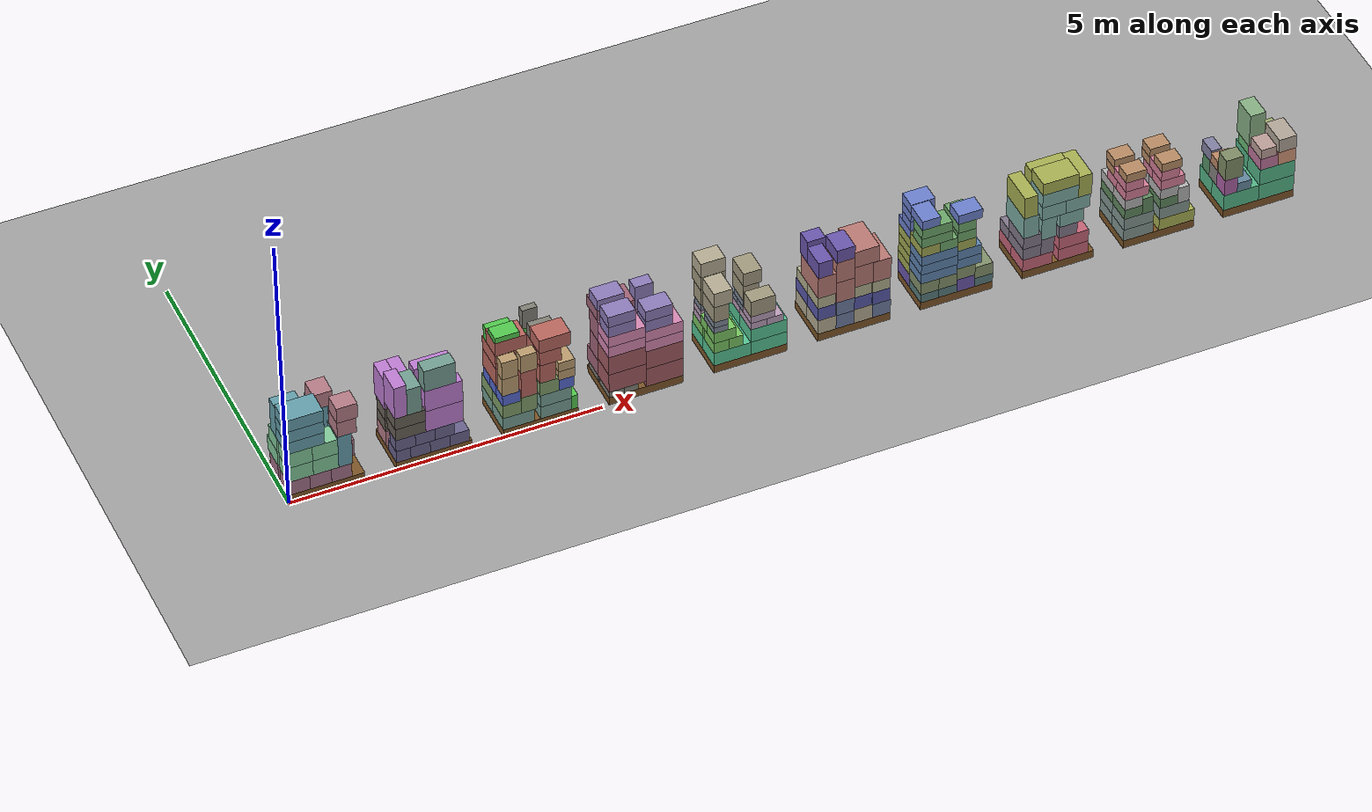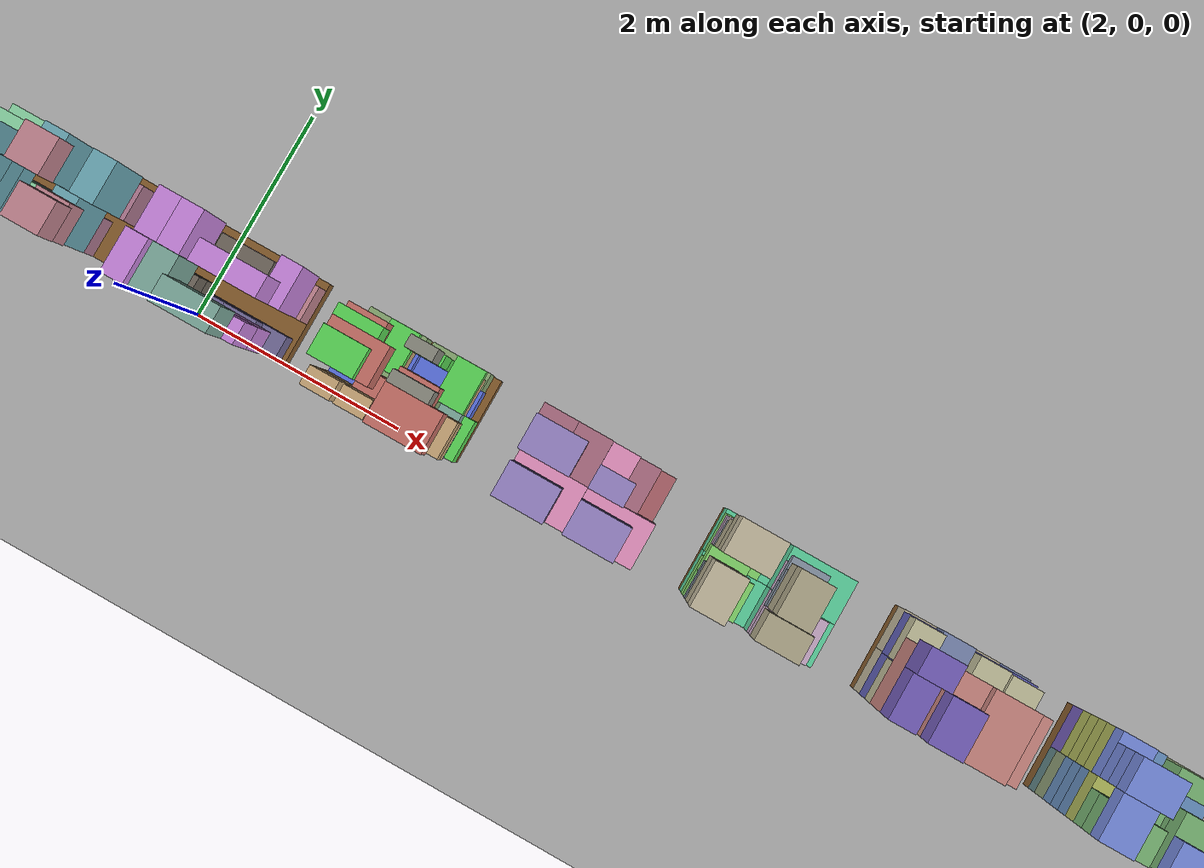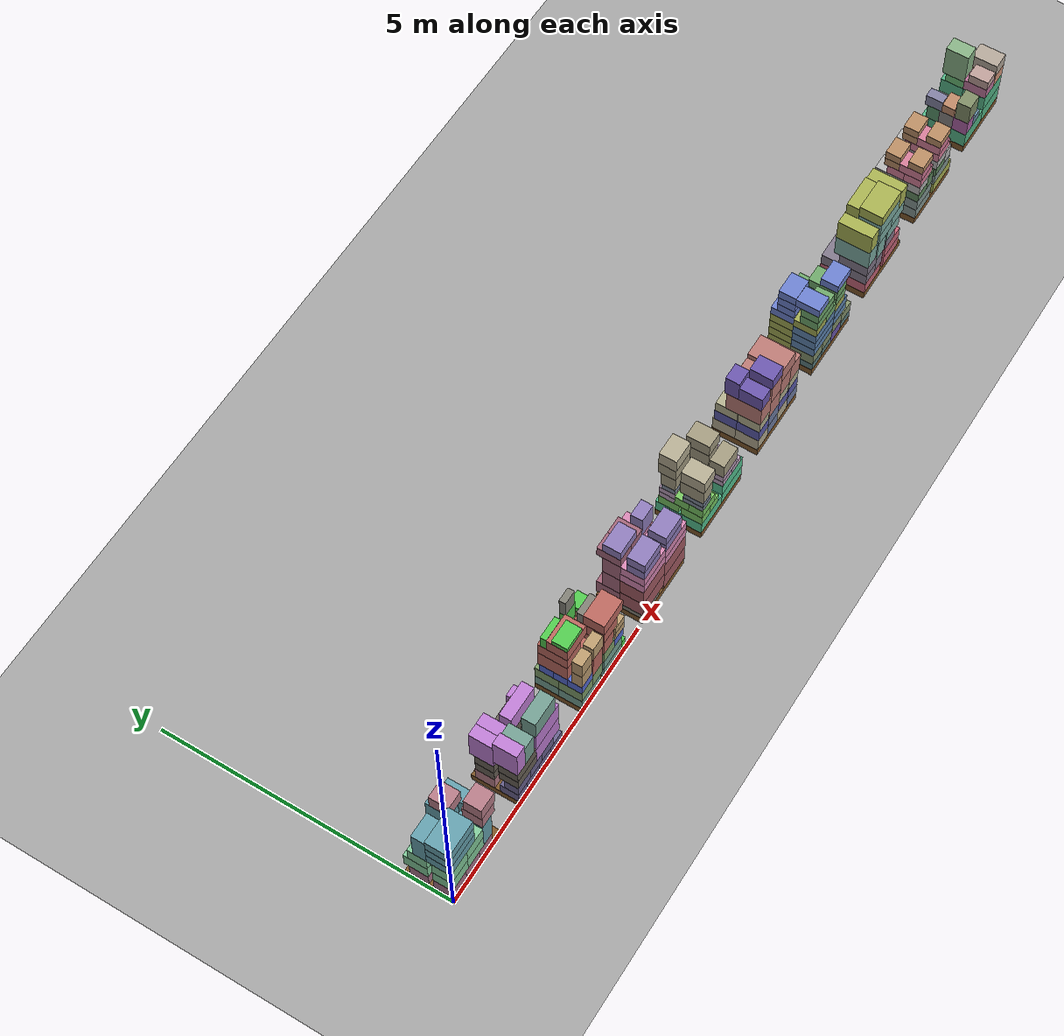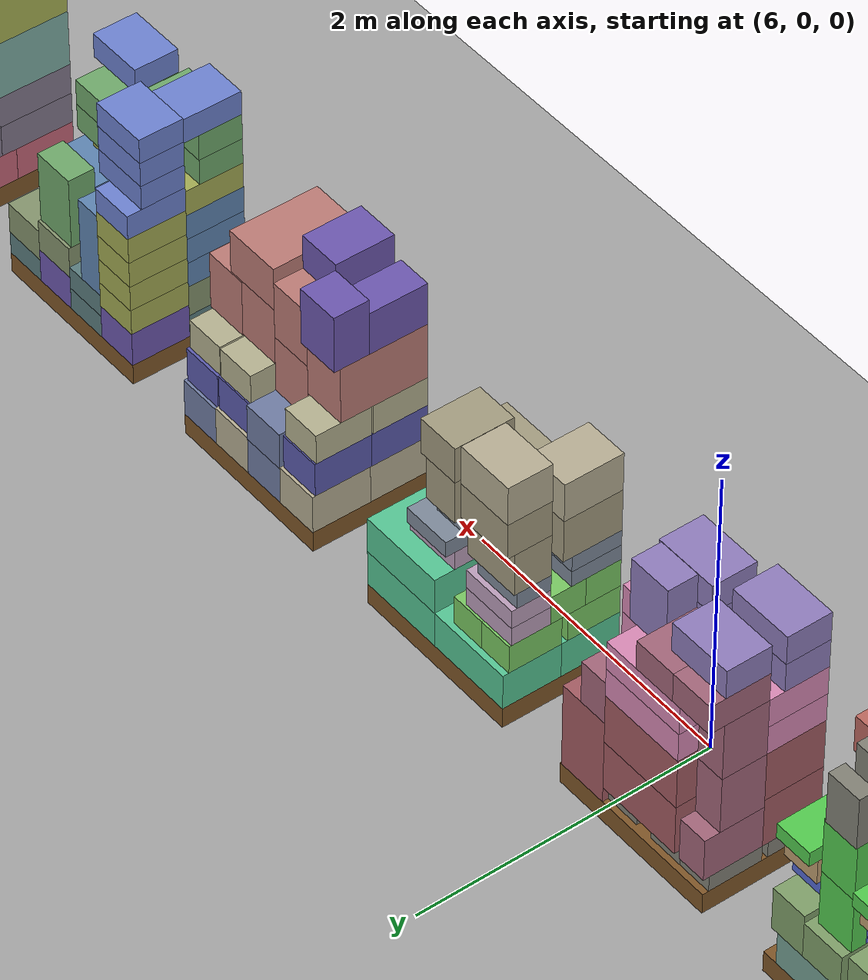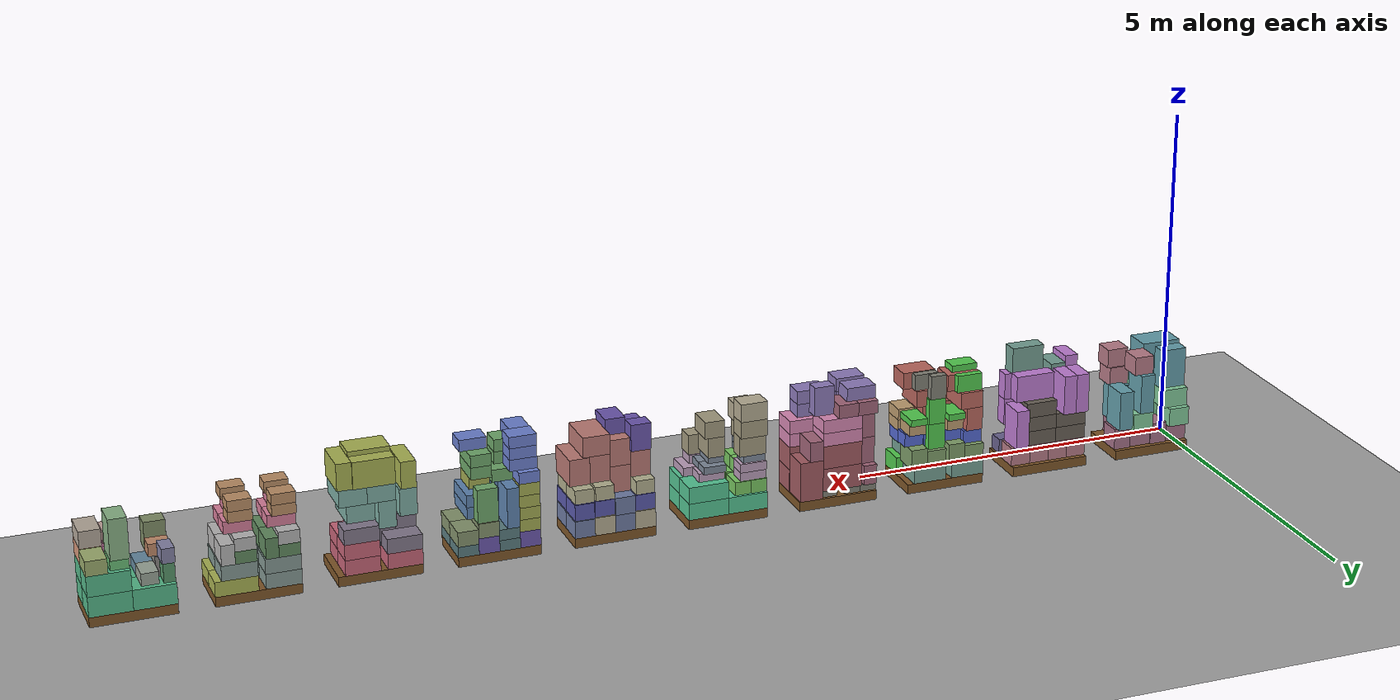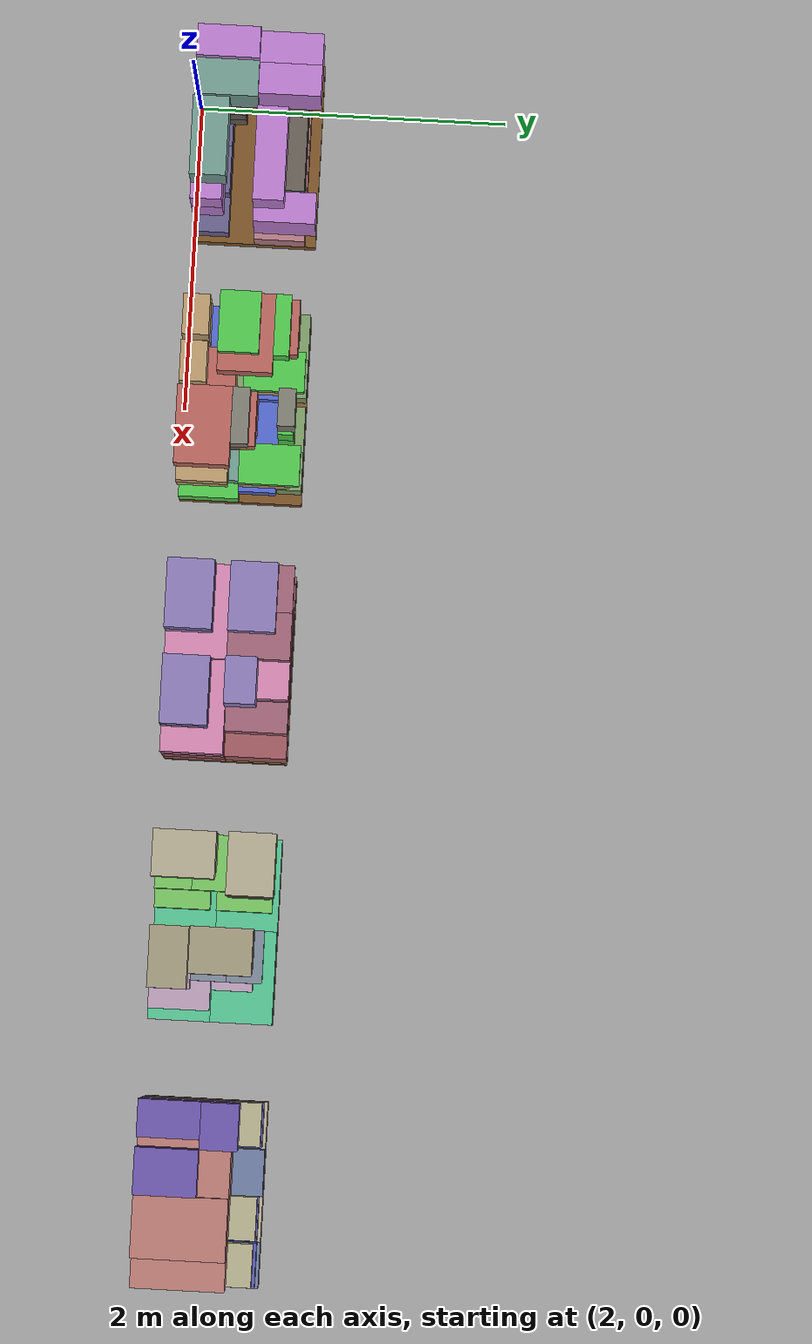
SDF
<?xml version="1.0" ?>
<sdf version="1.10">
  <world name="pallet_towers">
    <gravity>0 0 -9.81</gravity>

    <physics name="pallet_physics" type="ignored">
      <max_step_size>0.005</max_step_size>
      <real_time_factor>1.0</real_time_factor>
      <real_time_update_rate>200</real_time_update_rate>
      <max_contacts>30</max_contacts>
    </physics>

    <plugin filename="gz-sim-physics-system" name="gz::sim::systems::Physics" />
    <plugin filename="gz-sim-user-commands-system" name="gz::sim::systems::UserCommands" />
    <plugin filename="gz-sim-scene-broadcaster-system" name="gz::sim::systems::SceneBroadcaster" />

    <light type="directional" name="sun">
      <cast_shadows>true</cast_shadows>
      <pose>0 0 10 0 0 0</pose>
      <diffuse>0.8 0.8 0.8 1</diffuse>
      <specular>0.2 0.2 0.2 1</specular>
      <direction>-0.5 0.2 -0.9</direction>
    </light>

    <model name="ground_plane">
      <static>true</static>
      <link name="link">
        <collision name="collision">
          <geometry>
            <plane>
              <normal>0 0 1</normal>
              <size>30 30</size>
            </plane>
          </geometry>

          <surface>
            <friction>
              <ode>
                <mu>0.35</mu>
                <mu2>0.35</mu2>
              </ode>
            </friction>
            <bounce>
              <restitution_coefficient>0</restitution_coefficient>
              <threshold>100000</threshold>
            </bounce>
            <contact>
              <ode>
                <kp>1000000</kp>
                <kd>100</kd>
                <max_vel>1</max_vel>
                <min_depth>0.0005</min_depth>
              </ode>
            </contact>
          </surface>
        </collision>

        <visual name="visual">
          <geometry>
            <plane>
              <normal>0 0 1</normal>
              <size>30 30</size>
            </plane>
          </geometry>
          <material>
            <ambient>0.65 0.65 0.65 1</ambient>
            <diffuse>0.65 0.65 0.65 1</diffuse>
          </material>
        </visual>
      </link>
    </model>

    <model name="pallet_01_1">
      <static>false</static>
      <pose>0.6 0.4 0.072 0 0 0</pose>
      <link name="body">
        <gravity>true</gravity>
        <inertial>
          <mass>25</mass>
          <inertia>
            <ixx>1.37653333</ixx>
            <ixy>0</ixy>
            <ixz>0</ixz>
            <iyy>3.0432</iyy>
            <iyz>0</iyz>
            <izz>4.33333333</izz>
          </inertia>
        </inertial>

        <collision name="collision">
          <geometry>
            <box>
              <size>1.2 0.8 0.144</size>
            </box>
          </geometry>

          <surface>
            <friction>
              <ode>
                <mu>0.35</mu>
                <mu2>0.35</mu2>
              </ode>
            </friction>
            <bounce>
              <restitution_coefficient>0</restitution_coefficient>
              <threshold>100000</threshold>
            </bounce>
            <contact>
              <ode>
                <kp>1000000</kp>
                <kd>100</kd>
                <max_vel>1</max_vel>
                <min_depth>0.0005</min_depth>
              </ode>
            </contact>
          </surface>
        </collision>

        <visual name="visual">
          <geometry>
            <box>
              <size>1.2 0.8 0.144</size>
            </box>
          </geometry>
          <material>
            <ambient>0.5 0.34 0.16 1</ambient>
            <diffuse>0.5 0.34 0.16 1</diffuse>
            <specular>0.05 0.05 0.05 1</specular>
          </material>
        </visual>
      </link>
    </model>
    <model name="box_p01_0001_WINE_001_WINE">
      <static>false</static>
      <pose>0.77 0.56 0.274 0 0 0</pose>
      <link name="body">
        <gravity>true</gravity>
        <inertial>
          <mass>18</mass>
          <inertia>
            <ixx>0.255</ixx>
            <ixy>0</ixy>
            <ixz>0</ixz>
            <iyy>0.2748</iyy>
            <iyz>0</iyz>
            <izz>0.327</izz>
          </inertia>
        </inertial>

        <collision name="collision">
          <geometry>
            <box>
              <size>0.34 0.32 0.26</size>
            </box>
          </geometry>

          <surface>
            <friction>
              <ode>
                <mu>0.35</mu>
                <mu2>0.35</mu2>
              </ode>
            </friction>
            <bounce>
              <restitution_coefficient>0</restitution_coefficient>
              <threshold>100000</threshold>
            </bounce>
            <contact>
              <ode>
                <kp>1000000</kp>
                <kd>100</kd>
                <max_vel>1</max_vel>
                <min_depth>0.0005</min_depth>
              </ode>
            </contact>
          </surface>
        </collision>

        <visual name="visual">
          <geometry>
            <box>
              <size>0.34 0.32 0.26</size>
            </box>
          </geometry>
          <material>
            <ambient>0.654901961 0.450980392 0.541176471 1</ambient>
            <diffuse>0.654901961 0.450980392 0.541176471 1</diffuse>
            <specular>0.05 0.05 0.05 1</specular>
          </material>
        </visual>
      </link>
    </model>
    <model name="box_p01_0002_WINE_002_WINE">
      <static>false</static>
      <pose>0.17 0.56 0.274 0 0 0</pose>
      <link name="body">
        <gravity>true</gravity>
        <inertial>
          <mass>18</mass>
          <inertia>
            <ixx>0.255</ixx>
            <ixy>0</ixy>
            <ixz>0</ixz>
            <iyy>0.2748</iyy>
            <iyz>0</iyz>
            <izz>0.327</izz>
          </inertia>
        </inertial>

        <collision name="collision">
          <geometry>
            <box>
              <size>0.34 0.32 0.26</size>
            </box>
          </geometry>

          <surface>
            <friction>
              <ode>
                <mu>0.35</mu>
                <mu2>0.35</mu2>
              </ode>
            </friction>
            <bounce>
              <restitution_coefficient>0</restitution_coefficient>
              <threshold>100000</threshold>
            </bounce>
            <contact>
              <ode>
                <kp>1000000</kp>
                <kd>100</kd>
                <max_vel>1</max_vel>
                <min_depth>0.0005</min_depth>
              </ode>
            </contact>
          </surface>
        </collision>

        <visual name="visual">
          <geometry>
            <box>
              <size>0.34 0.32 0.26</size>
            </box>
          </geometry>
          <material>
            <ambient>0.654901961 0.450980392 0.541176471 1</ambient>
            <diffuse>0.654901961 0.450980392 0.541176471 1</diffuse>
            <specular>0.05 0.05 0.05 1</specular>
          </material>
        </visual>
      </link>
    </model>
    <model name="box_p01_0003_WINE_003_WINE">
      <static>false</static>
      <pose>0.17 0.16 0.274 0 0 0</pose>
      <link name="body">
        <gravity>true</gravity>
        <inertial>
          <mass>18</mass>
          <inertia>
            <ixx>0.255</ixx>
            <ixy>0</ixy>
            <ixz>0</ixz>
            <iyy>0.2748</iyy>
            <iyz>0</iyz>
            <izz>0.327</izz>
          </inertia>
        </inertial>

        <collision name="collision">
          <geometry>
            <box>
              <size>0.34 0.32 0.26</size>
            </box>
          </geometry>

          <surface>
            <friction>
              <ode>
                <mu>0.35</mu>
                <mu2>0.35</mu2>
              </ode>
            </friction>
            <bounce>
              <restitution_coefficient>0</restitution_coefficient>
              <threshold>100000</threshold>
            </bounce>
            <contact>
              <ode>
                <kp>1000000</kp>
                <kd>100</kd>
                <max_vel>1</max_vel>
                <min_depth>0.0005</min_depth>
              </ode>
            </contact>
          </surface>
        </collision>

        <visual name="visual">
          <geometry>
            <box>
              <size>0.34 0.32 0.26</size>
            </box>
          </geometry>
          <material>
            <ambient>0.654901961 0.450980392 0.541176471 1</ambient>
            <diffuse>0.654901961 0.450980392 0.541176471 1</diffuse>
            <specular>0.05 0.05 0.05 1</specular>
          </material>
        </visual>
      </link>
    </model>
    <model name="box_p01_0004_WINE_004_WINE">
      <static>false</static>
      <pose>0.51 0.16 0.274 0 0 0</pose>
      <link name="body">
        <gravity>true</gravity>
        <inertial>
          <mass>18</mass>
          <inertia>
            <ixx>0.255</ixx>
            <ixy>0</ixy>
            <ixz>0</ixz>
            <iyy>0.2748</iyy>
            <iyz>0</iyz>
            <izz>0.327</izz>
          </inertia>
        </inertial>

        <collision name="collision">
          <geometry>
            <box>
              <size>0.34 0.32 0.26</size>
            </box>
          </geometry>

          <surface>
            <friction>
              <ode>
                <mu>0.35</mu>
                <mu2>0.35</mu2>
              </ode>
            </friction>
            <bounce>
              <restitution_coefficient>0</restitution_coefficient>
              <threshold>100000</threshold>
            </bounce>
            <contact>
              <ode>
                <kp>1000000</kp>
                <kd>100</kd>
                <max_vel>1</max_vel>
                <min_depth>0.0005</min_depth>
              </ode>
            </contact>
          </surface>
        </collision>

        <visual name="visual">
          <geometry>
            <box>
              <size>0.34 0.32 0.26</size>
            </box>
          </geometry>
          <material>
            <ambient>0.654901961 0.450980392 0.541176471 1</ambient>
            <diffuse>0.654901961 0.450980392 0.541176471 1</diffuse>
            <specular>0.05 0.05 0.05 1</specular>
          </material>
        </visual>
      </link>
    </model>
    <model name="box_p01_0005_WINE_005_WINE">
      <static>false</static>
      <pose>0.84 0.17 0.274 0 0 0</pose>
      <link name="body">
        <gravity>true</gravity>
        <inertial>
          <mass>18</mass>
          <inertia>
            <ixx>0.2748</ixx>
            <ixy>0</ixy>
            <ixz>0</ixz>
            <iyy>0.255</iyy>
            <iyz>0</iyz>
            <izz>0.327</izz>
          </inertia>
        </inertial>

        <collision name="collision">
          <geometry>
            <box>
              <size>0.32 0.34 0.26</size>
            </box>
          </geometry>

          <surface>
            <friction>
              <ode>
                <mu>0.35</mu>
                <mu2>0.35</mu2>
              </ode>
            </friction>
            <bounce>
              <restitution_coefficient>0</restitution_coefficient>
              <threshold>100000</threshold>
            </bounce>
            <contact>
              <ode>
                <kp>1000000</kp>
                <kd>100</kd>
                <max_vel>1</max_vel>
                <min_depth>0.0005</min_depth>
              </ode>
            </contact>
          </surface>
        </collision>

        <visual name="visual">
          <geometry>
            <box>
              <size>0.32 0.34 0.26</size>
            </box>
          </geometry>
          <material>
            <ambient>0.654901961 0.450980392 0.541176471 1</ambient>
            <diffuse>0.654901961 0.450980392 0.541176471 1</diffuse>
            <specular>0.05 0.05 0.05 1</specular>
          </material>
        </visual>
      </link>
    </model>
    <model name="box_p01_0006_WINE_006_WINE">
      <static>false</static>
      <pose>1.07 0.57 0.304 0 0 0</pose>
      <link name="body">
        <gravity>true</gravity>
        <inertial>
          <mass>18</mass>
          <inertia>
            <ixx>0.327</ixx>
            <ixy>0</ixy>
            <ixz>0</ixz>
            <iyy>0.255</iyy>
            <iyz>0</iyz>
            <izz>0.2748</izz>
          </inertia>
        </inertial>

        <collision name="collision">
          <geometry>
            <box>
              <size>0.26 0.34 0.32</size>
            </box>
          </geometry>

          <surface>
            <friction>
              <ode>
                <mu>0.35</mu>
                <mu2>0.35</mu2>
              </ode>
            </friction>
            <bounce>
              <restitution_coefficient>0</restitution_coefficient>
              <threshold>100000</threshold>
            </bounce>
            <contact>
              <ode>
                <kp>1000000</kp>
                <kd>100</kd>
                <max_vel>1</max_vel>
                <min_depth>0.0005</min_depth>
              </ode>
            </contact>
          </surface>
        </collision>

        <visual name="visual">
          <geometry>
            <box>
              <size>0.26 0.34 0.32</size>
            </box>
          </geometry>
          <material>
            <ambient>0.654901961 0.450980392 0.541176471 1</ambient>
            <diffuse>0.654901961 0.450980392 0.541176471 1</diffuse>
            <specular>0.05 0.05 0.05 1</specular>
          </material>
        </visual>
      </link>
    </model>
    <model name="box_p01_0007_WINE_007_WINE">
      <static>false</static>
      <pose>0.47 0.57 0.304 0 0 0</pose>
      <link name="body">
        <gravity>true</gravity>
        <inertial>
          <mass>18</mass>
          <inertia>
            <ixx>0.327</ixx>
            <ixy>0</ixy>
            <ixz>0</ixz>
            <iyy>0.255</iyy>
            <iyz>0</iyz>
            <izz>0.2748</izz>
          </inertia>
        </inertial>

        <collision name="collision">
          <geometry>
            <box>
              <size>0.26 0.34 0.32</size>
            </box>
          </geometry>

          <surface>
            <friction>
              <ode>
                <mu>0.35</mu>
                <mu2>0.35</mu2>
              </ode>
            </friction>
            <bounce>
              <restitution_coefficient>0</restitution_coefficient>
              <threshold>100000</threshold>
            </bounce>
            <contact>
              <ode>
                <kp>1000000</kp>
                <kd>100</kd>
                <max_vel>1</max_vel>
                <min_depth>0.0005</min_depth>
              </ode>
            </contact>
          </surface>
        </collision>

        <visual name="visual">
          <geometry>
            <box>
              <size>0.26 0.34 0.32</size>
            </box>
          </geometry>
          <material>
            <ambient>0.654901961 0.450980392 0.541176471 1</ambient>
            <diffuse>0.654901961 0.450980392 0.541176471 1</diffuse>
            <specular>0.05 0.05 0.05 1</specular>
          </material>
        </visual>
      </link>
    </model>
    <model name="box_p01_0008_DETERG_001_DETERG">
      <static>false</static>
      <pose>0.2 0.16 0.544 0 0 0</pose>
      <link name="body">
        <gravity>true</gravity>
        <inertial>
          <mass>7</mass>
          <inertia>
            <ixx>0.105466667</ixx>
            <ixy>0</ixy>
            <ixz>0</ixz>
            <iyy>0.139066667</iyy>
            <iyz>0</iyz>
            <izz>0.153066667</izz>
          </inertia>
        </inertial>

        <collision name="collision">
          <geometry>
            <box>
              <size>0.4 0.32 0.28</size>
            </box>
          </geometry>

          <surface>
            <friction>
              <ode>
                <mu>0.35</mu>
                <mu2>0.35</mu2>
              </ode>
            </friction>
            <bounce>
              <restitution_coefficient>0</restitution_coefficient>
              <threshold>100000</threshold>
            </bounce>
            <contact>
              <ode>
                <kp>1000000</kp>
                <kd>100</kd>
                <max_vel>1</max_vel>
                <min_depth>0.0005</min_depth>
              </ode>
            </contact>
          </surface>
        </collision>

        <visual name="visual">
          <geometry>
            <box>
              <size>0.4 0.32 0.28</size>
            </box>
          </geometry>
          <material>
            <ambient>0.517647059 0.803921569 0.615686275 1</ambient>
            <diffuse>0.517647059 0.803921569 0.615686275 1</diffuse>
            <specular>0.05 0.05 0.05 1</specular>
          </material>
        </visual>
      </link>
    </model>
    <model name="box_p01_0009_DETERG_002_DETERG">
      <static>false</static>
      <pose>0.6 0.16 0.544 0 0 0</pose>
      <link name="body">
        <gravity>true</gravity>
        <inertial>
          <mass>7</mass>
          <inertia>
            <ixx>0.105466667</ixx>
            <ixy>0</ixy>
            <ixz>0</ixz>
            <iyy>0.139066667</iyy>
            <iyz>0</iyz>
            <izz>0.153066667</izz>
          </inertia>
        </inertial>

        <collision name="collision">
          <geometry>
            <box>
              <size>0.4 0.32 0.28</size>
            </box>
          </geometry>

          <surface>
            <friction>
              <ode>
                <mu>0.35</mu>
                <mu2>0.35</mu2>
              </ode>
            </friction>
            <bounce>
              <restitution_coefficient>0</restitution_coefficient>
              <threshold>100000</threshold>
            </bounce>
            <contact>
              <ode>
                <kp>1000000</kp>
                <kd>100</kd>
                <max_vel>1</max_vel>
                <min_depth>0.0005</min_depth>
              </ode>
            </contact>
          </surface>
        </collision>

        <visual name="visual">
          <geometry>
            <box>
              <size>0.4 0.32 0.28</size>
            </box>
          </geometry>
          <material>
            <ambient>0.517647059 0.803921569 0.615686275 1</ambient>
            <diffuse>0.517647059 0.803921569 0.615686275 1</diffuse>
            <specular>0.05 0.05 0.05 1</specular>
          </material>
        </visual>
      </link>
    </model>
    <model name="box_p01_0010_DETERG_003_DETERG">
      <static>false</static>
      <pose>0.16 0.6 0.544 0 0 0</pose>
      <link name="body">
        <gravity>true</gravity>
        <inertial>
          <mass>7</mass>
          <inertia>
            <ixx>0.139066667</ixx>
            <ixy>0</ixy>
            <ixz>0</ixz>
            <iyy>0.105466667</iyy>
            <iyz>0</iyz>
            <izz>0.153066667</izz>
          </inertia>
        </inertial>

        <collision name="collision">
          <geometry>
            <box>
              <size>0.32 0.4 0.28</size>
            </box>
          </geometry>

          <surface>
            <friction>
              <ode>
                <mu>0.35</mu>
                <mu2>0.35</mu2>
              </ode>
            </friction>
            <bounce>
              <restitution_coefficient>0</restitution_coefficient>
              <threshold>100000</threshold>
            </bounce>
            <contact>
              <ode>
                <kp>1000000</kp>
                <kd>100</kd>
                <max_vel>1</max_vel>
                <min_depth>0.0005</min_depth>
              </ode>
            </contact>
          </surface>
        </collision>

        <visual name="visual">
          <geometry>
            <box>
              <size>0.32 0.4 0.28</size>
            </box>
          </geometry>
          <material>
            <ambient>0.517647059 0.803921569 0.615686275 1</ambient>
            <diffuse>0.517647059 0.803921569 0.615686275 1</diffuse>
            <specular>0.05 0.05 0.05 1</specular>
          </material>
        </visual>
      </link>
    </model>
    <model name="box_p01_0011_DETERG_004_DETERG">
      <static>false</static>
      <pose>0.76 0.6 0.544 0 0 0</pose>
      <link name="body">
        <gravity>true</gravity>
        <inertial>
          <mass>7</mass>
          <inertia>
            <ixx>0.139066667</ixx>
            <ixy>0</ixy>
            <ixz>0</ixz>
            <iyy>0.105466667</iyy>
            <iyz>0</iyz>
            <izz>0.153066667</izz>
          </inertia>
        </inertial>

        <collision name="collision">
          <geometry>
            <box>
              <size>0.32 0.4 0.28</size>
            </box>
          </geometry>

          <surface>
            <friction>
              <ode>
                <mu>0.35</mu>
                <mu2>0.35</mu2>
              </ode>
            </friction>
            <bounce>
              <restitution_coefficient>0</restitution_coefficient>
              <threshold>100000</threshold>
            </bounce>
            <contact>
              <ode>
                <kp>1000000</kp>
                <kd>100</kd>
                <max_vel>1</max_vel>
                <min_depth>0.0005</min_depth>
              </ode>
            </contact>
          </surface>
        </collision>

        <visual name="visual">
          <geometry>
            <box>
              <size>0.32 0.4 0.28</size>
            </box>
          </geometry>
          <material>
            <ambient>0.517647059 0.803921569 0.615686275 1</ambient>
            <diffuse>0.517647059 0.803921569 0.615686275 1</diffuse>
            <specular>0.05 0.05 0.05 1</specular>
          </material>
        </visual>
      </link>
    </model>
    <model name="box_p01_0012_DETERG_005_DETERG">
      <static>false</static>
      <pose>0.2 0.56 0.824 0 0 0</pose>
      <link name="body">
        <gravity>true</gravity>
        <inertial>
          <mass>7</mass>
          <inertia>
            <ixx>0.105466667</ixx>
            <ixy>0</ixy>
            <ixz>0</ixz>
            <iyy>0.139066667</iyy>
            <iyz>0</iyz>
            <izz>0.153066667</izz>
          </inertia>
        </inertial>

        <collision name="collision">
          <geometry>
            <box>
              <size>0.4 0.32 0.28</size>
            </box>
          </geometry>

          <surface>
            <friction>
              <ode>
                <mu>0.35</mu>
                <mu2>0.35</mu2>
              </ode>
            </friction>
            <bounce>
              <restitution_coefficient>0</restitution_coefficient>
              <threshold>100000</threshold>
            </bounce>
            <contact>
              <ode>
                <kp>1000000</kp>
                <kd>100</kd>
                <max_vel>1</max_vel>
                <min_depth>0.0005</min_depth>
              </ode>
            </contact>
          </surface>
        </collision>

        <visual name="visual">
          <geometry>
            <box>
              <size>0.4 0.32 0.28</size>
            </box>
          </geometry>
          <material>
            <ambient>0.517647059 0.803921569 0.615686275 1</ambient>
            <diffuse>0.517647059 0.803921569 0.615686275 1</diffuse>
            <specular>0.05 0.05 0.05 1</specular>
          </material>
        </visual>
      </link>
    </model>
    <model name="box_p01_0013_DETERG_006_DETERG">
      <static>false</static>
      <pose>0.6 0.16 0.824 0 0 0</pose>
      <link name="body">
        <gravity>true</gravity>
        <inertial>
          <mass>7</mass>
          <inertia>
            <ixx>0.105466667</ixx>
            <ixy>0</ixy>
            <ixz>0</ixz>
            <iyy>0.139066667</iyy>
            <iyz>0</iyz>
            <izz>0.153066667</izz>
          </inertia>
        </inertial>

        <collision name="collision">
          <geometry>
            <box>
              <size>0.4 0.32 0.28</size>
            </box>
          </geometry>

          <surface>
            <friction>
              <ode>
                <mu>0.35</mu>
                <mu2>0.35</mu2>
              </ode>
            </friction>
            <bounce>
              <restitution_coefficient>0</restitution_coefficient>
              <threshold>100000</threshold>
            </bounce>
            <contact>
              <ode>
                <kp>1000000</kp>
                <kd>100</kd>
                <max_vel>1</max_vel>
                <min_depth>0.0005</min_depth>
              </ode>
            </contact>
          </surface>
        </collision>

        <visual name="visual">
          <geometry>
            <box>
              <size>0.4 0.32 0.28</size>
            </box>
          </geometry>
          <material>
            <ambient>0.517647059 0.803921569 0.615686275 1</ambient>
            <diffuse>0.517647059 0.803921569 0.615686275 1</diffuse>
            <specular>0.05 0.05 0.05 1</specular>
          </material>
        </visual>
      </link>
    </model>
    <model name="box_p01_0014_DETERG_007_DETERG">
      <static>false</static>
      <pose>0.2 0.16 0.824 0 0 0</pose>
      <link name="body">
        <gravity>true</gravity>
        <inertial>
          <mass>7</mass>
          <inertia>
            <ixx>0.105466667</ixx>
            <ixy>0</ixy>
            <ixz>0</ixz>
            <iyy>0.139066667</iyy>
            <iyz>0</iyz>
            <izz>0.153066667</izz>
          </inertia>
        </inertial>

        <collision name="collision">
          <geometry>
            <box>
              <size>0.4 0.32 0.28</size>
            </box>
          </geometry>

          <surface>
            <friction>
              <ode>
                <mu>0.35</mu>
                <mu2>0.35</mu2>
              </ode>
            </friction>
            <bounce>
              <restitution_coefficient>0</restitution_coefficient>
              <threshold>100000</threshold>
            </bounce>
            <contact>
              <ode>
                <kp>1000000</kp>
                <kd>100</kd>
                <max_vel>1</max_vel>
                <min_depth>0.0005</min_depth>
              </ode>
            </contact>
          </surface>
        </collision>

        <visual name="visual">
          <geometry>
            <box>
              <size>0.4 0.32 0.28</size>
            </box>
          </geometry>
          <material>
            <ambient>0.517647059 0.803921569 0.615686275 1</ambient>
            <diffuse>0.517647059 0.803921569 0.615686275 1</diffuse>
            <specular>0.05 0.05 0.05 1</specular>
          </material>
        </visual>
      </link>
    </model>
    <model name="box_p01_0015_APPLES_001_APPLES">
      <static>false</static>
      <pose>0.3 0.2 1.074 0 0 0</pose>
      <link name="body">
        <gravity>true</gravity>
        <inertial>
          <mass>12</mass>
          <inertia>
            <ixx>0.2084</ixx>
            <ixy>0</ixy>
            <ixz>0</ixz>
            <iyy>0.4084</iyy>
            <iyz>0</iyz>
            <izz>0.52</izz>
          </inertia>
        </inertial>

        <collision name="collision">
          <geometry>
            <box>
              <size>0.6 0.4 0.22</size>
            </box>
          </geometry>

          <surface>
            <friction>
              <ode>
                <mu>0.35</mu>
                <mu2>0.35</mu2>
              </ode>
            </friction>
            <bounce>
              <restitution_coefficient>0</restitution_coefficient>
              <threshold>100000</threshold>
            </bounce>
            <contact>
              <ode>
                <kp>1000000</kp>
                <kd>100</kd>
                <max_vel>1</max_vel>
                <min_depth>0.0005</min_depth>
              </ode>
            </contact>
          </surface>
        </collision>

        <visual name="visual">
          <geometry>
            <box>
              <size>0.6 0.4 0.22</size>
            </box>
          </geometry>
          <material>
            <ambient>0.4 0.635294118 0.68627451 1</ambient>
            <diffuse>0.4 0.635294118 0.68627451 1</diffuse>
            <specular>0.05 0.05 0.05 1</specular>
          </material>
        </visual>
      </link>
    </model>
    <model name="box_p01_0016_APPLES_002_APPLES">
      <static>false</static>
      <pose>0.91 0.2 0.704 0 0 0</pose>
      <link name="body">
        <gravity>true</gravity>
        <inertial>
          <mass>12</mass>
          <inertia>
            <ixx>0.52</ixx>
            <ixy>0</ixy>
            <ixz>0</ixz>
            <iyy>0.4084</iyy>
            <iyz>0</iyz>
            <izz>0.2084</izz>
          </inertia>
        </inertial>

        <collision name="collision">
          <geometry>
            <box>
              <size>0.22 0.4 0.6</size>
            </box>
          </geometry>

          <surface>
            <friction>
              <ode>
                <mu>0.35</mu>
                <mu2>0.35</mu2>
              </ode>
            </friction>
            <bounce>
              <restitution_coefficient>0</restitution_coefficient>
              <threshold>100000</threshold>
            </bounce>
            <contact>
              <ode>
                <kp>1000000</kp>
                <kd>100</kd>
                <max_vel>1</max_vel>
                <min_depth>0.0005</min_depth>
              </ode>
            </contact>
          </surface>
        </collision>

        <visual name="visual">
          <geometry>
            <box>
              <size>0.22 0.4 0.6</size>
            </box>
          </geometry>
          <material>
            <ambient>0.4 0.635294118 0.68627451 1</ambient>
            <diffuse>0.4 0.635294118 0.68627451 1</diffuse>
            <specular>0.05 0.05 0.05 1</specular>
          </material>
        </visual>
      </link>
    </model>
    <model name="box_p01_0017_APPLES_003_APPLES">
      <static>false</static>
      <pose>0.3 0.2 1.294 0 0 0</pose>
      <link name="body">
        <gravity>true</gravity>
        <inertial>
          <mass>12</mass>
          <inertia>
            <ixx>0.2084</ixx>
            <ixy>0</ixy>
            <ixz>0</ixz>
            <iyy>0.4084</iyy>
            <iyz>0</iyz>
            <izz>0.52</izz>
          </inertia>
        </inertial>

        <collision name="collision">
          <geometry>
            <box>
              <size>0.6 0.4 0.22</size>
            </box>
          </geometry>

          <surface>
            <friction>
              <ode>
                <mu>0.35</mu>
                <mu2>0.35</mu2>
              </ode>
            </friction>
            <bounce>
              <restitution_coefficient>0</restitution_coefficient>
              <threshold>100000</threshold>
            </bounce>
            <contact>
              <ode>
                <kp>1000000</kp>
                <kd>100</kd>
                <max_vel>1</max_vel>
                <min_depth>0.0005</min_depth>
              </ode>
            </contact>
          </surface>
        </collision>

        <visual name="visual">
          <geometry>
            <box>
              <size>0.6 0.4 0.22</size>
            </box>
          </geometry>
          <material>
            <ambient>0.4 0.635294118 0.68627451 1</ambient>
            <diffuse>0.4 0.635294118 0.68627451 1</diffuse>
            <specular>0.05 0.05 0.05 1</specular>
          </material>
        </visual>
      </link>
    </model>
    <model name="box_p01_0018_APPLES_004_APPLES">
      <static>false</static>
      <pose>0.3 0.2 1.514 0 0 0</pose>
      <link name="body">
        <gravity>true</gravity>
        <inertial>
          <mass>12</mass>
          <inertia>
            <ixx>0.2084</ixx>
            <ixy>0</ixy>
            <ixz>0</ixz>
            <iyy>0.4084</iyy>
            <iyz>0</iyz>
            <izz>0.52</izz>
          </inertia>
        </inertial>

        <collision name="collision">
          <geometry>
            <box>
              <size>0.6 0.4 0.22</size>
            </box>
          </geometry>

          <surface>
            <friction>
              <ode>
                <mu>0.35</mu>
                <mu2>0.35</mu2>
              </ode>
            </friction>
            <bounce>
              <restitution_coefficient>0</restitution_coefficient>
              <threshold>100000</threshold>
            </bounce>
            <contact>
              <ode>
                <kp>1000000</kp>
                <kd>100</kd>
                <max_vel>1</max_vel>
                <min_depth>0.0005</min_depth>
              </ode>
            </contact>
          </surface>
        </collision>

        <visual name="visual">
          <geometry>
            <box>
              <size>0.6 0.4 0.22</size>
            </box>
          </geometry>
          <material>
            <ambient>0.4 0.635294118 0.68627451 1</ambient>
            <diffuse>0.4 0.635294118 0.68627451 1</diffuse>
            <specular>0.05 0.05 0.05 1</specular>
          </material>
        </visual>
      </link>
    </model>
    <model name="box_p01_0019_APPLES_005_APPLES">
      <static>false</static>
      <pose>0.71 0.6 0.984 0 0 0</pose>
      <link name="body">
        <gravity>true</gravity>
        <inertial>
          <mass>12</mass>
          <inertia>
            <ixx>0.52</ixx>
            <ixy>0</ixy>
            <ixz>0</ixz>
            <iyy>0.4084</iyy>
            <iyz>0</iyz>
            <izz>0.2084</izz>
          </inertia>
        </inertial>

        <collision name="collision">
          <geometry>
            <box>
              <size>0.22 0.4 0.6</size>
            </box>
          </geometry>

          <surface>
            <friction>
              <ode>
                <mu>0.35</mu>
                <mu2>0.35</mu2>
              </ode>
            </friction>
            <bounce>
              <restitution_coefficient>0</restitution_coefficient>
              <threshold>100000</threshold>
            </bounce>
            <contact>
              <ode>
                <kp>1000000</kp>
                <kd>100</kd>
                <max_vel>1</max_vel>
                <min_depth>0.0005</min_depth>
              </ode>
            </contact>
          </surface>
        </collision>

        <visual name="visual">
          <geometry>
            <box>
              <size>0.22 0.4 0.6</size>
            </box>
          </geometry>
          <material>
            <ambient>0.4 0.635294118 0.68627451 1</ambient>
            <diffuse>0.4 0.635294118 0.68627451 1</diffuse>
            <specular>0.05 0.05 0.05 1</specular>
          </material>
        </visual>
      </link>
    </model>
    <model name="box_p01_0020_APPLES_006_APPLES">
      <static>false</static>
      <pose>1.05 0.6 0.764 0 0 0</pose>
      <link name="body">
        <gravity>true</gravity>
        <inertial>
          <mass>12</mass>
          <inertia>
            <ixx>0.52</ixx>
            <ixy>0</ixy>
            <ixz>0</ixz>
            <iyy>0.4084</iyy>
            <iyz>0</iyz>
            <izz>0.2084</izz>
          </inertia>
        </inertial>

        <collision name="collision">
          <geometry>
            <box>
              <size>0.22 0.4 0.6</size>
            </box>
          </geometry>

          <surface>
            <friction>
              <ode>
                <mu>0.35</mu>
                <mu2>0.35</mu2>
              </ode>
            </friction>
            <bounce>
              <restitution_coefficient>0</restitution_coefficient>
              <threshold>100000</threshold>
            </bounce>
            <contact>
              <ode>
                <kp>1000000</kp>
                <kd>100</kd>
                <max_vel>1</max_vel>
                <min_depth>0.0005</min_depth>
              </ode>
            </contact>
          </surface>
        </collision>

        <visual name="visual">
          <geometry>
            <box>
              <size>0.22 0.4 0.6</size>
            </box>
          </geometry>
          <material>
            <ambient>0.4 0.635294118 0.68627451 1</ambient>
            <diffuse>0.4 0.635294118 0.68627451 1</diffuse>
            <specular>0.05 0.05 0.05 1</specular>
          </material>
        </visual>
      </link>
    </model>
    <model name="box_p01_0021_APPLES_007_APPLES">
      <static>false</static>
      <pose>0.2 0.51 1.264 0 0 0</pose>
      <link name="body">
        <gravity>true</gravity>
        <inertial>
          <mass>12</mass>
          <inertia>
            <ixx>0.4084</ixx>
            <ixy>0</ixy>
            <ixz>0</ixz>
            <iyy>0.52</iyy>
            <iyz>0</iyz>
            <izz>0.2084</izz>
          </inertia>
        </inertial>

        <collision name="collision">
          <geometry>
            <box>
              <size>0.4 0.22 0.6</size>
            </box>
          </geometry>

          <surface>
            <friction>
              <ode>
                <mu>0.35</mu>
                <mu2>0.35</mu2>
              </ode>
            </friction>
            <bounce>
              <restitution_coefficient>0</restitution_coefficient>
              <threshold>100000</threshold>
            </bounce>
            <contact>
              <ode>
                <kp>1000000</kp>
                <kd>100</kd>
                <max_vel>1</max_vel>
                <min_depth>0.0005</min_depth>
              </ode>
            </contact>
          </surface>
        </collision>

        <visual name="visual">
          <geometry>
            <box>
              <size>0.4 0.22 0.6</size>
            </box>
          </geometry>
          <material>
            <ambient>0.4 0.635294118 0.68627451 1</ambient>
            <diffuse>0.4 0.635294118 0.68627451 1</diffuse>
            <specular>0.05 0.05 0.05 1</specular>
          </material>
        </visual>
      </link>
    </model>
    <model name="box_p01_0022_EGGS_001_EGGS">
      <static>false</static>
      <pose>0.95 0.165 1.144 0 0 0</pose>
      <link name="body">
        <gravity>true</gravity>
        <inertial>
          <mass>18</mass>
          <inertia>
            <ixx>0.28095</ixx>
            <ixy>0</ixy>
            <ixz>0</ixz>
            <iyy>0.2526</iyy>
            <iyz>0</iyz>
            <izz>0.29835</izz>
          </inertia>
        </inertial>

        <collision name="collision">
          <geometry>
            <box>
              <size>0.3 0.33 0.28</size>
            </box>
          </geometry>

          <surface>
            <friction>
              <ode>
                <mu>0.35</mu>
                <mu2>0.35</mu2>
              </ode>
            </friction>
            <bounce>
              <restitution_coefficient>0</restitution_coefficient>
              <threshold>100000</threshold>
            </bounce>
            <contact>
              <ode>
                <kp>1000000</kp>
                <kd>100</kd>
                <max_vel>1</max_vel>
                <min_depth>0.0005</min_depth>
              </ode>
            </contact>
          </surface>
        </collision>

        <visual name="visual">
          <geometry>
            <box>
              <size>0.3 0.33 0.28</size>
            </box>
          </geometry>
          <material>
            <ambient>0.725490196 0.494117647 0.537254902 1</ambient>
            <diffuse>0.725490196 0.494117647 0.537254902 1</diffuse>
            <specular>0.05 0.05 0.05 1</specular>
          </material>
        </visual>
      </link>
    </model>
    <model name="box_p01_0023_EGGS_002_EGGS">
      <static>false</static>
      <pose>0.75 0.565 1.424 0 0 0</pose>
      <link name="body">
        <gravity>true</gravity>
        <inertial>
          <mass>18</mass>
          <inertia>
            <ixx>0.28095</ixx>
            <ixy>0</ixy>
            <ixz>0</ixz>
            <iyy>0.2526</iyy>
            <iyz>0</iyz>
            <izz>0.29835</izz>
          </inertia>
        </inertial>

        <collision name="collision">
          <geometry>
            <box>
              <size>0.3 0.33 0.28</size>
            </box>
          </geometry>

          <surface>
            <friction>
              <ode>
                <mu>0.35</mu>
                <mu2>0.35</mu2>
              </ode>
            </friction>
            <bounce>
              <restitution_coefficient>0</restitution_coefficient>
              <threshold>100000</threshold>
            </bounce>
            <contact>
              <ode>
                <kp>1000000</kp>
                <kd>100</kd>
                <max_vel>1</max_vel>
                <min_depth>0.0005</min_depth>
              </ode>
            </contact>
          </surface>
        </collision>

        <visual name="visual">
          <geometry>
            <box>
              <size>0.3 0.33 0.28</size>
            </box>
          </geometry>
          <material>
            <ambient>0.725490196 0.494117647 0.537254902 1</ambient>
            <diffuse>0.725490196 0.494117647 0.537254902 1</diffuse>
            <specular>0.05 0.05 0.05 1</specular>
          </material>
        </visual>
      </link>
    </model>
    <model name="box_p01_0024_EGGS_003_EGGS">
      <static>false</static>
      <pose>0.965 0.15 1.424 0 0 0</pose>
      <link name="body">
        <gravity>true</gravity>
        <inertial>
          <mass>18</mass>
          <inertia>
            <ixx>0.2526</ixx>
            <ixy>0</ixy>
            <ixz>0</ixz>
            <iyy>0.28095</iyy>
            <iyz>0</iyz>
            <izz>0.29835</izz>
          </inertia>
        </inertial>

        <collision name="collision">
          <geometry>
            <box>
              <size>0.33 0.3 0.28</size>
            </box>
          </geometry>

          <surface>
            <friction>
              <ode>
                <mu>0.35</mu>
                <mu2>0.35</mu2>
              </ode>
            </friction>
            <bounce>
              <restitution_coefficient>0</restitution_coefficient>
              <threshold>100000</threshold>
            </bounce>
            <contact>
              <ode>
                <kp>1000000</kp>
                <kd>100</kd>
                <max_vel>1</max_vel>
                <min_depth>0.0005</min_depth>
              </ode>
            </contact>
          </surface>
        </collision>

        <visual name="visual">
          <geometry>
            <box>
              <size>0.33 0.3 0.28</size>
            </box>
          </geometry>
          <material>
            <ambient>0.725490196 0.494117647 0.537254902 1</ambient>
            <diffuse>0.725490196 0.494117647 0.537254902 1</diffuse>
            <specular>0.05 0.05 0.05 1</specular>
          </material>
        </visual>
      </link>
    </model>
    <model name="pallet_02_2">
      <static>false</static>
      <pose>2.3 0.4 0.072 0 0 0</pose>
      <link name="body">
        <gravity>true</gravity>
        <inertial>
          <mass>25</mass>
          <inertia>
            <ixx>1.37653333</ixx>
            <ixy>0</ixy>
            <ixz>0</ixz>
            <iyy>3.0432</iyy>
            <iyz>0</iyz>
            <izz>4.33333333</izz>
          </inertia>
        </inertial>

        <collision name="collision">
          <geometry>
            <box>
              <size>1.2 0.8 0.144</size>
            </box>
          </geometry>

          <surface>
            <friction>
              <ode>
                <mu>0.35</mu>
                <mu2>0.35</mu2>
              </ode>
            </friction>
            <bounce>
              <restitution_coefficient>0</restitution_coefficient>
              <threshold>100000</threshold>
            </bounce>
            <contact>
              <ode>
                <kp>1000000</kp>
                <kd>100</kd>
                <max_vel>1</max_vel>
                <min_depth>0.0005</min_depth>
              </ode>
            </contact>
          </surface>
        </collision>

        <visual name="visual">
          <geometry>
            <box>
              <size>1.2 0.8 0.144</size>
            </box>
          </geometry>
          <material>
            <ambient>0.5 0.34 0.16 1</ambient>
            <diffuse>0.5 0.34 0.16 1</diffuse>
            <specular>0.05 0.05 0.05 1</specular>
          </material>
        </visual>
      </link>
    </model>
    <model name="box_p02_0001_EGGS_004_EGGS">
      <static>false</static>
      <pose>2.45 0.565 0.284 0 0 0</pose>
      <link name="body">
        <gravity>true</gravity>
        <inertial>
          <mass>18</mass>
          <inertia>
            <ixx>0.28095</ixx>
            <ixy>0</ixy>
            <ixz>0</ixz>
            <iyy>0.2526</iyy>
            <iyz>0</iyz>
            <izz>0.29835</izz>
          </inertia>
        </inertial>

        <collision name="collision">
          <geometry>
            <box>
              <size>0.3 0.33 0.28</size>
            </box>
          </geometry>

          <surface>
            <friction>
              <ode>
                <mu>0.35</mu>
                <mu2>0.35</mu2>
              </ode>
            </friction>
            <bounce>
              <restitution_coefficient>0</restitution_coefficient>
              <threshold>100000</threshold>
            </bounce>
            <contact>
              <ode>
                <kp>1000000</kp>
                <kd>100</kd>
                <max_vel>1</max_vel>
                <min_depth>0.0005</min_depth>
              </ode>
            </contact>
          </surface>
        </collision>

        <visual name="visual">
          <geometry>
            <box>
              <size>0.3 0.33 0.28</size>
            </box>
          </geometry>
          <material>
            <ambient>0.725490196 0.494117647 0.537254902 1</ambient>
            <diffuse>0.725490196 0.494117647 0.537254902 1</diffuse>
            <specular>0.05 0.05 0.05 1</specular>
          </material>
        </visual>
      </link>
    </model>
    <model name="box_p02_0002_EGGS_005_EGGS">
      <static>false</static>
      <pose>1.85 0.565 0.284 0 0 0</pose>
      <link name="body">
        <gravity>true</gravity>
        <inertial>
          <mass>18</mass>
          <inertia>
            <ixx>0.28095</ixx>
            <ixy>0</ixy>
            <ixz>0</ixz>
            <iyy>0.2526</iyy>
            <iyz>0</iyz>
            <izz>0.29835</izz>
          </inertia>
        </inertial>

        <collision name="collision">
          <geometry>
            <box>
              <size>0.3 0.33 0.28</size>
            </box>
          </geometry>

          <surface>
            <friction>
              <ode>
                <mu>0.35</mu>
                <mu2>0.35</mu2>
              </ode>
            </friction>
            <bounce>
              <restitution_coefficient>0</restitution_coefficient>
              <threshold>100000</threshold>
            </bounce>
            <contact>
              <ode>
                <kp>1000000</kp>
                <kd>100</kd>
                <max_vel>1</max_vel>
                <min_depth>0.0005</min_depth>
              </ode>
            </contact>
          </surface>
        </collision>

        <visual name="visual">
          <geometry>
            <box>
              <size>0.3 0.33 0.28</size>
            </box>
          </geometry>
          <material>
            <ambient>0.725490196 0.494117647 0.537254902 1</ambient>
            <diffuse>0.725490196 0.494117647 0.537254902 1</diffuse>
            <specular>0.05 0.05 0.05 1</specular>
          </material>
        </visual>
      </link>
    </model>
    <model name="box_p02_0003_EGGS_006_EGGS">
      <static>false</static>
      <pose>2.75 0.565 0.284 0 0 0</pose>
      <link name="body">
        <gravity>true</gravity>
        <inertial>
          <mass>18</mass>
          <inertia>
            <ixx>0.28095</ixx>
            <ixy>0</ixy>
            <ixz>0</ixz>
            <iyy>0.2526</iyy>
            <iyz>0</iyz>
            <izz>0.29835</izz>
          </inertia>
        </inertial>

        <collision name="collision">
          <geometry>
            <box>
              <size>0.3 0.33 0.28</size>
            </box>
          </geometry>

          <surface>
            <friction>
              <ode>
                <mu>0.35</mu>
                <mu2>0.35</mu2>
              </ode>
            </friction>
            <bounce>
              <restitution_coefficient>0</restitution_coefficient>
              <threshold>100000</threshold>
            </bounce>
            <contact>
              <ode>
                <kp>1000000</kp>
                <kd>100</kd>
                <max_vel>1</max_vel>
                <min_depth>0.0005</min_depth>
              </ode>
            </contact>
          </surface>
        </collision>

        <visual name="visual">
          <geometry>
            <box>
              <size>0.3 0.33 0.28</size>
            </box>
          </geometry>
          <material>
            <ambient>0.725490196 0.494117647 0.537254902 1</ambient>
            <diffuse>0.725490196 0.494117647 0.537254902 1</diffuse>
            <specular>0.05 0.05 0.05 1</specular>
          </material>
        </visual>
      </link>
    </model>
    <model name="box_p02_0004_EGGS_007_EGGS">
      <static>false</static>
      <pose>2.15 0.565 0.284 0 0 0</pose>
      <link name="body">
        <gravity>true</gravity>
        <inertial>
          <mass>18</mass>
          <inertia>
            <ixx>0.28095</ixx>
            <ixy>0</ixy>
            <ixz>0</ixz>
            <iyy>0.2526</iyy>
            <iyz>0</iyz>
            <izz>0.29835</izz>
          </inertia>
        </inertial>

        <collision name="collision">
          <geometry>
            <box>
              <size>0.3 0.33 0.28</size>
            </box>
          </geometry>

          <surface>
            <friction>
              <ode>
                <mu>0.35</mu>
                <mu2>0.35</mu2>
              </ode>
            </friction>
            <bounce>
              <restitution_coefficient>0</restitution_coefficient>
              <threshold>100000</threshold>
            </bounce>
            <contact>
              <ode>
                <kp>1000000</kp>
                <kd>100</kd>
                <max_vel>1</max_vel>
                <min_depth>0.0005</min_depth>
              </ode>
            </contact>
          </surface>
        </collision>

        <visual name="visual">
          <geometry>
            <box>
              <size>0.3 0.33 0.28</size>
            </box>
          </geometry>
          <material>
            <ambient>0.725490196 0.494117647 0.537254902 1</ambient>
            <diffuse>0.725490196 0.494117647 0.537254902 1</diffuse>
            <specular>0.05 0.05 0.05 1</specular>
          </material>
        </visual>
      </link>
    </model>
    <model name="box_p02_0005_SUGAR_001_SUGAR">
      <static>false</static>
      <pose>1.815 0.155 0.254 0 0 0</pose>
      <link name="body">
        <gravity>true</gravity>
        <inertial>
          <mass>10</mass>
          <inertia>
            <ixx>0.120416667</ixx>
            <ixy>0</ixy>
            <ixz>0</ixz>
            <iyy>0.0844166667</iyy>
            <iyz>0</iyz>
            <izz>0.124166667</izz>
          </inertia>
        </inertial>

        <collision name="collision">
          <geometry>
            <box>
              <size>0.23 0.31 0.22</size>
            </box>
          </geometry>

          <surface>
            <friction>
              <ode>
                <mu>0.35</mu>
                <mu2>0.35</mu2>
              </ode>
            </friction>
            <bounce>
              <restitution_coefficient>0</restitution_coefficient>
              <threshold>100000</threshold>
            </bounce>
            <contact>
              <ode>
                <kp>1000000</kp>
                <kd>100</kd>
                <max_vel>1</max_vel>
                <min_depth>0.0005</min_depth>
              </ode>
            </contact>
          </surface>
        </collision>

        <visual name="visual">
          <geometry>
            <box>
              <size>0.23 0.31 0.22</size>
            </box>
          </geometry>
          <material>
            <ambient>0.419607843 0.392156863 0.564705882 1</ambient>
            <diffuse>0.419607843 0.392156863 0.564705882 1</diffuse>
            <specular>0.05 0.05 0.05 1</specular>
          </material>
        </visual>
      </link>
    </model>
    <model name="box_p02_0006_SUGAR_002_SUGAR">
      <static>false</static>
      <pose>2.085 0.115 0.254 0 0 0</pose>
      <link name="body">
        <gravity>true</gravity>
        <inertial>
          <mass>10</mass>
          <inertia>
            <ixx>0.0844166667</ixx>
            <ixy>0</ixy>
            <ixz>0</ixz>
            <iyy>0.120416667</iyy>
            <iyz>0</iyz>
            <izz>0.124166667</izz>
          </inertia>
        </inertial>

        <collision name="collision">
          <geometry>
            <box>
              <size>0.31 0.23 0.22</size>
            </box>
          </geometry>

          <surface>
            <friction>
              <ode>
                <mu>0.35</mu>
                <mu2>0.35</mu2>
              </ode>
            </friction>
            <bounce>
              <restitution_coefficient>0</restitution_coefficient>
              <threshold>100000</threshold>
            </bounce>
            <contact>
              <ode>
                <kp>1000000</kp>
                <kd>100</kd>
                <max_vel>1</max_vel>
                <min_depth>0.0005</min_depth>
              </ode>
            </contact>
          </surface>
        </collision>

        <visual name="visual">
          <geometry>
            <box>
              <size>0.31 0.23 0.22</size>
            </box>
          </geometry>
          <material>
            <ambient>0.419607843 0.392156863 0.564705882 1</ambient>
            <diffuse>0.419607843 0.392156863 0.564705882 1</diffuse>
            <specular>0.05 0.05 0.05 1</specular>
          </material>
        </visual>
      </link>
    </model>
    <model name="box_p02_0007_SUGAR_003_SUGAR">
      <static>false</static>
      <pose>2.395 0.115 0.254 0 0 0</pose>
      <link name="body">
        <gravity>true</gravity>
        <inertial>
          <mass>10</mass>
          <inertia>
            <ixx>0.0844166667</ixx>
            <ixy>0</ixy>
            <ixz>0</ixz>
            <iyy>0.120416667</iyy>
            <iyz>0</iyz>
            <izz>0.124166667</izz>
          </inertia>
        </inertial>

        <collision name="collision">
          <geometry>
            <box>
              <size>0.31 0.23 0.22</size>
            </box>
          </geometry>

          <surface>
            <friction>
              <ode>
                <mu>0.35</mu>
                <mu2>0.35</mu2>
              </ode>
            </friction>
            <bounce>
              <restitution_coefficient>0</restitution_coefficient>
              <threshold>100000</threshold>
            </bounce>
            <contact>
              <ode>
                <kp>1000000</kp>
                <kd>100</kd>
                <max_vel>1</max_vel>
                <min_depth>0.0005</min_depth>
              </ode>
            </contact>
          </surface>
        </collision>

        <visual name="visual">
          <geometry>
            <box>
              <size>0.31 0.23 0.22</size>
            </box>
          </geometry>
          <material>
            <ambient>0.419607843 0.392156863 0.564705882 1</ambient>
            <diffuse>0.419607843 0.392156863 0.564705882 1</diffuse>
            <specular>0.05 0.05 0.05 1</specular>
          </material>
        </visual>
      </link>
    </model>
    <model name="box_p02_0008_SUGAR_004_SUGAR">
      <static>false</static>
      <pose>2.705 0.115 0.254 0 0 0</pose>
      <link name="body">
        <gravity>true</gravity>
        <inertial>
          <mass>10</mass>
          <inertia>
            <ixx>0.0844166667</ixx>
            <ixy>0</ixy>
            <ixz>0</ixz>
            <iyy>0.120416667</iyy>
            <iyz>0</iyz>
            <izz>0.124166667</izz>
          </inertia>
        </inertial>

        <collision name="collision">
          <geometry>
            <box>
              <size>0.31 0.23 0.22</size>
            </box>
          </geometry>

          <surface>
            <friction>
              <ode>
                <mu>0.35</mu>
                <mu2>0.35</mu2>
              </ode>
            </friction>
            <bounce>
              <restitution_coefficient>0</restitution_coefficient>
              <threshold>100000</threshold>
            </bounce>
            <contact>
              <ode>
                <kp>1000000</kp>
                <kd>100</kd>
                <max_vel>1</max_vel>
                <min_depth>0.0005</min_depth>
              </ode>
            </contact>
          </surface>
        </collision>

        <visual name="visual">
          <geometry>
            <box>
              <size>0.31 0.23 0.22</size>
            </box>
          </geometry>
          <material>
            <ambient>0.419607843 0.392156863 0.564705882 1</ambient>
            <diffuse>0.419607843 0.392156863 0.564705882 1</diffuse>
            <specular>0.05 0.05 0.05 1</specular>
          </material>
        </visual>
      </link>
    </model>
    <model name="box_p02_0009_SUGAR_005_SUGAR">
      <static>false</static>
      <pose>1.855 0.115 0.474 0 0 0</pose>
      <link name="body">
        <gravity>true</gravity>
        <inertial>
          <mass>10</mass>
          <inertia>
            <ixx>0.0844166667</ixx>
            <ixy>0</ixy>
            <ixz>0</ixz>
            <iyy>0.120416667</iyy>
            <iyz>0</iyz>
            <izz>0.124166667</izz>
          </inertia>
        </inertial>

        <collision name="collision">
          <geometry>
            <box>
              <size>0.31 0.23 0.22</size>
            </box>
          </geometry>

          <surface>
            <friction>
              <ode>
                <mu>0.35</mu>
                <mu2>0.35</mu2>
              </ode>
            </friction>
            <bounce>
              <restitution_coefficient>0</restitution_coefficient>
              <threshold>100000</threshold>
            </bounce>
            <contact>
              <ode>
                <kp>1000000</kp>
                <kd>100</kd>
                <max_vel>1</max_vel>
                <min_depth>0.0005</min_depth>
              </ode>
            </contact>
          </surface>
        </collision>

        <visual name="visual">
          <geometry>
            <box>
              <size>0.31 0.23 0.22</size>
            </box>
          </geometry>
          <material>
            <ambient>0.419607843 0.392156863 0.564705882 1</ambient>
            <diffuse>0.419607843 0.392156863 0.564705882 1</diffuse>
            <specular>0.05 0.05 0.05 1</specular>
          </material>
        </visual>
      </link>
    </model>
    <model name="box_p02_0010_SUGAR_006_SUGAR">
      <static>false</static>
      <pose>2.165 0.115 0.474 0 0 0</pose>
      <link name="body">
        <gravity>true</gravity>
        <inertial>
          <mass>10</mass>
          <inertia>
            <ixx>0.0844166667</ixx>
            <ixy>0</ixy>
            <ixz>0</ixz>
            <iyy>0.120416667</iyy>
            <iyz>0</iyz>
            <izz>0.124166667</izz>
          </inertia>
        </inertial>

        <collision name="collision">
          <geometry>
            <box>
              <size>0.31 0.23 0.22</size>
            </box>
          </geometry>

          <surface>
            <friction>
              <ode>
                <mu>0.35</mu>
                <mu2>0.35</mu2>
              </ode>
            </friction>
            <bounce>
              <restitution_coefficient>0</restitution_coefficient>
              <threshold>100000</threshold>
            </bounce>
            <contact>
              <ode>
                <kp>1000000</kp>
                <kd>100</kd>
                <max_vel>1</max_vel>
                <min_depth>0.0005</min_depth>
              </ode>
            </contact>
          </surface>
        </collision>

        <visual name="visual">
          <geometry>
            <box>
              <size>0.31 0.23 0.22</size>
            </box>
          </geometry>
          <material>
            <ambient>0.419607843 0.392156863 0.564705882 1</ambient>
            <diffuse>0.419607843 0.392156863 0.564705882 1</diffuse>
            <specular>0.05 0.05 0.05 1</specular>
          </material>
        </visual>
      </link>
    </model>
    <model name="box_p02_0011_SUGAR_007_SUGAR">
      <static>false</static>
      <pose>2.475 0.115 0.474 0 0 0</pose>
      <link name="body">
        <gravity>true</gravity>
        <inertial>
          <mass>10</mass>
          <inertia>
            <ixx>0.0844166667</ixx>
            <ixy>0</ixy>
            <ixz>0</ixz>
            <iyy>0.120416667</iyy>
            <iyz>0</iyz>
            <izz>0.124166667</izz>
          </inertia>
        </inertial>

        <collision name="collision">
          <geometry>
            <box>
              <size>0.31 0.23 0.22</size>
            </box>
          </geometry>

          <surface>
            <friction>
              <ode>
                <mu>0.35</mu>
                <mu2>0.35</mu2>
              </ode>
            </friction>
            <bounce>
              <restitution_coefficient>0</restitution_coefficient>
              <threshold>100000</threshold>
            </bounce>
            <contact>
              <ode>
                <kp>1000000</kp>
                <kd>100</kd>
                <max_vel>1</max_vel>
                <min_depth>0.0005</min_depth>
              </ode>
            </contact>
          </surface>
        </collision>

        <visual name="visual">
          <geometry>
            <box>
              <size>0.31 0.23 0.22</size>
            </box>
          </geometry>
          <material>
            <ambient>0.419607843 0.392156863 0.564705882 1</ambient>
            <diffuse>0.419607843 0.392156863 0.564705882 1</diffuse>
            <specular>0.05 0.05 0.05 1</specular>
          </material>
        </visual>
      </link>
    </model>
    <model name="box_p02_0012_FLOUR_001_FLOUR">
      <static>false</static>
      <pose>1.94 0.56 0.534 0 0 0</pose>
      <link name="body">
        <gravity>true</gravity>
        <inertial>
          <mass>15</mass>
          <inertia>
            <ixx>0.1885</ixx>
            <ixy>0</ixy>
            <ixz>0</ixz>
            <iyy>0.3485</iyy>
            <iyz>0</iyz>
            <izz>0.416</izz>
          </inertia>
        </inertial>

        <collision name="collision">
          <geometry>
            <box>
              <size>0.48 0.32 0.22</size>
            </box>
          </geometry>

          <surface>
            <friction>
              <ode>
                <mu>0.35</mu>
                <mu2>0.35</mu2>
              </ode>
            </friction>
            <bounce>
              <restitution_coefficient>0</restitution_coefficient>
              <threshold>100000</threshold>
            </bounce>
            <contact>
              <ode>
                <kp>1000000</kp>
                <kd>100</kd>
                <max_vel>1</max_vel>
                <min_depth>0.0005</min_depth>
              </ode>
            </contact>
          </surface>
        </collision>

        <visual name="visual">
          <geometry>
            <box>
              <size>0.48 0.32 0.22</size>
            </box>
          </geometry>
          <material>
            <ambient>0.411764706 0.380392157 0.341176471 1</ambient>
            <diffuse>0.411764706 0.380392157 0.341176471 1</diffuse>
            <specular>0.05 0.05 0.05 1</specular>
          </material>
        </visual>
      </link>
    </model>
    <model name="box_p02_0013_FLOUR_002_FLOUR">
      <static>false</static>
      <pose>2.42 0.56 0.534 0 0 0</pose>
      <link name="body">
        <gravity>true</gravity>
        <inertial>
          <mass>15</mass>
          <inertia>
            <ixx>0.1885</ixx>
            <ixy>0</ixy>
            <ixz>0</ixz>
            <iyy>0.3485</iyy>
            <iyz>0</iyz>
            <izz>0.416</izz>
          </inertia>
        </inertial>

        <collision name="collision">
          <geometry>
            <box>
              <size>0.48 0.32 0.22</size>
            </box>
          </geometry>

          <surface>
            <friction>
              <ode>
                <mu>0.35</mu>
                <mu2>0.35</mu2>
              </ode>
            </friction>
            <bounce>
              <restitution_coefficient>0</restitution_coefficient>
              <threshold>100000</threshold>
            </bounce>
            <contact>
              <ode>
                <kp>1000000</kp>
                <kd>100</kd>
                <max_vel>1</max_vel>
                <min_depth>0.0005</min_depth>
              </ode>
            </contact>
          </surface>
        </collision>

        <visual name="visual">
          <geometry>
            <box>
              <size>0.48 0.32 0.22</size>
            </box>
          </geometry>
          <material>
            <ambient>0.411764706 0.380392157 0.341176471 1</ambient>
            <diffuse>0.411764706 0.380392157 0.341176471 1</diffuse>
            <specular>0.05 0.05 0.05 1</specular>
          </material>
        </visual>
      </link>
    </model>
    <model name="box_p02_0014_FLOUR_003_FLOUR">
      <static>false</static>
      <pose>1.94 0.16 0.694 0 0 0</pose>
      <link name="body">
        <gravity>true</gravity>
        <inertial>
          <mass>15</mass>
          <inertia>
            <ixx>0.1885</ixx>
            <ixy>0</ixy>
            <ixz>0</ixz>
            <iyy>0.3485</iyy>
            <iyz>0</iyz>
            <izz>0.416</izz>
          </inertia>
        </inertial>

        <collision name="collision">
          <geometry>
            <box>
              <size>0.48 0.32 0.22</size>
            </box>
          </geometry>

          <surface>
            <friction>
              <ode>
                <mu>0.35</mu>
                <mu2>0.35</mu2>
              </ode>
            </friction>
            <bounce>
              <restitution_coefficient>0</restitution_coefficient>
              <threshold>100000</threshold>
            </bounce>
            <contact>
              <ode>
                <kp>1000000</kp>
                <kd>100</kd>
                <max_vel>1</max_vel>
                <min_depth>0.0005</min_depth>
              </ode>
            </contact>
          </surface>
        </collision>

        <visual name="visual">
          <geometry>
            <box>
              <size>0.48 0.32 0.22</size>
            </box>
          </geometry>
          <material>
            <ambient>0.411764706 0.380392157 0.341176471 1</ambient>
            <diffuse>0.411764706 0.380392157 0.341176471 1</diffuse>
            <specular>0.05 0.05 0.05 1</specular>
          </material>
        </visual>
      </link>
    </model>
    <model name="box_p02_0015_FLOUR_004_FLOUR">
      <static>false</static>
      <pose>2.42 0.56 0.754 0 0 0</pose>
      <link name="body">
        <gravity>true</gravity>
        <inertial>
          <mass>15</mass>
          <inertia>
            <ixx>0.1885</ixx>
            <ixy>0</ixy>
            <ixz>0</ixz>
            <iyy>0.3485</iyy>
            <iyz>0</iyz>
            <izz>0.416</izz>
          </inertia>
        </inertial>

        <collision name="collision">
          <geometry>
            <box>
              <size>0.48 0.32 0.22</size>
            </box>
          </geometry>

          <surface>
            <friction>
              <ode>
                <mu>0.35</mu>
                <mu2>0.35</mu2>
              </ode>
            </friction>
            <bounce>
              <restitution_coefficient>0</restitution_coefficient>
              <threshold>100000</threshold>
            </bounce>
            <contact>
              <ode>
                <kp>1000000</kp>
                <kd>100</kd>
                <max_vel>1</max_vel>
                <min_depth>0.0005</min_depth>
              </ode>
            </contact>
          </surface>
        </collision>

        <visual name="visual">
          <geometry>
            <box>
              <size>0.48 0.32 0.22</size>
            </box>
          </geometry>
          <material>
            <ambient>0.411764706 0.380392157 0.341176471 1</ambient>
            <diffuse>0.411764706 0.380392157 0.341176471 1</diffuse>
            <specular>0.05 0.05 0.05 1</specular>
          </material>
        </visual>
      </link>
    </model>
    <model name="box_p02_0016_FLOUR_005_FLOUR">
      <static>false</static>
      <pose>1.94 0.56 0.754 0 0 0</pose>
      <link name="body">
        <gravity>true</gravity>
        <inertial>
          <mass>15</mass>
          <inertia>
            <ixx>0.1885</ixx>
            <ixy>0</ixy>
            <ixz>0</ixz>
            <iyy>0.3485</iyy>
            <iyz>0</iyz>
            <izz>0.416</izz>
          </inertia>
        </inertial>

        <collision name="collision">
          <geometry>
            <box>
              <size>0.48 0.32 0.22</size>
            </box>
          </geometry>

          <surface>
            <friction>
              <ode>
                <mu>0.35</mu>
                <mu2>0.35</mu2>
              </ode>
            </friction>
            <bounce>
              <restitution_coefficient>0</restitution_coefficient>
              <threshold>100000</threshold>
            </bounce>
            <contact>
              <ode>
                <kp>1000000</kp>
                <kd>100</kd>
                <max_vel>1</max_vel>
                <min_depth>0.0005</min_depth>
              </ode>
            </contact>
          </surface>
        </collision>

        <visual name="visual">
          <geometry>
            <box>
              <size>0.48 0.32 0.22</size>
            </box>
          </geometry>
          <material>
            <ambient>0.411764706 0.380392157 0.341176471 1</ambient>
            <diffuse>0.411764706 0.380392157 0.341176471 1</diffuse>
            <specular>0.05 0.05 0.05 1</specular>
          </material>
        </visual>
      </link>
    </model>
    <model name="box_p02_0017_FLOUR_006_FLOUR">
      <static>false</static>
      <pose>1.94 0.16 0.914 0 0 0</pose>
      <link name="body">
        <gravity>true</gravity>
        <inertial>
          <mass>15</mass>
          <inertia>
            <ixx>0.1885</ixx>
            <ixy>0</ixy>
            <ixz>0</ixz>
            <iyy>0.3485</iyy>
            <iyz>0</iyz>
            <izz>0.416</izz>
          </inertia>
        </inertial>

        <collision name="collision">
          <geometry>
            <box>
              <size>0.48 0.32 0.22</size>
            </box>
          </geometry>

          <surface>
            <friction>
              <ode>
                <mu>0.35</mu>
                <mu2>0.35</mu2>
              </ode>
            </friction>
            <bounce>
              <restitution_coefficient>0</restitution_coefficient>
              <threshold>100000</threshold>
            </bounce>
            <contact>
              <ode>
                <kp>1000000</kp>
                <kd>100</kd>
                <max_vel>1</max_vel>
                <min_depth>0.0005</min_depth>
              </ode>
            </contact>
          </surface>
        </collision>

        <visual name="visual">
          <geometry>
            <box>
              <size>0.48 0.32 0.22</size>
            </box>
          </geometry>
          <material>
            <ambient>0.411764706 0.380392157 0.341176471 1</ambient>
            <diffuse>0.411764706 0.380392157 0.341176471 1</diffuse>
            <specular>0.05 0.05 0.05 1</specular>
          </material>
        </visual>
      </link>
    </model>
    <model name="box_p02_0018_FLOUR_007_FLOUR">
      <static>false</static>
      <pose>2.42 0.56 0.974 0 0 0</pose>
      <link name="body">
        <gravity>true</gravity>
        <inertial>
          <mass>15</mass>
          <inertia>
            <ixx>0.1885</ixx>
            <ixy>0</ixy>
            <ixz>0</ixz>
            <iyy>0.3485</iyy>
            <iyz>0</iyz>
            <izz>0.416</izz>
          </inertia>
        </inertial>

        <collision name="collision">
          <geometry>
            <box>
              <size>0.48 0.32 0.22</size>
            </box>
          </geometry>

          <surface>
            <friction>
              <ode>
                <mu>0.35</mu>
                <mu2>0.35</mu2>
              </ode>
            </friction>
            <bounce>
              <restitution_coefficient>0</restitution_coefficient>
              <threshold>100000</threshold>
            </bounce>
            <contact>
              <ode>
                <kp>1000000</kp>
                <kd>100</kd>
                <max_vel>1</max_vel>
                <min_depth>0.0005</min_depth>
              </ode>
            </contact>
          </surface>
        </collision>

        <visual name="visual">
          <geometry>
            <box>
              <size>0.48 0.32 0.22</size>
            </box>
          </geometry>
          <material>
            <ambient>0.411764706 0.380392157 0.341176471 1</ambient>
            <diffuse>0.411764706 0.380392157 0.341176471 1</diffuse>
            <specular>0.05 0.05 0.05 1</specular>
          </material>
        </visual>
      </link>
    </model>
    <model name="box_p02_0019_BREAD_001_BREAD">
      <static>false</static>
      <pose>2.76 0.6 0.724 0 0 0</pose>
      <link name="body">
        <gravity>true</gravity>
        <inertial>
          <mass>4.5</mass>
          <inertia>
            <ixx>0.195</ixx>
            <ixy>0</ixy>
            <ixz>0</ixz>
            <iyy>0.15</iyy>
            <iyz>0</iyz>
            <izz>0.075</izz>
          </inertia>
        </inertial>

        <collision name="collision">
          <geometry>
            <box>
              <size>0.2 0.4 0.6</size>
            </box>
          </geometry>

          <surface>
            <friction>
              <ode>
                <mu>0.35</mu>
                <mu2>0.35</mu2>
              </ode>
            </friction>
            <bounce>
              <restitution_coefficient>0</restitution_coefficient>
              <threshold>100000</threshold>
            </bounce>
            <contact>
              <ode>
                <kp>1000000</kp>
                <kd>100</kd>
                <max_vel>1</max_vel>
                <min_depth>0.0005</min_depth>
              </ode>
            </contact>
          </surface>
        </collision>

        <visual name="visual">
          <geometry>
            <box>
              <size>0.2 0.4 0.6</size>
            </box>
          </geometry>
          <material>
            <ambient>0.756862745 0.498039216 0.839215686 1</ambient>
            <diffuse>0.756862745 0.498039216 0.839215686 1</diffuse>
            <specular>0.05 0.05 0.05 1</specular>
          </material>
        </visual>
      </link>
    </model>
    <model name="box_p02_0020_BREAD_002_BREAD">
      <static>false</static>
      <pose>2.48 0.1 0.784 0 0 0</pose>
      <link name="body">
        <gravity>true</gravity>
        <inertial>
          <mass>4.5</mass>
          <inertia>
            <ixx>0.075</ixx>
            <ixy>0</ixy>
            <ixz>0</ixz>
            <iyy>0.195</iyy>
            <iyz>0</iyz>
            <izz>0.15</izz>
          </inertia>
        </inertial>

        <collision name="collision">
          <geometry>
            <box>
              <size>0.6 0.2 0.4</size>
            </box>
          </geometry>

          <surface>
            <friction>
              <ode>
                <mu>0.35</mu>
                <mu2>0.35</mu2>
              </ode>
            </friction>
            <bounce>
              <restitution_coefficient>0</restitution_coefficient>
              <threshold>100000</threshold>
            </bounce>
            <contact>
              <ode>
                <kp>1000000</kp>
                <kd>100</kd>
                <max_vel>1</max_vel>
                <min_depth>0.0005</min_depth>
              </ode>
            </contact>
          </surface>
        </collision>

        <visual name="visual">
          <geometry>
            <box>
              <size>0.6 0.2 0.4</size>
            </box>
          </geometry>
          <material>
            <ambient>0.756862745 0.498039216 0.839215686 1</ambient>
            <diffuse>0.756862745 0.498039216 0.839215686 1</diffuse>
            <specular>0.05 0.05 0.05 1</specular>
          </material>
        </visual>
      </link>
    </model>
    <model name="box_p02_0021_BREAD_003_BREAD">
      <static>false</static>
      <pose>2.48 0.1 1.184 0 0 0</pose>
      <link name="body">
        <gravity>true</gravity>
        <inertial>
          <mass>4.5</mass>
          <inertia>
            <ixx>0.075</ixx>
            <ixy>0</ixy>
            <ixz>0</ixz>
            <iyy>0.195</iyy>
            <iyz>0</iyz>
            <izz>0.15</izz>
          </inertia>
        </inertial>

        <collision name="collision">
          <geometry>
            <box>
              <size>0.6 0.2 0.4</size>
            </box>
          </geometry>

          <surface>
            <friction>
              <ode>
                <mu>0.35</mu>
                <mu2>0.35</mu2>
              </ode>
            </friction>
            <bounce>
              <restitution_coefficient>0</restitution_coefficient>
              <threshold>100000</threshold>
            </bounce>
            <contact>
              <ode>
                <kp>1000000</kp>
                <kd>100</kd>
                <max_vel>1</max_vel>
                <min_depth>0.0005</min_depth>
              </ode>
            </contact>
          </surface>
        </collision>

        <visual name="visual">
          <geometry>
            <box>
              <size>0.6 0.2 0.4</size>
            </box>
          </geometry>
          <material>
            <ambient>0.756862745 0.498039216 0.839215686 1</ambient>
            <diffuse>0.756862745 0.498039216 0.839215686 1</diffuse>
            <specular>0.05 0.05 0.05 1</specular>
          </material>
        </visual>
      </link>
    </model>
    <model name="box_p02_0022_BREAD_004_BREAD">
      <static>false</static>
      <pose>1.8 0.6 1.164 0 0 0</pose>
      <link name="body">
        <gravity>true</gravity>
        <inertial>
          <mass>4.5</mass>
          <inertia>
            <ixx>0.195</ixx>
            <ixy>0</ixy>
            <ixz>0</ixz>
            <iyy>0.15</iyy>
            <iyz>0</iyz>
            <izz>0.075</izz>
          </inertia>
        </inertial>

        <collision name="collision">
          <geometry>
            <box>
              <size>0.2 0.4 0.6</size>
            </box>
          </geometry>

          <surface>
            <friction>
              <ode>
                <mu>0.35</mu>
                <mu2>0.35</mu2>
              </ode>
            </friction>
            <bounce>
              <restitution_coefficient>0</restitution_coefficient>
              <threshold>100000</threshold>
            </bounce>
            <contact>
              <ode>
                <kp>1000000</kp>
                <kd>100</kd>
                <max_vel>1</max_vel>
                <min_depth>0.0005</min_depth>
              </ode>
            </contact>
          </surface>
        </collision>

        <visual name="visual">
          <geometry>
            <box>
              <size>0.2 0.4 0.6</size>
            </box>
          </geometry>
          <material>
            <ambient>0.756862745 0.498039216 0.839215686 1</ambient>
            <diffuse>0.756862745 0.498039216 0.839215686 1</diffuse>
            <specular>0.05 0.05 0.05 1</specular>
          </material>
        </visual>
      </link>
    </model>
    <model name="box_p02_0023_BREAD_005_BREAD">
      <static>false</static>
      <pose>2 0.6 1.164 0 0 0</pose>
      <link name="body">
        <gravity>true</gravity>
        <inertial>
          <mass>4.5</mass>
          <inertia>
            <ixx>0.195</ixx>
            <ixy>0</ixy>
            <ixz>0</ixz>
            <iyy>0.15</iyy>
            <iyz>0</iyz>
            <izz>0.075</izz>
          </inertia>
        </inertial>

        <collision name="collision">
          <geometry>
            <box>
              <size>0.2 0.4 0.6</size>
            </box>
          </geometry>

          <surface>
            <friction>
              <ode>
                <mu>0.35</mu>
                <mu2>0.35</mu2>
              </ode>
            </friction>
            <bounce>
              <restitution_coefficient>0</restitution_coefficient>
              <threshold>100000</threshold>
            </bounce>
            <contact>
              <ode>
                <kp>1000000</kp>
                <kd>100</kd>
                <max_vel>1</max_vel>
                <min_depth>0.0005</min_depth>
              </ode>
            </contact>
          </surface>
        </collision>

        <visual name="visual">
          <geometry>
            <box>
              <size>0.2 0.4 0.6</size>
            </box>
          </geometry>
          <material>
            <ambient>0.756862745 0.498039216 0.839215686 1</ambient>
            <diffuse>0.756862745 0.498039216 0.839215686 1</diffuse>
            <specular>0.05 0.05 0.05 1</specular>
          </material>
        </visual>
      </link>
    </model>
    <model name="box_p02_0024_BREAD_006_BREAD">
      <static>false</static>
      <pose>2.48 0.5 1.284 0 0 0</pose>
      <link name="body">
        <gravity>true</gravity>
        <inertial>
          <mass>4.5</mass>
          <inertia>
            <ixx>0.075</ixx>
            <ixy>0</ixy>
            <ixz>0</ixz>
            <iyy>0.195</iyy>
            <iyz>0</iyz>
            <izz>0.15</izz>
          </inertia>
        </inertial>

        <collision name="collision">
          <geometry>
            <box>
              <size>0.6 0.2 0.4</size>
            </box>
          </geometry>

          <surface>
            <friction>
              <ode>
                <mu>0.35</mu>
                <mu2>0.35</mu2>
              </ode>
            </friction>
            <bounce>
              <restitution_coefficient>0</restitution_coefficient>
              <threshold>100000</threshold>
            </bounce>
            <contact>
              <ode>
                <kp>1000000</kp>
                <kd>100</kd>
                <max_vel>1</max_vel>
                <min_depth>0.0005</min_depth>
              </ode>
            </contact>
          </surface>
        </collision>

        <visual name="visual">
          <geometry>
            <box>
              <size>0.6 0.2 0.4</size>
            </box>
          </geometry>
          <material>
            <ambient>0.756862745 0.498039216 0.839215686 1</ambient>
            <diffuse>0.756862745 0.498039216 0.839215686 1</diffuse>
            <specular>0.05 0.05 0.05 1</specular>
          </material>
        </visual>
      </link>
    </model>
    <model name="box_p02_0025_BREAD_007_BREAD">
      <static>false</static>
      <pose>1.8 0.2 1.324 0 0 0</pose>
      <link name="body">
        <gravity>true</gravity>
        <inertial>
          <mass>4.5</mass>
          <inertia>
            <ixx>0.195</ixx>
            <ixy>0</ixy>
            <ixz>0</ixz>
            <iyy>0.15</iyy>
            <iyz>0</iyz>
            <izz>0.075</izz>
          </inertia>
        </inertial>

        <collision name="collision">
          <geometry>
            <box>
              <size>0.2 0.4 0.6</size>
            </box>
          </geometry>

          <surface>
            <friction>
              <ode>
                <mu>0.35</mu>
                <mu2>0.35</mu2>
              </ode>
            </friction>
            <bounce>
              <restitution_coefficient>0</restitution_coefficient>
              <threshold>100000</threshold>
            </bounce>
            <contact>
              <ode>
                <kp>1000000</kp>
                <kd>100</kd>
                <max_vel>1</max_vel>
                <min_depth>0.0005</min_depth>
              </ode>
            </contact>
          </surface>
        </collision>

        <visual name="visual">
          <geometry>
            <box>
              <size>0.2 0.4 0.6</size>
            </box>
          </geometry>
          <material>
            <ambient>0.756862745 0.498039216 0.839215686 1</ambient>
            <diffuse>0.756862745 0.498039216 0.839215686 1</diffuse>
            <specular>0.05 0.05 0.05 1</specular>
          </material>
        </visual>
      </link>
    </model>
    <model name="box_p02_0026_BANANA_001_BANANA">
      <static>false</static>
      <pose>2.015 0.2 1.274 0 0 0</pose>
      <link name="body">
        <gravity>true</gravity>
        <inertial>
          <mass>18</mass>
          <inertia>
            <ixx>0.615</ixx>
            <ixy>0</ixy>
            <ixz>0</ixz>
            <iyy>0.45435</iyy>
            <iyz>0</iyz>
            <izz>0.31935</izz>
          </inertia>
        </inertial>

        <collision name="collision">
          <geometry>
            <box>
              <size>0.23 0.4 0.5</size>
            </box>
          </geometry>

          <surface>
            <friction>
              <ode>
                <mu>0.35</mu>
                <mu2>0.35</mu2>
              </ode>
            </friction>
            <bounce>
              <restitution_coefficient>0</restitution_coefficient>
              <threshold>100000</threshold>
            </bounce>
            <contact>
              <ode>
                <kp>1000000</kp>
                <kd>100</kd>
                <max_vel>1</max_vel>
                <min_depth>0.0005</min_depth>
              </ode>
            </contact>
          </surface>
        </collision>

        <visual name="visual">
          <geometry>
            <box>
              <size>0.23 0.4 0.5</size>
            </box>
          </geometry>
          <material>
            <ambient>0.462745098 0.635294118 0.584313725 1</ambient>
            <diffuse>0.462745098 0.635294118 0.584313725 1</diffuse>
            <specular>0.05 0.05 0.05 1</specular>
          </material>
        </visual>
      </link>
    </model>
    <model name="box_p02_0027_BANANA_002_BANANA">
      <static>false</static>
      <pose>2.43 0.115 1.584 0 0 0</pose>
      <link name="body">
        <gravity>true</gravity>
        <inertial>
          <mass>18</mass>
          <inertia>
            <ixx>0.31935</ixx>
            <ixy>0</ixy>
            <ixz>0</ixz>
            <iyy>0.615</iyy>
            <iyz>0</iyz>
            <izz>0.45435</izz>
          </inertia>
        </inertial>

        <collision name="collision">
          <geometry>
            <box>
              <size>0.5 0.23 0.4</size>
            </box>
          </geometry>

          <surface>
            <friction>
              <ode>
                <mu>0.35</mu>
                <mu2>0.35</mu2>
              </ode>
            </friction>
            <bounce>
              <restitution_coefficient>0</restitution_coefficient>
              <threshold>100000</threshold>
            </bounce>
            <contact>
              <ode>
                <kp>1000000</kp>
                <kd>100</kd>
                <max_vel>1</max_vel>
                <min_depth>0.0005</min_depth>
              </ode>
            </contact>
          </surface>
        </collision>

        <visual name="visual">
          <geometry>
            <box>
              <size>0.5 0.23 0.4</size>
            </box>
          </geometry>
          <material>
            <ambient>0.462745098 0.635294118 0.584313725 1</ambient>
            <diffuse>0.462745098 0.635294118 0.584313725 1</diffuse>
            <specular>0.05 0.05 0.05 1</specular>
          </material>
        </visual>
      </link>
    </model>
    <model name="pallet_03_3">
      <static>false</static>
      <pose>4 0.4 0.072 0 0 0</pose>
      <link name="body">
        <gravity>true</gravity>
        <inertial>
          <mass>25</mass>
          <inertia>
            <ixx>1.37653333</ixx>
            <ixy>0</ixy>
            <ixz>0</ixz>
            <iyy>3.0432</iyy>
            <iyz>0</iyz>
            <izz>4.33333333</izz>
          </inertia>
        </inertial>

        <collision name="collision">
          <geometry>
            <box>
              <size>1.2 0.8 0.144</size>
            </box>
          </geometry>

          <surface>
            <friction>
              <ode>
                <mu>0.35</mu>
                <mu2>0.35</mu2>
              </ode>
            </friction>
            <bounce>
              <restitution_coefficient>0</restitution_coefficient>
              <threshold>100000</threshold>
            </bounce>
            <contact>
              <ode>
                <kp>1000000</kp>
                <kd>100</kd>
                <max_vel>1</max_vel>
                <min_depth>0.0005</min_depth>
              </ode>
            </contact>
          </surface>
        </collision>

        <visual name="visual">
          <geometry>
            <box>
              <size>1.2 0.8 0.144</size>
            </box>
          </geometry>
          <material>
            <ambient>0.5 0.34 0.16 1</ambient>
            <diffuse>0.5 0.34 0.16 1</diffuse>
            <specular>0.05 0.05 0.05 1</specular>
          </material>
        </visual>
      </link>
    </model>
    <model name="box_p03_0001_BANANA_003_BANANA">
      <static>false</static>
      <pose>4.25 0.6 0.259 0 0 0</pose>
      <link name="body">
        <gravity>true</gravity>
        <inertial>
          <mass>18</mass>
          <inertia>
            <ixx>0.31935</ixx>
            <ixy>0</ixy>
            <ixz>0</ixz>
            <iyy>0.45435</iyy>
            <iyz>0</iyz>
            <izz>0.615</izz>
          </inertia>
        </inertial>

        <collision name="collision">
          <geometry>
            <box>
              <size>0.5 0.4 0.23</size>
            </box>
          </geometry>

          <surface>
            <friction>
              <ode>
                <mu>0.35</mu>
                <mu2>0.35</mu2>
              </ode>
            </friction>
            <bounce>
              <restitution_coefficient>0</restitution_coefficient>
              <threshold>100000</threshold>
            </bounce>
            <contact>
              <ode>
                <kp>1000000</kp>
                <kd>100</kd>
                <max_vel>1</max_vel>
                <min_depth>0.0005</min_depth>
              </ode>
            </contact>
          </surface>
        </collision>

        <visual name="visual">
          <geometry>
            <box>
              <size>0.5 0.4 0.23</size>
            </box>
          </geometry>
          <material>
            <ambient>0.462745098 0.635294118 0.584313725 1</ambient>
            <diffuse>0.462745098 0.635294118 0.584313725 1</diffuse>
            <specular>0.05 0.05 0.05 1</specular>
          </material>
        </visual>
      </link>
    </model>
    <model name="box_p03_0002_BANANA_004_BANANA">
      <static>false</static>
      <pose>4.25 0.2 0.259 0 0 0</pose>
      <link name="body">
        <gravity>true</gravity>
        <inertial>
          <mass>18</mass>
          <inertia>
            <ixx>0.31935</ixx>
            <ixy>0</ixy>
            <ixz>0</ixz>
            <iyy>0.45435</iyy>
            <iyz>0</iyz>
            <izz>0.615</izz>
          </inertia>
        </inertial>

        <collision name="collision">
          <geometry>
            <box>
              <size>0.5 0.4 0.23</size>
            </box>
          </geometry>

          <surface>
            <friction>
              <ode>
                <mu>0.35</mu>
                <mu2>0.35</mu2>
              </ode>
            </friction>
            <bounce>
              <restitution_coefficient>0</restitution_coefficient>
              <threshold>100000</threshold>
            </bounce>
            <contact>
              <ode>
                <kp>1000000</kp>
                <kd>100</kd>
                <max_vel>1</max_vel>
                <min_depth>0.0005</min_depth>
              </ode>
            </contact>
          </surface>
        </collision>

        <visual name="visual">
          <geometry>
            <box>
              <size>0.5 0.4 0.23</size>
            </box>
          </geometry>
          <material>
            <ambient>0.462745098 0.635294118 0.584313725 1</ambient>
            <diffuse>0.462745098 0.635294118 0.584313725 1</diffuse>
            <specular>0.05 0.05 0.05 1</specular>
          </material>
        </visual>
      </link>
    </model>
    <model name="box_p03_0003_BANANA_005_BANANA">
      <static>false</static>
      <pose>3.65 0.6 0.259 0 0 0</pose>
      <link name="body">
        <gravity>true</gravity>
        <inertial>
          <mass>18</mass>
          <inertia>
            <ixx>0.31935</ixx>
            <ixy>0</ixy>
            <ixz>0</ixz>
            <iyy>0.45435</iyy>
            <iyz>0</iyz>
            <izz>0.615</izz>
          </inertia>
        </inertial>

        <collision name="collision">
          <geometry>
            <box>
              <size>0.5 0.4 0.23</size>
            </box>
          </geometry>

          <surface>
            <friction>
              <ode>
                <mu>0.35</mu>
                <mu2>0.35</mu2>
              </ode>
            </friction>
            <bounce>
              <restitution_coefficient>0</restitution_coefficient>
              <threshold>100000</threshold>
            </bounce>
            <contact>
              <ode>
                <kp>1000000</kp>
                <kd>100</kd>
                <max_vel>1</max_vel>
                <min_depth>0.0005</min_depth>
              </ode>
            </contact>
          </surface>
        </collision>

        <visual name="visual">
          <geometry>
            <box>
              <size>0.5 0.4 0.23</size>
            </box>
          </geometry>
          <material>
            <ambient>0.462745098 0.635294118 0.584313725 1</ambient>
            <diffuse>0.462745098 0.635294118 0.584313725 1</diffuse>
            <specular>0.05 0.05 0.05 1</specular>
          </material>
        </visual>
      </link>
    </model>
    <model name="box_p03_0004_BANANA_006_BANANA">
      <static>false</static>
      <pose>3.65 0.2 0.259 0 0 0</pose>
      <link name="body">
        <gravity>true</gravity>
        <inertial>
          <mass>18</mass>
          <inertia>
            <ixx>0.31935</ixx>
            <ixy>0</ixy>
            <ixz>0</ixz>
            <iyy>0.45435</iyy>
            <iyz>0</iyz>
            <izz>0.615</izz>
          </inertia>
        </inertial>

        <collision name="collision">
          <geometry>
            <box>
              <size>0.5 0.4 0.23</size>
            </box>
          </geometry>

          <surface>
            <friction>
              <ode>
                <mu>0.35</mu>
                <mu2>0.35</mu2>
              </ode>
            </friction>
            <bounce>
              <restitution_coefficient>0</restitution_coefficient>
              <threshold>100000</threshold>
            </bounce>
            <contact>
              <ode>
                <kp>1000000</kp>
                <kd>100</kd>
                <max_vel>1</max_vel>
                <min_depth>0.0005</min_depth>
              </ode>
            </contact>
          </surface>
        </collision>

        <visual name="visual">
          <geometry>
            <box>
              <size>0.5 0.4 0.23</size>
            </box>
          </geometry>
          <material>
            <ambient>0.462745098 0.635294118 0.584313725 1</ambient>
            <diffuse>0.462745098 0.635294118 0.584313725 1</diffuse>
            <specular>0.05 0.05 0.05 1</specular>
          </material>
        </visual>
      </link>
    </model>
    <model name="box_p03_0005_BANANA_007_BANANA">
      <static>false</static>
      <pose>4.25 0.2 0.489 0 0 0</pose>
      <link name="body">
        <gravity>true</gravity>
        <inertial>
          <mass>18</mass>
          <inertia>
            <ixx>0.31935</ixx>
            <ixy>0</ixy>
            <ixz>0</ixz>
            <iyy>0.45435</iyy>
            <iyz>0</iyz>
            <izz>0.615</izz>
          </inertia>
        </inertial>

        <collision name="collision">
          <geometry>
            <box>
              <size>0.5 0.4 0.23</size>
            </box>
          </geometry>

          <surface>
            <friction>
              <ode>
                <mu>0.35</mu>
                <mu2>0.35</mu2>
              </ode>
            </friction>
            <bounce>
              <restitution_coefficient>0</restitution_coefficient>
              <threshold>100000</threshold>
            </bounce>
            <contact>
              <ode>
                <kp>1000000</kp>
                <kd>100</kd>
                <max_vel>1</max_vel>
                <min_depth>0.0005</min_depth>
              </ode>
            </contact>
          </surface>
        </collision>

        <visual name="visual">
          <geometry>
            <box>
              <size>0.5 0.4 0.23</size>
            </box>
          </geometry>
          <material>
            <ambient>0.462745098 0.635294118 0.584313725 1</ambient>
            <diffuse>0.462745098 0.635294118 0.584313725 1</diffuse>
            <specular>0.05 0.05 0.05 1</specular>
          </material>
        </visual>
      </link>
    </model>
    <model name="box_p03_0006_COFFEE_001_COFFEE">
      <static>false</static>
      <pose>4.15 0.6 0.499 0 0 0</pose>
      <link name="body">
        <gravity>true</gravity>
        <inertial>
          <mass>13</mass>
          <inertia>
            <ixx>0.241041667</ixx>
            <ixy>0</ixy>
            <ixz>0</ixz>
            <iyy>0.165208333</iyy>
            <iyz>0</iyz>
            <izz>0.270833333</izz>
          </inertia>
        </inertial>

        <collision name="collision">
          <geometry>
            <box>
              <size>0.3 0.4 0.25</size>
            </box>
          </geometry>

          <surface>
            <friction>
              <ode>
                <mu>0.35</mu>
                <mu2>0.35</mu2>
              </ode>
            </friction>
            <bounce>
              <restitution_coefficient>0</restitution_coefficient>
              <threshold>100000</threshold>
            </bounce>
            <contact>
              <ode>
                <kp>1000000</kp>
                <kd>100</kd>
                <max_vel>1</max_vel>
                <min_depth>0.0005</min_depth>
              </ode>
            </contact>
          </surface>
        </collision>

        <visual name="visual">
          <geometry>
            <box>
              <size>0.3 0.4 0.25</size>
            </box>
          </geometry>
          <material>
            <ambient>0.505882353 0.631372549 0.419607843 1</ambient>
            <diffuse>0.505882353 0.631372549 0.419607843 1</diffuse>
            <specular>0.05 0.05 0.05 1</specular>
          </material>
        </visual>
      </link>
    </model>
    <model name="box_p03_0007_COFFEE_002_COFFEE">
      <static>false</static>
      <pose>3.55 0.2 0.499 0 0 0</pose>
      <link name="body">
        <gravity>true</gravity>
        <inertial>
          <mass>13</mass>
          <inertia>
            <ixx>0.241041667</ixx>
            <ixy>0</ixy>
            <ixz>0</ixz>
            <iyy>0.165208333</iyy>
            <iyz>0</iyz>
            <izz>0.270833333</izz>
          </inertia>
        </inertial>

        <collision name="collision">
          <geometry>
            <box>
              <size>0.3 0.4 0.25</size>
            </box>
          </geometry>

          <surface>
            <friction>
              <ode>
                <mu>0.35</mu>
                <mu2>0.35</mu2>
              </ode>
            </friction>
            <bounce>
              <restitution_coefficient>0</restitution_coefficient>
              <threshold>100000</threshold>
            </bounce>
            <contact>
              <ode>
                <kp>1000000</kp>
                <kd>100</kd>
                <max_vel>1</max_vel>
                <min_depth>0.0005</min_depth>
              </ode>
            </contact>
          </surface>
        </collision>

        <visual name="visual">
          <geometry>
            <box>
              <size>0.3 0.4 0.25</size>
            </box>
          </geometry>
          <material>
            <ambient>0.505882353 0.631372549 0.419607843 1</ambient>
            <diffuse>0.505882353 0.631372549 0.419607843 1</diffuse>
            <specular>0.05 0.05 0.05 1</specular>
          </material>
        </visual>
      </link>
    </model>
    <model name="box_p03_0008_COFFEE_003_COFFEE">
      <static>false</static>
      <pose>3.55 0.6 0.499 0 0 0</pose>
      <link name="body">
        <gravity>true</gravity>
        <inertial>
          <mass>13</mass>
          <inertia>
            <ixx>0.241041667</ixx>
            <ixy>0</ixy>
            <ixz>0</ixz>
            <iyy>0.165208333</iyy>
            <iyz>0</iyz>
            <izz>0.270833333</izz>
          </inertia>
        </inertial>

        <collision name="collision">
          <geometry>
            <box>
              <size>0.3 0.4 0.25</size>
            </box>
          </geometry>

          <surface>
            <friction>
              <ode>
                <mu>0.35</mu>
                <mu2>0.35</mu2>
              </ode>
            </friction>
            <bounce>
              <restitution_coefficient>0</restitution_coefficient>
              <threshold>100000</threshold>
            </bounce>
            <contact>
              <ode>
                <kp>1000000</kp>
                <kd>100</kd>
                <max_vel>1</max_vel>
                <min_depth>0.0005</min_depth>
              </ode>
            </contact>
          </surface>
        </collision>

        <visual name="visual">
          <geometry>
            <box>
              <size>0.3 0.4 0.25</size>
            </box>
          </geometry>
          <material>
            <ambient>0.505882353 0.631372549 0.419607843 1</ambient>
            <diffuse>0.505882353 0.631372549 0.419607843 1</diffuse>
            <specular>0.05 0.05 0.05 1</specular>
          </material>
        </visual>
      </link>
    </model>
    <model name="box_p03_0009_COFFEE_004_COFFEE">
      <static>false</static>
      <pose>4.425 0.6 0.524 0 0 0</pose>
      <link name="body">
        <gravity>true</gravity>
        <inertial>
          <mass>13</mass>
          <inertia>
            <ixx>0.270833333</ixx>
            <ixy>0</ixy>
            <ixz>0</ixz>
            <iyy>0.165208333</iyy>
            <iyz>0</iyz>
            <izz>0.241041667</izz>
          </inertia>
        </inertial>

        <collision name="collision">
          <geometry>
            <box>
              <size>0.25 0.4 0.3</size>
            </box>
          </geometry>

          <surface>
            <friction>
              <ode>
                <mu>0.35</mu>
                <mu2>0.35</mu2>
              </ode>
            </friction>
            <bounce>
              <restitution_coefficient>0</restitution_coefficient>
              <threshold>100000</threshold>
            </bounce>
            <contact>
              <ode>
                <kp>1000000</kp>
                <kd>100</kd>
                <max_vel>1</max_vel>
                <min_depth>0.0005</min_depth>
              </ode>
            </contact>
          </surface>
        </collision>

        <visual name="visual">
          <geometry>
            <box>
              <size>0.25 0.4 0.3</size>
            </box>
          </geometry>
          <material>
            <ambient>0.505882353 0.631372549 0.419607843 1</ambient>
            <diffuse>0.505882353 0.631372549 0.419607843 1</diffuse>
            <specular>0.05 0.05 0.05 1</specular>
          </material>
        </visual>
      </link>
    </model>
    <model name="box_p03_0010_COFFEE_005_COFFEE">
      <static>false</static>
      <pose>3.825 0.2 0.524 0 0 0</pose>
      <link name="body">
        <gravity>true</gravity>
        <inertial>
          <mass>13</mass>
          <inertia>
            <ixx>0.270833333</ixx>
            <ixy>0</ixy>
            <ixz>0</ixz>
            <iyy>0.165208333</iyy>
            <iyz>0</iyz>
            <izz>0.241041667</izz>
          </inertia>
        </inertial>

        <collision name="collision">
          <geometry>
            <box>
              <size>0.25 0.4 0.3</size>
            </box>
          </geometry>

          <surface>
            <friction>
              <ode>
                <mu>0.35</mu>
                <mu2>0.35</mu2>
              </ode>
            </friction>
            <bounce>
              <restitution_coefficient>0</restitution_coefficient>
              <threshold>100000</threshold>
            </bounce>
            <contact>
              <ode>
                <kp>1000000</kp>
                <kd>100</kd>
                <max_vel>1</max_vel>
                <min_depth>0.0005</min_depth>
              </ode>
            </contact>
          </surface>
        </collision>

        <visual name="visual">
          <geometry>
            <box>
              <size>0.25 0.4 0.3</size>
            </box>
          </geometry>
          <material>
            <ambient>0.505882353 0.631372549 0.419607843 1</ambient>
            <diffuse>0.505882353 0.631372549 0.419607843 1</diffuse>
            <specular>0.05 0.05 0.05 1</specular>
          </material>
        </visual>
      </link>
    </model>
    <model name="box_p03_0011_COFFEE_006_COFFEE">
      <static>false</static>
      <pose>3.825 0.6 0.524 0 0 0</pose>
      <link name="body">
        <gravity>true</gravity>
        <inertial>
          <mass>13</mass>
          <inertia>
            <ixx>0.270833333</ixx>
            <ixy>0</ixy>
            <ixz>0</ixz>
            <iyy>0.165208333</iyy>
            <iyz>0</iyz>
            <izz>0.241041667</izz>
          </inertia>
        </inertial>

        <collision name="collision">
          <geometry>
            <box>
              <size>0.25 0.4 0.3</size>
            </box>
          </geometry>

          <surface>
            <friction>
              <ode>
                <mu>0.35</mu>
                <mu2>0.35</mu2>
              </ode>
            </friction>
            <bounce>
              <restitution_coefficient>0</restitution_coefficient>
              <threshold>100000</threshold>
            </bounce>
            <contact>
              <ode>
                <kp>1000000</kp>
                <kd>100</kd>
                <max_vel>1</max_vel>
                <min_depth>0.0005</min_depth>
              </ode>
            </contact>
          </surface>
        </collision>

        <visual name="visual">
          <geometry>
            <box>
              <size>0.25 0.4 0.3</size>
            </box>
          </geometry>
          <material>
            <ambient>0.505882353 0.631372549 0.419607843 1</ambient>
            <diffuse>0.505882353 0.631372549 0.419607843 1</diffuse>
            <specular>0.05 0.05 0.05 1</specular>
          </material>
        </visual>
      </link>
    </model>
    <model name="box_p03_0012_COFFEE_007_COFFEE">
      <static>false</static>
      <pose>4.15 0.2 0.729 0 0 0</pose>
      <link name="body">
        <gravity>true</gravity>
        <inertial>
          <mass>13</mass>
          <inertia>
            <ixx>0.241041667</ixx>
            <ixy>0</ixy>
            <ixz>0</ixz>
            <iyy>0.165208333</iyy>
            <iyz>0</iyz>
            <izz>0.270833333</izz>
          </inertia>
        </inertial>

        <collision name="collision">
          <geometry>
            <box>
              <size>0.3 0.4 0.25</size>
            </box>
          </geometry>

          <surface>
            <friction>
              <ode>
                <mu>0.35</mu>
                <mu2>0.35</mu2>
              </ode>
            </friction>
            <bounce>
              <restitution_coefficient>0</restitution_coefficient>
              <threshold>100000</threshold>
            </bounce>
            <contact>
              <ode>
                <kp>1000000</kp>
                <kd>100</kd>
                <max_vel>1</max_vel>
                <min_depth>0.0005</min_depth>
              </ode>
            </contact>
          </surface>
        </collision>

        <visual name="visual">
          <geometry>
            <box>
              <size>0.3 0.4 0.25</size>
            </box>
          </geometry>
          <material>
            <ambient>0.505882353 0.631372549 0.419607843 1</ambient>
            <diffuse>0.505882353 0.631372549 0.419607843 1</diffuse>
            <specular>0.05 0.05 0.05 1</specular>
          </material>
        </visual>
      </link>
    </model>
    <model name="box_p03_0013_CHOCO_001_CHOCO">
      <static>false</static>
      <pose>4.42 0.145 0.704 0 0 0</pose>
      <link name="body">
        <gravity>true</gravity>
        <inertial>
          <mass>6</mass>
          <inertia>
            <ixx>0.06205</ixx>
            <ixy>0</ixy>
            <ixz>0</ixz>
            <iyy>0.0488</iyy>
            <iyz>0</iyz>
            <izz>0.07085</izz>
          </inertia>
        </inertial>

        <collision name="collision">
          <geometry>
            <box>
              <size>0.24 0.29 0.2</size>
            </box>
          </geometry>

          <surface>
            <friction>
              <ode>
                <mu>0.35</mu>
                <mu2>0.35</mu2>
              </ode>
            </friction>
            <bounce>
              <restitution_coefficient>0</restitution_coefficient>
              <threshold>100000</threshold>
            </bounce>
            <contact>
              <ode>
                <kp>1000000</kp>
                <kd>100</kd>
                <max_vel>1</max_vel>
                <min_depth>0.0005</min_depth>
              </ode>
            </contact>
          </surface>
        </collision>

        <visual name="visual">
          <geometry>
            <box>
              <size>0.24 0.29 0.2</size>
            </box>
          </geometry>
          <material>
            <ambient>0.337254902 0.419607843 0.835294118 1</ambient>
            <diffuse>0.337254902 0.419607843 0.835294118 1</diffuse>
            <specular>0.05 0.05 0.05 1</specular>
          </material>
        </visual>
      </link>
    </model>
    <model name="box_p03_0014_CHOCO_002_CHOCO">
      <static>false</static>
      <pose>4.145 0.52 0.724 0 0 0</pose>
      <link name="body">
        <gravity>true</gravity>
        <inertial>
          <mass>6</mass>
          <inertia>
            <ixx>0.0488</ixx>
            <ixy>0</ixy>
            <ixz>0</ixz>
            <iyy>0.06205</iyy>
            <iyz>0</iyz>
            <izz>0.07085</izz>
          </inertia>
        </inertial>

        <collision name="collision">
          <geometry>
            <box>
              <size>0.29 0.24 0.2</size>
            </box>
          </geometry>

          <surface>
            <friction>
              <ode>
                <mu>0.35</mu>
                <mu2>0.35</mu2>
              </ode>
            </friction>
            <bounce>
              <restitution_coefficient>0</restitution_coefficient>
              <threshold>100000</threshold>
            </bounce>
            <contact>
              <ode>
                <kp>1000000</kp>
                <kd>100</kd>
                <max_vel>1</max_vel>
                <min_depth>0.0005</min_depth>
              </ode>
            </contact>
          </surface>
        </collision>

        <visual name="visual">
          <geometry>
            <box>
              <size>0.29 0.24 0.2</size>
            </box>
          </geometry>
          <material>
            <ambient>0.337254902 0.419607843 0.835294118 1</ambient>
            <diffuse>0.337254902 0.419607843 0.835294118 1</diffuse>
            <specular>0.05 0.05 0.05 1</specular>
          </material>
        </visual>
      </link>
    </model>
    <model name="box_p03_0015_CHOCO_003_CHOCO">
      <static>false</static>
      <pose>3.545 0.12 0.724 0 0 0</pose>
      <link name="body">
        <gravity>true</gravity>
        <inertial>
          <mass>6</mass>
          <inertia>
            <ixx>0.0488</ixx>
            <ixy>0</ixy>
            <ixz>0</ixz>
            <iyy>0.06205</iyy>
            <iyz>0</iyz>
            <izz>0.07085</izz>
          </inertia>
        </inertial>

        <collision name="collision">
          <geometry>
            <box>
              <size>0.29 0.24 0.2</size>
            </box>
          </geometry>

          <surface>
            <friction>
              <ode>
                <mu>0.35</mu>
                <mu2>0.35</mu2>
              </ode>
            </friction>
            <bounce>
              <restitution_coefficient>0</restitution_coefficient>
              <threshold>100000</threshold>
            </bounce>
            <contact>
              <ode>
                <kp>1000000</kp>
                <kd>100</kd>
                <max_vel>1</max_vel>
                <min_depth>0.0005</min_depth>
              </ode>
            </contact>
          </surface>
        </collision>

        <visual name="visual">
          <geometry>
            <box>
              <size>0.29 0.24 0.2</size>
            </box>
          </geometry>
          <material>
            <ambient>0.337254902 0.419607843 0.835294118 1</ambient>
            <diffuse>0.337254902 0.419607843 0.835294118 1</diffuse>
            <specular>0.05 0.05 0.05 1</specular>
          </material>
        </visual>
      </link>
    </model>
    <model name="box_p03_0016_CHOCO_004_CHOCO">
      <static>false</static>
      <pose>3.545 0.36 0.724 0 0 0</pose>
      <link name="body">
        <gravity>true</gravity>
        <inertial>
          <mass>6</mass>
          <inertia>
            <ixx>0.0488</ixx>
            <ixy>0</ixy>
            <ixz>0</ixz>
            <iyy>0.06205</iyy>
            <iyz>0</iyz>
            <izz>0.07085</izz>
          </inertia>
        </inertial>

        <collision name="collision">
          <geometry>
            <box>
              <size>0.29 0.24 0.2</size>
            </box>
          </geometry>

          <surface>
            <friction>
              <ode>
                <mu>0.35</mu>
                <mu2>0.35</mu2>
              </ode>
            </friction>
            <bounce>
              <restitution_coefficient>0</restitution_coefficient>
              <threshold>100000</threshold>
            </bounce>
            <contact>
              <ode>
                <kp>1000000</kp>
                <kd>100</kd>
                <max_vel>1</max_vel>
                <min_depth>0.0005</min_depth>
              </ode>
            </contact>
          </surface>
        </collision>

        <visual name="visual">
          <geometry>
            <box>
              <size>0.29 0.24 0.2</size>
            </box>
          </geometry>
          <material>
            <ambient>0.337254902 0.419607843 0.835294118 1</ambient>
            <diffuse>0.337254902 0.419607843 0.835294118 1</diffuse>
            <specular>0.05 0.05 0.05 1</specular>
          </material>
        </visual>
      </link>
    </model>
    <model name="box_p03_0017_CHOCO_005_CHOCO">
      <static>false</static>
      <pose>3.545 0.6 0.724 0 0 0</pose>
      <link name="body">
        <gravity>true</gravity>
        <inertial>
          <mass>6</mass>
          <inertia>
            <ixx>0.0488</ixx>
            <ixy>0</ixy>
            <ixz>0</ixz>
            <iyy>0.06205</iyy>
            <iyz>0</iyz>
            <izz>0.07085</izz>
          </inertia>
        </inertial>

        <collision name="collision">
          <geometry>
            <box>
              <size>0.29 0.24 0.2</size>
            </box>
          </geometry>

          <surface>
            <friction>
              <ode>
                <mu>0.35</mu>
                <mu2>0.35</mu2>
              </ode>
            </friction>
            <bounce>
              <restitution_coefficient>0</restitution_coefficient>
              <threshold>100000</threshold>
            </bounce>
            <contact>
              <ode>
                <kp>1000000</kp>
                <kd>100</kd>
                <max_vel>1</max_vel>
                <min_depth>0.0005</min_depth>
              </ode>
            </contact>
          </surface>
        </collision>

        <visual name="visual">
          <geometry>
            <box>
              <size>0.29 0.24 0.2</size>
            </box>
          </geometry>
          <material>
            <ambient>0.337254902 0.419607843 0.835294118 1</ambient>
            <diffuse>0.337254902 0.419607843 0.835294118 1</diffuse>
            <specular>0.05 0.05 0.05 1</specular>
          </material>
        </visual>
      </link>
    </model>
    <model name="box_p03_0018_CHOCO_006_CHOCO">
      <static>false</static>
      <pose>4.445 0.52 0.774 0 0 0</pose>
      <link name="body">
        <gravity>true</gravity>
        <inertial>
          <mass>6</mass>
          <inertia>
            <ixx>0.0488</ixx>
            <ixy>0</ixy>
            <ixz>0</ixz>
            <iyy>0.06205</iyy>
            <iyz>0</iyz>
            <izz>0.07085</izz>
          </inertia>
        </inertial>

        <collision name="collision">
          <geometry>
            <box>
              <size>0.29 0.24 0.2</size>
            </box>
          </geometry>

          <surface>
            <friction>
              <ode>
                <mu>0.35</mu>
                <mu2>0.35</mu2>
              </ode>
            </friction>
            <bounce>
              <restitution_coefficient>0</restitution_coefficient>
              <threshold>100000</threshold>
            </bounce>
            <contact>
              <ode>
                <kp>1000000</kp>
                <kd>100</kd>
                <max_vel>1</max_vel>
                <min_depth>0.0005</min_depth>
              </ode>
            </contact>
          </surface>
        </collision>

        <visual name="visual">
          <geometry>
            <box>
              <size>0.29 0.24 0.2</size>
            </box>
          </geometry>
          <material>
            <ambient>0.337254902 0.419607843 0.835294118 1</ambient>
            <diffuse>0.337254902 0.419607843 0.835294118 1</diffuse>
            <specular>0.05 0.05 0.05 1</specular>
          </material>
        </visual>
      </link>
    </model>
    <model name="box_p03_0019_CHOCO_007_CHOCO">
      <static>false</static>
      <pose>3.845 0.52 0.774 0 0 0</pose>
      <link name="body">
        <gravity>true</gravity>
        <inertial>
          <mass>6</mass>
          <inertia>
            <ixx>0.0488</ixx>
            <ixy>0</ixy>
            <ixz>0</ixz>
            <iyy>0.06205</iyy>
            <iyz>0</iyz>
            <izz>0.07085</izz>
          </inertia>
        </inertial>

        <collision name="collision">
          <geometry>
            <box>
              <size>0.29 0.24 0.2</size>
            </box>
          </geometry>

          <surface>
            <friction>
              <ode>
                <mu>0.35</mu>
                <mu2>0.35</mu2>
              </ode>
            </friction>
            <bounce>
              <restitution_coefficient>0</restitution_coefficient>
              <threshold>100000</threshold>
            </bounce>
            <contact>
              <ode>
                <kp>1000000</kp>
                <kd>100</kd>
                <max_vel>1</max_vel>
                <min_depth>0.0005</min_depth>
              </ode>
            </contact>
          </surface>
        </collision>

        <visual name="visual">
          <geometry>
            <box>
              <size>0.29 0.24 0.2</size>
            </box>
          </geometry>
          <material>
            <ambient>0.337254902 0.419607843 0.835294118 1</ambient>
            <diffuse>0.337254902 0.419607843 0.835294118 1</diffuse>
            <specular>0.05 0.05 0.05 1</specular>
          </material>
        </visual>
      </link>
    </model>
    <model name="box_p03_0020_ONION_001_ONION">
      <static>false</static>
      <pose>3.525 0.49 0.999 0 0 0</pose>
      <link name="body">
        <gravity>true</gravity>
        <inertial>
          <mass>10</mass>
          <inertia>
            <ixx>0.310416667</ixx>
            <ixy>0</ixy>
            <ixz>0</ixz>
            <iyy>0.154166667</iyy>
            <iyz>0</iyz>
            <izz>0.260416667</izz>
          </inertia>
        </inertial>

        <collision name="collision">
          <geometry>
            <box>
              <size>0.25 0.5 0.35</size>
            </box>
          </geometry>

          <surface>
            <friction>
              <ode>
                <mu>0.35</mu>
                <mu2>0.35</mu2>
              </ode>
            </friction>
            <bounce>
              <restitution_coefficient>0</restitution_coefficient>
              <threshold>100000</threshold>
            </bounce>
            <contact>
              <ode>
                <kp>1000000</kp>
                <kd>100</kd>
                <max_vel>1</max_vel>
                <min_depth>0.0005</min_depth>
              </ode>
            </contact>
          </surface>
        </collision>

        <visual name="visual">
          <geometry>
            <box>
              <size>0.25 0.5 0.35</size>
            </box>
          </geometry>
          <material>
            <ambient>0.741176471 0.411764706 0.376470588 1</ambient>
            <diffuse>0.741176471 0.411764706 0.376470588 1</diffuse>
            <specular>0.05 0.05 0.05 1</specular>
          </material>
        </visual>
      </link>
    </model>
    <model name="box_p03_0021_ONION_002_ONION">
      <static>false</static>
      <pose>3.825 0.175 0.924 0 0 0</pose>
      <link name="body">
        <gravity>true</gravity>
        <inertial>
          <mass>10</mass>
          <inertia>
            <ixx>0.310416667</ixx>
            <ixy>0</ixy>
            <ixz>0</ixz>
            <iyy>0.260416667</iyy>
            <iyz>0</iyz>
            <izz>0.154166667</izz>
          </inertia>
        </inertial>

        <collision name="collision">
          <geometry>
            <box>
              <size>0.25 0.35 0.5</size>
            </box>
          </geometry>

          <surface>
            <friction>
              <ode>
                <mu>0.35</mu>
                <mu2>0.35</mu2>
              </ode>
            </friction>
            <bounce>
              <restitution_coefficient>0</restitution_coefficient>
              <threshold>100000</threshold>
            </bounce>
            <contact>
              <ode>
                <kp>1000000</kp>
                <kd>100</kd>
                <max_vel>1</max_vel>
                <min_depth>0.0005</min_depth>
              </ode>
            </contact>
          </surface>
        </collision>

        <visual name="visual">
          <geometry>
            <box>
              <size>0.25 0.35 0.5</size>
            </box>
          </geometry>
          <material>
            <ambient>0.741176471 0.411764706 0.376470588 1</ambient>
            <diffuse>0.741176471 0.411764706 0.376470588 1</diffuse>
            <specular>0.05 0.05 0.05 1</specular>
          </material>
        </visual>
      </link>
    </model>
    <model name="box_p03_0022_ONION_003_ONION">
      <static>false</static>
      <pose>3.575 0.49 1.299 0 0 0</pose>
      <link name="body">
        <gravity>true</gravity>
        <inertial>
          <mass>10</mass>
          <inertia>
            <ixx>0.260416667</ixx>
            <ixy>0</ixy>
            <ixz>0</ixz>
            <iyy>0.154166667</iyy>
            <iyz>0</iyz>
            <izz>0.310416667</izz>
          </inertia>
        </inertial>

        <collision name="collision">
          <geometry>
            <box>
              <size>0.35 0.5 0.25</size>
            </box>
          </geometry>

          <surface>
            <friction>
              <ode>
                <mu>0.35</mu>
                <mu2>0.35</mu2>
              </ode>
            </friction>
            <bounce>
              <restitution_coefficient>0</restitution_coefficient>
              <threshold>100000</threshold>
            </bounce>
            <contact>
              <ode>
                <kp>1000000</kp>
                <kd>100</kd>
                <max_vel>1</max_vel>
                <min_depth>0.0005</min_depth>
              </ode>
            </contact>
          </surface>
        </collision>

        <visual name="visual">
          <geometry>
            <box>
              <size>0.35 0.5 0.25</size>
            </box>
          </geometry>
          <material>
            <ambient>0.741176471 0.411764706 0.376470588 1</ambient>
            <diffuse>0.741176471 0.411764706 0.376470588 1</diffuse>
            <specular>0.05 0.05 0.05 1</specular>
          </material>
        </visual>
      </link>
    </model>
    <model name="box_p03_0023_ONION_004_ONION">
      <static>false</static>
      <pose>4.125 0.25 1.029 0 0 0</pose>
      <link name="body">
        <gravity>true</gravity>
        <inertial>
          <mass>10</mass>
          <inertia>
            <ixx>0.310416667</ixx>
            <ixy>0</ixy>
            <ixz>0</ixz>
            <iyy>0.154166667</iyy>
            <iyz>0</iyz>
            <izz>0.260416667</izz>
          </inertia>
        </inertial>

        <collision name="collision">
          <geometry>
            <box>
              <size>0.25 0.5 0.35</size>
            </box>
          </geometry>

          <surface>
            <friction>
              <ode>
                <mu>0.35</mu>
                <mu2>0.35</mu2>
              </ode>
            </friction>
            <bounce>
              <restitution_coefficient>0</restitution_coefficient>
              <threshold>100000</threshold>
            </bounce>
            <contact>
              <ode>
                <kp>1000000</kp>
                <kd>100</kd>
                <max_vel>1</max_vel>
                <min_depth>0.0005</min_depth>
              </ode>
            </contact>
          </surface>
        </collision>

        <visual name="visual">
          <geometry>
            <box>
              <size>0.25 0.5 0.35</size>
            </box>
          </geometry>
          <material>
            <ambient>0.741176471 0.411764706 0.376470588 1</ambient>
            <diffuse>0.741176471 0.411764706 0.376470588 1</diffuse>
            <specular>0.05 0.05 0.05 1</specular>
          </material>
        </visual>
      </link>
    </model>
    <model name="box_p03_0024_ONION_005_ONION">
      <static>false</static>
      <pose>4.175 0.25 1.329 0 0 0</pose>
      <link name="body">
        <gravity>true</gravity>
        <inertial>
          <mass>10</mass>
          <inertia>
            <ixx>0.260416667</ixx>
            <ixy>0</ixy>
            <ixz>0</ixz>
            <iyy>0.154166667</iyy>
            <iyz>0</iyz>
            <izz>0.310416667</izz>
          </inertia>
        </inertial>

        <collision name="collision">
          <geometry>
            <box>
              <size>0.35 0.5 0.25</size>
            </box>
          </geometry>

          <surface>
            <friction>
              <ode>
                <mu>0.35</mu>
                <mu2>0.35</mu2>
              </ode>
            </friction>
            <bounce>
              <restitution_coefficient>0</restitution_coefficient>
              <threshold>100000</threshold>
            </bounce>
            <contact>
              <ode>
                <kp>1000000</kp>
                <kd>100</kd>
                <max_vel>1</max_vel>
                <min_depth>0.0005</min_depth>
              </ode>
            </contact>
          </surface>
        </collision>

        <visual name="visual">
          <geometry>
            <box>
              <size>0.35 0.5 0.25</size>
            </box>
          </geometry>
          <material>
            <ambient>0.741176471 0.411764706 0.376470588 1</ambient>
            <diffuse>0.741176471 0.411764706 0.376470588 1</diffuse>
            <specular>0.05 0.05 0.05 1</specular>
          </material>
        </visual>
      </link>
    </model>
    <model name="box_p03_0025_ONION_006_ONION">
      <static>false</static>
      <pose>3.65 0.415 1.549 0 0 0</pose>
      <link name="body">
        <gravity>true</gravity>
        <inertial>
          <mass>10</mass>
          <inertia>
            <ixx>0.154166667</ixx>
            <ixy>0</ixy>
            <ixz>0</ixz>
            <iyy>0.260416667</iyy>
            <iyz>0</iyz>
            <izz>0.310416667</izz>
          </inertia>
        </inertial>

        <collision name="collision">
          <geometry>
            <box>
              <size>0.5 0.35 0.25</size>
            </box>
          </geometry>

          <surface>
            <friction>
              <ode>
                <mu>0.35</mu>
                <mu2>0.35</mu2>
              </ode>
            </friction>
            <bounce>
              <restitution_coefficient>0</restitution_coefficient>
              <threshold>100000</threshold>
            </bounce>
            <contact>
              <ode>
                <kp>1000000</kp>
                <kd>100</kd>
                <max_vel>1</max_vel>
                <min_depth>0.0005</min_depth>
              </ode>
            </contact>
          </surface>
        </collision>

        <visual name="visual">
          <geometry>
            <box>
              <size>0.5 0.35 0.25</size>
            </box>
          </geometry>
          <material>
            <ambient>0.741176471 0.411764706 0.376470588 1</ambient>
            <diffuse>0.741176471 0.411764706 0.376470588 1</diffuse>
            <specular>0.05 0.05 0.05 1</specular>
          </material>
        </visual>
      </link>
    </model>
    <model name="box_p03_0026_ONION_007_ONION">
      <static>false</static>
      <pose>4.25 0.175 1.579 0 0 0</pose>
      <link name="body">
        <gravity>true</gravity>
        <inertial>
          <mass>10</mass>
          <inertia>
            <ixx>0.154166667</ixx>
            <ixy>0</ixy>
            <ixz>0</ixz>
            <iyy>0.260416667</iyy>
            <iyz>0</iyz>
            <izz>0.310416667</izz>
          </inertia>
        </inertial>

        <collision name="collision">
          <geometry>
            <box>
              <size>0.5 0.35 0.25</size>
            </box>
          </geometry>

          <surface>
            <friction>
              <ode>
                <mu>0.35</mu>
                <mu2>0.35</mu2>
              </ode>
            </friction>
            <bounce>
              <restitution_coefficient>0</restitution_coefficient>
              <threshold>100000</threshold>
            </bounce>
            <contact>
              <ode>
                <kp>1000000</kp>
                <kd>100</kd>
                <max_vel>1</max_vel>
                <min_depth>0.0005</min_depth>
              </ode>
            </contact>
          </surface>
        </collision>

        <visual name="visual">
          <geometry>
            <box>
              <size>0.5 0.35 0.25</size>
            </box>
          </geometry>
          <material>
            <ambient>0.741176471 0.411764706 0.376470588 1</ambient>
            <diffuse>0.741176471 0.411764706 0.376470588 1</diffuse>
            <specular>0.05 0.05 0.05 1</specular>
          </material>
        </visual>
      </link>
    </model>
    <model name="box_p03_0027_HONEY_001_HONEY">
      <static>false</static>
      <pose>4.43 0.165 0.889 0 0 0</pose>
      <link name="body">
        <gravity>true</gravity>
        <inertial>
          <mass>8</mass>
          <inertia>
            <ixx>0.0918666667</ixx>
            <ixy>0</ixy>
            <ixz>0</ixz>
            <iyy>0.0643333333</iyy>
            <iyz>0</iyz>
            <izz>0.117666667</izz>
          </inertia>
        </inertial>

        <collision name="collision">
          <geometry>
            <box>
              <size>0.26 0.33 0.17</size>
            </box>
          </geometry>

          <surface>
            <friction>
              <ode>
                <mu>0.35</mu>
                <mu2>0.35</mu2>
              </ode>
            </friction>
            <bounce>
              <restitution_coefficient>0</restitution_coefficient>
              <threshold>100000</threshold>
            </bounce>
            <contact>
              <ode>
                <kp>1000000</kp>
                <kd>100</kd>
                <max_vel>1</max_vel>
                <min_depth>0.0005</min_depth>
              </ode>
            </contact>
          </surface>
        </collision>

        <visual name="visual">
          <geometry>
            <box>
              <size>0.26 0.33 0.17</size>
            </box>
          </geometry>
          <material>
            <ambient>0.752941176 0.623529412 0.443137255 1</ambient>
            <diffuse>0.752941176 0.623529412 0.443137255 1</diffuse>
            <specular>0.05 0.05 0.05 1</specular>
          </material>
        </visual>
      </link>
    </model>
    <model name="box_p03_0028_HONEY_002_HONEY">
      <static>false</static>
      <pose>3.83 0.565 0.959 0 0 0</pose>
      <link name="body">
        <gravity>true</gravity>
        <inertial>
          <mass>8</mass>
          <inertia>
            <ixx>0.0918666667</ixx>
            <ixy>0</ixy>
            <ixz>0</ixz>
            <iyy>0.0643333333</iyy>
            <iyz>0</iyz>
            <izz>0.117666667</izz>
          </inertia>
        </inertial>

        <collision name="collision">
          <geometry>
            <box>
              <size>0.26 0.33 0.17</size>
            </box>
          </geometry>

          <surface>
            <friction>
              <ode>
                <mu>0.35</mu>
                <mu2>0.35</mu2>
              </ode>
            </friction>
            <bounce>
              <restitution_coefficient>0</restitution_coefficient>
              <threshold>100000</threshold>
            </bounce>
            <contact>
              <ode>
                <kp>1000000</kp>
                <kd>100</kd>
                <max_vel>1</max_vel>
                <min_depth>0.0005</min_depth>
              </ode>
            </contact>
          </surface>
        </collision>

        <visual name="visual">
          <geometry>
            <box>
              <size>0.26 0.33 0.17</size>
            </box>
          </geometry>
          <material>
            <ambient>0.752941176 0.623529412 0.443137255 1</ambient>
            <diffuse>0.752941176 0.623529412 0.443137255 1</diffuse>
            <specular>0.05 0.05 0.05 1</specular>
          </material>
        </visual>
      </link>
    </model>
    <model name="box_p03_0029_HONEY_003_HONEY">
      <static>false</static>
      <pose>4.43 0.565 0.959 0 0 0</pose>
      <link name="body">
        <gravity>true</gravity>
        <inertial>
          <mass>8</mass>
          <inertia>
            <ixx>0.0918666667</ixx>
            <ixy>0</ixy>
            <ixz>0</ixz>
            <iyy>0.0643333333</iyy>
            <iyz>0</iyz>
            <izz>0.117666667</izz>
          </inertia>
        </inertial>

        <collision name="collision">
          <geometry>
            <box>
              <size>0.26 0.33 0.17</size>
            </box>
          </geometry>

          <surface>
            <friction>
              <ode>
                <mu>0.35</mu>
                <mu2>0.35</mu2>
              </ode>
            </friction>
            <bounce>
              <restitution_coefficient>0</restitution_coefficient>
              <threshold>100000</threshold>
            </bounce>
            <contact>
              <ode>
                <kp>1000000</kp>
                <kd>100</kd>
                <max_vel>1</max_vel>
                <min_depth>0.0005</min_depth>
              </ode>
            </contact>
          </surface>
        </collision>

        <visual name="visual">
          <geometry>
            <box>
              <size>0.26 0.33 0.17</size>
            </box>
          </geometry>
          <material>
            <ambient>0.752941176 0.623529412 0.443137255 1</ambient>
            <diffuse>0.752941176 0.623529412 0.443137255 1</diffuse>
            <specular>0.05 0.05 0.05 1</specular>
          </material>
        </visual>
      </link>
    </model>
    <model name="box_p03_0030_HONEY_004_HONEY">
      <static>false</static>
      <pose>4.43 0.165 1.059 0 0 0</pose>
      <link name="body">
        <gravity>true</gravity>
        <inertial>
          <mass>8</mass>
          <inertia>
            <ixx>0.0918666667</ixx>
            <ixy>0</ixy>
            <ixz>0</ixz>
            <iyy>0.0643333333</iyy>
            <iyz>0</iyz>
            <izz>0.117666667</izz>
          </inertia>
        </inertial>

        <collision name="collision">
          <geometry>
            <box>
              <size>0.26 0.33 0.17</size>
            </box>
          </geometry>

          <surface>
            <friction>
              <ode>
                <mu>0.35</mu>
                <mu2>0.35</mu2>
              </ode>
            </friction>
            <bounce>
              <restitution_coefficient>0</restitution_coefficient>
              <threshold>100000</threshold>
            </bounce>
            <contact>
              <ode>
                <kp>1000000</kp>
                <kd>100</kd>
                <max_vel>1</max_vel>
                <min_depth>0.0005</min_depth>
              </ode>
            </contact>
          </surface>
        </collision>

        <visual name="visual">
          <geometry>
            <box>
              <size>0.26 0.33 0.17</size>
            </box>
          </geometry>
          <material>
            <ambient>0.752941176 0.623529412 0.443137255 1</ambient>
            <diffuse>0.752941176 0.623529412 0.443137255 1</diffuse>
            <specular>0.05 0.05 0.05 1</specular>
          </material>
        </visual>
      </link>
    </model>
    <model name="box_p03_0031_HONEY_005_HONEY">
      <static>false</static>
      <pose>3.53 0.085 0.989 0 0 0</pose>
      <link name="body">
        <gravity>true</gravity>
        <inertial>
          <mass>8</mass>
          <inertia>
            <ixx>0.0918666667</ixx>
            <ixy>0</ixy>
            <ixz>0</ixz>
            <iyy>0.117666667</iyy>
            <iyz>0</iyz>
            <izz>0.0643333333</izz>
          </inertia>
        </inertial>

        <collision name="collision">
          <geometry>
            <box>
              <size>0.26 0.17 0.33</size>
            </box>
          </geometry>

          <surface>
            <friction>
              <ode>
                <mu>0.35</mu>
                <mu2>0.35</mu2>
              </ode>
            </friction>
            <bounce>
              <restitution_coefficient>0</restitution_coefficient>
              <threshold>100000</threshold>
            </bounce>
            <contact>
              <ode>
                <kp>1000000</kp>
                <kd>100</kd>
                <max_vel>1</max_vel>
                <min_depth>0.0005</min_depth>
              </ode>
            </contact>
          </surface>
        </collision>

        <visual name="visual">
          <geometry>
            <box>
              <size>0.26 0.17 0.33</size>
            </box>
          </geometry>
          <material>
            <ambient>0.752941176 0.623529412 0.443137255 1</ambient>
            <diffuse>0.752941176 0.623529412 0.443137255 1</diffuse>
            <specular>0.05 0.05 0.05 1</specular>
          </material>
        </visual>
      </link>
    </model>
    <model name="box_p03_0032_HONEY_006_HONEY">
      <static>false</static>
      <pose>3.53 0.085 1.319 0 0 0</pose>
      <link name="body">
        <gravity>true</gravity>
        <inertial>
          <mass>8</mass>
          <inertia>
            <ixx>0.0918666667</ixx>
            <ixy>0</ixy>
            <ixz>0</ixz>
            <iyy>0.117666667</iyy>
            <iyz>0</iyz>
            <izz>0.0643333333</izz>
          </inertia>
        </inertial>

        <collision name="collision">
          <geometry>
            <box>
              <size>0.26 0.17 0.33</size>
            </box>
          </geometry>

          <surface>
            <friction>
              <ode>
                <mu>0.35</mu>
                <mu2>0.35</mu2>
              </ode>
            </friction>
            <bounce>
              <restitution_coefficient>0</restitution_coefficient>
              <threshold>100000</threshold>
            </bounce>
            <contact>
              <ode>
                <kp>1000000</kp>
                <kd>100</kd>
                <max_vel>1</max_vel>
                <min_depth>0.0005</min_depth>
              </ode>
            </contact>
          </surface>
        </collision>

        <visual name="visual">
          <geometry>
            <box>
              <size>0.26 0.17 0.33</size>
            </box>
          </geometry>
          <material>
            <ambient>0.752941176 0.623529412 0.443137255 1</ambient>
            <diffuse>0.752941176 0.623529412 0.443137255 1</diffuse>
            <specular>0.05 0.05 0.05 1</specular>
          </material>
        </visual>
      </link>
    </model>
    <model name="box_p03_0033_HONEY_007_HONEY">
      <static>false</static>
      <pose>3.83 0.085 1.339 0 0 0</pose>
      <link name="body">
        <gravity>true</gravity>
        <inertial>
          <mass>8</mass>
          <inertia>
            <ixx>0.0918666667</ixx>
            <ixy>0</ixy>
            <ixz>0</ixz>
            <iyy>0.117666667</iyy>
            <iyz>0</iyz>
            <izz>0.0643333333</izz>
          </inertia>
        </inertial>

        <collision name="collision">
          <geometry>
            <box>
              <size>0.26 0.17 0.33</size>
            </box>
          </geometry>

          <surface>
            <friction>
              <ode>
                <mu>0.35</mu>
                <mu2>0.35</mu2>
              </ode>
            </friction>
            <bounce>
              <restitution_coefficient>0</restitution_coefficient>
              <threshold>100000</threshold>
            </bounce>
            <contact>
              <ode>
                <kp>1000000</kp>
                <kd>100</kd>
                <max_vel>1</max_vel>
                <min_depth>0.0005</min_depth>
              </ode>
            </contact>
          </surface>
        </collision>

        <visual name="visual">
          <geometry>
            <box>
              <size>0.26 0.17 0.33</size>
            </box>
          </geometry>
          <material>
            <ambient>0.752941176 0.623529412 0.443137255 1</ambient>
            <diffuse>0.752941176 0.623529412 0.443137255 1</diffuse>
            <specular>0.05 0.05 0.05 1</specular>
          </material>
        </visual>
      </link>
    </model>
    <model name="box_p03_0034_YOGURT_001_YOGURT">
      <static>false</static>
      <pose>4.55 0.195 0.274 0 0 0</pose>
      <link name="body">
        <gravity>true</gravity>
        <inertial>
          <mass>5</mass>
          <inertia>
            <ixx>0.0915416667</ixx>
            <ixy>0</ixy>
            <ixz>0</ixz>
            <iyy>0.0323333333</iyy>
            <iyz>0</iyz>
            <izz>0.0675416667</izz>
          </inertia>
        </inertial>

        <collision name="collision">
          <geometry>
            <box>
              <size>0.1 0.39 0.26</size>
            </box>
          </geometry>

          <surface>
            <friction>
              <ode>
                <mu>0.35</mu>
                <mu2>0.35</mu2>
              </ode>
            </friction>
            <bounce>
              <restitution_coefficient>0</restitution_coefficient>
              <threshold>100000</threshold>
            </bounce>
            <contact>
              <ode>
                <kp>1000000</kp>
                <kd>100</kd>
                <max_vel>1</max_vel>
                <min_depth>0.0005</min_depth>
              </ode>
            </contact>
          </surface>
        </collision>

        <visual name="visual">
          <geometry>
            <box>
              <size>0.1 0.39 0.26</size>
            </box>
          </geometry>
          <material>
            <ambient>0.329411765 0.803921569 0.31372549 1</ambient>
            <diffuse>0.329411765 0.803921569 0.31372549 1</diffuse>
            <specular>0.05 0.05 0.05 1</specular>
          </material>
        </visual>
      </link>
    </model>
    <model name="box_p03_0035_YOGURT_002_YOGURT">
      <static>false</static>
      <pose>3.83 0.595 1.094 0 0 0</pose>
      <link name="body">
        <gravity>true</gravity>
        <inertial>
          <mass>5</mass>
          <inertia>
            <ixx>0.0675416667</ixx>
            <ixy>0</ixy>
            <ixz>0</ixz>
            <iyy>0.0323333333</iyy>
            <iyz>0</iyz>
            <izz>0.0915416667</izz>
          </inertia>
        </inertial>

        <collision name="collision">
          <geometry>
            <box>
              <size>0.26 0.39 0.1</size>
            </box>
          </geometry>

          <surface>
            <friction>
              <ode>
                <mu>0.35</mu>
                <mu2>0.35</mu2>
              </ode>
            </friction>
            <bounce>
              <restitution_coefficient>0</restitution_coefficient>
              <threshold>100000</threshold>
            </bounce>
            <contact>
              <ode>
                <kp>1000000</kp>
                <kd>100</kd>
                <max_vel>1</max_vel>
                <min_depth>0.0005</min_depth>
              </ode>
            </contact>
          </surface>
        </collision>

        <visual name="visual">
          <geometry>
            <box>
              <size>0.26 0.39 0.1</size>
            </box>
          </geometry>
          <material>
            <ambient>0.329411765 0.803921569 0.31372549 1</ambient>
            <diffuse>0.329411765 0.803921569 0.31372549 1</diffuse>
            <specular>0.05 0.05 0.05 1</specular>
          </material>
        </visual>
      </link>
    </model>
    <model name="box_p03_0036_YOGURT_003_YOGURT">
      <static>false</static>
      <pose>4.43 0.595 1.094 0 0 0</pose>
      <link name="body">
        <gravity>true</gravity>
        <inertial>
          <mass>5</mass>
          <inertia>
            <ixx>0.0675416667</ixx>
            <ixy>0</ixy>
            <ixz>0</ixz>
            <iyy>0.0323333333</iyy>
            <iyz>0</iyz>
            <izz>0.0915416667</izz>
          </inertia>
        </inertial>

        <collision name="collision">
          <geometry>
            <box>
              <size>0.26 0.39 0.1</size>
            </box>
          </geometry>

          <surface>
            <friction>
              <ode>
                <mu>0.35</mu>
                <mu2>0.35</mu2>
              </ode>
            </friction>
            <bounce>
              <restitution_coefficient>0</restitution_coefficient>
              <threshold>100000</threshold>
            </bounce>
            <contact>
              <ode>
                <kp>1000000</kp>
                <kd>100</kd>
                <max_vel>1</max_vel>
                <min_depth>0.0005</min_depth>
              </ode>
            </contact>
          </surface>
        </collision>

        <visual name="visual">
          <geometry>
            <box>
              <size>0.26 0.39 0.1</size>
            </box>
          </geometry>
          <material>
            <ambient>0.329411765 0.803921569 0.31372549 1</ambient>
            <diffuse>0.329411765 0.803921569 0.31372549 1</diffuse>
            <specular>0.05 0.05 0.05 1</specular>
          </material>
        </visual>
      </link>
    </model>
    <model name="box_p03_0037_YOGURT_004_YOGURT">
      <static>false</static>
      <pose>4.13 0.69 0.819 0 0 0</pose>
      <link name="body">
        <gravity>true</gravity>
        <inertial>
          <mass>5</mass>
          <inertia>
            <ixx>0.0675416667</ixx>
            <ixy>0</ixy>
            <ixz>0</ixz>
            <iyy>0.0915416667</iyy>
            <iyz>0</iyz>
            <izz>0.0323333333</izz>
          </inertia>
        </inertial>

        <collision name="collision">
          <geometry>
            <box>
              <size>0.26 0.1 0.39</size>
            </box>
          </geometry>

          <surface>
            <friction>
              <ode>
                <mu>0.35</mu>
                <mu2>0.35</mu2>
              </ode>
            </friction>
            <bounce>
              <restitution_coefficient>0</restitution_coefficient>
              <threshold>100000</threshold>
            </bounce>
            <contact>
              <ode>
                <kp>1000000</kp>
                <kd>100</kd>
                <max_vel>1</max_vel>
                <min_depth>0.0005</min_depth>
              </ode>
            </contact>
          </surface>
        </collision>

        <visual name="visual">
          <geometry>
            <box>
              <size>0.26 0.1 0.39</size>
            </box>
          </geometry>
          <material>
            <ambient>0.329411765 0.803921569 0.31372549 1</ambient>
            <diffuse>0.329411765 0.803921569 0.31372549 1</diffuse>
            <specular>0.05 0.05 0.05 1</specular>
          </material>
        </visual>
      </link>
    </model>
    <model name="box_p03_0038_YOGURT_005_YOGURT">
      <static>false</static>
      <pose>3.595 0.37 1.724 0 0 0</pose>
      <link name="body">
        <gravity>true</gravity>
        <inertial>
          <mass>5</mass>
          <inertia>
            <ixx>0.0323333333</ixx>
            <ixy>0</ixy>
            <ixz>0</ixz>
            <iyy>0.0675416667</iyy>
            <iyz>0</iyz>
            <izz>0.0915416667</izz>
          </inertia>
        </inertial>

        <collision name="collision">
          <geometry>
            <box>
              <size>0.39 0.26 0.1</size>
            </box>
          </geometry>

          <surface>
            <friction>
              <ode>
                <mu>0.35</mu>
                <mu2>0.35</mu2>
              </ode>
            </friction>
            <bounce>
              <restitution_coefficient>0</restitution_coefficient>
              <threshold>100000</threshold>
            </bounce>
            <contact>
              <ode>
                <kp>1000000</kp>
                <kd>100</kd>
                <max_vel>1</max_vel>
                <min_depth>0.0005</min_depth>
              </ode>
            </contact>
          </surface>
        </collision>

        <visual name="visual">
          <geometry>
            <box>
              <size>0.39 0.26 0.1</size>
            </box>
          </geometry>
          <material>
            <ambient>0.329411765 0.803921569 0.31372549 1</ambient>
            <diffuse>0.329411765 0.803921569 0.31372549 1</diffuse>
            <specular>0.05 0.05 0.05 1</specular>
          </material>
        </visual>
      </link>
    </model>
    <model name="box_p03_0039_YOGURT_006_YOGURT">
      <static>false</static>
      <pose>4.13 0.69 1.209 0 0 0</pose>
      <link name="body">
        <gravity>true</gravity>
        <inertial>
          <mass>5</mass>
          <inertia>
            <ixx>0.0675416667</ixx>
            <ixy>0</ixy>
            <ixz>0</ixz>
            <iyy>0.0915416667</iyy>
            <iyz>0</iyz>
            <izz>0.0323333333</izz>
          </inertia>
        </inertial>

        <collision name="collision">
          <geometry>
            <box>
              <size>0.26 0.1 0.39</size>
            </box>
          </geometry>

          <surface>
            <friction>
              <ode>
                <mu>0.35</mu>
                <mu2>0.35</mu2>
              </ode>
            </friction>
            <bounce>
              <restitution_coefficient>0</restitution_coefficient>
              <threshold>100000</threshold>
            </bounce>
            <contact>
              <ode>
                <kp>1000000</kp>
                <kd>100</kd>
                <max_vel>1</max_vel>
                <min_depth>0.0005</min_depth>
              </ode>
            </contact>
          </surface>
        </collision>

        <visual name="visual">
          <geometry>
            <box>
              <size>0.26 0.1 0.39</size>
            </box>
          </geometry>
          <material>
            <ambient>0.329411765 0.803921569 0.31372549 1</ambient>
            <diffuse>0.329411765 0.803921569 0.31372549 1</diffuse>
            <specular>0.05 0.05 0.05 1</specular>
          </material>
        </visual>
      </link>
    </model>
    <model name="box_p03_0040_YOGURT_007_YOGURT">
      <static>false</static>
      <pose>3.595 0.64 1.554 0 0 0</pose>
      <link name="body">
        <gravity>true</gravity>
        <inertial>
          <mass>5</mass>
          <inertia>
            <ixx>0.0323333333</ixx>
            <ixy>0</ixy>
            <ixz>0</ixz>
            <iyy>0.0915416667</iyy>
            <iyz>0</iyz>
            <izz>0.0675416667</izz>
          </inertia>
        </inertial>

        <collision name="collision">
          <geometry>
            <box>
              <size>0.39 0.1 0.26</size>
            </box>
          </geometry>

          <surface>
            <friction>
              <ode>
                <mu>0.35</mu>
                <mu2>0.35</mu2>
              </ode>
            </friction>
            <bounce>
              <restitution_coefficient>0</restitution_coefficient>
              <threshold>100000</threshold>
            </bounce>
            <contact>
              <ode>
                <kp>1000000</kp>
                <kd>100</kd>
                <max_vel>1</max_vel>
                <min_depth>0.0005</min_depth>
              </ode>
            </contact>
          </surface>
        </collision>

        <visual name="visual">
          <geometry>
            <box>
              <size>0.39 0.1 0.26</size>
            </box>
          </geometry>
          <material>
            <ambient>0.329411765 0.803921569 0.31372549 1</ambient>
            <diffuse>0.329411765 0.803921569 0.31372549 1</diffuse>
            <specular>0.05 0.05 0.05 1</specular>
          </material>
        </visual>
      </link>
    </model>
    <model name="box_p03_0041_BUTTER_001_BUTTER">
      <static>false</static>
      <pose>4.18 0.405 1.574 0 0 0</pose>
      <link name="body">
        <gravity>true</gravity>
        <inertial>
          <mass>10</mass>
          <inertia>
            <ixx>0.0580833333</ixx>
            <ixy>0</ixy>
            <ixz>0</ixz>
            <iyy>0.156</iyy>
            <iyz>0</iyz>
            <izz>0.118083333</izz>
          </inertia>
        </inertial>

        <collision name="collision">
          <geometry>
            <box>
              <size>0.36 0.11 0.24</size>
            </box>
          </geometry>

          <surface>
            <friction>
              <ode>
                <mu>0.35</mu>
                <mu2>0.35</mu2>
              </ode>
            </friction>
            <bounce>
              <restitution_coefficient>0</restitution_coefficient>
              <threshold>100000</threshold>
            </bounce>
            <contact>
              <ode>
                <kp>1000000</kp>
                <kd>100</kd>
                <max_vel>1</max_vel>
                <min_depth>0.0005</min_depth>
              </ode>
            </contact>
          </surface>
        </collision>

        <visual name="visual">
          <geometry>
            <box>
              <size>0.36 0.11 0.24</size>
            </box>
          </geometry>
          <material>
            <ambient>0.51372549 0.509803922 0.466666667 1</ambient>
            <diffuse>0.51372549 0.509803922 0.466666667 1</diffuse>
            <specular>0.05 0.05 0.05 1</specular>
          </material>
        </visual>
      </link>
    </model>
    <model name="box_p03_0042_BUTTER_002_BUTTER">
      <static>false</static>
      <pose>4.12 0.695 1.584 0 0 0</pose>
      <link name="body">
        <gravity>true</gravity>
        <inertial>
          <mass>10</mass>
          <inertia>
            <ixx>0.118083333</ixx>
            <ixy>0</ixy>
            <ixz>0</ixz>
            <iyy>0.156</iyy>
            <iyz>0</iyz>
            <izz>0.0580833333</izz>
          </inertia>
        </inertial>

        <collision name="collision">
          <geometry>
            <box>
              <size>0.24 0.11 0.36</size>
            </box>
          </geometry>

          <surface>
            <friction>
              <ode>
                <mu>0.35</mu>
                <mu2>0.35</mu2>
              </ode>
            </friction>
            <bounce>
              <restitution_coefficient>0</restitution_coefficient>
              <threshold>100000</threshold>
            </bounce>
            <contact>
              <ode>
                <kp>1000000</kp>
                <kd>100</kd>
                <max_vel>1</max_vel>
                <min_depth>0.0005</min_depth>
              </ode>
            </contact>
          </surface>
        </collision>

        <visual name="visual">
          <geometry>
            <box>
              <size>0.24 0.11 0.36</size>
            </box>
          </geometry>
          <material>
            <ambient>0.51372549 0.509803922 0.466666667 1</ambient>
            <diffuse>0.51372549 0.509803922 0.466666667 1</diffuse>
            <specular>0.05 0.05 0.05 1</specular>
          </material>
        </visual>
      </link>
    </model>
    <model name="pallet_04_4">
      <static>false</static>
      <pose>5.7 0.4 0.072 0 0 0</pose>
      <link name="body">
        <gravity>true</gravity>
        <inertial>
          <mass>25</mass>
          <inertia>
            <ixx>1.37653333</ixx>
            <ixy>0</ixy>
            <ixz>0</ixz>
            <iyy>3.0432</iyy>
            <iyz>0</iyz>
            <izz>4.33333333</izz>
          </inertia>
        </inertial>

        <collision name="collision">
          <geometry>
            <box>
              <size>1.2 0.8 0.144</size>
            </box>
          </geometry>

          <surface>
            <friction>
              <ode>
                <mu>0.35</mu>
                <mu2>0.35</mu2>
              </ode>
            </friction>
            <bounce>
              <restitution_coefficient>0</restitution_coefficient>
              <threshold>100000</threshold>
            </bounce>
            <contact>
              <ode>
                <kp>1000000</kp>
                <kd>100</kd>
                <max_vel>1</max_vel>
                <min_depth>0.0005</min_depth>
              </ode>
            </contact>
          </surface>
        </collision>

        <visual name="visual">
          <geometry>
            <box>
              <size>1.2 0.8 0.144</size>
            </box>
          </geometry>
          <material>
            <ambient>0.5 0.34 0.16 1</ambient>
            <diffuse>0.5 0.34 0.16 1</diffuse>
            <specular>0.05 0.05 0.05 1</specular>
          </material>
        </visual>
      </link>
    </model>
    <model name="box_p04_0001_BUTTER_003_BUTTER">
      <static>false</static>
      <pose>5.82 0.58 0.199 0 0 0</pose>
      <link name="body">
        <gravity>true</gravity>
        <inertial>
          <mass>10</mass>
          <inertia>
            <ixx>0.118083333</ixx>
            <ixy>0</ixy>
            <ixz>0</ixz>
            <iyy>0.0580833333</iyy>
            <iyz>0</iyz>
            <izz>0.156</izz>
          </inertia>
        </inertial>

        <collision name="collision">
          <geometry>
            <box>
              <size>0.24 0.36 0.11</size>
            </box>
          </geometry>

          <surface>
            <friction>
              <ode>
                <mu>0.35</mu>
                <mu2>0.35</mu2>
              </ode>
            </friction>
            <bounce>
              <restitution_coefficient>0</restitution_coefficient>
              <threshold>100000</threshold>
            </bounce>
            <contact>
              <ode>
                <kp>1000000</kp>
                <kd>100</kd>
                <max_vel>1</max_vel>
                <min_depth>0.0005</min_depth>
              </ode>
            </contact>
          </surface>
        </collision>

        <visual name="visual">
          <geometry>
            <box>
              <size>0.24 0.36 0.11</size>
            </box>
          </geometry>
          <material>
            <ambient>0.51372549 0.509803922 0.466666667 1</ambient>
            <diffuse>0.51372549 0.509803922 0.466666667 1</diffuse>
            <specular>0.05 0.05 0.05 1</specular>
          </material>
        </visual>
      </link>
    </model>
    <model name="box_p04_0002_BUTTER_004_BUTTER">
      <static>false</static>
      <pose>5.22 0.58 0.199 0 0 0</pose>
      <link name="body">
        <gravity>true</gravity>
        <inertial>
          <mass>10</mass>
          <inertia>
            <ixx>0.118083333</ixx>
            <ixy>0</ixy>
            <ixz>0</ixz>
            <iyy>0.0580833333</iyy>
            <iyz>0</iyz>
            <izz>0.156</izz>
          </inertia>
        </inertial>

        <collision name="collision">
          <geometry>
            <box>
              <size>0.24 0.36 0.11</size>
            </box>
          </geometry>

          <surface>
            <friction>
              <ode>
                <mu>0.35</mu>
                <mu2>0.35</mu2>
              </ode>
            </friction>
            <bounce>
              <restitution_coefficient>0</restitution_coefficient>
              <threshold>100000</threshold>
            </bounce>
            <contact>
              <ode>
                <kp>1000000</kp>
                <kd>100</kd>
                <max_vel>1</max_vel>
                <min_depth>0.0005</min_depth>
              </ode>
            </contact>
          </surface>
        </collision>

        <visual name="visual">
          <geometry>
            <box>
              <size>0.24 0.36 0.11</size>
            </box>
          </geometry>
          <material>
            <ambient>0.51372549 0.509803922 0.466666667 1</ambient>
            <diffuse>0.51372549 0.509803922 0.466666667 1</diffuse>
            <specular>0.05 0.05 0.05 1</specular>
          </material>
        </visual>
      </link>
    </model>
    <model name="box_p04_0003_BUTTER_005_BUTTER">
      <static>false</static>
      <pose>5.46 0.58 0.199 0 0 0</pose>
      <link name="body">
        <gravity>true</gravity>
        <inertial>
          <mass>10</mass>
          <inertia>
            <ixx>0.118083333</ixx>
            <ixy>0</ixy>
            <ixz>0</ixz>
            <iyy>0.0580833333</iyy>
            <iyz>0</iyz>
            <izz>0.156</izz>
          </inertia>
        </inertial>

        <collision name="collision">
          <geometry>
            <box>
              <size>0.24 0.36 0.11</size>
            </box>
          </geometry>

          <surface>
            <friction>
              <ode>
                <mu>0.35</mu>
                <mu2>0.35</mu2>
              </ode>
            </friction>
            <bounce>
              <restitution_coefficient>0</restitution_coefficient>
              <threshold>100000</threshold>
            </bounce>
            <contact>
              <ode>
                <kp>1000000</kp>
                <kd>100</kd>
                <max_vel>1</max_vel>
                <min_depth>0.0005</min_depth>
              </ode>
            </contact>
          </surface>
        </collision>

        <visual name="visual">
          <geometry>
            <box>
              <size>0.24 0.36 0.11</size>
            </box>
          </geometry>
          <material>
            <ambient>0.51372549 0.509803922 0.466666667 1</ambient>
            <diffuse>0.51372549 0.509803922 0.466666667 1</diffuse>
            <specular>0.05 0.05 0.05 1</specular>
          </material>
        </visual>
      </link>
    </model>
    <model name="box_p04_0004_BUTTER_006_BUTTER">
      <static>false</static>
      <pose>5.22 0.18 0.199 0 0 0</pose>
      <link name="body">
        <gravity>true</gravity>
        <inertial>
          <mass>10</mass>
          <inertia>
            <ixx>0.118083333</ixx>
            <ixy>0</ixy>
            <ixz>0</ixz>
            <iyy>0.0580833333</iyy>
            <iyz>0</iyz>
            <izz>0.156</izz>
          </inertia>
        </inertial>

        <collision name="collision">
          <geometry>
            <box>
              <size>0.24 0.36 0.11</size>
            </box>
          </geometry>

          <surface>
            <friction>
              <ode>
                <mu>0.35</mu>
                <mu2>0.35</mu2>
              </ode>
            </friction>
            <bounce>
              <restitution_coefficient>0</restitution_coefficient>
              <threshold>100000</threshold>
            </bounce>
            <contact>
              <ode>
                <kp>1000000</kp>
                <kd>100</kd>
                <max_vel>1</max_vel>
                <min_depth>0.0005</min_depth>
              </ode>
            </contact>
          </surface>
        </collision>

        <visual name="visual">
          <geometry>
            <box>
              <size>0.24 0.36 0.11</size>
            </box>
          </geometry>
          <material>
            <ambient>0.51372549 0.509803922 0.466666667 1</ambient>
            <diffuse>0.51372549 0.509803922 0.466666667 1</diffuse>
            <specular>0.05 0.05 0.05 1</specular>
          </material>
        </visual>
      </link>
    </model>
    <model name="box_p04_0005_BUTTER_007_BUTTER">
      <static>false</static>
      <pose>5.46 0.18 0.199 0 0 0</pose>
      <link name="body">
        <gravity>true</gravity>
        <inertial>
          <mass>10</mass>
          <inertia>
            <ixx>0.118083333</ixx>
            <ixy>0</ixy>
            <ixz>0</ixz>
            <iyy>0.0580833333</iyy>
            <iyz>0</iyz>
            <izz>0.156</izz>
          </inertia>
        </inertial>

        <collision name="collision">
          <geometry>
            <box>
              <size>0.24 0.36 0.11</size>
            </box>
          </geometry>

          <surface>
            <friction>
              <ode>
                <mu>0.35</mu>
                <mu2>0.35</mu2>
              </ode>
            </friction>
            <bounce>
              <restitution_coefficient>0</restitution_coefficient>
              <threshold>100000</threshold>
            </bounce>
            <contact>
              <ode>
                <kp>1000000</kp>
                <kd>100</kd>
                <max_vel>1</max_vel>
                <min_depth>0.0005</min_depth>
              </ode>
            </contact>
          </surface>
        </collision>

        <visual name="visual">
          <geometry>
            <box>
              <size>0.24 0.36 0.11</size>
            </box>
          </geometry>
          <material>
            <ambient>0.51372549 0.509803922 0.466666667 1</ambient>
            <diffuse>0.51372549 0.509803922 0.466666667 1</diffuse>
            <specular>0.05 0.05 0.05 1</specular>
          </material>
        </visual>
      </link>
    </model>
    <model name="box_p04_0006_CHIPS_001_CHIPS">
      <static>false</static>
      <pose>6 0.2 0.319 0 0 0</pose>
      <link name="body">
        <gravity>true</gravity>
        <inertial>
          <mass>3.5</mass>
          <inertia>
            <ixx>0.0823958333</ixx>
            <ixy>0</ixy>
            <ixz>0</ixz>
            <iyy>0.140729167</iyy>
            <iyz>0</iyz>
            <izz>0.151666667</izz>
          </inertia>
        </inertial>

        <collision name="collision">
          <geometry>
            <box>
              <size>0.6 0.4 0.35</size>
            </box>
          </geometry>

          <surface>
            <friction>
              <ode>
                <mu>0.35</mu>
                <mu2>0.35</mu2>
              </ode>
            </friction>
            <bounce>
              <restitution_coefficient>0</restitution_coefficient>
              <threshold>100000</threshold>
            </bounce>
            <contact>
              <ode>
                <kp>1000000</kp>
                <kd>100</kd>
                <max_vel>1</max_vel>
                <min_depth>0.0005</min_depth>
              </ode>
            </contact>
          </surface>
        </collision>

        <visual name="visual">
          <geometry>
            <box>
              <size>0.6 0.4 0.35</size>
            </box>
          </geometry>
          <material>
            <ambient>0.643137255 0.360784314 0.388235294 1</ambient>
            <diffuse>0.643137255 0.360784314 0.388235294 1</diffuse>
            <specular>0.05 0.05 0.05 1</specular>
          </material>
        </visual>
      </link>
    </model>
    <model name="box_p04_0007_CHIPS_002_CHIPS">
      <static>false</static>
      <pose>6.115 0.6 0.444 0 0 0</pose>
      <link name="body">
        <gravity>true</gravity>
        <inertial>
          <mass>3.5</mass>
          <inertia>
            <ixx>0.151666667</ixx>
            <ixy>0</ixy>
            <ixz>0</ixz>
            <iyy>0.140729167</iyy>
            <iyz>0</iyz>
            <izz>0.0823958333</izz>
          </inertia>
        </inertial>

        <collision name="collision">
          <geometry>
            <box>
              <size>0.35 0.4 0.6</size>
            </box>
          </geometry>

          <surface>
            <friction>
              <ode>
                <mu>0.35</mu>
                <mu2>0.35</mu2>
              </ode>
            </friction>
            <bounce>
              <restitution_coefficient>0</restitution_coefficient>
              <threshold>100000</threshold>
            </bounce>
            <contact>
              <ode>
                <kp>1000000</kp>
                <kd>100</kd>
                <max_vel>1</max_vel>
                <min_depth>0.0005</min_depth>
              </ode>
            </contact>
          </surface>
        </collision>

        <visual name="visual">
          <geometry>
            <box>
              <size>0.35 0.4 0.6</size>
            </box>
          </geometry>
          <material>
            <ambient>0.643137255 0.360784314 0.388235294 1</ambient>
            <diffuse>0.643137255 0.360784314 0.388235294 1</diffuse>
            <specular>0.05 0.05 0.05 1</specular>
          </material>
        </visual>
      </link>
    </model>
    <model name="box_p04_0008_CHIPS_003_CHIPS">
      <static>false</static>
      <pose>5.64 0.6 0.429 0 0 0</pose>
      <link name="body">
        <gravity>true</gravity>
        <inertial>
          <mass>3.5</mass>
          <inertia>
            <ixx>0.0823958333</ixx>
            <ixy>0</ixy>
            <ixz>0</ixz>
            <iyy>0.140729167</iyy>
            <iyz>0</iyz>
            <izz>0.151666667</izz>
          </inertia>
        </inertial>

        <collision name="collision">
          <geometry>
            <box>
              <size>0.6 0.4 0.35</size>
            </box>
          </geometry>

          <surface>
            <friction>
              <ode>
                <mu>0.35</mu>
                <mu2>0.35</mu2>
              </ode>
            </friction>
            <bounce>
              <restitution_coefficient>0</restitution_coefficient>
              <threshold>100000</threshold>
            </bounce>
            <contact>
              <ode>
                <kp>1000000</kp>
                <kd>100</kd>
                <max_vel>1</max_vel>
                <min_depth>0.0005</min_depth>
              </ode>
            </contact>
          </surface>
        </collision>

        <visual name="visual">
          <geometry>
            <box>
              <size>0.6 0.4 0.35</size>
            </box>
          </geometry>
          <material>
            <ambient>0.643137255 0.360784314 0.388235294 1</ambient>
            <diffuse>0.643137255 0.360784314 0.388235294 1</diffuse>
            <specular>0.05 0.05 0.05 1</specular>
          </material>
        </visual>
      </link>
    </model>
    <model name="box_p04_0009_CHIPS_004_CHIPS">
      <static>false</static>
      <pose>5.4 0.2 0.429 0 0 0</pose>
      <link name="body">
        <gravity>true</gravity>
        <inertial>
          <mass>3.5</mass>
          <inertia>
            <ixx>0.0823958333</ixx>
            <ixy>0</ixy>
            <ixz>0</ixz>
            <iyy>0.140729167</iyy>
            <iyz>0</iyz>
            <izz>0.151666667</izz>
          </inertia>
        </inertial>

        <collision name="collision">
          <geometry>
            <box>
              <size>0.6 0.4 0.35</size>
            </box>
          </geometry>

          <surface>
            <friction>
              <ode>
                <mu>0.35</mu>
                <mu2>0.35</mu2>
              </ode>
            </friction>
            <bounce>
              <restitution_coefficient>0</restitution_coefficient>
              <threshold>100000</threshold>
            </bounce>
            <contact>
              <ode>
                <kp>1000000</kp>
                <kd>100</kd>
                <max_vel>1</max_vel>
                <min_depth>0.0005</min_depth>
              </ode>
            </contact>
          </surface>
        </collision>

        <visual name="visual">
          <geometry>
            <box>
              <size>0.6 0.4 0.35</size>
            </box>
          </geometry>
          <material>
            <ambient>0.643137255 0.360784314 0.388235294 1</ambient>
            <diffuse>0.643137255 0.360784314 0.388235294 1</diffuse>
            <specular>0.05 0.05 0.05 1</specular>
          </material>
        </visual>
      </link>
    </model>
    <model name="box_p04_0010_CHIPS_005_CHIPS">
      <static>false</static>
      <pose>6 0.2 0.669 0 0 0</pose>
      <link name="body">
        <gravity>true</gravity>
        <inertial>
          <mass>3.5</mass>
          <inertia>
            <ixx>0.0823958333</ixx>
            <ixy>0</ixy>
            <ixz>0</ixz>
            <iyy>0.140729167</iyy>
            <iyz>0</iyz>
            <izz>0.151666667</izz>
          </inertia>
        </inertial>

        <collision name="collision">
          <geometry>
            <box>
              <size>0.6 0.4 0.35</size>
            </box>
          </geometry>

          <surface>
            <friction>
              <ode>
                <mu>0.35</mu>
                <mu2>0.35</mu2>
              </ode>
            </friction>
            <bounce>
              <restitution_coefficient>0</restitution_coefficient>
              <threshold>100000</threshold>
            </bounce>
            <contact>
              <ode>
                <kp>1000000</kp>
                <kd>100</kd>
                <max_vel>1</max_vel>
                <min_depth>0.0005</min_depth>
              </ode>
            </contact>
          </surface>
        </collision>

        <visual name="visual">
          <geometry>
            <box>
              <size>0.6 0.4 0.35</size>
            </box>
          </geometry>
          <material>
            <ambient>0.643137255 0.360784314 0.388235294 1</ambient>
            <diffuse>0.643137255 0.360784314 0.388235294 1</diffuse>
            <specular>0.05 0.05 0.05 1</specular>
          </material>
        </visual>
      </link>
    </model>
    <model name="box_p04_0011_CHIPS_006_CHIPS">
      <static>false</static>
      <pose>5.64 0.6 0.779 0 0 0</pose>
      <link name="body">
        <gravity>true</gravity>
        <inertial>
          <mass>3.5</mass>
          <inertia>
            <ixx>0.0823958333</ixx>
            <ixy>0</ixy>
            <ixz>0</ixz>
            <iyy>0.140729167</iyy>
            <iyz>0</iyz>
            <izz>0.151666667</izz>
          </inertia>
        </inertial>

        <collision name="collision">
          <geometry>
            <box>
              <size>0.6 0.4 0.35</size>
            </box>
          </geometry>

          <surface>
            <friction>
              <ode>
                <mu>0.35</mu>
                <mu2>0.35</mu2>
              </ode>
            </friction>
            <bounce>
              <restitution_coefficient>0</restitution_coefficient>
              <threshold>100000</threshold>
            </bounce>
            <contact>
              <ode>
                <kp>1000000</kp>
                <kd>100</kd>
                <max_vel>1</max_vel>
                <min_depth>0.0005</min_depth>
              </ode>
            </contact>
          </surface>
        </collision>

        <visual name="visual">
          <geometry>
            <box>
              <size>0.6 0.4 0.35</size>
            </box>
          </geometry>
          <material>
            <ambient>0.643137255 0.360784314 0.388235294 1</ambient>
            <diffuse>0.643137255 0.360784314 0.388235294 1</diffuse>
            <specular>0.05 0.05 0.05 1</specular>
          </material>
        </visual>
      </link>
    </model>
    <model name="box_p04_0012_CHIPS_007_CHIPS">
      <static>false</static>
      <pose>5.4 0.2 0.779 0 0 0</pose>
      <link name="body">
        <gravity>true</gravity>
        <inertial>
          <mass>3.5</mass>
          <inertia>
            <ixx>0.0823958333</ixx>
            <ixy>0</ixy>
            <ixz>0</ixz>
            <iyy>0.140729167</iyy>
            <iyz>0</iyz>
            <izz>0.151666667</izz>
          </inertia>
        </inertial>

        <collision name="collision">
          <geometry>
            <box>
              <size>0.6 0.4 0.35</size>
            </box>
          </geometry>

          <surface>
            <friction>
              <ode>
                <mu>0.35</mu>
                <mu2>0.35</mu2>
              </ode>
            </friction>
            <bounce>
              <restitution_coefficient>0</restitution_coefficient>
              <threshold>100000</threshold>
            </bounce>
            <contact>
              <ode>
                <kp>1000000</kp>
                <kd>100</kd>
                <max_vel>1</max_vel>
                <min_depth>0.0005</min_depth>
              </ode>
            </contact>
          </surface>
        </collision>

        <visual name="visual">
          <geometry>
            <box>
              <size>0.6 0.4 0.35</size>
            </box>
          </geometry>
          <material>
            <ambient>0.643137255 0.360784314 0.388235294 1</ambient>
            <diffuse>0.643137255 0.360784314 0.388235294 1</diffuse>
            <specular>0.05 0.05 0.05 1</specular>
          </material>
        </visual>
      </link>
    </model>
    <model name="box_p04_0013_POTATO_001_POTATO">
      <static>false</static>
      <pose>6 0.2 0.944 0 0 0</pose>
      <link name="body">
        <gravity>true</gravity>
        <inertial>
          <mass>25</mass>
          <inertia>
            <ixx>0.416666667</ixx>
            <ixy>0</ixy>
            <ixz>0</ixz>
            <iyy>0.833333333</iyy>
            <iyz>0</iyz>
            <izz>1.08333333</izz>
          </inertia>
        </inertial>

        <collision name="collision">
          <geometry>
            <box>
              <size>0.6 0.4 0.2</size>
            </box>
          </geometry>

          <surface>
            <friction>
              <ode>
                <mu>0.35</mu>
                <mu2>0.35</mu2>
              </ode>
            </friction>
            <bounce>
              <restitution_coefficient>0</restitution_coefficient>
              <threshold>100000</threshold>
            </bounce>
            <contact>
              <ode>
                <kp>1000000</kp>
                <kd>100</kd>
                <max_vel>1</max_vel>
                <min_depth>0.0005</min_depth>
              </ode>
            </contact>
          </surface>
        </collision>

        <visual name="visual">
          <geometry>
            <box>
              <size>0.6 0.4 0.2</size>
            </box>
          </geometry>
          <material>
            <ambient>0.854901961 0.541176471 0.71372549 1</ambient>
            <diffuse>0.854901961 0.541176471 0.71372549 1</diffuse>
            <specular>0.05 0.05 0.05 1</specular>
          </material>
        </visual>
      </link>
    </model>
    <model name="box_p04_0014_POTATO_002_POTATO">
      <static>false</static>
      <pose>5.4 0.2 1.054 0 0 0</pose>
      <link name="body">
        <gravity>true</gravity>
        <inertial>
          <mass>25</mass>
          <inertia>
            <ixx>0.416666667</ixx>
            <ixy>0</ixy>
            <ixz>0</ixz>
            <iyy>0.833333333</iyy>
            <iyz>0</iyz>
            <izz>1.08333333</izz>
          </inertia>
        </inertial>

        <collision name="collision">
          <geometry>
            <box>
              <size>0.6 0.4 0.2</size>
            </box>
          </geometry>

          <surface>
            <friction>
              <ode>
                <mu>0.35</mu>
                <mu2>0.35</mu2>
              </ode>
            </friction>
            <bounce>
              <restitution_coefficient>0</restitution_coefficient>
              <threshold>100000</threshold>
            </bounce>
            <contact>
              <ode>
                <kp>1000000</kp>
                <kd>100</kd>
                <max_vel>1</max_vel>
                <min_depth>0.0005</min_depth>
              </ode>
            </contact>
          </surface>
        </collision>

        <visual name="visual">
          <geometry>
            <box>
              <size>0.6 0.4 0.2</size>
            </box>
          </geometry>
          <material>
            <ambient>0.854901961 0.541176471 0.71372549 1</ambient>
            <diffuse>0.854901961 0.541176471 0.71372549 1</diffuse>
            <specular>0.05 0.05 0.05 1</specular>
          </material>
        </visual>
      </link>
    </model>
    <model name="box_p04_0015_POTATO_003_POTATO">
      <static>false</static>
      <pose>5.64 0.6 1.054 0 0 0</pose>
      <link name="body">
        <gravity>true</gravity>
        <inertial>
          <mass>25</mass>
          <inertia>
            <ixx>0.416666667</ixx>
            <ixy>0</ixy>
            <ixz>0</ixz>
            <iyy>0.833333333</iyy>
            <iyz>0</iyz>
            <izz>1.08333333</izz>
          </inertia>
        </inertial>

        <collision name="collision">
          <geometry>
            <box>
              <size>0.6 0.4 0.2</size>
            </box>
          </geometry>

          <surface>
            <friction>
              <ode>
                <mu>0.35</mu>
                <mu2>0.35</mu2>
              </ode>
            </friction>
            <bounce>
              <restitution_coefficient>0</restitution_coefficient>
              <threshold>100000</threshold>
            </bounce>
            <contact>
              <ode>
                <kp>1000000</kp>
                <kd>100</kd>
                <max_vel>1</max_vel>
                <min_depth>0.0005</min_depth>
              </ode>
            </contact>
          </surface>
        </collision>

        <visual name="visual">
          <geometry>
            <box>
              <size>0.6 0.4 0.2</size>
            </box>
          </geometry>
          <material>
            <ambient>0.854901961 0.541176471 0.71372549 1</ambient>
            <diffuse>0.854901961 0.541176471 0.71372549 1</diffuse>
            <specular>0.05 0.05 0.05 1</specular>
          </material>
        </visual>
      </link>
    </model>
    <model name="box_p04_0016_POTATO_004_POTATO">
      <static>false</static>
      <pose>6 0.2 1.144 0 0 0</pose>
      <link name="body">
        <gravity>true</gravity>
        <inertial>
          <mass>25</mass>
          <inertia>
            <ixx>0.416666667</ixx>
            <ixy>0</ixy>
            <ixz>0</ixz>
            <iyy>0.833333333</iyy>
            <iyz>0</iyz>
            <izz>1.08333333</izz>
          </inertia>
        </inertial>

        <collision name="collision">
          <geometry>
            <box>
              <size>0.6 0.4 0.2</size>
            </box>
          </geometry>

          <surface>
            <friction>
              <ode>
                <mu>0.35</mu>
                <mu2>0.35</mu2>
              </ode>
            </friction>
            <bounce>
              <restitution_coefficient>0</restitution_coefficient>
              <threshold>100000</threshold>
            </bounce>
            <contact>
              <ode>
                <kp>1000000</kp>
                <kd>100</kd>
                <max_vel>1</max_vel>
                <min_depth>0.0005</min_depth>
              </ode>
            </contact>
          </surface>
        </collision>

        <visual name="visual">
          <geometry>
            <box>
              <size>0.6 0.4 0.2</size>
            </box>
          </geometry>
          <material>
            <ambient>0.854901961 0.541176471 0.71372549 1</ambient>
            <diffuse>0.854901961 0.541176471 0.71372549 1</diffuse>
            <specular>0.05 0.05 0.05 1</specular>
          </material>
        </visual>
      </link>
    </model>
    <model name="box_p04_0017_POTATO_005_POTATO">
      <static>false</static>
      <pose>5.4 0.2 1.254 0 0 0</pose>
      <link name="body">
        <gravity>true</gravity>
        <inertial>
          <mass>25</mass>
          <inertia>
            <ixx>0.416666667</ixx>
            <ixy>0</ixy>
            <ixz>0</ixz>
            <iyy>0.833333333</iyy>
            <iyz>0</iyz>
            <izz>1.08333333</izz>
          </inertia>
        </inertial>

        <collision name="collision">
          <geometry>
            <box>
              <size>0.6 0.4 0.2</size>
            </box>
          </geometry>

          <surface>
            <friction>
              <ode>
                <mu>0.35</mu>
                <mu2>0.35</mu2>
              </ode>
            </friction>
            <bounce>
              <restitution_coefficient>0</restitution_coefficient>
              <threshold>100000</threshold>
            </bounce>
            <contact>
              <ode>
                <kp>1000000</kp>
                <kd>100</kd>
                <max_vel>1</max_vel>
                <min_depth>0.0005</min_depth>
              </ode>
            </contact>
          </surface>
        </collision>

        <visual name="visual">
          <geometry>
            <box>
              <size>0.6 0.4 0.2</size>
            </box>
          </geometry>
          <material>
            <ambient>0.854901961 0.541176471 0.71372549 1</ambient>
            <diffuse>0.854901961 0.541176471 0.71372549 1</diffuse>
            <specular>0.05 0.05 0.05 1</specular>
          </material>
        </visual>
      </link>
    </model>
    <model name="box_p04_0018_POTATO_006_POTATO">
      <static>false</static>
      <pose>5.64 0.6 1.254 0 0 0</pose>
      <link name="body">
        <gravity>true</gravity>
        <inertial>
          <mass>25</mass>
          <inertia>
            <ixx>0.416666667</ixx>
            <ixy>0</ixy>
            <ixz>0</ixz>
            <iyy>0.833333333</iyy>
            <iyz>0</iyz>
            <izz>1.08333333</izz>
          </inertia>
        </inertial>

        <collision name="collision">
          <geometry>
            <box>
              <size>0.6 0.4 0.2</size>
            </box>
          </geometry>

          <surface>
            <friction>
              <ode>
                <mu>0.35</mu>
                <mu2>0.35</mu2>
              </ode>
            </friction>
            <bounce>
              <restitution_coefficient>0</restitution_coefficient>
              <threshold>100000</threshold>
            </bounce>
            <contact>
              <ode>
                <kp>1000000</kp>
                <kd>100</kd>
                <max_vel>1</max_vel>
                <min_depth>0.0005</min_depth>
              </ode>
            </contact>
          </surface>
        </collision>

        <visual name="visual">
          <geometry>
            <box>
              <size>0.6 0.4 0.2</size>
            </box>
          </geometry>
          <material>
            <ambient>0.854901961 0.541176471 0.71372549 1</ambient>
            <diffuse>0.854901961 0.541176471 0.71372549 1</diffuse>
            <specular>0.05 0.05 0.05 1</specular>
          </material>
        </visual>
      </link>
    </model>
    <model name="box_p04_0019_ICECRM_001_ICECRM">
      <static>false</static>
      <pose>6.04 0.6 0.894 0 0 0</pose>
      <link name="body">
        <gravity>true</gravity>
        <inertial>
          <mass>8</mass>
          <inertia>
            <ixx>0.166666667</ixx>
            <ixy>0</ixy>
            <ixz>0</ixz>
            <iyy>0.0866666667</iyy>
            <iyz>0</iyz>
            <izz>0.133333333</izz>
          </inertia>
        </inertial>

        <collision name="collision">
          <geometry>
            <box>
              <size>0.2 0.4 0.3</size>
            </box>
          </geometry>

          <surface>
            <friction>
              <ode>
                <mu>0.35</mu>
                <mu2>0.35</mu2>
              </ode>
            </friction>
            <bounce>
              <restitution_coefficient>0</restitution_coefficient>
              <threshold>100000</threshold>
            </bounce>
            <contact>
              <ode>
                <kp>1000000</kp>
                <kd>100</kd>
                <max_vel>1</max_vel>
                <min_depth>0.0005</min_depth>
              </ode>
            </contact>
          </surface>
        </collision>

        <visual name="visual">
          <geometry>
            <box>
              <size>0.2 0.4 0.3</size>
            </box>
          </geometry>
          <material>
            <ambient>0.643137255 0.403921569 0.482352941 1</ambient>
            <diffuse>0.643137255 0.403921569 0.482352941 1</diffuse>
            <specular>0.05 0.05 0.05 1</specular>
          </material>
        </visual>
      </link>
    </model>
    <model name="box_p04_0020_ICECRM_002_ICECRM">
      <static>false</static>
      <pose>5.2 0.6 0.404 0 0 0</pose>
      <link name="body">
        <gravity>true</gravity>
        <inertial>
          <mass>8</mass>
          <inertia>
            <ixx>0.166666667</ixx>
            <ixy>0</ixy>
            <ixz>0</ixz>
            <iyy>0.0866666667</iyy>
            <iyz>0</iyz>
            <izz>0.133333333</izz>
          </inertia>
        </inertial>

        <collision name="collision">
          <geometry>
            <box>
              <size>0.2 0.4 0.3</size>
            </box>
          </geometry>

          <surface>
            <friction>
              <ode>
                <mu>0.35</mu>
                <mu2>0.35</mu2>
              </ode>
            </friction>
            <bounce>
              <restitution_coefficient>0</restitution_coefficient>
              <threshold>100000</threshold>
            </bounce>
            <contact>
              <ode>
                <kp>1000000</kp>
                <kd>100</kd>
                <max_vel>1</max_vel>
                <min_depth>0.0005</min_depth>
              </ode>
            </contact>
          </surface>
        </collision>

        <visual name="visual">
          <geometry>
            <box>
              <size>0.2 0.4 0.3</size>
            </box>
          </geometry>
          <material>
            <ambient>0.643137255 0.403921569 0.482352941 1</ambient>
            <diffuse>0.643137255 0.403921569 0.482352941 1</diffuse>
            <specular>0.05 0.05 0.05 1</specular>
          </material>
        </visual>
      </link>
    </model>
    <model name="box_p04_0021_ICECRM_003_ICECRM">
      <static>false</static>
      <pose>5.2 0.55 0.754 0 0 0</pose>
      <link name="body">
        <gravity>true</gravity>
        <inertial>
          <mass>8</mass>
          <inertia>
            <ixx>0.166666667</ixx>
            <ixy>0</ixy>
            <ixz>0</ixz>
            <iyy>0.133333333</iyy>
            <iyz>0</iyz>
            <izz>0.0866666667</izz>
          </inertia>
        </inertial>

        <collision name="collision">
          <geometry>
            <box>
              <size>0.2 0.3 0.4</size>
            </box>
          </geometry>

          <surface>
            <friction>
              <ode>
                <mu>0.35</mu>
                <mu2>0.35</mu2>
              </ode>
            </friction>
            <bounce>
              <restitution_coefficient>0</restitution_coefficient>
              <threshold>100000</threshold>
            </bounce>
            <contact>
              <ode>
                <kp>1000000</kp>
                <kd>100</kd>
                <max_vel>1</max_vel>
                <min_depth>0.0005</min_depth>
              </ode>
            </contact>
          </surface>
        </collision>

        <visual name="visual">
          <geometry>
            <box>
              <size>0.2 0.3 0.4</size>
            </box>
          </geometry>
          <material>
            <ambient>0.643137255 0.403921569 0.482352941 1</ambient>
            <diffuse>0.643137255 0.403921569 0.482352941 1</diffuse>
            <specular>0.05 0.05 0.05 1</specular>
          </material>
        </visual>
      </link>
    </model>
    <model name="box_p04_0022_ICECRM_004_ICECRM">
      <static>false</static>
      <pose>5.2 0.55 1.154 0 0 0</pose>
      <link name="body">
        <gravity>true</gravity>
        <inertial>
          <mass>8</mass>
          <inertia>
            <ixx>0.166666667</ixx>
            <ixy>0</ixy>
            <ixz>0</ixz>
            <iyy>0.133333333</iyy>
            <iyz>0</iyz>
            <izz>0.0866666667</izz>
          </inertia>
        </inertial>

        <collision name="collision">
          <geometry>
            <box>
              <size>0.2 0.3 0.4</size>
            </box>
          </geometry>

          <surface>
            <friction>
              <ode>
                <mu>0.35</mu>
                <mu2>0.35</mu2>
              </ode>
            </friction>
            <bounce>
              <restitution_coefficient>0</restitution_coefficient>
              <threshold>100000</threshold>
            </bounce>
            <contact>
              <ode>
                <kp>1000000</kp>
                <kd>100</kd>
                <max_vel>1</max_vel>
                <min_depth>0.0005</min_depth>
              </ode>
            </contact>
          </surface>
        </collision>

        <visual name="visual">
          <geometry>
            <box>
              <size>0.2 0.3 0.4</size>
            </box>
          </geometry>
          <material>
            <ambient>0.643137255 0.403921569 0.482352941 1</ambient>
            <diffuse>0.643137255 0.403921569 0.482352941 1</diffuse>
            <specular>0.05 0.05 0.05 1</specular>
          </material>
        </visual>
      </link>
    </model>
    <model name="box_p04_0023_ICECRM_005_ICECRM">
      <static>false</static>
      <pose>5.25 0.6 1.454 0 0 0</pose>
      <link name="body">
        <gravity>true</gravity>
        <inertial>
          <mass>8</mass>
          <inertia>
            <ixx>0.133333333</ixx>
            <ixy>0</ixy>
            <ixz>0</ixz>
            <iyy>0.0866666667</iyy>
            <iyz>0</iyz>
            <izz>0.166666667</izz>
          </inertia>
        </inertial>

        <collision name="collision">
          <geometry>
            <box>
              <size>0.3 0.4 0.2</size>
            </box>
          </geometry>

          <surface>
            <friction>
              <ode>
                <mu>0.35</mu>
                <mu2>0.35</mu2>
              </ode>
            </friction>
            <bounce>
              <restitution_coefficient>0</restitution_coefficient>
              <threshold>100000</threshold>
            </bounce>
            <contact>
              <ode>
                <kp>1000000</kp>
                <kd>100</kd>
                <max_vel>1</max_vel>
                <min_depth>0.0005</min_depth>
              </ode>
            </contact>
          </surface>
        </collision>

        <visual name="visual">
          <geometry>
            <box>
              <size>0.3 0.4 0.2</size>
            </box>
          </geometry>
          <material>
            <ambient>0.643137255 0.403921569 0.482352941 1</ambient>
            <diffuse>0.643137255 0.403921569 0.482352941 1</diffuse>
            <specular>0.05 0.05 0.05 1</specular>
          </material>
        </visual>
      </link>
    </model>
    <model name="box_p04_0024_ICECRM_006_ICECRM">
      <static>false</static>
      <pose>5.55 0.6 1.454 0 0 0</pose>
      <link name="body">
        <gravity>true</gravity>
        <inertial>
          <mass>8</mass>
          <inertia>
            <ixx>0.133333333</ixx>
            <ixy>0</ixy>
            <ixz>0</ixz>
            <iyy>0.0866666667</iyy>
            <iyz>0</iyz>
            <izz>0.166666667</izz>
          </inertia>
        </inertial>

        <collision name="collision">
          <geometry>
            <box>
              <size>0.3 0.4 0.2</size>
            </box>
          </geometry>

          <surface>
            <friction>
              <ode>
                <mu>0.35</mu>
                <mu2>0.35</mu2>
              </ode>
            </friction>
            <bounce>
              <restitution_coefficient>0</restitution_coefficient>
              <threshold>100000</threshold>
            </bounce>
            <contact>
              <ode>
                <kp>1000000</kp>
                <kd>100</kd>
                <max_vel>1</max_vel>
                <min_depth>0.0005</min_depth>
              </ode>
            </contact>
          </surface>
        </collision>

        <visual name="visual">
          <geometry>
            <box>
              <size>0.3 0.4 0.2</size>
            </box>
          </geometry>
          <material>
            <ambient>0.643137255 0.403921569 0.482352941 1</ambient>
            <diffuse>0.643137255 0.403921569 0.482352941 1</diffuse>
            <specular>0.05 0.05 0.05 1</specular>
          </material>
        </visual>
      </link>
    </model>
    <model name="box_p04_0025_RICE_001_RICE">
      <static>false</static>
      <pose>5.32 0.15 1.454 0 0 0</pose>
      <link name="body">
        <gravity>true</gravity>
        <inertial>
          <mass>20</mass>
          <inertia>
            <ixx>0.216666667</ixx>
            <ixy>0</ixy>
            <ixz>0</ixz>
            <iyy>0.389333333</iyy>
            <iyz>0</iyz>
            <izz>0.472666667</izz>
          </inertia>
        </inertial>

        <collision name="collision">
          <geometry>
            <box>
              <size>0.44 0.3 0.2</size>
            </box>
          </geometry>

          <surface>
            <friction>
              <ode>
                <mu>0.35</mu>
                <mu2>0.35</mu2>
              </ode>
            </friction>
            <bounce>
              <restitution_coefficient>0</restitution_coefficient>
              <threshold>100000</threshold>
            </bounce>
            <contact>
              <ode>
                <kp>1000000</kp>
                <kd>100</kd>
                <max_vel>1</max_vel>
                <min_depth>0.0005</min_depth>
              </ode>
            </contact>
          </surface>
        </collision>

        <visual name="visual">
          <geometry>
            <box>
              <size>0.44 0.3 0.2</size>
            </box>
          </geometry>
          <material>
            <ambient>0.564705882 0.494117647 0.741176471 1</ambient>
            <diffuse>0.564705882 0.494117647 0.741176471 1</diffuse>
            <specular>0.05 0.05 0.05 1</specular>
          </material>
        </visual>
      </link>
    </model>
    <model name="box_p04_0026_RICE_002_RICE">
      <static>false</static>
      <pose>5.92 0.15 1.344 0 0 0</pose>
      <link name="body">
        <gravity>true</gravity>
        <inertial>
          <mass>20</mass>
          <inertia>
            <ixx>0.216666667</ixx>
            <ixy>0</ixy>
            <ixz>0</ixz>
            <iyy>0.389333333</iyy>
            <iyz>0</iyz>
            <izz>0.472666667</izz>
          </inertia>
        </inertial>

        <collision name="collision">
          <geometry>
            <box>
              <size>0.44 0.3 0.2</size>
            </box>
          </geometry>

          <surface>
            <friction>
              <ode>
                <mu>0.35</mu>
                <mu2>0.35</mu2>
              </ode>
            </friction>
            <bounce>
              <restitution_coefficient>0</restitution_coefficient>
              <threshold>100000</threshold>
            </bounce>
            <contact>
              <ode>
                <kp>1000000</kp>
                <kd>100</kd>
                <max_vel>1</max_vel>
                <min_depth>0.0005</min_depth>
              </ode>
            </contact>
          </surface>
        </collision>

        <visual name="visual">
          <geometry>
            <box>
              <size>0.44 0.3 0.2</size>
            </box>
          </geometry>
          <material>
            <ambient>0.564705882 0.494117647 0.741176471 1</ambient>
            <diffuse>0.564705882 0.494117647 0.741176471 1</diffuse>
            <specular>0.05 0.05 0.05 1</specular>
          </material>
        </visual>
      </link>
    </model>
    <model name="box_p04_0027_RICE_003_RICE">
      <static>false</static>
      <pose>5.92 0.15 1.544 0 0 0</pose>
      <link name="body">
        <gravity>true</gravity>
        <inertial>
          <mass>20</mass>
          <inertia>
            <ixx>0.216666667</ixx>
            <ixy>0</ixy>
            <ixz>0</ixz>
            <iyy>0.389333333</iyy>
            <iyz>0</iyz>
            <izz>0.472666667</izz>
          </inertia>
        </inertial>

        <collision name="collision">
          <geometry>
            <box>
              <size>0.44 0.3 0.2</size>
            </box>
          </geometry>

          <surface>
            <friction>
              <ode>
                <mu>0.35</mu>
                <mu2>0.35</mu2>
              </ode>
            </friction>
            <bounce>
              <restitution_coefficient>0</restitution_coefficient>
              <threshold>100000</threshold>
            </bounce>
            <contact>
              <ode>
                <kp>1000000</kp>
                <kd>100</kd>
                <max_vel>1</max_vel>
                <min_depth>0.0005</min_depth>
              </ode>
            </contact>
          </surface>
        </collision>

        <visual name="visual">
          <geometry>
            <box>
              <size>0.44 0.3 0.2</size>
            </box>
          </geometry>
          <material>
            <ambient>0.564705882 0.494117647 0.741176471 1</ambient>
            <diffuse>0.564705882 0.494117647 0.741176471 1</diffuse>
            <specular>0.05 0.05 0.05 1</specular>
          </material>
        </visual>
      </link>
    </model>
    <model name="box_p04_0028_RICE_004_RICE">
      <static>false</static>
      <pose>5.32 0.55 1.654 0 0 0</pose>
      <link name="body">
        <gravity>true</gravity>
        <inertial>
          <mass>20</mass>
          <inertia>
            <ixx>0.216666667</ixx>
            <ixy>0</ixy>
            <ixz>0</ixz>
            <iyy>0.389333333</iyy>
            <iyz>0</iyz>
            <izz>0.472666667</izz>
          </inertia>
        </inertial>

        <collision name="collision">
          <geometry>
            <box>
              <size>0.44 0.3 0.2</size>
            </box>
          </geometry>

          <surface>
            <friction>
              <ode>
                <mu>0.35</mu>
                <mu2>0.35</mu2>
              </ode>
            </friction>
            <bounce>
              <restitution_coefficient>0</restitution_coefficient>
              <threshold>100000</threshold>
            </bounce>
            <contact>
              <ode>
                <kp>1000000</kp>
                <kd>100</kd>
                <max_vel>1</max_vel>
                <min_depth>0.0005</min_depth>
              </ode>
            </contact>
          </surface>
        </collision>

        <visual name="visual">
          <geometry>
            <box>
              <size>0.44 0.3 0.2</size>
            </box>
          </geometry>
          <material>
            <ambient>0.564705882 0.494117647 0.741176471 1</ambient>
            <diffuse>0.564705882 0.494117647 0.741176471 1</diffuse>
            <specular>0.05 0.05 0.05 1</specular>
          </material>
        </visual>
      </link>
    </model>
    <model name="box_p04_0029_RICE_005_RICE">
      <static>false</static>
      <pose>5.32 0.15 1.654 0 0 0</pose>
      <link name="body">
        <gravity>true</gravity>
        <inertial>
          <mass>20</mass>
          <inertia>
            <ixx>0.216666667</ixx>
            <ixy>0</ixy>
            <ixz>0</ixz>
            <iyy>0.389333333</iyy>
            <iyz>0</iyz>
            <izz>0.472666667</izz>
          </inertia>
        </inertial>

        <collision name="collision">
          <geometry>
            <box>
              <size>0.44 0.3 0.2</size>
            </box>
          </geometry>

          <surface>
            <friction>
              <ode>
                <mu>0.35</mu>
                <mu2>0.35</mu2>
              </ode>
            </friction>
            <bounce>
              <restitution_coefficient>0</restitution_coefficient>
              <threshold>100000</threshold>
            </bounce>
            <contact>
              <ode>
                <kp>1000000</kp>
                <kd>100</kd>
                <max_vel>1</max_vel>
                <min_depth>0.0005</min_depth>
              </ode>
            </contact>
          </surface>
        </collision>

        <visual name="visual">
          <geometry>
            <box>
              <size>0.44 0.3 0.2</size>
            </box>
          </geometry>
          <material>
            <ambient>0.564705882 0.494117647 0.741176471 1</ambient>
            <diffuse>0.564705882 0.494117647 0.741176471 1</diffuse>
            <specular>0.05 0.05 0.05 1</specular>
          </material>
        </visual>
      </link>
    </model>
    <model name="box_p04_0030_RICE_006_RICE">
      <static>false</static>
      <pose>5.85 0.5 1.574 0 0 0</pose>
      <link name="body">
        <gravity>true</gravity>
        <inertial>
          <mass>20</mass>
          <inertia>
            <ixx>0.389333333</ixx>
            <ixy>0</ixy>
            <ixz>0</ixz>
            <iyy>0.472666667</iyy>
            <iyz>0</iyz>
            <izz>0.216666667</izz>
          </inertia>
        </inertial>

        <collision name="collision">
          <geometry>
            <box>
              <size>0.3 0.2 0.44</size>
            </box>
          </geometry>

          <surface>
            <friction>
              <ode>
                <mu>0.35</mu>
                <mu2>0.35</mu2>
              </ode>
            </friction>
            <bounce>
              <restitution_coefficient>0</restitution_coefficient>
              <threshold>100000</threshold>
            </bounce>
            <contact>
              <ode>
                <kp>1000000</kp>
                <kd>100</kd>
                <max_vel>1</max_vel>
                <min_depth>0.0005</min_depth>
              </ode>
            </contact>
          </surface>
        </collision>

        <visual name="visual">
          <geometry>
            <box>
              <size>0.3 0.2 0.44</size>
            </box>
          </geometry>
          <material>
            <ambient>0.564705882 0.494117647 0.741176471 1</ambient>
            <diffuse>0.564705882 0.494117647 0.741176471 1</diffuse>
            <specular>0.05 0.05 0.05 1</specular>
          </material>
        </visual>
      </link>
    </model>
    <model name="pallet_05_5">
      <static>false</static>
      <pose>7.4 0.4 0.072 0 0 0</pose>
      <link name="body">
        <gravity>true</gravity>
        <inertial>
          <mass>25</mass>
          <inertia>
            <ixx>1.37653333</ixx>
            <ixy>0</ixy>
            <ixz>0</ixz>
            <iyy>3.0432</iyy>
            <iyz>0</iyz>
            <izz>4.33333333</izz>
          </inertia>
        </inertial>

        <collision name="collision">
          <geometry>
            <box>
              <size>1.2 0.8 0.144</size>
            </box>
          </geometry>

          <surface>
            <friction>
              <ode>
                <mu>0.35</mu>
                <mu2>0.35</mu2>
              </ode>
            </friction>
            <bounce>
              <restitution_coefficient>0</restitution_coefficient>
              <threshold>100000</threshold>
            </bounce>
            <contact>
              <ode>
                <kp>1000000</kp>
                <kd>100</kd>
                <max_vel>1</max_vel>
                <min_depth>0.0005</min_depth>
              </ode>
            </contact>
          </surface>
        </collision>

        <visual name="visual">
          <geometry>
            <box>
              <size>1.2 0.8 0.144</size>
            </box>
          </geometry>
          <material>
            <ambient>0.5 0.34 0.16 1</ambient>
            <diffuse>0.5 0.34 0.16 1</diffuse>
            <specular>0.05 0.05 0.05 1</specular>
          </material>
        </visual>
      </link>
    </model>
    <model name="box_p05_0001_DIAPER_001_DIAPER">
      <static>false</static>
      <pose>7.7 0.6 0.269 0 0 0</pose>
      <link name="body">
        <gravity>true</gravity>
        <inertial>
          <mass>7</mass>
          <inertia>
            <ixx>0.129791667</ixx>
            <ixy>0</ixy>
            <ixz>0</ixz>
            <iyy>0.246458333</iyy>
            <iyz>0</iyz>
            <izz>0.303333333</izz>
          </inertia>
        </inertial>

        <collision name="collision">
          <geometry>
            <box>
              <size>0.6 0.4 0.25</size>
            </box>
          </geometry>

          <surface>
            <friction>
              <ode>
                <mu>0.35</mu>
                <mu2>0.35</mu2>
              </ode>
            </friction>
            <bounce>
              <restitution_coefficient>0</restitution_coefficient>
              <threshold>100000</threshold>
            </bounce>
            <contact>
              <ode>
                <kp>1000000</kp>
                <kd>100</kd>
                <max_vel>1</max_vel>
                <min_depth>0.0005</min_depth>
              </ode>
            </contact>
          </surface>
        </collision>

        <visual name="visual">
          <geometry>
            <box>
              <size>0.6 0.4 0.25</size>
            </box>
          </geometry>
          <material>
            <ambient>0.337254902 0.780392157 0.584313725 1</ambient>
            <diffuse>0.337254902 0.780392157 0.584313725 1</diffuse>
            <specular>0.05 0.05 0.05 1</specular>
          </material>
        </visual>
      </link>
    </model>
    <model name="box_p05_0002_DIAPER_002_DIAPER">
      <static>false</static>
      <pose>7.7 0.2 0.269 0 0 0</pose>
      <link name="body">
        <gravity>true</gravity>
        <inertial>
          <mass>7</mass>
          <inertia>
            <ixx>0.129791667</ixx>
            <ixy>0</ixy>
            <ixz>0</ixz>
            <iyy>0.246458333</iyy>
            <iyz>0</iyz>
            <izz>0.303333333</izz>
          </inertia>
        </inertial>

        <collision name="collision">
          <geometry>
            <box>
              <size>0.6 0.4 0.25</size>
            </box>
          </geometry>

          <surface>
            <friction>
              <ode>
                <mu>0.35</mu>
                <mu2>0.35</mu2>
              </ode>
            </friction>
            <bounce>
              <restitution_coefficient>0</restitution_coefficient>
              <threshold>100000</threshold>
            </bounce>
            <contact>
              <ode>
                <kp>1000000</kp>
                <kd>100</kd>
                <max_vel>1</max_vel>
                <min_depth>0.0005</min_depth>
              </ode>
            </contact>
          </surface>
        </collision>

        <visual name="visual">
          <geometry>
            <box>
              <size>0.6 0.4 0.25</size>
            </box>
          </geometry>
          <material>
            <ambient>0.337254902 0.780392157 0.584313725 1</ambient>
            <diffuse>0.337254902 0.780392157 0.584313725 1</diffuse>
            <specular>0.05 0.05 0.05 1</specular>
          </material>
        </visual>
      </link>
    </model>
    <model name="box_p05_0003_DIAPER_003_DIAPER">
      <static>false</static>
      <pose>7.1 0.6 0.269 0 0 0</pose>
      <link name="body">
        <gravity>true</gravity>
        <inertial>
          <mass>7</mass>
          <inertia>
            <ixx>0.129791667</ixx>
            <ixy>0</ixy>
            <ixz>0</ixz>
            <iyy>0.246458333</iyy>
            <iyz>0</iyz>
            <izz>0.303333333</izz>
          </inertia>
        </inertial>

        <collision name="collision">
          <geometry>
            <box>
              <size>0.6 0.4 0.25</size>
            </box>
          </geometry>

          <surface>
            <friction>
              <ode>
                <mu>0.35</mu>
                <mu2>0.35</mu2>
              </ode>
            </friction>
            <bounce>
              <restitution_coefficient>0</restitution_coefficient>
              <threshold>100000</threshold>
            </bounce>
            <contact>
              <ode>
                <kp>1000000</kp>
                <kd>100</kd>
                <max_vel>1</max_vel>
                <min_depth>0.0005</min_depth>
              </ode>
            </contact>
          </surface>
        </collision>

        <visual name="visual">
          <geometry>
            <box>
              <size>0.6 0.4 0.25</size>
            </box>
          </geometry>
          <material>
            <ambient>0.337254902 0.780392157 0.584313725 1</ambient>
            <diffuse>0.337254902 0.780392157 0.584313725 1</diffuse>
            <specular>0.05 0.05 0.05 1</specular>
          </material>
        </visual>
      </link>
    </model>
    <model name="box_p05_0004_DIAPER_004_DIAPER">
      <static>false</static>
      <pose>7.1 0.2 0.269 0 0 0</pose>
      <link name="body">
        <gravity>true</gravity>
        <inertial>
          <mass>7</mass>
          <inertia>
            <ixx>0.129791667</ixx>
            <ixy>0</ixy>
            <ixz>0</ixz>
            <iyy>0.246458333</iyy>
            <iyz>0</iyz>
            <izz>0.303333333</izz>
          </inertia>
        </inertial>

        <collision name="collision">
          <geometry>
            <box>
              <size>0.6 0.4 0.25</size>
            </box>
          </geometry>

          <surface>
            <friction>
              <ode>
                <mu>0.35</mu>
                <mu2>0.35</mu2>
              </ode>
            </friction>
            <bounce>
              <restitution_coefficient>0</restitution_coefficient>
              <threshold>100000</threshold>
            </bounce>
            <contact>
              <ode>
                <kp>1000000</kp>
                <kd>100</kd>
                <max_vel>1</max_vel>
                <min_depth>0.0005</min_depth>
              </ode>
            </contact>
          </surface>
        </collision>

        <visual name="visual">
          <geometry>
            <box>
              <size>0.6 0.4 0.25</size>
            </box>
          </geometry>
          <material>
            <ambient>0.337254902 0.780392157 0.584313725 1</ambient>
            <diffuse>0.337254902 0.780392157 0.584313725 1</diffuse>
            <specular>0.05 0.05 0.05 1</specular>
          </material>
        </visual>
      </link>
    </model>
    <model name="box_p05_0005_DIAPER_005_DIAPER">
      <static>false</static>
      <pose>7.7 0.6 0.519 0 0 0</pose>
      <link name="body">
        <gravity>true</gravity>
        <inertial>
          <mass>7</mass>
          <inertia>
            <ixx>0.129791667</ixx>
            <ixy>0</ixy>
            <ixz>0</ixz>
            <iyy>0.246458333</iyy>
            <iyz>0</iyz>
            <izz>0.303333333</izz>
          </inertia>
        </inertial>

        <collision name="collision">
          <geometry>
            <box>
              <size>0.6 0.4 0.25</size>
            </box>
          </geometry>

          <surface>
            <friction>
              <ode>
                <mu>0.35</mu>
                <mu2>0.35</mu2>
              </ode>
            </friction>
            <bounce>
              <restitution_coefficient>0</restitution_coefficient>
              <threshold>100000</threshold>
            </bounce>
            <contact>
              <ode>
                <kp>1000000</kp>
                <kd>100</kd>
                <max_vel>1</max_vel>
                <min_depth>0.0005</min_depth>
              </ode>
            </contact>
          </surface>
        </collision>

        <visual name="visual">
          <geometry>
            <box>
              <size>0.6 0.4 0.25</size>
            </box>
          </geometry>
          <material>
            <ambient>0.337254902 0.780392157 0.584313725 1</ambient>
            <diffuse>0.337254902 0.780392157 0.584313725 1</diffuse>
            <specular>0.05 0.05 0.05 1</specular>
          </material>
        </visual>
      </link>
    </model>
    <model name="box_p05_0006_DIAPER_006_DIAPER">
      <static>false</static>
      <pose>7.7 0.2 0.519 0 0 0</pose>
      <link name="body">
        <gravity>true</gravity>
        <inertial>
          <mass>7</mass>
          <inertia>
            <ixx>0.129791667</ixx>
            <ixy>0</ixy>
            <ixz>0</ixz>
            <iyy>0.246458333</iyy>
            <iyz>0</iyz>
            <izz>0.303333333</izz>
          </inertia>
        </inertial>

        <collision name="collision">
          <geometry>
            <box>
              <size>0.6 0.4 0.25</size>
            </box>
          </geometry>

          <surface>
            <friction>
              <ode>
                <mu>0.35</mu>
                <mu2>0.35</mu2>
              </ode>
            </friction>
            <bounce>
              <restitution_coefficient>0</restitution_coefficient>
              <threshold>100000</threshold>
            </bounce>
            <contact>
              <ode>
                <kp>1000000</kp>
                <kd>100</kd>
                <max_vel>1</max_vel>
                <min_depth>0.0005</min_depth>
              </ode>
            </contact>
          </surface>
        </collision>

        <visual name="visual">
          <geometry>
            <box>
              <size>0.6 0.4 0.25</size>
            </box>
          </geometry>
          <material>
            <ambient>0.337254902 0.780392157 0.584313725 1</ambient>
            <diffuse>0.337254902 0.780392157 0.584313725 1</diffuse>
            <specular>0.05 0.05 0.05 1</specular>
          </material>
        </visual>
      </link>
    </model>
    <model name="box_p05_0007_TEA_001_TEA">
      <static>false</static>
      <pose>6.92 0.58 0.494 0 0 0</pose>
      <link name="body">
        <gravity>true</gravity>
        <inertial>
          <mass>5</mass>
          <inertia>
            <ixx>0.0706666667</ixx>
            <ixy>0</ixy>
            <ixz>0</ixz>
            <iyy>0.0406666667</iyy>
            <iyz>0</iyz>
            <izz>0.078</izz>
          </inertia>
        </inertial>

        <collision name="collision">
          <geometry>
            <box>
              <size>0.24 0.36 0.2</size>
            </box>
          </geometry>

          <surface>
            <friction>
              <ode>
                <mu>0.35</mu>
                <mu2>0.35</mu2>
              </ode>
            </friction>
            <bounce>
              <restitution_coefficient>0</restitution_coefficient>
              <threshold>100000</threshold>
            </bounce>
            <contact>
              <ode>
                <kp>1000000</kp>
                <kd>100</kd>
                <max_vel>1</max_vel>
                <min_depth>0.0005</min_depth>
              </ode>
            </contact>
          </surface>
        </collision>

        <visual name="visual">
          <geometry>
            <box>
              <size>0.24 0.36 0.2</size>
            </box>
          </geometry>
          <material>
            <ambient>0.478431373 0.788235294 0.388235294 1</ambient>
            <diffuse>0.478431373 0.788235294 0.388235294 1</diffuse>
            <specular>0.05 0.05 0.05 1</specular>
          </material>
        </visual>
      </link>
    </model>
    <model name="box_p05_0008_TEA_002_TEA">
      <static>false</static>
      <pose>7.16 0.58 0.494 0 0 0</pose>
      <link name="body">
        <gravity>true</gravity>
        <inertial>
          <mass>5</mass>
          <inertia>
            <ixx>0.0706666667</ixx>
            <ixy>0</ixy>
            <ixz>0</ixz>
            <iyy>0.0406666667</iyy>
            <iyz>0</iyz>
            <izz>0.078</izz>
          </inertia>
        </inertial>

        <collision name="collision">
          <geometry>
            <box>
              <size>0.24 0.36 0.2</size>
            </box>
          </geometry>

          <surface>
            <friction>
              <ode>
                <mu>0.35</mu>
                <mu2>0.35</mu2>
              </ode>
            </friction>
            <bounce>
              <restitution_coefficient>0</restitution_coefficient>
              <threshold>100000</threshold>
            </bounce>
            <contact>
              <ode>
                <kp>1000000</kp>
                <kd>100</kd>
                <max_vel>1</max_vel>
                <min_depth>0.0005</min_depth>
              </ode>
            </contact>
          </surface>
        </collision>

        <visual name="visual">
          <geometry>
            <box>
              <size>0.24 0.36 0.2</size>
            </box>
          </geometry>
          <material>
            <ambient>0.478431373 0.788235294 0.388235294 1</ambient>
            <diffuse>0.478431373 0.788235294 0.388235294 1</diffuse>
            <specular>0.05 0.05 0.05 1</specular>
          </material>
        </visual>
      </link>
    </model>
    <model name="box_p05_0009_TEA_003_TEA">
      <static>false</static>
      <pose>6.92 0.18 0.494 0 0 0</pose>
      <link name="body">
        <gravity>true</gravity>
        <inertial>
          <mass>5</mass>
          <inertia>
            <ixx>0.0706666667</ixx>
            <ixy>0</ixy>
            <ixz>0</ixz>
            <iyy>0.0406666667</iyy>
            <iyz>0</iyz>
            <izz>0.078</izz>
          </inertia>
        </inertial>

        <collision name="collision">
          <geometry>
            <box>
              <size>0.24 0.36 0.2</size>
            </box>
          </geometry>

          <surface>
            <friction>
              <ode>
                <mu>0.35</mu>
                <mu2>0.35</mu2>
              </ode>
            </friction>
            <bounce>
              <restitution_coefficient>0</restitution_coefficient>
              <threshold>100000</threshold>
            </bounce>
            <contact>
              <ode>
                <kp>1000000</kp>
                <kd>100</kd>
                <max_vel>1</max_vel>
                <min_depth>0.0005</min_depth>
              </ode>
            </contact>
          </surface>
        </collision>

        <visual name="visual">
          <geometry>
            <box>
              <size>0.24 0.36 0.2</size>
            </box>
          </geometry>
          <material>
            <ambient>0.478431373 0.788235294 0.388235294 1</ambient>
            <diffuse>0.478431373 0.788235294 0.388235294 1</diffuse>
            <specular>0.05 0.05 0.05 1</specular>
          </material>
        </visual>
      </link>
    </model>
    <model name="box_p05_0010_TEA_004_TEA">
      <static>false</static>
      <pose>7.16 0.18 0.494 0 0 0</pose>
      <link name="body">
        <gravity>true</gravity>
        <inertial>
          <mass>5</mass>
          <inertia>
            <ixx>0.0706666667</ixx>
            <ixy>0</ixy>
            <ixz>0</ixz>
            <iyy>0.0406666667</iyy>
            <iyz>0</iyz>
            <izz>0.078</izz>
          </inertia>
        </inertial>

        <collision name="collision">
          <geometry>
            <box>
              <size>0.24 0.36 0.2</size>
            </box>
          </geometry>

          <surface>
            <friction>
              <ode>
                <mu>0.35</mu>
                <mu2>0.35</mu2>
              </ode>
            </friction>
            <bounce>
              <restitution_coefficient>0</restitution_coefficient>
              <threshold>100000</threshold>
            </bounce>
            <contact>
              <ode>
                <kp>1000000</kp>
                <kd>100</kd>
                <max_vel>1</max_vel>
                <min_depth>0.0005</min_depth>
              </ode>
            </contact>
          </surface>
        </collision>

        <visual name="visual">
          <geometry>
            <box>
              <size>0.24 0.36 0.2</size>
            </box>
          </geometry>
          <material>
            <ambient>0.478431373 0.788235294 0.388235294 1</ambient>
            <diffuse>0.478431373 0.788235294 0.388235294 1</diffuse>
            <specular>0.05 0.05 0.05 1</specular>
          </material>
        </visual>
      </link>
    </model>
    <model name="box_p05_0011_TEA_005_TEA">
      <static>false</static>
      <pose>6.98 0.12 0.694 0 0 0</pose>
      <link name="body">
        <gravity>true</gravity>
        <inertial>
          <mass>5</mass>
          <inertia>
            <ixx>0.0406666667</ixx>
            <ixy>0</ixy>
            <ixz>0</ixz>
            <iyy>0.0706666667</iyy>
            <iyz>0</iyz>
            <izz>0.078</izz>
          </inertia>
        </inertial>

        <collision name="collision">
          <geometry>
            <box>
              <size>0.36 0.24 0.2</size>
            </box>
          </geometry>

          <surface>
            <friction>
              <ode>
                <mu>0.35</mu>
                <mu2>0.35</mu2>
              </ode>
            </friction>
            <bounce>
              <restitution_coefficient>0</restitution_coefficient>
              <threshold>100000</threshold>
            </bounce>
            <contact>
              <ode>
                <kp>1000000</kp>
                <kd>100</kd>
                <max_vel>1</max_vel>
                <min_depth>0.0005</min_depth>
              </ode>
            </contact>
          </surface>
        </collision>

        <visual name="visual">
          <geometry>
            <box>
              <size>0.36 0.24 0.2</size>
            </box>
          </geometry>
          <material>
            <ambient>0.478431373 0.788235294 0.388235294 1</ambient>
            <diffuse>0.478431373 0.788235294 0.388235294 1</diffuse>
            <specular>0.05 0.05 0.05 1</specular>
          </material>
        </visual>
      </link>
    </model>
    <model name="box_p05_0012_TEA_006_TEA">
      <static>false</static>
      <pose>6.98 0.36 0.694 0 0 0</pose>
      <link name="body">
        <gravity>true</gravity>
        <inertial>
          <mass>5</mass>
          <inertia>
            <ixx>0.0406666667</ixx>
            <ixy>0</ixy>
            <ixz>0</ixz>
            <iyy>0.0706666667</iyy>
            <iyz>0</iyz>
            <izz>0.078</izz>
          </inertia>
        </inertial>

        <collision name="collision">
          <geometry>
            <box>
              <size>0.36 0.24 0.2</size>
            </box>
          </geometry>

          <surface>
            <friction>
              <ode>
                <mu>0.35</mu>
                <mu2>0.35</mu2>
              </ode>
            </friction>
            <bounce>
              <restitution_coefficient>0</restitution_coefficient>
              <threshold>100000</threshold>
            </bounce>
            <contact>
              <ode>
                <kp>1000000</kp>
                <kd>100</kd>
                <max_vel>1</max_vel>
                <min_depth>0.0005</min_depth>
              </ode>
            </contact>
          </surface>
        </collision>

        <visual name="visual">
          <geometry>
            <box>
              <size>0.36 0.24 0.2</size>
            </box>
          </geometry>
          <material>
            <ambient>0.478431373 0.788235294 0.388235294 1</ambient>
            <diffuse>0.478431373 0.788235294 0.388235294 1</diffuse>
            <specular>0.05 0.05 0.05 1</specular>
          </material>
        </visual>
      </link>
    </model>
    <model name="box_p05_0013_BEER24_001_BEER24">
      <static>false</static>
      <pose>6.9975 0.6125 0.659 0 0 0</pose>
      <link name="body">
        <gravity>true</gravity>
        <inertial>
          <mass>9</mass>
          <inertia>
            <ixx>0.06534375</ixx>
            <ixy>0</ixy>
            <ixz>0</ixz>
            <iyy>0.12969375</iyy>
            <iyz>0</iyz>
            <izz>0.1696875</izz>
          </inertia>
        </inertial>

        <collision name="collision">
          <geometry>
            <box>
              <size>0.395 0.265 0.13</size>
            </box>
          </geometry>

          <surface>
            <friction>
              <ode>
                <mu>0.35</mu>
                <mu2>0.35</mu2>
              </ode>
            </friction>
            <bounce>
              <restitution_coefficient>0</restitution_coefficient>
              <threshold>100000</threshold>
            </bounce>
            <contact>
              <ode>
                <kp>1000000</kp>
                <kd>100</kd>
                <max_vel>1</max_vel>
                <min_depth>0.0005</min_depth>
              </ode>
            </contact>
          </surface>
        </collision>

        <visual name="visual">
          <geometry>
            <box>
              <size>0.395 0.265 0.13</size>
            </box>
          </geometry>
          <material>
            <ambient>0.741176471 0.62745098 0.737254902 1</ambient>
            <diffuse>0.741176471 0.62745098 0.737254902 1</diffuse>
            <specular>0.05 0.05 0.05 1</specular>
          </material>
        </visual>
      </link>
    </model>
    <model name="box_p05_0014_BEER24_002_BEER24">
      <static>false</static>
      <pose>7.5325 0.1975 0.709 0 0 0</pose>
      <link name="body">
        <gravity>true</gravity>
        <inertial>
          <mass>9</mass>
          <inertia>
            <ixx>0.12969375</ixx>
            <ixy>0</ixy>
            <ixz>0</ixz>
            <iyy>0.06534375</iyy>
            <iyz>0</iyz>
            <izz>0.1696875</izz>
          </inertia>
        </inertial>

        <collision name="collision">
          <geometry>
            <box>
              <size>0.265 0.395 0.13</size>
            </box>
          </geometry>

          <surface>
            <friction>
              <ode>
                <mu>0.35</mu>
                <mu2>0.35</mu2>
              </ode>
            </friction>
            <bounce>
              <restitution_coefficient>0</restitution_coefficient>
              <threshold>100000</threshold>
            </bounce>
            <contact>
              <ode>
                <kp>1000000</kp>
                <kd>100</kd>
                <max_vel>1</max_vel>
                <min_depth>0.0005</min_depth>
              </ode>
            </contact>
          </surface>
        </collision>

        <visual name="visual">
          <geometry>
            <box>
              <size>0.265 0.395 0.13</size>
            </box>
          </geometry>
          <material>
            <ambient>0.741176471 0.62745098 0.737254902 1</ambient>
            <diffuse>0.741176471 0.62745098 0.737254902 1</diffuse>
            <specular>0.05 0.05 0.05 1</specular>
          </material>
        </visual>
      </link>
    </model>
    <model name="box_p05_0015_BEER24_003_BEER24">
      <static>false</static>
      <pose>7.7975 0.1975 0.709 0 0 0</pose>
      <link name="body">
        <gravity>true</gravity>
        <inertial>
          <mass>9</mass>
          <inertia>
            <ixx>0.12969375</ixx>
            <ixy>0</ixy>
            <ixz>0</ixz>
            <iyy>0.06534375</iyy>
            <iyz>0</iyz>
            <izz>0.1696875</izz>
          </inertia>
        </inertial>

        <collision name="collision">
          <geometry>
            <box>
              <size>0.265 0.395 0.13</size>
            </box>
          </geometry>

          <surface>
            <friction>
              <ode>
                <mu>0.35</mu>
                <mu2>0.35</mu2>
              </ode>
            </friction>
            <bounce>
              <restitution_coefficient>0</restitution_coefficient>
              <threshold>100000</threshold>
            </bounce>
            <contact>
              <ode>
                <kp>1000000</kp>
                <kd>100</kd>
                <max_vel>1</max_vel>
                <min_depth>0.0005</min_depth>
              </ode>
            </contact>
          </surface>
        </collision>

        <visual name="visual">
          <geometry>
            <box>
              <size>0.265 0.395 0.13</size>
            </box>
          </geometry>
          <material>
            <ambient>0.741176471 0.62745098 0.737254902 1</ambient>
            <diffuse>0.741176471 0.62745098 0.737254902 1</diffuse>
            <specular>0.05 0.05 0.05 1</specular>
          </material>
        </visual>
      </link>
    </model>
    <model name="box_p05_0016_BEER24_004_BEER24">
      <static>false</static>
      <pose>7.5975 0.5325 0.709 0 0 0</pose>
      <link name="body">
        <gravity>true</gravity>
        <inertial>
          <mass>9</mass>
          <inertia>
            <ixx>0.06534375</ixx>
            <ixy>0</ixy>
            <ixz>0</ixz>
            <iyy>0.12969375</iyy>
            <iyz>0</iyz>
            <izz>0.1696875</izz>
          </inertia>
        </inertial>

        <collision name="collision">
          <geometry>
            <box>
              <size>0.395 0.265 0.13</size>
            </box>
          </geometry>

          <surface>
            <friction>
              <ode>
                <mu>0.35</mu>
                <mu2>0.35</mu2>
              </ode>
            </friction>
            <bounce>
              <restitution_coefficient>0</restitution_coefficient>
              <threshold>100000</threshold>
            </bounce>
            <contact>
              <ode>
                <kp>1000000</kp>
                <kd>100</kd>
                <max_vel>1</max_vel>
                <min_depth>0.0005</min_depth>
              </ode>
            </contact>
          </surface>
        </collision>

        <visual name="visual">
          <geometry>
            <box>
              <size>0.395 0.265 0.13</size>
            </box>
          </geometry>
          <material>
            <ambient>0.741176471 0.62745098 0.737254902 1</ambient>
            <diffuse>0.741176471 0.62745098 0.737254902 1</diffuse>
            <specular>0.05 0.05 0.05 1</specular>
          </material>
        </visual>
      </link>
    </model>
    <model name="box_p05_0017_BEER24_005_BEER24">
      <static>false</static>
      <pose>6.9975 0.6125 0.789 0 0 0</pose>
      <link name="body">
        <gravity>true</gravity>
        <inertial>
          <mass>9</mass>
          <inertia>
            <ixx>0.06534375</ixx>
            <ixy>0</ixy>
            <ixz>0</ixz>
            <iyy>0.12969375</iyy>
            <iyz>0</iyz>
            <izz>0.1696875</izz>
          </inertia>
        </inertial>

        <collision name="collision">
          <geometry>
            <box>
              <size>0.395 0.265 0.13</size>
            </box>
          </geometry>

          <surface>
            <friction>
              <ode>
                <mu>0.35</mu>
                <mu2>0.35</mu2>
              </ode>
            </friction>
            <bounce>
              <restitution_coefficient>0</restitution_coefficient>
              <threshold>100000</threshold>
            </bounce>
            <contact>
              <ode>
                <kp>1000000</kp>
                <kd>100</kd>
                <max_vel>1</max_vel>
                <min_depth>0.0005</min_depth>
              </ode>
            </contact>
          </surface>
        </collision>

        <visual name="visual">
          <geometry>
            <box>
              <size>0.395 0.265 0.13</size>
            </box>
          </geometry>
          <material>
            <ambient>0.741176471 0.62745098 0.737254902 1</ambient>
            <diffuse>0.741176471 0.62745098 0.737254902 1</diffuse>
            <specular>0.05 0.05 0.05 1</specular>
          </material>
        </visual>
      </link>
    </model>
    <model name="box_p05_0018_BEER24_006_BEER24">
      <static>false</static>
      <pose>7.5975 0.1325 0.839 0 0 0</pose>
      <link name="body">
        <gravity>true</gravity>
        <inertial>
          <mass>9</mass>
          <inertia>
            <ixx>0.06534375</ixx>
            <ixy>0</ixy>
            <ixz>0</ixz>
            <iyy>0.12969375</iyy>
            <iyz>0</iyz>
            <izz>0.1696875</izz>
          </inertia>
        </inertial>

        <collision name="collision">
          <geometry>
            <box>
              <size>0.395 0.265 0.13</size>
            </box>
          </geometry>

          <surface>
            <friction>
              <ode>
                <mu>0.35</mu>
                <mu2>0.35</mu2>
              </ode>
            </friction>
            <bounce>
              <restitution_coefficient>0</restitution_coefficient>
              <threshold>100000</threshold>
            </bounce>
            <contact>
              <ode>
                <kp>1000000</kp>
                <kd>100</kd>
                <max_vel>1</max_vel>
                <min_depth>0.0005</min_depth>
              </ode>
            </contact>
          </surface>
        </collision>

        <visual name="visual">
          <geometry>
            <box>
              <size>0.395 0.265 0.13</size>
            </box>
          </geometry>
          <material>
            <ambient>0.741176471 0.62745098 0.737254902 1</ambient>
            <diffuse>0.741176471 0.62745098 0.737254902 1</diffuse>
            <specular>0.05 0.05 0.05 1</specular>
          </material>
        </visual>
      </link>
    </model>
    <model name="box_p05_0019_DOGFOOD_001_DOGFOOD">
      <static>false</static>
      <pose>6.915 0.17 0.849 0 0 0</pose>
      <link name="body">
        <gravity>true</gravity>
        <inertial>
          <mass>8</mass>
          <inertia>
            <ixx>0.0851333333</ixx>
            <ixy>0</ixy>
            <ixz>0</ixz>
            <iyy>0.0433333333</iyy>
            <iyz>0</iyz>
            <izz>0.112333333</izz>
          </inertia>
        </inertial>

        <collision name="collision">
          <geometry>
            <box>
              <size>0.23 0.34 0.11</size>
            </box>
          </geometry>

          <surface>
            <friction>
              <ode>
                <mu>0.35</mu>
                <mu2>0.35</mu2>
              </ode>
            </friction>
            <bounce>
              <restitution_coefficient>0</restitution_coefficient>
              <threshold>100000</threshold>
            </bounce>
            <contact>
              <ode>
                <kp>1000000</kp>
                <kd>100</kd>
                <max_vel>1</max_vel>
                <min_depth>0.0005</min_depth>
              </ode>
            </contact>
          </surface>
        </collision>

        <visual name="visual">
          <geometry>
            <box>
              <size>0.23 0.34 0.11</size>
            </box>
          </geometry>
          <material>
            <ambient>0.498039216 0.545098039 0.607843137 1</ambient>
            <diffuse>0.498039216 0.545098039 0.607843137 1</diffuse>
            <specular>0.05 0.05 0.05 1</specular>
          </material>
        </visual>
      </link>
    </model>
    <model name="box_p05_0020_DOGFOOD_002_DOGFOOD">
      <static>false</static>
      <pose>7.57 0.38 0.829 0 0 0</pose>
      <link name="body">
        <gravity>true</gravity>
        <inertial>
          <mass>8</mass>
          <inertia>
            <ixx>0.0433333333</ixx>
            <ixy>0</ixy>
            <ixz>0</ixz>
            <iyy>0.0851333333</iyy>
            <iyz>0</iyz>
            <izz>0.112333333</izz>
          </inertia>
        </inertial>

        <collision name="collision">
          <geometry>
            <box>
              <size>0.34 0.23 0.11</size>
            </box>
          </geometry>

          <surface>
            <friction>
              <ode>
                <mu>0.35</mu>
                <mu2>0.35</mu2>
              </ode>
            </friction>
            <bounce>
              <restitution_coefficient>0</restitution_coefficient>
              <threshold>100000</threshold>
            </bounce>
            <contact>
              <ode>
                <kp>1000000</kp>
                <kd>100</kd>
                <max_vel>1</max_vel>
                <min_depth>0.0005</min_depth>
              </ode>
            </contact>
          </surface>
        </collision>

        <visual name="visual">
          <geometry>
            <box>
              <size>0.34 0.23 0.11</size>
            </box>
          </geometry>
          <material>
            <ambient>0.498039216 0.545098039 0.607843137 1</ambient>
            <diffuse>0.498039216 0.545098039 0.607843137 1</diffuse>
            <specular>0.05 0.05 0.05 1</specular>
          </material>
        </visual>
      </link>
    </model>
    <model name="box_p05_0021_DOGFOOD_003_DOGFOOD">
      <static>false</static>
      <pose>7.57 0.61 0.829 0 0 0</pose>
      <link name="body">
        <gravity>true</gravity>
        <inertial>
          <mass>8</mass>
          <inertia>
            <ixx>0.0433333333</ixx>
            <ixy>0</ixy>
            <ixz>0</ixz>
            <iyy>0.0851333333</iyy>
            <iyz>0</iyz>
            <izz>0.112333333</izz>
          </inertia>
        </inertial>

        <collision name="collision">
          <geometry>
            <box>
              <size>0.34 0.23 0.11</size>
            </box>
          </geometry>

          <surface>
            <friction>
              <ode>
                <mu>0.35</mu>
                <mu2>0.35</mu2>
              </ode>
            </friction>
            <bounce>
              <restitution_coefficient>0</restitution_coefficient>
              <threshold>100000</threshold>
            </bounce>
            <contact>
              <ode>
                <kp>1000000</kp>
                <kd>100</kd>
                <max_vel>1</max_vel>
                <min_depth>0.0005</min_depth>
              </ode>
            </contact>
          </surface>
        </collision>

        <visual name="visual">
          <geometry>
            <box>
              <size>0.34 0.23 0.11</size>
            </box>
          </geometry>
          <material>
            <ambient>0.498039216 0.545098039 0.607843137 1</ambient>
            <diffuse>0.498039216 0.545098039 0.607843137 1</diffuse>
            <specular>0.05 0.05 0.05 1</specular>
          </material>
        </visual>
      </link>
    </model>
    <model name="box_p05_0022_DOGFOOD_004_DOGFOOD">
      <static>false</static>
      <pose>6.97 0.595 0.909 0 0 0</pose>
      <link name="body">
        <gravity>true</gravity>
        <inertial>
          <mass>8</mass>
          <inertia>
            <ixx>0.0433333333</ixx>
            <ixy>0</ixy>
            <ixz>0</ixz>
            <iyy>0.0851333333</iyy>
            <iyz>0</iyz>
            <izz>0.112333333</izz>
          </inertia>
        </inertial>

        <collision name="collision">
          <geometry>
            <box>
              <size>0.34 0.23 0.11</size>
            </box>
          </geometry>

          <surface>
            <friction>
              <ode>
                <mu>0.35</mu>
                <mu2>0.35</mu2>
              </ode>
            </friction>
            <bounce>
              <restitution_coefficient>0</restitution_coefficient>
              <threshold>100000</threshold>
            </bounce>
            <contact>
              <ode>
                <kp>1000000</kp>
                <kd>100</kd>
                <max_vel>1</max_vel>
                <min_depth>0.0005</min_depth>
              </ode>
            </contact>
          </surface>
        </collision>

        <visual name="visual">
          <geometry>
            <box>
              <size>0.34 0.23 0.11</size>
            </box>
          </geometry>
          <material>
            <ambient>0.498039216 0.545098039 0.607843137 1</ambient>
            <diffuse>0.498039216 0.545098039 0.607843137 1</diffuse>
            <specular>0.05 0.05 0.05 1</specular>
          </material>
        </visual>
      </link>
    </model>
    <model name="box_p05_0023_DOGFOOD_005_DOGFOOD">
      <static>false</static>
      <pose>7.515 0.435 0.939 0 0 0</pose>
      <link name="body">
        <gravity>true</gravity>
        <inertial>
          <mass>8</mass>
          <inertia>
            <ixx>0.0851333333</ixx>
            <ixy>0</ixy>
            <ixz>0</ixz>
            <iyy>0.0433333333</iyy>
            <iyz>0</iyz>
            <izz>0.112333333</izz>
          </inertia>
        </inertial>

        <collision name="collision">
          <geometry>
            <box>
              <size>0.23 0.34 0.11</size>
            </box>
          </geometry>

          <surface>
            <friction>
              <ode>
                <mu>0.35</mu>
                <mu2>0.35</mu2>
              </ode>
            </friction>
            <bounce>
              <restitution_coefficient>0</restitution_coefficient>
              <threshold>100000</threshold>
            </bounce>
            <contact>
              <ode>
                <kp>1000000</kp>
                <kd>100</kd>
                <max_vel>1</max_vel>
                <min_depth>0.0005</min_depth>
              </ode>
            </contact>
          </surface>
        </collision>

        <visual name="visual">
          <geometry>
            <box>
              <size>0.23 0.34 0.11</size>
            </box>
          </geometry>
          <material>
            <ambient>0.498039216 0.545098039 0.607843137 1</ambient>
            <diffuse>0.498039216 0.545098039 0.607843137 1</diffuse>
            <specular>0.05 0.05 0.05 1</specular>
          </material>
        </visual>
      </link>
    </model>
    <model name="box_p05_0024_DOGFOOD_006_DOGFOOD">
      <static>false</static>
      <pose>6.915 0.17 0.959 0 0 0</pose>
      <link name="body">
        <gravity>true</gravity>
        <inertial>
          <mass>8</mass>
          <inertia>
            <ixx>0.0851333333</ixx>
            <ixy>0</ixy>
            <ixz>0</ixz>
            <iyy>0.0433333333</iyy>
            <iyz>0</iyz>
            <izz>0.112333333</izz>
          </inertia>
        </inertial>

        <collision name="collision">
          <geometry>
            <box>
              <size>0.23 0.34 0.11</size>
            </box>
          </geometry>

          <surface>
            <friction>
              <ode>
                <mu>0.35</mu>
                <mu2>0.35</mu2>
              </ode>
            </friction>
            <bounce>
              <restitution_coefficient>0</restitution_coefficient>
              <threshold>100000</threshold>
            </bounce>
            <contact>
              <ode>
                <kp>1000000</kp>
                <kd>100</kd>
                <max_vel>1</max_vel>
                <min_depth>0.0005</min_depth>
              </ode>
            </contact>
          </surface>
        </collision>

        <visual name="visual">
          <geometry>
            <box>
              <size>0.23 0.34 0.11</size>
            </box>
          </geometry>
          <material>
            <ambient>0.498039216 0.545098039 0.607843137 1</ambient>
            <diffuse>0.498039216 0.545098039 0.607843137 1</diffuse>
            <specular>0.05 0.05 0.05 1</specular>
          </material>
        </visual>
      </link>
    </model>
    <model name="box_p05_0025_MILK12_001_MILK12">
      <static>false</static>
      <pose>7.6 0.125 1.054 0 0 0</pose>
      <link name="body">
        <gravity>true</gravity>
        <inertial>
          <mass>12.5</mass>
          <inertia>
            <ixx>0.158854167</ixx>
            <ixy>0</ixy>
            <ixz>0</ixz>
            <iyy>0.260416667</iyy>
            <iyz>0</iyz>
            <izz>0.231770833</izz>
          </inertia>
        </inertial>

        <collision name="collision">
          <geometry>
            <box>
              <size>0.4 0.25 0.3</size>
            </box>
          </geometry>

          <surface>
            <friction>
              <ode>
                <mu>0.35</mu>
                <mu2>0.35</mu2>
              </ode>
            </friction>
            <bounce>
              <restitution_coefficient>0</restitution_coefficient>
              <threshold>100000</threshold>
            </bounce>
            <contact>
              <ode>
                <kp>1000000</kp>
                <kd>100</kd>
                <max_vel>1</max_vel>
                <min_depth>0.0005</min_depth>
              </ode>
            </contact>
          </surface>
        </collision>

        <visual name="visual">
          <geometry>
            <box>
              <size>0.4 0.25 0.3</size>
            </box>
          </geometry>
          <material>
            <ambient>0.647058824 0.615686275 0.505882353 1</ambient>
            <diffuse>0.647058824 0.615686275 0.505882353 1</diffuse>
            <specular>0.05 0.05 0.05 1</specular>
          </material>
        </visual>
      </link>
    </model>
    <model name="box_p05_0026_MILK12_002_MILK12">
      <static>false</static>
      <pose>7 0.605 1.114 0 0 0</pose>
      <link name="body">
        <gravity>true</gravity>
        <inertial>
          <mass>12.5</mass>
          <inertia>
            <ixx>0.158854167</ixx>
            <ixy>0</ixy>
            <ixz>0</ixz>
            <iyy>0.260416667</iyy>
            <iyz>0</iyz>
            <izz>0.231770833</izz>
          </inertia>
        </inertial>

        <collision name="collision">
          <geometry>
            <box>
              <size>0.4 0.25 0.3</size>
            </box>
          </geometry>

          <surface>
            <friction>
              <ode>
                <mu>0.35</mu>
                <mu2>0.35</mu2>
              </ode>
            </friction>
            <bounce>
              <restitution_coefficient>0</restitution_coefficient>
              <threshold>100000</threshold>
            </bounce>
            <contact>
              <ode>
                <kp>1000000</kp>
                <kd>100</kd>
                <max_vel>1</max_vel>
                <min_depth>0.0005</min_depth>
              </ode>
            </contact>
          </surface>
        </collision>

        <visual name="visual">
          <geometry>
            <box>
              <size>0.4 0.25 0.3</size>
            </box>
          </geometry>
          <material>
            <ambient>0.647058824 0.615686275 0.505882353 1</ambient>
            <diffuse>0.647058824 0.615686275 0.505882353 1</diffuse>
            <specular>0.05 0.05 0.05 1</specular>
          </material>
        </visual>
      </link>
    </model>
    <model name="box_p05_0027_MILK12_003_MILK12">
      <static>false</static>
      <pose>7.525 0.465 1.144 0 0 0</pose>
      <link name="body">
        <gravity>true</gravity>
        <inertial>
          <mass>12.5</mass>
          <inertia>
            <ixx>0.260416667</ixx>
            <ixy>0</ixy>
            <ixz>0</ixz>
            <iyy>0.158854167</iyy>
            <iyz>0</iyz>
            <izz>0.231770833</izz>
          </inertia>
        </inertial>

        <collision name="collision">
          <geometry>
            <box>
              <size>0.25 0.4 0.3</size>
            </box>
          </geometry>

          <surface>
            <friction>
              <ode>
                <mu>0.35</mu>
                <mu2>0.35</mu2>
              </ode>
            </friction>
            <bounce>
              <restitution_coefficient>0</restitution_coefficient>
              <threshold>100000</threshold>
            </bounce>
            <contact>
              <ode>
                <kp>1000000</kp>
                <kd>100</kd>
                <max_vel>1</max_vel>
                <min_depth>0.0005</min_depth>
              </ode>
            </contact>
          </surface>
        </collision>

        <visual name="visual">
          <geometry>
            <box>
              <size>0.25 0.4 0.3</size>
            </box>
          </geometry>
          <material>
            <ambient>0.647058824 0.615686275 0.505882353 1</ambient>
            <diffuse>0.647058824 0.615686275 0.505882353 1</diffuse>
            <specular>0.05 0.05 0.05 1</specular>
          </material>
        </visual>
      </link>
    </model>
    <model name="box_p05_0028_MILK12_004_MILK12">
      <static>false</static>
      <pose>6.925 0.2 1.164 0 0 0</pose>
      <link name="body">
        <gravity>true</gravity>
        <inertial>
          <mass>12.5</mass>
          <inertia>
            <ixx>0.260416667</ixx>
            <ixy>0</ixy>
            <ixz>0</ixz>
            <iyy>0.158854167</iyy>
            <iyz>0</iyz>
            <izz>0.231770833</izz>
          </inertia>
        </inertial>

        <collision name="collision">
          <geometry>
            <box>
              <size>0.25 0.4 0.3</size>
            </box>
          </geometry>

          <surface>
            <friction>
              <ode>
                <mu>0.35</mu>
                <mu2>0.35</mu2>
              </ode>
            </friction>
            <bounce>
              <restitution_coefficient>0</restitution_coefficient>
              <threshold>100000</threshold>
            </bounce>
            <contact>
              <ode>
                <kp>1000000</kp>
                <kd>100</kd>
                <max_vel>1</max_vel>
                <min_depth>0.0005</min_depth>
              </ode>
            </contact>
          </surface>
        </collision>

        <visual name="visual">
          <geometry>
            <box>
              <size>0.25 0.4 0.3</size>
            </box>
          </geometry>
          <material>
            <ambient>0.647058824 0.615686275 0.505882353 1</ambient>
            <diffuse>0.647058824 0.615686275 0.505882353 1</diffuse>
            <specular>0.05 0.05 0.05 1</specular>
          </material>
        </visual>
      </link>
    </model>
    <model name="box_p05_0029_MILK12_005_MILK12">
      <static>false</static>
      <pose>7 0.63 1.389 0 0 0</pose>
      <link name="body">
        <gravity>true</gravity>
        <inertial>
          <mass>12.5</mass>
          <inertia>
            <ixx>0.158854167</ixx>
            <ixy>0</ixy>
            <ixz>0</ixz>
            <iyy>0.231770833</iyy>
            <iyz>0</iyz>
            <izz>0.260416667</izz>
          </inertia>
        </inertial>

        <collision name="collision">
          <geometry>
            <box>
              <size>0.4 0.3 0.25</size>
            </box>
          </geometry>

          <surface>
            <friction>
              <ode>
                <mu>0.35</mu>
                <mu2>0.35</mu2>
              </ode>
            </friction>
            <bounce>
              <restitution_coefficient>0</restitution_coefficient>
              <threshold>100000</threshold>
            </bounce>
            <contact>
              <ode>
                <kp>1000000</kp>
                <kd>100</kd>
                <max_vel>1</max_vel>
                <min_depth>0.0005</min_depth>
              </ode>
            </contact>
          </surface>
        </collision>

        <visual name="visual">
          <geometry>
            <box>
              <size>0.4 0.3 0.25</size>
            </box>
          </geometry>
          <material>
            <ambient>0.647058824 0.615686275 0.505882353 1</ambient>
            <diffuse>0.647058824 0.615686275 0.505882353 1</diffuse>
            <specular>0.05 0.05 0.05 1</specular>
          </material>
        </visual>
      </link>
    </model>
    <model name="box_p05_0030_MILK12_006_MILK12">
      <static>false</static>
      <pose>7.55 0.465 1.419 0 0 0</pose>
      <link name="body">
        <gravity>true</gravity>
        <inertial>
          <mass>12.5</mass>
          <inertia>
            <ixx>0.231770833</ixx>
            <ixy>0</ixy>
            <ixz>0</ixz>
            <iyy>0.158854167</iyy>
            <iyz>0</iyz>
            <izz>0.260416667</izz>
          </inertia>
        </inertial>

        <collision name="collision">
          <geometry>
            <box>
              <size>0.3 0.4 0.25</size>
            </box>
          </geometry>

          <surface>
            <friction>
              <ode>
                <mu>0.35</mu>
                <mu2>0.35</mu2>
              </ode>
            </friction>
            <bounce>
              <restitution_coefficient>0</restitution_coefficient>
              <threshold>100000</threshold>
            </bounce>
            <contact>
              <ode>
                <kp>1000000</kp>
                <kd>100</kd>
                <max_vel>1</max_vel>
                <min_depth>0.0005</min_depth>
              </ode>
            </contact>
          </surface>
        </collision>

        <visual name="visual">
          <geometry>
            <box>
              <size>0.3 0.4 0.25</size>
            </box>
          </geometry>
          <material>
            <ambient>0.647058824 0.615686275 0.505882353 1</ambient>
            <diffuse>0.647058824 0.615686275 0.505882353 1</diffuse>
            <specular>0.05 0.05 0.05 1</specular>
          </material>
        </visual>
      </link>
    </model>
    <model name="box_p05_0031_WATER24_001_WATER24">
      <static>false</static>
      <pose>6.95 0.2 1.449 0 0 0</pose>
      <link name="body">
        <gravity>true</gravity>
        <inertial>
          <mass>13</mass>
          <inertia>
            <ixx>0.252308333</ixx>
            <ixy>0</ixy>
            <ixz>0</ixz>
            <iyy>0.176475</iyy>
            <iyz>0</iyz>
            <izz>0.270833333</izz>
          </inertia>
        </inertial>

        <collision name="collision">
          <geometry>
            <box>
              <size>0.3 0.4 0.27</size>
            </box>
          </geometry>

          <surface>
            <friction>
              <ode>
                <mu>0.35</mu>
                <mu2>0.35</mu2>
              </ode>
            </friction>
            <bounce>
              <restitution_coefficient>0</restitution_coefficient>
              <threshold>100000</threshold>
            </bounce>
            <contact>
              <ode>
                <kp>1000000</kp>
                <kd>100</kd>
                <max_vel>1</max_vel>
                <min_depth>0.0005</min_depth>
              </ode>
            </contact>
          </surface>
        </collision>

        <visual name="visual">
          <geometry>
            <box>
              <size>0.3 0.4 0.27</size>
            </box>
          </geometry>
          <material>
            <ambient>0.721568627 0.68627451 0.584313725 1</ambient>
            <diffuse>0.721568627 0.68627451 0.584313725 1</diffuse>
            <specular>0.05 0.05 0.05 1</specular>
          </material>
        </visual>
      </link>
    </model>
    <model name="box_p05_0032_WATER24_002_WATER24">
      <static>false</static>
      <pose>7 0.63 1.649 0 0 0</pose>
      <link name="body">
        <gravity>true</gravity>
        <inertial>
          <mass>13</mass>
          <inertia>
            <ixx>0.176475</ixx>
            <ixy>0</ixy>
            <ixz>0</ixz>
            <iyy>0.252308333</iyy>
            <iyz>0</iyz>
            <izz>0.270833333</izz>
          </inertia>
        </inertial>

        <collision name="collision">
          <geometry>
            <box>
              <size>0.4 0.3 0.27</size>
            </box>
          </geometry>

          <surface>
            <friction>
              <ode>
                <mu>0.35</mu>
                <mu2>0.35</mu2>
              </ode>
            </friction>
            <bounce>
              <restitution_coefficient>0</restitution_coefficient>
              <threshold>100000</threshold>
            </bounce>
            <contact>
              <ode>
                <kp>1000000</kp>
                <kd>100</kd>
                <max_vel>1</max_vel>
                <min_depth>0.0005</min_depth>
              </ode>
            </contact>
          </surface>
        </collision>

        <visual name="visual">
          <geometry>
            <box>
              <size>0.4 0.3 0.27</size>
            </box>
          </geometry>
          <material>
            <ambient>0.721568627 0.68627451 0.584313725 1</ambient>
            <diffuse>0.721568627 0.68627451 0.584313725 1</diffuse>
            <specular>0.05 0.05 0.05 1</specular>
          </material>
        </visual>
      </link>
    </model>
    <model name="pallet_06_6">
      <static>false</static>
      <pose>9.1 0.4 0.072 0 0 0</pose>
      <link name="body">
        <gravity>true</gravity>
        <inertial>
          <mass>25</mass>
          <inertia>
            <ixx>1.37653333</ixx>
            <ixy>0</ixy>
            <ixz>0</ixz>
            <iyy>3.0432</iyy>
            <iyz>0</iyz>
            <izz>4.33333333</izz>
          </inertia>
        </inertial>

        <collision name="collision">
          <geometry>
            <box>
              <size>1.2 0.8 0.144</size>
            </box>
          </geometry>

          <surface>
            <friction>
              <ode>
                <mu>0.35</mu>
                <mu2>0.35</mu2>
              </ode>
            </friction>
            <bounce>
              <restitution_coefficient>0</restitution_coefficient>
              <threshold>100000</threshold>
            </bounce>
            <contact>
              <ode>
                <kp>1000000</kp>
                <kd>100</kd>
                <max_vel>1</max_vel>
                <min_depth>0.0005</min_depth>
              </ode>
            </contact>
          </surface>
        </collision>

        <visual name="visual">
          <geometry>
            <box>
              <size>1.2 0.8 0.144</size>
            </box>
          </geometry>
          <material>
            <ambient>0.5 0.34 0.16 1</ambient>
            <diffuse>0.5 0.34 0.16 1</diffuse>
            <specular>0.05 0.05 0.05 1</specular>
          </material>
        </visual>
      </link>
    </model>
    <model name="box_p06_0001_WATER24_003_WATER24">
      <static>false</static>
      <pose>9.25 0.6 0.279 0 0 0</pose>
      <link name="body">
        <gravity>true</gravity>
        <inertial>
          <mass>13</mass>
          <inertia>
            <ixx>0.252308333</ixx>
            <ixy>0</ixy>
            <ixz>0</ixz>
            <iyy>0.176475</iyy>
            <iyz>0</iyz>
            <izz>0.270833333</izz>
          </inertia>
        </inertial>

        <collision name="collision">
          <geometry>
            <box>
              <size>0.3 0.4 0.27</size>
            </box>
          </geometry>

          <surface>
            <friction>
              <ode>
                <mu>0.35</mu>
                <mu2>0.35</mu2>
              </ode>
            </friction>
            <bounce>
              <restitution_coefficient>0</restitution_coefficient>
              <threshold>100000</threshold>
            </bounce>
            <contact>
              <ode>
                <kp>1000000</kp>
                <kd>100</kd>
                <max_vel>1</max_vel>
                <min_depth>0.0005</min_depth>
              </ode>
            </contact>
          </surface>
        </collision>

        <visual name="visual">
          <geometry>
            <box>
              <size>0.3 0.4 0.27</size>
            </box>
          </geometry>
          <material>
            <ambient>0.721568627 0.68627451 0.584313725 1</ambient>
            <diffuse>0.721568627 0.68627451 0.584313725 1</diffuse>
            <specular>0.05 0.05 0.05 1</specular>
          </material>
        </visual>
      </link>
    </model>
    <model name="box_p06_0002_WATER24_004_WATER24">
      <static>false</static>
      <pose>9.25 0.2 0.279 0 0 0</pose>
      <link name="body">
        <gravity>true</gravity>
        <inertial>
          <mass>13</mass>
          <inertia>
            <ixx>0.252308333</ixx>
            <ixy>0</ixy>
            <ixz>0</ixz>
            <iyy>0.176475</iyy>
            <iyz>0</iyz>
            <izz>0.270833333</izz>
          </inertia>
        </inertial>

        <collision name="collision">
          <geometry>
            <box>
              <size>0.3 0.4 0.27</size>
            </box>
          </geometry>

          <surface>
            <friction>
              <ode>
                <mu>0.35</mu>
                <mu2>0.35</mu2>
              </ode>
            </friction>
            <bounce>
              <restitution_coefficient>0</restitution_coefficient>
              <threshold>100000</threshold>
            </bounce>
            <contact>
              <ode>
                <kp>1000000</kp>
                <kd>100</kd>
                <max_vel>1</max_vel>
                <min_depth>0.0005</min_depth>
              </ode>
            </contact>
          </surface>
        </collision>

        <visual name="visual">
          <geometry>
            <box>
              <size>0.3 0.4 0.27</size>
            </box>
          </geometry>
          <material>
            <ambient>0.721568627 0.68627451 0.584313725 1</ambient>
            <diffuse>0.721568627 0.68627451 0.584313725 1</diffuse>
            <specular>0.05 0.05 0.05 1</specular>
          </material>
        </visual>
      </link>
    </model>
    <model name="box_p06_0003_WATER24_005_WATER24">
      <static>false</static>
      <pose>8.65 0.6 0.279 0 0 0</pose>
      <link name="body">
        <gravity>true</gravity>
        <inertial>
          <mass>13</mass>
          <inertia>
            <ixx>0.252308333</ixx>
            <ixy>0</ixy>
            <ixz>0</ixz>
            <iyy>0.176475</iyy>
            <iyz>0</iyz>
            <izz>0.270833333</izz>
          </inertia>
        </inertial>

        <collision name="collision">
          <geometry>
            <box>
              <size>0.3 0.4 0.27</size>
            </box>
          </geometry>

          <surface>
            <friction>
              <ode>
                <mu>0.35</mu>
                <mu2>0.35</mu2>
              </ode>
            </friction>
            <bounce>
              <restitution_coefficient>0</restitution_coefficient>
              <threshold>100000</threshold>
            </bounce>
            <contact>
              <ode>
                <kp>1000000</kp>
                <kd>100</kd>
                <max_vel>1</max_vel>
                <min_depth>0.0005</min_depth>
              </ode>
            </contact>
          </surface>
        </collision>

        <visual name="visual">
          <geometry>
            <box>
              <size>0.3 0.4 0.27</size>
            </box>
          </geometry>
          <material>
            <ambient>0.721568627 0.68627451 0.584313725 1</ambient>
            <diffuse>0.721568627 0.68627451 0.584313725 1</diffuse>
            <specular>0.05 0.05 0.05 1</specular>
          </material>
        </visual>
      </link>
    </model>
    <model name="box_p06_0004_WATER24_006_WATER24">
      <static>false</static>
      <pose>8.65 0.2 0.279 0 0 0</pose>
      <link name="body">
        <gravity>true</gravity>
        <inertial>
          <mass>13</mass>
          <inertia>
            <ixx>0.252308333</ixx>
            <ixy>0</ixy>
            <ixz>0</ixz>
            <iyy>0.176475</iyy>
            <iyz>0</iyz>
            <izz>0.270833333</izz>
          </inertia>
        </inertial>

        <collision name="collision">
          <geometry>
            <box>
              <size>0.3 0.4 0.27</size>
            </box>
          </geometry>

          <surface>
            <friction>
              <ode>
                <mu>0.35</mu>
                <mu2>0.35</mu2>
              </ode>
            </friction>
            <bounce>
              <restitution_coefficient>0</restitution_coefficient>
              <threshold>100000</threshold>
            </bounce>
            <contact>
              <ode>
                <kp>1000000</kp>
                <kd>100</kd>
                <max_vel>1</max_vel>
                <min_depth>0.0005</min_depth>
              </ode>
            </contact>
          </surface>
        </collision>

        <visual name="visual">
          <geometry>
            <box>
              <size>0.3 0.4 0.27</size>
            </box>
          </geometry>
          <material>
            <ambient>0.721568627 0.68627451 0.584313725 1</ambient>
            <diffuse>0.721568627 0.68627451 0.584313725 1</diffuse>
            <specular>0.05 0.05 0.05 1</specular>
          </material>
        </visual>
      </link>
    </model>
    <model name="box_p06_0005_COLA24_001_COLA24">
      <static>false</static>
      <pose>9.55 0.6 0.274 0 0 0</pose>
      <link name="body">
        <gravity>true</gravity>
        <inertial>
          <mass>13.5</mass>
          <inertia>
            <ixx>0.25605</ixx>
            <ixy>0</ixy>
            <ixz>0</ixz>
            <iyy>0.1773</iyy>
            <iyz>0</iyz>
            <izz>0.28125</izz>
          </inertia>
        </inertial>

        <collision name="collision">
          <geometry>
            <box>
              <size>0.3 0.4 0.26</size>
            </box>
          </geometry>

          <surface>
            <friction>
              <ode>
                <mu>0.35</mu>
                <mu2>0.35</mu2>
              </ode>
            </friction>
            <bounce>
              <restitution_coefficient>0</restitution_coefficient>
              <threshold>100000</threshold>
            </bounce>
            <contact>
              <ode>
                <kp>1000000</kp>
                <kd>100</kd>
                <max_vel>1</max_vel>
                <min_depth>0.0005</min_depth>
              </ode>
            </contact>
          </surface>
        </collision>

        <visual name="visual">
          <geometry>
            <box>
              <size>0.3 0.4 0.26</size>
            </box>
          </geometry>
          <material>
            <ambient>0.439215686 0.494117647 0.647058824 1</ambient>
            <diffuse>0.439215686 0.494117647 0.647058824 1</diffuse>
            <specular>0.05 0.05 0.05 1</specular>
          </material>
        </visual>
      </link>
    </model>
    <model name="box_p06_0006_COLA24_002_COLA24">
      <static>false</static>
      <pose>8.95 0.2 0.274 0 0 0</pose>
      <link name="body">
        <gravity>true</gravity>
        <inertial>
          <mass>13.5</mass>
          <inertia>
            <ixx>0.25605</ixx>
            <ixy>0</ixy>
            <ixz>0</ixz>
            <iyy>0.1773</iyy>
            <iyz>0</iyz>
            <izz>0.28125</izz>
          </inertia>
        </inertial>

        <collision name="collision">
          <geometry>
            <box>
              <size>0.3 0.4 0.26</size>
            </box>
          </geometry>

          <surface>
            <friction>
              <ode>
                <mu>0.35</mu>
                <mu2>0.35</mu2>
              </ode>
            </friction>
            <bounce>
              <restitution_coefficient>0</restitution_coefficient>
              <threshold>100000</threshold>
            </bounce>
            <contact>
              <ode>
                <kp>1000000</kp>
                <kd>100</kd>
                <max_vel>1</max_vel>
                <min_depth>0.0005</min_depth>
              </ode>
            </contact>
          </surface>
        </collision>

        <visual name="visual">
          <geometry>
            <box>
              <size>0.3 0.4 0.26</size>
            </box>
          </geometry>
          <material>
            <ambient>0.439215686 0.494117647 0.647058824 1</ambient>
            <diffuse>0.439215686 0.494117647 0.647058824 1</diffuse>
            <specular>0.05 0.05 0.05 1</specular>
          </material>
        </visual>
      </link>
    </model>
    <model name="box_p06_0007_COLA24_003_COLA24">
      <static>false</static>
      <pose>8.95 0.6 0.274 0 0 0</pose>
      <link name="body">
        <gravity>true</gravity>
        <inertial>
          <mass>13.5</mass>
          <inertia>
            <ixx>0.25605</ixx>
            <ixy>0</ixy>
            <ixz>0</ixz>
            <iyy>0.1773</iyy>
            <iyz>0</iyz>
            <izz>0.28125</izz>
          </inertia>
        </inertial>

        <collision name="collision">
          <geometry>
            <box>
              <size>0.3 0.4 0.26</size>
            </box>
          </geometry>

          <surface>
            <friction>
              <ode>
                <mu>0.35</mu>
                <mu2>0.35</mu2>
              </ode>
            </friction>
            <bounce>
              <restitution_coefficient>0</restitution_coefficient>
              <threshold>100000</threshold>
            </bounce>
            <contact>
              <ode>
                <kp>1000000</kp>
                <kd>100</kd>
                <max_vel>1</max_vel>
                <min_depth>0.0005</min_depth>
              </ode>
            </contact>
          </surface>
        </collision>

        <visual name="visual">
          <geometry>
            <box>
              <size>0.3 0.4 0.26</size>
            </box>
          </geometry>
          <material>
            <ambient>0.439215686 0.494117647 0.647058824 1</ambient>
            <diffuse>0.439215686 0.494117647 0.647058824 1</diffuse>
            <specular>0.05 0.05 0.05 1</specular>
          </material>
        </visual>
      </link>
    </model>
    <model name="box_p06_0008_COLA24_004_COLA24">
      <static>false</static>
      <pose>9.55 0.2 0.274 0 0 0</pose>
      <link name="body">
        <gravity>true</gravity>
        <inertial>
          <mass>13.5</mass>
          <inertia>
            <ixx>0.25605</ixx>
            <ixy>0</ixy>
            <ixz>0</ixz>
            <iyy>0.1773</iyy>
            <iyz>0</iyz>
            <izz>0.28125</izz>
          </inertia>
        </inertial>

        <collision name="collision">
          <geometry>
            <box>
              <size>0.3 0.4 0.26</size>
            </box>
          </geometry>

          <surface>
            <friction>
              <ode>
                <mu>0.35</mu>
                <mu2>0.35</mu2>
              </ode>
            </friction>
            <bounce>
              <restitution_coefficient>0</restitution_coefficient>
              <threshold>100000</threshold>
            </bounce>
            <contact>
              <ode>
                <kp>1000000</kp>
                <kd>100</kd>
                <max_vel>1</max_vel>
                <min_depth>0.0005</min_depth>
              </ode>
            </contact>
          </surface>
        </collision>

        <visual name="visual">
          <geometry>
            <box>
              <size>0.3 0.4 0.26</size>
            </box>
          </geometry>
          <material>
            <ambient>0.439215686 0.494117647 0.647058824 1</ambient>
            <diffuse>0.439215686 0.494117647 0.647058824 1</diffuse>
            <specular>0.05 0.05 0.05 1</specular>
          </material>
        </visual>
      </link>
    </model>
    <model name="box_p06_0009_COLA24_005_COLA24">
      <static>false</static>
      <pose>8.95 0.2 0.534 0 0 0</pose>
      <link name="body">
        <gravity>true</gravity>
        <inertial>
          <mass>13.5</mass>
          <inertia>
            <ixx>0.25605</ixx>
            <ixy>0</ixy>
            <ixz>0</ixz>
            <iyy>0.1773</iyy>
            <iyz>0</iyz>
            <izz>0.28125</izz>
          </inertia>
        </inertial>

        <collision name="collision">
          <geometry>
            <box>
              <size>0.3 0.4 0.26</size>
            </box>
          </geometry>

          <surface>
            <friction>
              <ode>
                <mu>0.35</mu>
                <mu2>0.35</mu2>
              </ode>
            </friction>
            <bounce>
              <restitution_coefficient>0</restitution_coefficient>
              <threshold>100000</threshold>
            </bounce>
            <contact>
              <ode>
                <kp>1000000</kp>
                <kd>100</kd>
                <max_vel>1</max_vel>
                <min_depth>0.0005</min_depth>
              </ode>
            </contact>
          </surface>
        </collision>

        <visual name="visual">
          <geometry>
            <box>
              <size>0.3 0.4 0.26</size>
            </box>
          </geometry>
          <material>
            <ambient>0.439215686 0.494117647 0.647058824 1</ambient>
            <diffuse>0.439215686 0.494117647 0.647058824 1</diffuse>
            <specular>0.05 0.05 0.05 1</specular>
          </material>
        </visual>
      </link>
    </model>
    <model name="box_p06_0010_COLA24_006_COLA24">
      <static>false</static>
      <pose>8.95 0.6 0.534 0 0 0</pose>
      <link name="body">
        <gravity>true</gravity>
        <inertial>
          <mass>13.5</mass>
          <inertia>
            <ixx>0.25605</ixx>
            <ixy>0</ixy>
            <ixz>0</ixz>
            <iyy>0.1773</iyy>
            <iyz>0</iyz>
            <izz>0.28125</izz>
          </inertia>
        </inertial>

        <collision name="collision">
          <geometry>
            <box>
              <size>0.3 0.4 0.26</size>
            </box>
          </geometry>

          <surface>
            <friction>
              <ode>
                <mu>0.35</mu>
                <mu2>0.35</mu2>
              </ode>
            </friction>
            <bounce>
              <restitution_coefficient>0</restitution_coefficient>
              <threshold>100000</threshold>
            </bounce>
            <contact>
              <ode>
                <kp>1000000</kp>
                <kd>100</kd>
                <max_vel>1</max_vel>
                <min_depth>0.0005</min_depth>
              </ode>
            </contact>
          </surface>
        </collision>

        <visual name="visual">
          <geometry>
            <box>
              <size>0.3 0.4 0.26</size>
            </box>
          </geometry>
          <material>
            <ambient>0.439215686 0.494117647 0.647058824 1</ambient>
            <diffuse>0.439215686 0.494117647 0.647058824 1</diffuse>
            <specular>0.05 0.05 0.05 1</specular>
          </material>
        </visual>
      </link>
    </model>
    <model name="box_p06_0011_PASTA_001_PASTA">
      <static>false</static>
      <pose>9.545 0.195 0.524 0 0 0</pose>
      <link name="body">
        <gravity>true</gravity>
        <inertial>
          <mass>8</mass>
          <inertia>
            <ixx>0.1398</ixx>
            <ixy>0</ixy>
            <ixz>0</ixz>
            <iyy>0.0944666667</iyy>
            <iyz>0</iyz>
            <izz>0.157466667</izz>
          </inertia>
        </inertial>

        <collision name="collision">
          <geometry>
            <box>
              <size>0.29 0.39 0.24</size>
            </box>
          </geometry>

          <surface>
            <friction>
              <ode>
                <mu>0.35</mu>
                <mu2>0.35</mu2>
              </ode>
            </friction>
            <bounce>
              <restitution_coefficient>0</restitution_coefficient>
              <threshold>100000</threshold>
            </bounce>
            <contact>
              <ode>
                <kp>1000000</kp>
                <kd>100</kd>
                <max_vel>1</max_vel>
                <min_depth>0.0005</min_depth>
              </ode>
            </contact>
          </surface>
        </collision>

        <visual name="visual">
          <geometry>
            <box>
              <size>0.29 0.39 0.24</size>
            </box>
          </geometry>
          <material>
            <ambient>0.356862745 0.356862745 0.682352941 1</ambient>
            <diffuse>0.356862745 0.356862745 0.682352941 1</diffuse>
            <specular>0.05 0.05 0.05 1</specular>
          </material>
        </visual>
      </link>
    </model>
    <model name="box_p06_0012_PASTA_002_PASTA">
      <static>false</static>
      <pose>9.545 0.585 0.524 0 0 0</pose>
      <link name="body">
        <gravity>true</gravity>
        <inertial>
          <mass>8</mass>
          <inertia>
            <ixx>0.1398</ixx>
            <ixy>0</ixy>
            <ixz>0</ixz>
            <iyy>0.0944666667</iyy>
            <iyz>0</iyz>
            <izz>0.157466667</izz>
          </inertia>
        </inertial>

        <collision name="collision">
          <geometry>
            <box>
              <size>0.29 0.39 0.24</size>
            </box>
          </geometry>

          <surface>
            <friction>
              <ode>
                <mu>0.35</mu>
                <mu2>0.35</mu2>
              </ode>
            </friction>
            <bounce>
              <restitution_coefficient>0</restitution_coefficient>
              <threshold>100000</threshold>
            </bounce>
            <contact>
              <ode>
                <kp>1000000</kp>
                <kd>100</kd>
                <max_vel>1</max_vel>
                <min_depth>0.0005</min_depth>
              </ode>
            </contact>
          </surface>
        </collision>

        <visual name="visual">
          <geometry>
            <box>
              <size>0.29 0.39 0.24</size>
            </box>
          </geometry>
          <material>
            <ambient>0.356862745 0.356862745 0.682352941 1</ambient>
            <diffuse>0.356862745 0.356862745 0.682352941 1</diffuse>
            <specular>0.05 0.05 0.05 1</specular>
          </material>
        </visual>
      </link>
    </model>
    <model name="box_p06_0013_PASTA_003_PASTA">
      <static>false</static>
      <pose>9.245 0.195 0.534 0 0 0</pose>
      <link name="body">
        <gravity>true</gravity>
        <inertial>
          <mass>8</mass>
          <inertia>
            <ixx>0.1398</ixx>
            <ixy>0</ixy>
            <ixz>0</ixz>
            <iyy>0.0944666667</iyy>
            <iyz>0</iyz>
            <izz>0.157466667</izz>
          </inertia>
        </inertial>

        <collision name="collision">
          <geometry>
            <box>
              <size>0.29 0.39 0.24</size>
            </box>
          </geometry>

          <surface>
            <friction>
              <ode>
                <mu>0.35</mu>
                <mu2>0.35</mu2>
              </ode>
            </friction>
            <bounce>
              <restitution_coefficient>0</restitution_coefficient>
              <threshold>100000</threshold>
            </bounce>
            <contact>
              <ode>
                <kp>1000000</kp>
                <kd>100</kd>
                <max_vel>1</max_vel>
                <min_depth>0.0005</min_depth>
              </ode>
            </contact>
          </surface>
        </collision>

        <visual name="visual">
          <geometry>
            <box>
              <size>0.29 0.39 0.24</size>
            </box>
          </geometry>
          <material>
            <ambient>0.356862745 0.356862745 0.682352941 1</ambient>
            <diffuse>0.356862745 0.356862745 0.682352941 1</diffuse>
            <specular>0.05 0.05 0.05 1</specular>
          </material>
        </visual>
      </link>
    </model>
    <model name="box_p06_0014_PASTA_004_PASTA">
      <static>false</static>
      <pose>9.245 0.585 0.534 0 0 0</pose>
      <link name="body">
        <gravity>true</gravity>
        <inertial>
          <mass>8</mass>
          <inertia>
            <ixx>0.1398</ixx>
            <ixy>0</ixy>
            <ixz>0</ixz>
            <iyy>0.0944666667</iyy>
            <iyz>0</iyz>
            <izz>0.157466667</izz>
          </inertia>
        </inertial>

        <collision name="collision">
          <geometry>
            <box>
              <size>0.29 0.39 0.24</size>
            </box>
          </geometry>

          <surface>
            <friction>
              <ode>
                <mu>0.35</mu>
                <mu2>0.35</mu2>
              </ode>
            </friction>
            <bounce>
              <restitution_coefficient>0</restitution_coefficient>
              <threshold>100000</threshold>
            </bounce>
            <contact>
              <ode>
                <kp>1000000</kp>
                <kd>100</kd>
                <max_vel>1</max_vel>
                <min_depth>0.0005</min_depth>
              </ode>
            </contact>
          </surface>
        </collision>

        <visual name="visual">
          <geometry>
            <box>
              <size>0.29 0.39 0.24</size>
            </box>
          </geometry>
          <material>
            <ambient>0.356862745 0.356862745 0.682352941 1</ambient>
            <diffuse>0.356862745 0.356862745 0.682352941 1</diffuse>
            <specular>0.05 0.05 0.05 1</specular>
          </material>
        </visual>
      </link>
    </model>
    <model name="box_p06_0015_PASTA_005_PASTA">
      <static>false</static>
      <pose>8.645 0.195 0.534 0 0 0</pose>
      <link name="body">
        <gravity>true</gravity>
        <inertial>
          <mass>8</mass>
          <inertia>
            <ixx>0.1398</ixx>
            <ixy>0</ixy>
            <ixz>0</ixz>
            <iyy>0.0944666667</iyy>
            <iyz>0</iyz>
            <izz>0.157466667</izz>
          </inertia>
        </inertial>

        <collision name="collision">
          <geometry>
            <box>
              <size>0.29 0.39 0.24</size>
            </box>
          </geometry>

          <surface>
            <friction>
              <ode>
                <mu>0.35</mu>
                <mu2>0.35</mu2>
              </ode>
            </friction>
            <bounce>
              <restitution_coefficient>0</restitution_coefficient>
              <threshold>100000</threshold>
            </bounce>
            <contact>
              <ode>
                <kp>1000000</kp>
                <kd>100</kd>
                <max_vel>1</max_vel>
                <min_depth>0.0005</min_depth>
              </ode>
            </contact>
          </surface>
        </collision>

        <visual name="visual">
          <geometry>
            <box>
              <size>0.29 0.39 0.24</size>
            </box>
          </geometry>
          <material>
            <ambient>0.356862745 0.356862745 0.682352941 1</ambient>
            <diffuse>0.356862745 0.356862745 0.682352941 1</diffuse>
            <specular>0.05 0.05 0.05 1</specular>
          </material>
        </visual>
      </link>
    </model>
    <model name="box_p06_0016_PASTA_006_PASTA">
      <static>false</static>
      <pose>8.645 0.585 0.534 0 0 0</pose>
      <link name="body">
        <gravity>true</gravity>
        <inertial>
          <mass>8</mass>
          <inertia>
            <ixx>0.1398</ixx>
            <ixy>0</ixy>
            <ixz>0</ixz>
            <iyy>0.0944666667</iyy>
            <iyz>0</iyz>
            <izz>0.157466667</izz>
          </inertia>
        </inertial>

        <collision name="collision">
          <geometry>
            <box>
              <size>0.29 0.39 0.24</size>
            </box>
          </geometry>

          <surface>
            <friction>
              <ode>
                <mu>0.35</mu>
                <mu2>0.35</mu2>
              </ode>
            </friction>
            <bounce>
              <restitution_coefficient>0</restitution_coefficient>
              <threshold>100000</threshold>
            </bounce>
            <contact>
              <ode>
                <kp>1000000</kp>
                <kd>100</kd>
                <max_vel>1</max_vel>
                <min_depth>0.0005</min_depth>
              </ode>
            </contact>
          </surface>
        </collision>

        <visual name="visual">
          <geometry>
            <box>
              <size>0.29 0.39 0.24</size>
            </box>
          </geometry>
          <material>
            <ambient>0.356862745 0.356862745 0.682352941 1</ambient>
            <diffuse>0.356862745 0.356862745 0.682352941 1</diffuse>
            <specular>0.05 0.05 0.05 1</specular>
          </material>
        </visual>
      </link>
    </model>
    <model name="box_p06_0017_TOMATO_001_TOMATO">
      <static>false</static>
      <pose>9.54 0.19 0.749 0 0 0</pose>
      <link name="body">
        <gravity>true</gravity>
        <inertial>
          <mass>9</mass>
          <inertia>
            <ixx>0.141375</ixx>
            <ixy>0</ixy>
            <ixz>0</ixz>
            <iyy>0.091875</iyy>
            <iyz>0</iyz>
            <izz>0.1671</izz>
          </inertia>
        </inertial>

        <collision name="collision">
          <geometry>
            <box>
              <size>0.28 0.38 0.21</size>
            </box>
          </geometry>

          <surface>
            <friction>
              <ode>
                <mu>0.35</mu>
                <mu2>0.35</mu2>
              </ode>
            </friction>
            <bounce>
              <restitution_coefficient>0</restitution_coefficient>
              <threshold>100000</threshold>
            </bounce>
            <contact>
              <ode>
                <kp>1000000</kp>
                <kd>100</kd>
                <max_vel>1</max_vel>
                <min_depth>0.0005</min_depth>
              </ode>
            </contact>
          </surface>
        </collision>

        <visual name="visual">
          <geometry>
            <box>
              <size>0.28 0.38 0.21</size>
            </box>
          </geometry>
          <material>
            <ambient>0.71372549 0.701960784 0.568627451 1</ambient>
            <diffuse>0.71372549 0.701960784 0.568627451 1</diffuse>
            <specular>0.05 0.05 0.05 1</specular>
          </material>
        </visual>
      </link>
    </model>
    <model name="box_p06_0018_TOMATO_002_TOMATO">
      <static>false</static>
      <pose>9.54 0.57 0.749 0 0 0</pose>
      <link name="body">
        <gravity>true</gravity>
        <inertial>
          <mass>9</mass>
          <inertia>
            <ixx>0.141375</ixx>
            <ixy>0</ixy>
            <ixz>0</ixz>
            <iyy>0.091875</iyy>
            <iyz>0</iyz>
            <izz>0.1671</izz>
          </inertia>
        </inertial>

        <collision name="collision">
          <geometry>
            <box>
              <size>0.28 0.38 0.21</size>
            </box>
          </geometry>

          <surface>
            <friction>
              <ode>
                <mu>0.35</mu>
                <mu2>0.35</mu2>
              </ode>
            </friction>
            <bounce>
              <restitution_coefficient>0</restitution_coefficient>
              <threshold>100000</threshold>
            </bounce>
            <contact>
              <ode>
                <kp>1000000</kp>
                <kd>100</kd>
                <max_vel>1</max_vel>
                <min_depth>0.0005</min_depth>
              </ode>
            </contact>
          </surface>
        </collision>

        <visual name="visual">
          <geometry>
            <box>
              <size>0.28 0.38 0.21</size>
            </box>
          </geometry>
          <material>
            <ambient>0.71372549 0.701960784 0.568627451 1</ambient>
            <diffuse>0.71372549 0.701960784 0.568627451 1</diffuse>
            <specular>0.05 0.05 0.05 1</specular>
          </material>
        </visual>
      </link>
    </model>
    <model name="box_p06_0019_TOMATO_003_TOMATO">
      <static>false</static>
      <pose>9.24 0.58 0.759 0 0 0</pose>
      <link name="body">
        <gravity>true</gravity>
        <inertial>
          <mass>9</mass>
          <inertia>
            <ixx>0.141375</ixx>
            <ixy>0</ixy>
            <ixz>0</ixz>
            <iyy>0.091875</iyy>
            <iyz>0</iyz>
            <izz>0.1671</izz>
          </inertia>
        </inertial>

        <collision name="collision">
          <geometry>
            <box>
              <size>0.28 0.38 0.21</size>
            </box>
          </geometry>

          <surface>
            <friction>
              <ode>
                <mu>0.35</mu>
                <mu2>0.35</mu2>
              </ode>
            </friction>
            <bounce>
              <restitution_coefficient>0</restitution_coefficient>
              <threshold>100000</threshold>
            </bounce>
            <contact>
              <ode>
                <kp>1000000</kp>
                <kd>100</kd>
                <max_vel>1</max_vel>
                <min_depth>0.0005</min_depth>
              </ode>
            </contact>
          </surface>
        </collision>

        <visual name="visual">
          <geometry>
            <box>
              <size>0.28 0.38 0.21</size>
            </box>
          </geometry>
          <material>
            <ambient>0.71372549 0.701960784 0.568627451 1</ambient>
            <diffuse>0.71372549 0.701960784 0.568627451 1</diffuse>
            <specular>0.05 0.05 0.05 1</specular>
          </material>
        </visual>
      </link>
    </model>
    <model name="box_p06_0020_TOMATO_004_TOMATO">
      <static>false</static>
      <pose>9.24 0.19 0.759 0 0 0</pose>
      <link name="body">
        <gravity>true</gravity>
        <inertial>
          <mass>9</mass>
          <inertia>
            <ixx>0.141375</ixx>
            <ixy>0</ixy>
            <ixz>0</ixz>
            <iyy>0.091875</iyy>
            <iyz>0</iyz>
            <izz>0.1671</izz>
          </inertia>
        </inertial>

        <collision name="collision">
          <geometry>
            <box>
              <size>0.28 0.38 0.21</size>
            </box>
          </geometry>

          <surface>
            <friction>
              <ode>
                <mu>0.35</mu>
                <mu2>0.35</mu2>
              </ode>
            </friction>
            <bounce>
              <restitution_coefficient>0</restitution_coefficient>
              <threshold>100000</threshold>
            </bounce>
            <contact>
              <ode>
                <kp>1000000</kp>
                <kd>100</kd>
                <max_vel>1</max_vel>
                <min_depth>0.0005</min_depth>
              </ode>
            </contact>
          </surface>
        </collision>

        <visual name="visual">
          <geometry>
            <box>
              <size>0.28 0.38 0.21</size>
            </box>
          </geometry>
          <material>
            <ambient>0.71372549 0.701960784 0.568627451 1</ambient>
            <diffuse>0.71372549 0.701960784 0.568627451 1</diffuse>
            <specular>0.05 0.05 0.05 1</specular>
          </material>
        </visual>
      </link>
    </model>
    <model name="box_p06_0021_TOMATO_005_TOMATO">
      <static>false</static>
      <pose>8.64 0.58 0.759 0 0 0</pose>
      <link name="body">
        <gravity>true</gravity>
        <inertial>
          <mass>9</mass>
          <inertia>
            <ixx>0.141375</ixx>
            <ixy>0</ixy>
            <ixz>0</ixz>
            <iyy>0.091875</iyy>
            <iyz>0</iyz>
            <izz>0.1671</izz>
          </inertia>
        </inertial>

        <collision name="collision">
          <geometry>
            <box>
              <size>0.28 0.38 0.21</size>
            </box>
          </geometry>

          <surface>
            <friction>
              <ode>
                <mu>0.35</mu>
                <mu2>0.35</mu2>
              </ode>
            </friction>
            <bounce>
              <restitution_coefficient>0</restitution_coefficient>
              <threshold>100000</threshold>
            </bounce>
            <contact>
              <ode>
                <kp>1000000</kp>
                <kd>100</kd>
                <max_vel>1</max_vel>
                <min_depth>0.0005</min_depth>
              </ode>
            </contact>
          </surface>
        </collision>

        <visual name="visual">
          <geometry>
            <box>
              <size>0.28 0.38 0.21</size>
            </box>
          </geometry>
          <material>
            <ambient>0.71372549 0.701960784 0.568627451 1</ambient>
            <diffuse>0.71372549 0.701960784 0.568627451 1</diffuse>
            <specular>0.05 0.05 0.05 1</specular>
          </material>
        </visual>
      </link>
    </model>
    <model name="box_p06_0022_TOMATO_006_TOMATO">
      <static>false</static>
      <pose>8.64 0.19 0.759 0 0 0</pose>
      <link name="body">
        <gravity>true</gravity>
        <inertial>
          <mass>9</mass>
          <inertia>
            <ixx>0.141375</ixx>
            <ixy>0</ixy>
            <ixz>0</ixz>
            <iyy>0.091875</iyy>
            <iyz>0</iyz>
            <izz>0.1671</izz>
          </inertia>
        </inertial>

        <collision name="collision">
          <geometry>
            <box>
              <size>0.28 0.38 0.21</size>
            </box>
          </geometry>

          <surface>
            <friction>
              <ode>
                <mu>0.35</mu>
                <mu2>0.35</mu2>
              </ode>
            </friction>
            <bounce>
              <restitution_coefficient>0</restitution_coefficient>
              <threshold>100000</threshold>
            </bounce>
            <contact>
              <ode>
                <kp>1000000</kp>
                <kd>100</kd>
                <max_vel>1</max_vel>
                <min_depth>0.0005</min_depth>
              </ode>
            </contact>
          </surface>
        </collision>

        <visual name="visual">
          <geometry>
            <box>
              <size>0.28 0.38 0.21</size>
            </box>
          </geometry>
          <material>
            <ambient>0.71372549 0.701960784 0.568627451 1</ambient>
            <diffuse>0.71372549 0.701960784 0.568627451 1</diffuse>
            <specular>0.05 0.05 0.05 1</specular>
          </material>
        </visual>
      </link>
    </model>
    <model name="box_p06_0023_CEREAL_001_CEREAL">
      <static>false</static>
      <pose>8.95 0.3 0.864 0 0 0</pose>
      <link name="body">
        <gravity>true</gravity>
        <inertial>
          <mass>4</mass>
          <inertia>
            <ixx>0.173333333</ixx>
            <ixy>0</ixy>
            <ixz>0</ixz>
            <iyy>0.0833333333</iyy>
            <iyz>0</iyz>
            <izz>0.15</izz>
          </inertia>
        </inertial>

        <collision name="collision">
          <geometry>
            <box>
              <size>0.3 0.6 0.4</size>
            </box>
          </geometry>

          <surface>
            <friction>
              <ode>
                <mu>0.35</mu>
                <mu2>0.35</mu2>
              </ode>
            </friction>
            <bounce>
              <restitution_coefficient>0</restitution_coefficient>
              <threshold>100000</threshold>
            </bounce>
            <contact>
              <ode>
                <kp>1000000</kp>
                <kd>100</kd>
                <max_vel>1</max_vel>
                <min_depth>0.0005</min_depth>
              </ode>
            </contact>
          </surface>
        </collision>

        <visual name="visual">
          <geometry>
            <box>
              <size>0.3 0.6 0.4</size>
            </box>
          </geometry>
          <material>
            <ambient>0.741176471 0.48627451 0.462745098 1</ambient>
            <diffuse>0.741176471 0.48627451 0.462745098 1</diffuse>
            <specular>0.05 0.05 0.05 1</specular>
          </material>
        </visual>
      </link>
    </model>
    <model name="box_p06_0024_CEREAL_002_CEREAL">
      <static>false</static>
      <pose>9.55 0.3 1.054 0 0 0</pose>
      <link name="body">
        <gravity>true</gravity>
        <inertial>
          <mass>4</mass>
          <inertia>
            <ixx>0.173333333</ixx>
            <ixy>0</ixy>
            <ixz>0</ixz>
            <iyy>0.0833333333</iyy>
            <iyz>0</iyz>
            <izz>0.15</izz>
          </inertia>
        </inertial>

        <collision name="collision">
          <geometry>
            <box>
              <size>0.3 0.6 0.4</size>
            </box>
          </geometry>

          <surface>
            <friction>
              <ode>
                <mu>0.35</mu>
                <mu2>0.35</mu2>
              </ode>
            </friction>
            <bounce>
              <restitution_coefficient>0</restitution_coefficient>
              <threshold>100000</threshold>
            </bounce>
            <contact>
              <ode>
                <kp>1000000</kp>
                <kd>100</kd>
                <max_vel>1</max_vel>
                <min_depth>0.0005</min_depth>
              </ode>
            </contact>
          </surface>
        </collision>

        <visual name="visual">
          <geometry>
            <box>
              <size>0.3 0.6 0.4</size>
            </box>
          </geometry>
          <material>
            <ambient>0.741176471 0.48627451 0.462745098 1</ambient>
            <diffuse>0.741176471 0.48627451 0.462745098 1</diffuse>
            <specular>0.05 0.05 0.05 1</specular>
          </material>
        </visual>
      </link>
    </model>
    <model name="box_p06_0025_CEREAL_003_CEREAL">
      <static>false</static>
      <pose>9.25 0.3 1.064 0 0 0</pose>
      <link name="body">
        <gravity>true</gravity>
        <inertial>
          <mass>4</mass>
          <inertia>
            <ixx>0.173333333</ixx>
            <ixy>0</ixy>
            <ixz>0</ixz>
            <iyy>0.0833333333</iyy>
            <iyz>0</iyz>
            <izz>0.15</izz>
          </inertia>
        </inertial>

        <collision name="collision">
          <geometry>
            <box>
              <size>0.3 0.6 0.4</size>
            </box>
          </geometry>

          <surface>
            <friction>
              <ode>
                <mu>0.35</mu>
                <mu2>0.35</mu2>
              </ode>
            </friction>
            <bounce>
              <restitution_coefficient>0</restitution_coefficient>
              <threshold>100000</threshold>
            </bounce>
            <contact>
              <ode>
                <kp>1000000</kp>
                <kd>100</kd>
                <max_vel>1</max_vel>
                <min_depth>0.0005</min_depth>
              </ode>
            </contact>
          </surface>
        </collision>

        <visual name="visual">
          <geometry>
            <box>
              <size>0.3 0.6 0.4</size>
            </box>
          </geometry>
          <material>
            <ambient>0.741176471 0.48627451 0.462745098 1</ambient>
            <diffuse>0.741176471 0.48627451 0.462745098 1</diffuse>
            <specular>0.05 0.05 0.05 1</specular>
          </material>
        </visual>
      </link>
    </model>
    <model name="box_p06_0026_CEREAL_004_CEREAL">
      <static>false</static>
      <pose>8.65 0.3 1.064 0 0 0</pose>
      <link name="body">
        <gravity>true</gravity>
        <inertial>
          <mass>4</mass>
          <inertia>
            <ixx>0.173333333</ixx>
            <ixy>0</ixy>
            <ixz>0</ixz>
            <iyy>0.0833333333</iyy>
            <iyz>0</iyz>
            <izz>0.15</izz>
          </inertia>
        </inertial>

        <collision name="collision">
          <geometry>
            <box>
              <size>0.3 0.6 0.4</size>
            </box>
          </geometry>

          <surface>
            <friction>
              <ode>
                <mu>0.35</mu>
                <mu2>0.35</mu2>
              </ode>
            </friction>
            <bounce>
              <restitution_coefficient>0</restitution_coefficient>
              <threshold>100000</threshold>
            </bounce>
            <contact>
              <ode>
                <kp>1000000</kp>
                <kd>100</kd>
                <max_vel>1</max_vel>
                <min_depth>0.0005</min_depth>
              </ode>
            </contact>
          </surface>
        </collision>

        <visual name="visual">
          <geometry>
            <box>
              <size>0.3 0.6 0.4</size>
            </box>
          </geometry>
          <material>
            <ambient>0.741176471 0.48627451 0.462745098 1</ambient>
            <diffuse>0.741176471 0.48627451 0.462745098 1</diffuse>
            <specular>0.05 0.05 0.05 1</specular>
          </material>
        </visual>
      </link>
    </model>
    <model name="box_p06_0027_CEREAL_005_CEREAL">
      <static>false</static>
      <pose>8.95 0.3 1.264 0 0 0</pose>
      <link name="body">
        <gravity>true</gravity>
        <inertial>
          <mass>4</mass>
          <inertia>
            <ixx>0.173333333</ixx>
            <ixy>0</ixy>
            <ixz>0</ixz>
            <iyy>0.0833333333</iyy>
            <iyz>0</iyz>
            <izz>0.15</izz>
          </inertia>
        </inertial>

        <collision name="collision">
          <geometry>
            <box>
              <size>0.3 0.6 0.4</size>
            </box>
          </geometry>

          <surface>
            <friction>
              <ode>
                <mu>0.35</mu>
                <mu2>0.35</mu2>
              </ode>
            </friction>
            <bounce>
              <restitution_coefficient>0</restitution_coefficient>
              <threshold>100000</threshold>
            </bounce>
            <contact>
              <ode>
                <kp>1000000</kp>
                <kd>100</kd>
                <max_vel>1</max_vel>
                <min_depth>0.0005</min_depth>
              </ode>
            </contact>
          </surface>
        </collision>

        <visual name="visual">
          <geometry>
            <box>
              <size>0.3 0.6 0.4</size>
            </box>
          </geometry>
          <material>
            <ambient>0.741176471 0.48627451 0.462745098 1</ambient>
            <diffuse>0.741176471 0.48627451 0.462745098 1</diffuse>
            <specular>0.05 0.05 0.05 1</specular>
          </material>
        </visual>
      </link>
    </model>
    <model name="box_p06_0028_CEREAL_006_CEREAL">
      <static>false</static>
      <pose>9.3 0.3 1.414 0 0 0</pose>
      <link name="body">
        <gravity>true</gravity>
        <inertial>
          <mass>4</mass>
          <inertia>
            <ixx>0.15</ixx>
            <ixy>0</ixy>
            <ixz>0</ixz>
            <iyy>0.0833333333</iyy>
            <iyz>0</iyz>
            <izz>0.173333333</izz>
          </inertia>
        </inertial>

        <collision name="collision">
          <geometry>
            <box>
              <size>0.4 0.6 0.3</size>
            </box>
          </geometry>

          <surface>
            <friction>
              <ode>
                <mu>0.35</mu>
                <mu2>0.35</mu2>
              </ode>
            </friction>
            <bounce>
              <restitution_coefficient>0</restitution_coefficient>
              <threshold>100000</threshold>
            </bounce>
            <contact>
              <ode>
                <kp>1000000</kp>
                <kd>100</kd>
                <max_vel>1</max_vel>
                <min_depth>0.0005</min_depth>
              </ode>
            </contact>
          </surface>
        </collision>

        <visual name="visual">
          <geometry>
            <box>
              <size>0.4 0.6 0.3</size>
            </box>
          </geometry>
          <material>
            <ambient>0.741176471 0.48627451 0.462745098 1</ambient>
            <diffuse>0.741176471 0.48627451 0.462745098 1</diffuse>
            <specular>0.05 0.05 0.05 1</specular>
          </material>
        </visual>
      </link>
    </model>
    <model name="box_p06_0029_OATS_001_OATS">
      <static>false</static>
      <pose>8.62 0.2 1.414 0 0 0</pose>
      <link name="body">
        <gravity>true</gravity>
        <inertial>
          <mass>7</mass>
          <inertia>
            <ixx>0.145833333</ixx>
            <ixy>0</ixy>
            <ixz>0</ixz>
            <iyy>0.0861</iyy>
            <iyz>0</iyz>
            <izz>0.126933333</izz>
          </inertia>
        </inertial>

        <collision name="collision">
          <geometry>
            <box>
              <size>0.24 0.4 0.3</size>
            </box>
          </geometry>

          <surface>
            <friction>
              <ode>
                <mu>0.35</mu>
                <mu2>0.35</mu2>
              </ode>
            </friction>
            <bounce>
              <restitution_coefficient>0</restitution_coefficient>
              <threshold>100000</threshold>
            </bounce>
            <contact>
              <ode>
                <kp>1000000</kp>
                <kd>100</kd>
                <max_vel>1</max_vel>
                <min_depth>0.0005</min_depth>
              </ode>
            </contact>
          </surface>
        </collision>

        <visual name="visual">
          <geometry>
            <box>
              <size>0.24 0.4 0.3</size>
            </box>
          </geometry>
          <material>
            <ambient>0.42745098 0.345098039 0.690196078 1</ambient>
            <diffuse>0.42745098 0.345098039 0.690196078 1</diffuse>
            <specular>0.05 0.05 0.05 1</specular>
          </material>
        </visual>
      </link>
    </model>
    <model name="box_p06_0030_OATS_002_OATS">
      <static>false</static>
      <pose>8.95 0.2 1.584 0 0 0</pose>
      <link name="body">
        <gravity>true</gravity>
        <inertial>
          <mass>7</mass>
          <inertia>
            <ixx>0.126933333</ixx>
            <ixy>0</ixy>
            <ixz>0</ixz>
            <iyy>0.0861</iyy>
            <iyz>0</iyz>
            <izz>0.145833333</izz>
          </inertia>
        </inertial>

        <collision name="collision">
          <geometry>
            <box>
              <size>0.3 0.4 0.24</size>
            </box>
          </geometry>

          <surface>
            <friction>
              <ode>
                <mu>0.35</mu>
                <mu2>0.35</mu2>
              </ode>
            </friction>
            <bounce>
              <restitution_coefficient>0</restitution_coefficient>
              <threshold>100000</threshold>
            </bounce>
            <contact>
              <ode>
                <kp>1000000</kp>
                <kd>100</kd>
                <max_vel>1</max_vel>
                <min_depth>0.0005</min_depth>
              </ode>
            </contact>
          </surface>
        </collision>

        <visual name="visual">
          <geometry>
            <box>
              <size>0.3 0.4 0.24</size>
            </box>
          </geometry>
          <material>
            <ambient>0.42745098 0.345098039 0.690196078 1</ambient>
            <diffuse>0.42745098 0.345098039 0.690196078 1</diffuse>
            <specular>0.05 0.05 0.05 1</specular>
          </material>
        </visual>
      </link>
    </model>
    <model name="box_p06_0031_OATS_003_OATS">
      <static>false</static>
      <pose>8.65 0.52 1.464 0 0 0</pose>
      <link name="body">
        <gravity>true</gravity>
        <inertial>
          <mass>7</mass>
          <inertia>
            <ixx>0.126933333</ixx>
            <ixy>0</ixy>
            <ixz>0</ixz>
            <iyy>0.145833333</iyy>
            <iyz>0</iyz>
            <izz>0.0861</izz>
          </inertia>
        </inertial>

        <collision name="collision">
          <geometry>
            <box>
              <size>0.3 0.24 0.4</size>
            </box>
          </geometry>

          <surface>
            <friction>
              <ode>
                <mu>0.35</mu>
                <mu2>0.35</mu2>
              </ode>
            </friction>
            <bounce>
              <restitution_coefficient>0</restitution_coefficient>
              <threshold>100000</threshold>
            </bounce>
            <contact>
              <ode>
                <kp>1000000</kp>
                <kd>100</kd>
                <max_vel>1</max_vel>
                <min_depth>0.0005</min_depth>
              </ode>
            </contact>
          </surface>
        </collision>

        <visual name="visual">
          <geometry>
            <box>
              <size>0.3 0.24 0.4</size>
            </box>
          </geometry>
          <material>
            <ambient>0.42745098 0.345098039 0.690196078 1</ambient>
            <diffuse>0.42745098 0.345098039 0.690196078 1</diffuse>
            <specular>0.05 0.05 0.05 1</specular>
          </material>
        </visual>
      </link>
    </model>
    <model name="pallet_07_7">
      <static>false</static>
      <pose>10.8 0.4 0.072 0 0 0</pose>
      <link name="body">
        <gravity>true</gravity>
        <inertial>
          <mass>25</mass>
          <inertia>
            <ixx>1.37653333</ixx>
            <ixy>0</ixy>
            <ixz>0</ixz>
            <iyy>3.0432</iyy>
            <iyz>0</iyz>
            <izz>4.33333333</izz>
          </inertia>
        </inertial>

        <collision name="collision">
          <geometry>
            <box>
              <size>1.2 0.8 0.144</size>
            </box>
          </geometry>

          <surface>
            <friction>
              <ode>
                <mu>0.35</mu>
                <mu2>0.35</mu2>
              </ode>
            </friction>
            <bounce>
              <restitution_coefficient>0</restitution_coefficient>
              <threshold>100000</threshold>
            </bounce>
            <contact>
              <ode>
                <kp>1000000</kp>
                <kd>100</kd>
                <max_vel>1</max_vel>
                <min_depth>0.0005</min_depth>
              </ode>
            </contact>
          </surface>
        </collision>

        <visual name="visual">
          <geometry>
            <box>
              <size>1.2 0.8 0.144</size>
            </box>
          </geometry>
          <material>
            <ambient>0.5 0.34 0.16 1</ambient>
            <diffuse>0.5 0.34 0.16 1</diffuse>
            <specular>0.05 0.05 0.05 1</specular>
          </material>
        </visual>
      </link>
    </model>
    <model name="box_p07_0001_OATS_004_OATS">
      <static>false</static>
      <pose>10.95 0.6 0.264 0 0 0</pose>
      <link name="body">
        <gravity>true</gravity>
        <inertial>
          <mass>7</mass>
          <inertia>
            <ixx>0.126933333</ixx>
            <ixy>0</ixy>
            <ixz>0</ixz>
            <iyy>0.0861</iyy>
            <iyz>0</iyz>
            <izz>0.145833333</izz>
          </inertia>
        </inertial>

        <collision name="collision">
          <geometry>
            <box>
              <size>0.3 0.4 0.24</size>
            </box>
          </geometry>

          <surface>
            <friction>
              <ode>
                <mu>0.35</mu>
                <mu2>0.35</mu2>
              </ode>
            </friction>
            <bounce>
              <restitution_coefficient>0</restitution_coefficient>
              <threshold>100000</threshold>
            </bounce>
            <contact>
              <ode>
                <kp>1000000</kp>
                <kd>100</kd>
                <max_vel>1</max_vel>
                <min_depth>0.0005</min_depth>
              </ode>
            </contact>
          </surface>
        </collision>

        <visual name="visual">
          <geometry>
            <box>
              <size>0.3 0.4 0.24</size>
            </box>
          </geometry>
          <material>
            <ambient>0.42745098 0.345098039 0.690196078 1</ambient>
            <diffuse>0.42745098 0.345098039 0.690196078 1</diffuse>
            <specular>0.05 0.05 0.05 1</specular>
          </material>
        </visual>
      </link>
    </model>
    <model name="box_p07_0002_OATS_005_OATS">
      <static>false</static>
      <pose>10.95 0.2 0.264 0 0 0</pose>
      <link name="body">
        <gravity>true</gravity>
        <inertial>
          <mass>7</mass>
          <inertia>
            <ixx>0.126933333</ixx>
            <ixy>0</ixy>
            <ixz>0</ixz>
            <iyy>0.0861</iyy>
            <iyz>0</iyz>
            <izz>0.145833333</izz>
          </inertia>
        </inertial>

        <collision name="collision">
          <geometry>
            <box>
              <size>0.3 0.4 0.24</size>
            </box>
          </geometry>

          <surface>
            <friction>
              <ode>
                <mu>0.35</mu>
                <mu2>0.35</mu2>
              </ode>
            </friction>
            <bounce>
              <restitution_coefficient>0</restitution_coefficient>
              <threshold>100000</threshold>
            </bounce>
            <contact>
              <ode>
                <kp>1000000</kp>
                <kd>100</kd>
                <max_vel>1</max_vel>
                <min_depth>0.0005</min_depth>
              </ode>
            </contact>
          </surface>
        </collision>

        <visual name="visual">
          <geometry>
            <box>
              <size>0.3 0.4 0.24</size>
            </box>
          </geometry>
          <material>
            <ambient>0.42745098 0.345098039 0.690196078 1</ambient>
            <diffuse>0.42745098 0.345098039 0.690196078 1</diffuse>
            <specular>0.05 0.05 0.05 1</specular>
          </material>
        </visual>
      </link>
    </model>
    <model name="box_p07_0003_OATS_006_OATS">
      <static>false</static>
      <pose>10.35 0.6 0.264 0 0 0</pose>
      <link name="body">
        <gravity>true</gravity>
        <inertial>
          <mass>7</mass>
          <inertia>
            <ixx>0.126933333</ixx>
            <ixy>0</ixy>
            <ixz>0</ixz>
            <iyy>0.0861</iyy>
            <iyz>0</iyz>
            <izz>0.145833333</izz>
          </inertia>
        </inertial>

        <collision name="collision">
          <geometry>
            <box>
              <size>0.3 0.4 0.24</size>
            </box>
          </geometry>

          <surface>
            <friction>
              <ode>
                <mu>0.35</mu>
                <mu2>0.35</mu2>
              </ode>
            </friction>
            <bounce>
              <restitution_coefficient>0</restitution_coefficient>
              <threshold>100000</threshold>
            </bounce>
            <contact>
              <ode>
                <kp>1000000</kp>
                <kd>100</kd>
                <max_vel>1</max_vel>
                <min_depth>0.0005</min_depth>
              </ode>
            </contact>
          </surface>
        </collision>

        <visual name="visual">
          <geometry>
            <box>
              <size>0.3 0.4 0.24</size>
            </box>
          </geometry>
          <material>
            <ambient>0.42745098 0.345098039 0.690196078 1</ambient>
            <diffuse>0.42745098 0.345098039 0.690196078 1</diffuse>
            <specular>0.05 0.05 0.05 1</specular>
          </material>
        </visual>
      </link>
    </model>
    <model name="box_p07_0004_CHEESE_001_CHEESE">
      <static>false</static>
      <pose>10.35 0.2 0.224 0 0 0</pose>
      <link name="body">
        <gravity>true</gravity>
        <inertial>
          <mass>9.5</mass>
          <inertia>
            <ixx>0.146933333</ixx>
            <ixy>0</ixy>
            <ixz>0</ixz>
            <iyy>0.0915166667</iyy>
            <iyz>0</iyz>
            <izz>0.197916667</izz>
          </inertia>
        </inertial>

        <collision name="collision">
          <geometry>
            <box>
              <size>0.3 0.4 0.16</size>
            </box>
          </geometry>

          <surface>
            <friction>
              <ode>
                <mu>0.35</mu>
                <mu2>0.35</mu2>
              </ode>
            </friction>
            <bounce>
              <restitution_coefficient>0</restitution_coefficient>
              <threshold>100000</threshold>
            </bounce>
            <contact>
              <ode>
                <kp>1000000</kp>
                <kd>100</kd>
                <max_vel>1</max_vel>
                <min_depth>0.0005</min_depth>
              </ode>
            </contact>
          </surface>
        </collision>

        <visual name="visual">
          <geometry>
            <box>
              <size>0.3 0.4 0.16</size>
            </box>
          </geometry>
          <material>
            <ambient>0.356862745 0.494117647 0.501960784 1</ambient>
            <diffuse>0.356862745 0.494117647 0.501960784 1</diffuse>
            <specular>0.05 0.05 0.05 1</specular>
          </material>
        </visual>
      </link>
    </model>
    <model name="box_p07_0005_CHEESE_002_CHEESE">
      <static>false</static>
      <pose>11.25 0.6 0.224 0 0 0</pose>
      <link name="body">
        <gravity>true</gravity>
        <inertial>
          <mass>9.5</mass>
          <inertia>
            <ixx>0.146933333</ixx>
            <ixy>0</ixy>
            <ixz>0</ixz>
            <iyy>0.0915166667</iyy>
            <iyz>0</iyz>
            <izz>0.197916667</izz>
          </inertia>
        </inertial>

        <collision name="collision">
          <geometry>
            <box>
              <size>0.3 0.4 0.16</size>
            </box>
          </geometry>

          <surface>
            <friction>
              <ode>
                <mu>0.35</mu>
                <mu2>0.35</mu2>
              </ode>
            </friction>
            <bounce>
              <restitution_coefficient>0</restitution_coefficient>
              <threshold>100000</threshold>
            </bounce>
            <contact>
              <ode>
                <kp>1000000</kp>
                <kd>100</kd>
                <max_vel>1</max_vel>
                <min_depth>0.0005</min_depth>
              </ode>
            </contact>
          </surface>
        </collision>

        <visual name="visual">
          <geometry>
            <box>
              <size>0.3 0.4 0.16</size>
            </box>
          </geometry>
          <material>
            <ambient>0.356862745 0.494117647 0.501960784 1</ambient>
            <diffuse>0.356862745 0.494117647 0.501960784 1</diffuse>
            <specular>0.05 0.05 0.05 1</specular>
          </material>
        </visual>
      </link>
    </model>
    <model name="box_p07_0006_CHEESE_003_CHEESE">
      <static>false</static>
      <pose>10.65 0.2 0.224 0 0 0</pose>
      <link name="body">
        <gravity>true</gravity>
        <inertial>
          <mass>9.5</mass>
          <inertia>
            <ixx>0.146933333</ixx>
            <ixy>0</ixy>
            <ixz>0</ixz>
            <iyy>0.0915166667</iyy>
            <iyz>0</iyz>
            <izz>0.197916667</izz>
          </inertia>
        </inertial>

        <collision name="collision">
          <geometry>
            <box>
              <size>0.3 0.4 0.16</size>
            </box>
          </geometry>

          <surface>
            <friction>
              <ode>
                <mu>0.35</mu>
                <mu2>0.35</mu2>
              </ode>
            </friction>
            <bounce>
              <restitution_coefficient>0</restitution_coefficient>
              <threshold>100000</threshold>
            </bounce>
            <contact>
              <ode>
                <kp>1000000</kp>
                <kd>100</kd>
                <max_vel>1</max_vel>
                <min_depth>0.0005</min_depth>
              </ode>
            </contact>
          </surface>
        </collision>

        <visual name="visual">
          <geometry>
            <box>
              <size>0.3 0.4 0.16</size>
            </box>
          </geometry>
          <material>
            <ambient>0.356862745 0.494117647 0.501960784 1</ambient>
            <diffuse>0.356862745 0.494117647 0.501960784 1</diffuse>
            <specular>0.05 0.05 0.05 1</specular>
          </material>
        </visual>
      </link>
    </model>
    <model name="box_p07_0007_CHEESE_004_CHEESE">
      <static>false</static>
      <pose>10.65 0.6 0.224 0 0 0</pose>
      <link name="body">
        <gravity>true</gravity>
        <inertial>
          <mass>9.5</mass>
          <inertia>
            <ixx>0.146933333</ixx>
            <ixy>0</ixy>
            <ixz>0</ixz>
            <iyy>0.0915166667</iyy>
            <iyz>0</iyz>
            <izz>0.197916667</izz>
          </inertia>
        </inertial>

        <collision name="collision">
          <geometry>
            <box>
              <size>0.3 0.4 0.16</size>
            </box>
          </geometry>

          <surface>
            <friction>
              <ode>
                <mu>0.35</mu>
                <mu2>0.35</mu2>
              </ode>
            </friction>
            <bounce>
              <restitution_coefficient>0</restitution_coefficient>
              <threshold>100000</threshold>
            </bounce>
            <contact>
              <ode>
                <kp>1000000</kp>
                <kd>100</kd>
                <max_vel>1</max_vel>
                <min_depth>0.0005</min_depth>
              </ode>
            </contact>
          </surface>
        </collision>

        <visual name="visual">
          <geometry>
            <box>
              <size>0.3 0.4 0.16</size>
            </box>
          </geometry>
          <material>
            <ambient>0.356862745 0.494117647 0.501960784 1</ambient>
            <diffuse>0.356862745 0.494117647 0.501960784 1</diffuse>
            <specular>0.05 0.05 0.05 1</specular>
          </material>
        </visual>
      </link>
    </model>
    <model name="box_p07_0008_CHEESE_005_CHEESE">
      <static>false</static>
      <pose>11.25 0.2 0.224 0 0 0</pose>
      <link name="body">
        <gravity>true</gravity>
        <inertial>
          <mass>9.5</mass>
          <inertia>
            <ixx>0.146933333</ixx>
            <ixy>0</ixy>
            <ixz>0</ixz>
            <iyy>0.0915166667</iyy>
            <iyz>0</iyz>
            <izz>0.197916667</izz>
          </inertia>
        </inertial>

        <collision name="collision">
          <geometry>
            <box>
              <size>0.3 0.4 0.16</size>
            </box>
          </geometry>

          <surface>
            <friction>
              <ode>
                <mu>0.35</mu>
                <mu2>0.35</mu2>
              </ode>
            </friction>
            <bounce>
              <restitution_coefficient>0</restitution_coefficient>
              <threshold>100000</threshold>
            </bounce>
            <contact>
              <ode>
                <kp>1000000</kp>
                <kd>100</kd>
                <max_vel>1</max_vel>
                <min_depth>0.0005</min_depth>
              </ode>
            </contact>
          </surface>
        </collision>

        <visual name="visual">
          <geometry>
            <box>
              <size>0.3 0.4 0.16</size>
            </box>
          </geometry>
          <material>
            <ambient>0.356862745 0.494117647 0.501960784 1</ambient>
            <diffuse>0.356862745 0.494117647 0.501960784 1</diffuse>
            <specular>0.05 0.05 0.05 1</specular>
          </material>
        </visual>
      </link>
    </model>
    <model name="box_p07_0009_CHEESE_006_CHEESE">
      <static>false</static>
      <pose>10.65 0.6 0.384 0 0 0</pose>
      <link name="body">
        <gravity>true</gravity>
        <inertial>
          <mass>9.5</mass>
          <inertia>
            <ixx>0.146933333</ixx>
            <ixy>0</ixy>
            <ixz>0</ixz>
            <iyy>0.0915166667</iyy>
            <iyz>0</iyz>
            <izz>0.197916667</izz>
          </inertia>
        </inertial>

        <collision name="collision">
          <geometry>
            <box>
              <size>0.3 0.4 0.16</size>
            </box>
          </geometry>

          <surface>
            <friction>
              <ode>
                <mu>0.35</mu>
                <mu2>0.35</mu2>
              </ode>
            </friction>
            <bounce>
              <restitution_coefficient>0</restitution_coefficient>
              <threshold>100000</threshold>
            </bounce>
            <contact>
              <ode>
                <kp>1000000</kp>
                <kd>100</kd>
                <max_vel>1</max_vel>
                <min_depth>0.0005</min_depth>
              </ode>
            </contact>
          </surface>
        </collision>

        <visual name="visual">
          <geometry>
            <box>
              <size>0.3 0.4 0.16</size>
            </box>
          </geometry>
          <material>
            <ambient>0.356862745 0.494117647 0.501960784 1</ambient>
            <diffuse>0.356862745 0.494117647 0.501960784 1</diffuse>
            <specular>0.05 0.05 0.05 1</specular>
          </material>
        </visual>
      </link>
    </model>
    <model name="box_p07_0010_FRZVEG_001_FRZVEG">
      <static>false</static>
      <pose>10.65 0.2 0.414 0 0 0</pose>
      <link name="body">
        <gravity>true</gravity>
        <inertial>
          <mass>7.5</mass>
          <inertia>
            <ixx>0.13025</ixx>
            <ixy>0</ixy>
            <ixz>0</ixz>
            <iyy>0.0865</iyy>
            <iyz>0</iyz>
            <izz>0.15625</izz>
          </inertia>
        </inertial>

        <collision name="collision">
          <geometry>
            <box>
              <size>0.3 0.4 0.22</size>
            </box>
          </geometry>

          <surface>
            <friction>
              <ode>
                <mu>0.35</mu>
                <mu2>0.35</mu2>
              </ode>
            </friction>
            <bounce>
              <restitution_coefficient>0</restitution_coefficient>
              <threshold>100000</threshold>
            </bounce>
            <contact>
              <ode>
                <kp>1000000</kp>
                <kd>100</kd>
                <max_vel>1</max_vel>
                <min_depth>0.0005</min_depth>
              </ode>
            </contact>
          </surface>
        </collision>

        <visual name="visual">
          <geometry>
            <box>
              <size>0.3 0.4 0.22</size>
            </box>
          </geometry>
          <material>
            <ambient>0.525490196 0.584313725 0.431372549 1</ambient>
            <diffuse>0.525490196 0.584313725 0.431372549 1</diffuse>
            <specular>0.05 0.05 0.05 1</specular>
          </material>
        </visual>
      </link>
    </model>
    <model name="box_p07_0011_FRZVEG_002_FRZVEG">
      <static>false</static>
      <pose>10.35 0.2 0.414 0 0 0</pose>
      <link name="body">
        <gravity>true</gravity>
        <inertial>
          <mass>7.5</mass>
          <inertia>
            <ixx>0.13025</ixx>
            <ixy>0</ixy>
            <ixz>0</ixz>
            <iyy>0.0865</iyy>
            <iyz>0</iyz>
            <izz>0.15625</izz>
          </inertia>
        </inertial>

        <collision name="collision">
          <geometry>
            <box>
              <size>0.3 0.4 0.22</size>
            </box>
          </geometry>

          <surface>
            <friction>
              <ode>
                <mu>0.35</mu>
                <mu2>0.35</mu2>
              </ode>
            </friction>
            <bounce>
              <restitution_coefficient>0</restitution_coefficient>
              <threshold>100000</threshold>
            </bounce>
            <contact>
              <ode>
                <kp>1000000</kp>
                <kd>100</kd>
                <max_vel>1</max_vel>
                <min_depth>0.0005</min_depth>
              </ode>
            </contact>
          </surface>
        </collision>

        <visual name="visual">
          <geometry>
            <box>
              <size>0.3 0.4 0.22</size>
            </box>
          </geometry>
          <material>
            <ambient>0.525490196 0.584313725 0.431372549 1</ambient>
            <diffuse>0.525490196 0.584313725 0.431372549 1</diffuse>
            <specular>0.05 0.05 0.05 1</specular>
          </material>
        </visual>
      </link>
    </model>
    <model name="box_p07_0012_FRZVEG_003_FRZVEG">
      <static>false</static>
      <pose>11.25 0.2 0.414 0 0 0</pose>
      <link name="body">
        <gravity>true</gravity>
        <inertial>
          <mass>7.5</mass>
          <inertia>
            <ixx>0.13025</ixx>
            <ixy>0</ixy>
            <ixz>0</ixz>
            <iyy>0.0865</iyy>
            <iyz>0</iyz>
            <izz>0.15625</izz>
          </inertia>
        </inertial>

        <collision name="collision">
          <geometry>
            <box>
              <size>0.3 0.4 0.22</size>
            </box>
          </geometry>

          <surface>
            <friction>
              <ode>
                <mu>0.35</mu>
                <mu2>0.35</mu2>
              </ode>
            </friction>
            <bounce>
              <restitution_coefficient>0</restitution_coefficient>
              <threshold>100000</threshold>
            </bounce>
            <contact>
              <ode>
                <kp>1000000</kp>
                <kd>100</kd>
                <max_vel>1</max_vel>
                <min_depth>0.0005</min_depth>
              </ode>
            </contact>
          </surface>
        </collision>

        <visual name="visual">
          <geometry>
            <box>
              <size>0.3 0.4 0.22</size>
            </box>
          </geometry>
          <material>
            <ambient>0.525490196 0.584313725 0.431372549 1</ambient>
            <diffuse>0.525490196 0.584313725 0.431372549 1</diffuse>
            <specular>0.05 0.05 0.05 1</specular>
          </material>
        </visual>
      </link>
    </model>
    <model name="box_p07_0013_FRZVEG_004_FRZVEG">
      <static>false</static>
      <pose>11.25 0.6 0.414 0 0 0</pose>
      <link name="body">
        <gravity>true</gravity>
        <inertial>
          <mass>7.5</mass>
          <inertia>
            <ixx>0.13025</ixx>
            <ixy>0</ixy>
            <ixz>0</ixz>
            <iyy>0.0865</iyy>
            <iyz>0</iyz>
            <izz>0.15625</izz>
          </inertia>
        </inertial>

        <collision name="collision">
          <geometry>
            <box>
              <size>0.3 0.4 0.22</size>
            </box>
          </geometry>

          <surface>
            <friction>
              <ode>
                <mu>0.35</mu>
                <mu2>0.35</mu2>
              </ode>
            </friction>
            <bounce>
              <restitution_coefficient>0</restitution_coefficient>
              <threshold>100000</threshold>
            </bounce>
            <contact>
              <ode>
                <kp>1000000</kp>
                <kd>100</kd>
                <max_vel>1</max_vel>
                <min_depth>0.0005</min_depth>
              </ode>
            </contact>
          </surface>
        </collision>

        <visual name="visual">
          <geometry>
            <box>
              <size>0.3 0.4 0.22</size>
            </box>
          </geometry>
          <material>
            <ambient>0.525490196 0.584313725 0.431372549 1</ambient>
            <diffuse>0.525490196 0.584313725 0.431372549 1</diffuse>
            <specular>0.05 0.05 0.05 1</specular>
          </material>
        </visual>
      </link>
    </model>
    <model name="box_p07_0014_FRZVEG_005_FRZVEG">
      <static>false</static>
      <pose>10.95 0.2 0.494 0 0 0</pose>
      <link name="body">
        <gravity>true</gravity>
        <inertial>
          <mass>7.5</mass>
          <inertia>
            <ixx>0.13025</ixx>
            <ixy>0</ixy>
            <ixz>0</ixz>
            <iyy>0.0865</iyy>
            <iyz>0</iyz>
            <izz>0.15625</izz>
          </inertia>
        </inertial>

        <collision name="collision">
          <geometry>
            <box>
              <size>0.3 0.4 0.22</size>
            </box>
          </geometry>

          <surface>
            <friction>
              <ode>
                <mu>0.35</mu>
                <mu2>0.35</mu2>
              </ode>
            </friction>
            <bounce>
              <restitution_coefficient>0</restitution_coefficient>
              <threshold>100000</threshold>
            </bounce>
            <contact>
              <ode>
                <kp>1000000</kp>
                <kd>100</kd>
                <max_vel>1</max_vel>
                <min_depth>0.0005</min_depth>
              </ode>
            </contact>
          </surface>
        </collision>

        <visual name="visual">
          <geometry>
            <box>
              <size>0.3 0.4 0.22</size>
            </box>
          </geometry>
          <material>
            <ambient>0.525490196 0.584313725 0.431372549 1</ambient>
            <diffuse>0.525490196 0.584313725 0.431372549 1</diffuse>
            <specular>0.05 0.05 0.05 1</specular>
          </material>
        </visual>
      </link>
    </model>
    <model name="box_p07_0015_FRZVEG_006_FRZVEG">
      <static>false</static>
      <pose>10.95 0.6 0.494 0 0 0</pose>
      <link name="body">
        <gravity>true</gravity>
        <inertial>
          <mass>7.5</mass>
          <inertia>
            <ixx>0.13025</ixx>
            <ixy>0</ixy>
            <ixz>0</ixz>
            <iyy>0.0865</iyy>
            <iyz>0</iyz>
            <izz>0.15625</izz>
          </inertia>
        </inertial>

        <collision name="collision">
          <geometry>
            <box>
              <size>0.3 0.4 0.22</size>
            </box>
          </geometry>

          <surface>
            <friction>
              <ode>
                <mu>0.35</mu>
                <mu2>0.35</mu2>
              </ode>
            </friction>
            <bounce>
              <restitution_coefficient>0</restitution_coefficient>
              <threshold>100000</threshold>
            </bounce>
            <contact>
              <ode>
                <kp>1000000</kp>
                <kd>100</kd>
                <max_vel>1</max_vel>
                <min_depth>0.0005</min_depth>
              </ode>
            </contact>
          </surface>
        </collision>

        <visual name="visual">
          <geometry>
            <box>
              <size>0.3 0.4 0.22</size>
            </box>
          </geometry>
          <material>
            <ambient>0.525490196 0.584313725 0.431372549 1</ambient>
            <diffuse>0.525490196 0.584313725 0.431372549 1</diffuse>
            <specular>0.05 0.05 0.05 1</specular>
          </material>
        </visual>
      </link>
    </model>
    <model name="box_p07_0016_PIZZA_001_PIZZA">
      <static>false</static>
      <pose>10.5 0.2 0.614 0 0 0</pose>
      <link name="body">
        <gravity>true</gravity>
        <inertial>
          <mass>6</mass>
          <inertia>
            <ixx>0.0962</ixx>
            <ixy>0</ixy>
            <ixz>0</ixz>
            <iyy>0.1962</iyy>
            <iyz>0</iyz>
            <izz>0.26</izz>
          </inertia>
        </inertial>

        <collision name="collision">
          <geometry>
            <box>
              <size>0.6 0.4 0.18</size>
            </box>
          </geometry>

          <surface>
            <friction>
              <ode>
                <mu>0.35</mu>
                <mu2>0.35</mu2>
              </ode>
            </friction>
            <bounce>
              <restitution_coefficient>0</restitution_coefficient>
              <threshold>100000</threshold>
            </bounce>
            <contact>
              <ode>
                <kp>1000000</kp>
                <kd>100</kd>
                <max_vel>1</max_vel>
                <min_depth>0.0005</min_depth>
              </ode>
            </contact>
          </surface>
        </collision>

        <visual name="visual">
          <geometry>
            <box>
              <size>0.6 0.4 0.18</size>
            </box>
          </geometry>
          <material>
            <ambient>0.37254902 0.525490196 0.701960784 1</ambient>
            <diffuse>0.37254902 0.525490196 0.701960784 1</diffuse>
            <specular>0.05 0.05 0.05 1</specular>
          </material>
        </visual>
      </link>
    </model>
    <model name="box_p07_0017_PIZZA_002_PIZZA">
      <static>false</static>
      <pose>11 0.3 0.694 0 0 0</pose>
      <link name="body">
        <gravity>true</gravity>
        <inertial>
          <mass>6</mass>
          <inertia>
            <ixx>0.1962</ixx>
            <ixy>0</ixy>
            <ixz>0</ixz>
            <iyy>0.0962</iyy>
            <iyz>0</iyz>
            <izz>0.26</izz>
          </inertia>
        </inertial>

        <collision name="collision">
          <geometry>
            <box>
              <size>0.4 0.6 0.18</size>
            </box>
          </geometry>

          <surface>
            <friction>
              <ode>
                <mu>0.35</mu>
                <mu2>0.35</mu2>
              </ode>
            </friction>
            <bounce>
              <restitution_coefficient>0</restitution_coefficient>
              <threshold>100000</threshold>
            </bounce>
            <contact>
              <ode>
                <kp>1000000</kp>
                <kd>100</kd>
                <max_vel>1</max_vel>
                <min_depth>0.0005</min_depth>
              </ode>
            </contact>
          </surface>
        </collision>

        <visual name="visual">
          <geometry>
            <box>
              <size>0.4 0.6 0.18</size>
            </box>
          </geometry>
          <material>
            <ambient>0.37254902 0.525490196 0.701960784 1</ambient>
            <diffuse>0.37254902 0.525490196 0.701960784 1</diffuse>
            <specular>0.05 0.05 0.05 1</specular>
          </material>
        </visual>
      </link>
    </model>
    <model name="box_p07_0018_PIZZA_003_PIZZA">
      <static>false</static>
      <pose>10.5 0.2 0.794 0 0 0</pose>
      <link name="body">
        <gravity>true</gravity>
        <inertial>
          <mass>6</mass>
          <inertia>
            <ixx>0.0962</ixx>
            <ixy>0</ixy>
            <ixz>0</ixz>
            <iyy>0.1962</iyy>
            <iyz>0</iyz>
            <izz>0.26</izz>
          </inertia>
        </inertial>

        <collision name="collision">
          <geometry>
            <box>
              <size>0.6 0.4 0.18</size>
            </box>
          </geometry>

          <surface>
            <friction>
              <ode>
                <mu>0.35</mu>
                <mu2>0.35</mu2>
              </ode>
            </friction>
            <bounce>
              <restitution_coefficient>0</restitution_coefficient>
              <threshold>100000</threshold>
            </bounce>
            <contact>
              <ode>
                <kp>1000000</kp>
                <kd>100</kd>
                <max_vel>1</max_vel>
                <min_depth>0.0005</min_depth>
              </ode>
            </contact>
          </surface>
        </collision>

        <visual name="visual">
          <geometry>
            <box>
              <size>0.6 0.4 0.18</size>
            </box>
          </geometry>
          <material>
            <ambient>0.37254902 0.525490196 0.701960784 1</ambient>
            <diffuse>0.37254902 0.525490196 0.701960784 1</diffuse>
            <specular>0.05 0.05 0.05 1</specular>
          </material>
        </visual>
      </link>
    </model>
    <model name="box_p07_0019_PIZZA_004_PIZZA">
      <static>false</static>
      <pose>11 0.3 0.874 0 0 0</pose>
      <link name="body">
        <gravity>true</gravity>
        <inertial>
          <mass>6</mass>
          <inertia>
            <ixx>0.1962</ixx>
            <ixy>0</ixy>
            <ixz>0</ixz>
            <iyy>0.0962</iyy>
            <iyz>0</iyz>
            <izz>0.26</izz>
          </inertia>
        </inertial>

        <collision name="collision">
          <geometry>
            <box>
              <size>0.4 0.6 0.18</size>
            </box>
          </geometry>

          <surface>
            <friction>
              <ode>
                <mu>0.35</mu>
                <mu2>0.35</mu2>
              </ode>
            </friction>
            <bounce>
              <restitution_coefficient>0</restitution_coefficient>
              <threshold>100000</threshold>
            </bounce>
            <contact>
              <ode>
                <kp>1000000</kp>
                <kd>100</kd>
                <max_vel>1</max_vel>
                <min_depth>0.0005</min_depth>
              </ode>
            </contact>
          </surface>
        </collision>

        <visual name="visual">
          <geometry>
            <box>
              <size>0.4 0.6 0.18</size>
            </box>
          </geometry>
          <material>
            <ambient>0.37254902 0.525490196 0.701960784 1</ambient>
            <diffuse>0.37254902 0.525490196 0.701960784 1</diffuse>
            <specular>0.05 0.05 0.05 1</specular>
          </material>
        </visual>
      </link>
    </model>
    <model name="box_p07_0020_PIZZA_005_PIZZA">
      <static>false</static>
      <pose>10.5 0.2 0.974 0 0 0</pose>
      <link name="body">
        <gravity>true</gravity>
        <inertial>
          <mass>6</mass>
          <inertia>
            <ixx>0.0962</ixx>
            <ixy>0</ixy>
            <ixz>0</ixz>
            <iyy>0.1962</iyy>
            <iyz>0</iyz>
            <izz>0.26</izz>
          </inertia>
        </inertial>

        <collision name="collision">
          <geometry>
            <box>
              <size>0.6 0.4 0.18</size>
            </box>
          </geometry>

          <surface>
            <friction>
              <ode>
                <mu>0.35</mu>
                <mu2>0.35</mu2>
              </ode>
            </friction>
            <bounce>
              <restitution_coefficient>0</restitution_coefficient>
              <threshold>100000</threshold>
            </bounce>
            <contact>
              <ode>
                <kp>1000000</kp>
                <kd>100</kd>
                <max_vel>1</max_vel>
                <min_depth>0.0005</min_depth>
              </ode>
            </contact>
          </surface>
        </collision>

        <visual name="visual">
          <geometry>
            <box>
              <size>0.6 0.4 0.18</size>
            </box>
          </geometry>
          <material>
            <ambient>0.37254902 0.525490196 0.701960784 1</ambient>
            <diffuse>0.37254902 0.525490196 0.701960784 1</diffuse>
            <specular>0.05 0.05 0.05 1</specular>
          </material>
        </visual>
      </link>
    </model>
    <model name="box_p07_0021_PIZZA_006_PIZZA">
      <static>false</static>
      <pose>10.59 0.6 0.764 0 0 0</pose>
      <link name="body">
        <gravity>true</gravity>
        <inertial>
          <mass>6</mass>
          <inertia>
            <ixx>0.26</ixx>
            <ixy>0</ixy>
            <ixz>0</ixz>
            <iyy>0.1962</iyy>
            <iyz>0</iyz>
            <izz>0.0962</izz>
          </inertia>
        </inertial>

        <collision name="collision">
          <geometry>
            <box>
              <size>0.18 0.4 0.6</size>
            </box>
          </geometry>

          <surface>
            <friction>
              <ode>
                <mu>0.35</mu>
                <mu2>0.35</mu2>
              </ode>
            </friction>
            <bounce>
              <restitution_coefficient>0</restitution_coefficient>
              <threshold>100000</threshold>
            </bounce>
            <contact>
              <ode>
                <kp>1000000</kp>
                <kd>100</kd>
                <max_vel>1</max_vel>
                <min_depth>0.0005</min_depth>
              </ode>
            </contact>
          </surface>
        </collision>

        <visual name="visual">
          <geometry>
            <box>
              <size>0.18 0.4 0.6</size>
            </box>
          </geometry>
          <material>
            <ambient>0.37254902 0.525490196 0.701960784 1</ambient>
            <diffuse>0.37254902 0.525490196 0.701960784 1</diffuse>
            <specular>0.05 0.05 0.05 1</specular>
          </material>
        </visual>
      </link>
    </model>
    <model name="box_p07_0022_SALMON_001_SALMON">
      <static>false</static>
      <pose>10.35 0.6 0.474 0 0 0</pose>
      <link name="body">
        <gravity>true</gravity>
        <inertial>
          <mass>8.5</mass>
          <inertia>
            <ixx>0.136283333</ixx>
            <ixy>0</ixy>
            <ixz>0</ixz>
            <iyy>0.0867</iyy>
            <iyz>0</iyz>
            <izz>0.177083333</izz>
          </inertia>
        </inertial>

        <collision name="collision">
          <geometry>
            <box>
              <size>0.3 0.4 0.18</size>
            </box>
          </geometry>

          <surface>
            <friction>
              <ode>
                <mu>0.35</mu>
                <mu2>0.35</mu2>
              </ode>
            </friction>
            <bounce>
              <restitution_coefficient>0</restitution_coefficient>
              <threshold>100000</threshold>
            </bounce>
            <contact>
              <ode>
                <kp>1000000</kp>
                <kd>100</kd>
                <max_vel>1</max_vel>
                <min_depth>0.0005</min_depth>
              </ode>
            </contact>
          </surface>
        </collision>

        <visual name="visual">
          <geometry>
            <box>
              <size>0.3 0.4 0.18</size>
            </box>
          </geometry>
          <material>
            <ambient>0.647058824 0.678431373 0.329411765 1</ambient>
            <diffuse>0.647058824 0.678431373 0.329411765 1</diffuse>
            <specular>0.05 0.05 0.05 1</specular>
          </material>
        </visual>
      </link>
    </model>
    <model name="box_p07_0023_SALMON_002_SALMON">
      <static>false</static>
      <pose>10.35 0.6 0.654 0 0 0</pose>
      <link name="body">
        <gravity>true</gravity>
        <inertial>
          <mass>8.5</mass>
          <inertia>
            <ixx>0.136283333</ixx>
            <ixy>0</ixy>
            <ixz>0</ixz>
            <iyy>0.0867</iyy>
            <iyz>0</iyz>
            <izz>0.177083333</izz>
          </inertia>
        </inertial>

        <collision name="collision">
          <geometry>
            <box>
              <size>0.3 0.4 0.18</size>
            </box>
          </geometry>

          <surface>
            <friction>
              <ode>
                <mu>0.35</mu>
                <mu2>0.35</mu2>
              </ode>
            </friction>
            <bounce>
              <restitution_coefficient>0</restitution_coefficient>
              <threshold>100000</threshold>
            </bounce>
            <contact>
              <ode>
                <kp>1000000</kp>
                <kd>100</kd>
                <max_vel>1</max_vel>
                <min_depth>0.0005</min_depth>
              </ode>
            </contact>
          </surface>
        </collision>

        <visual name="visual">
          <geometry>
            <box>
              <size>0.3 0.4 0.18</size>
            </box>
          </geometry>
          <material>
            <ambient>0.647058824 0.678431373 0.329411765 1</ambient>
            <diffuse>0.647058824 0.678431373 0.329411765 1</diffuse>
            <specular>0.05 0.05 0.05 1</specular>
          </material>
        </visual>
      </link>
    </model>
    <model name="box_p07_0024_SALMON_003_SALMON">
      <static>false</static>
      <pose>10.35 0.6 0.834 0 0 0</pose>
      <link name="body">
        <gravity>true</gravity>
        <inertial>
          <mass>8.5</mass>
          <inertia>
            <ixx>0.136283333</ixx>
            <ixy>0</ixy>
            <ixz>0</ixz>
            <iyy>0.0867</iyy>
            <iyz>0</iyz>
            <izz>0.177083333</izz>
          </inertia>
        </inertial>

        <collision name="collision">
          <geometry>
            <box>
              <size>0.3 0.4 0.18</size>
            </box>
          </geometry>

          <surface>
            <friction>
              <ode>
                <mu>0.35</mu>
                <mu2>0.35</mu2>
              </ode>
            </friction>
            <bounce>
              <restitution_coefficient>0</restitution_coefficient>
              <threshold>100000</threshold>
            </bounce>
            <contact>
              <ode>
                <kp>1000000</kp>
                <kd>100</kd>
                <max_vel>1</max_vel>
                <min_depth>0.0005</min_depth>
              </ode>
            </contact>
          </surface>
        </collision>

        <visual name="visual">
          <geometry>
            <box>
              <size>0.3 0.4 0.18</size>
            </box>
          </geometry>
          <material>
            <ambient>0.647058824 0.678431373 0.329411765 1</ambient>
            <diffuse>0.647058824 0.678431373 0.329411765 1</diffuse>
            <specular>0.05 0.05 0.05 1</specular>
          </material>
        </visual>
      </link>
    </model>
    <model name="box_p07_0025_SALMON_004_SALMON">
      <static>false</static>
      <pose>10.35 0.6 1.014 0 0 0</pose>
      <link name="body">
        <gravity>true</gravity>
        <inertial>
          <mass>8.5</mass>
          <inertia>
            <ixx>0.136283333</ixx>
            <ixy>0</ixy>
            <ixz>0</ixz>
            <iyy>0.0867</iyy>
            <iyz>0</iyz>
            <izz>0.177083333</izz>
          </inertia>
        </inertial>

        <collision name="collision">
          <geometry>
            <box>
              <size>0.3 0.4 0.18</size>
            </box>
          </geometry>

          <surface>
            <friction>
              <ode>
                <mu>0.35</mu>
                <mu2>0.35</mu2>
              </ode>
            </friction>
            <bounce>
              <restitution_coefficient>0</restitution_coefficient>
              <threshold>100000</threshold>
            </bounce>
            <contact>
              <ode>
                <kp>1000000</kp>
                <kd>100</kd>
                <max_vel>1</max_vel>
                <min_depth>0.0005</min_depth>
              </ode>
            </contact>
          </surface>
        </collision>

        <visual name="visual">
          <geometry>
            <box>
              <size>0.3 0.4 0.18</size>
            </box>
          </geometry>
          <material>
            <ambient>0.647058824 0.678431373 0.329411765 1</ambient>
            <diffuse>0.647058824 0.678431373 0.329411765 1</diffuse>
            <specular>0.05 0.05 0.05 1</specular>
          </material>
        </visual>
      </link>
    </model>
    <model name="box_p07_0026_SALMON_005_SALMON">
      <static>false</static>
      <pose>10.95 0.2 1.054 0 0 0</pose>
      <link name="body">
        <gravity>true</gravity>
        <inertial>
          <mass>8.5</mass>
          <inertia>
            <ixx>0.136283333</ixx>
            <ixy>0</ixy>
            <ixz>0</ixz>
            <iyy>0.0867</iyy>
            <iyz>0</iyz>
            <izz>0.177083333</izz>
          </inertia>
        </inertial>

        <collision name="collision">
          <geometry>
            <box>
              <size>0.3 0.4 0.18</size>
            </box>
          </geometry>

          <surface>
            <friction>
              <ode>
                <mu>0.35</mu>
                <mu2>0.35</mu2>
              </ode>
            </friction>
            <bounce>
              <restitution_coefficient>0</restitution_coefficient>
              <threshold>100000</threshold>
            </bounce>
            <contact>
              <ode>
                <kp>1000000</kp>
                <kd>100</kd>
                <max_vel>1</max_vel>
                <min_depth>0.0005</min_depth>
              </ode>
            </contact>
          </surface>
        </collision>

        <visual name="visual">
          <geometry>
            <box>
              <size>0.3 0.4 0.18</size>
            </box>
          </geometry>
          <material>
            <ambient>0.647058824 0.678431373 0.329411765 1</ambient>
            <diffuse>0.647058824 0.678431373 0.329411765 1</diffuse>
            <specular>0.05 0.05 0.05 1</specular>
          </material>
        </visual>
      </link>
    </model>
    <model name="box_p07_0027_SALMON_006_SALMON">
      <static>false</static>
      <pose>10.35 0.2 1.154 0 0 0</pose>
      <link name="body">
        <gravity>true</gravity>
        <inertial>
          <mass>8.5</mass>
          <inertia>
            <ixx>0.136283333</ixx>
            <ixy>0</ixy>
            <ixz>0</ixz>
            <iyy>0.0867</iyy>
            <iyz>0</iyz>
            <izz>0.177083333</izz>
          </inertia>
        </inertial>

        <collision name="collision">
          <geometry>
            <box>
              <size>0.3 0.4 0.18</size>
            </box>
          </geometry>

          <surface>
            <friction>
              <ode>
                <mu>0.35</mu>
                <mu2>0.35</mu2>
              </ode>
            </friction>
            <bounce>
              <restitution_coefficient>0</restitution_coefficient>
              <threshold>100000</threshold>
            </bounce>
            <contact>
              <ode>
                <kp>1000000</kp>
                <kd>100</kd>
                <max_vel>1</max_vel>
                <min_depth>0.0005</min_depth>
              </ode>
            </contact>
          </surface>
        </collision>

        <visual name="visual">
          <geometry>
            <box>
              <size>0.3 0.4 0.18</size>
            </box>
          </geometry>
          <material>
            <ambient>0.647058824 0.678431373 0.329411765 1</ambient>
            <diffuse>0.647058824 0.678431373 0.329411765 1</diffuse>
            <specular>0.05 0.05 0.05 1</specular>
          </material>
        </visual>
      </link>
    </model>
    <model name="box_p07_0028_CHICKEN_001_CHICKEN">
      <static>false</static>
      <pose>10.65 0.25 1.154 0 0 0</pose>
      <link name="body">
        <gravity>true</gravity>
        <inertial>
          <mass>10</mass>
          <inertia>
            <ixx>0.235333333</ixx>
            <ixy>0</ixy>
            <ixz>0</ixz>
            <iyy>0.102</iyy>
            <iyz>0</iyz>
            <izz>0.283333333</izz>
          </inertia>
        </inertial>

        <collision name="collision">
          <geometry>
            <box>
              <size>0.3 0.5 0.18</size>
            </box>
          </geometry>

          <surface>
            <friction>
              <ode>
                <mu>0.35</mu>
                <mu2>0.35</mu2>
              </ode>
            </friction>
            <bounce>
              <restitution_coefficient>0</restitution_coefficient>
              <threshold>100000</threshold>
            </bounce>
            <contact>
              <ode>
                <kp>1000000</kp>
                <kd>100</kd>
                <max_vel>1</max_vel>
                <min_depth>0.0005</min_depth>
              </ode>
            </contact>
          </surface>
        </collision>

        <visual name="visual">
          <geometry>
            <box>
              <size>0.3 0.5 0.18</size>
            </box>
          </geometry>
          <material>
            <ambient>0.439215686 0.666666667 0.423529412 1</ambient>
            <diffuse>0.439215686 0.666666667 0.423529412 1</diffuse>
            <specular>0.05 0.05 0.05 1</specular>
          </material>
        </visual>
      </link>
    </model>
    <model name="box_p07_0029_CHICKEN_002_CHICKEN">
      <static>false</static>
      <pose>10.95 0.25 1.234 0 0 0</pose>
      <link name="body">
        <gravity>true</gravity>
        <inertial>
          <mass>10</mass>
          <inertia>
            <ixx>0.235333333</ixx>
            <ixy>0</ixy>
            <ixz>0</ixz>
            <iyy>0.102</iyy>
            <iyz>0</iyz>
            <izz>0.283333333</izz>
          </inertia>
        </inertial>

        <collision name="collision">
          <geometry>
            <box>
              <size>0.3 0.5 0.18</size>
            </box>
          </geometry>

          <surface>
            <friction>
              <ode>
                <mu>0.35</mu>
                <mu2>0.35</mu2>
              </ode>
            </friction>
            <bounce>
              <restitution_coefficient>0</restitution_coefficient>
              <threshold>100000</threshold>
            </bounce>
            <contact>
              <ode>
                <kp>1000000</kp>
                <kd>100</kd>
                <max_vel>1</max_vel>
                <min_depth>0.0005</min_depth>
              </ode>
            </contact>
          </surface>
        </collision>

        <visual name="visual">
          <geometry>
            <box>
              <size>0.3 0.5 0.18</size>
            </box>
          </geometry>
          <material>
            <ambient>0.439215686 0.666666667 0.423529412 1</ambient>
            <diffuse>0.439215686 0.666666667 0.423529412 1</diffuse>
            <specular>0.05 0.05 0.05 1</specular>
          </material>
        </visual>
      </link>
    </model>
    <model name="box_p07_0030_CHICKEN_003_CHICKEN">
      <static>false</static>
      <pose>10.45 0.15 1.334 0 0 0</pose>
      <link name="body">
        <gravity>true</gravity>
        <inertial>
          <mass>10</mass>
          <inertia>
            <ixx>0.102</ixx>
            <ixy>0</ixy>
            <ixz>0</ixz>
            <iyy>0.235333333</iyy>
            <iyz>0</iyz>
            <izz>0.283333333</izz>
          </inertia>
        </inertial>

        <collision name="collision">
          <geometry>
            <box>
              <size>0.5 0.3 0.18</size>
            </box>
          </geometry>

          <surface>
            <friction>
              <ode>
                <mu>0.35</mu>
                <mu2>0.35</mu2>
              </ode>
            </friction>
            <bounce>
              <restitution_coefficient>0</restitution_coefficient>
              <threshold>100000</threshold>
            </bounce>
            <contact>
              <ode>
                <kp>1000000</kp>
                <kd>100</kd>
                <max_vel>1</max_vel>
                <min_depth>0.0005</min_depth>
              </ode>
            </contact>
          </surface>
        </collision>

        <visual name="visual">
          <geometry>
            <box>
              <size>0.5 0.3 0.18</size>
            </box>
          </geometry>
          <material>
            <ambient>0.439215686 0.666666667 0.423529412 1</ambient>
            <diffuse>0.439215686 0.666666667 0.423529412 1</diffuse>
            <specular>0.05 0.05 0.05 1</specular>
          </material>
        </visual>
      </link>
    </model>
    <model name="box_p07_0031_CHICKEN_004_CHICKEN">
      <static>false</static>
      <pose>10.95 0.69 0.854 0 0 0</pose>
      <link name="body">
        <gravity>true</gravity>
        <inertial>
          <mass>10</mass>
          <inertia>
            <ixx>0.235333333</ixx>
            <ixy>0</ixy>
            <ixz>0</ixz>
            <iyy>0.283333333</iyy>
            <iyz>0</iyz>
            <izz>0.102</izz>
          </inertia>
        </inertial>

        <collision name="collision">
          <geometry>
            <box>
              <size>0.3 0.18 0.5</size>
            </box>
          </geometry>

          <surface>
            <friction>
              <ode>
                <mu>0.35</mu>
                <mu2>0.35</mu2>
              </ode>
            </friction>
            <bounce>
              <restitution_coefficient>0</restitution_coefficient>
              <threshold>100000</threshold>
            </bounce>
            <contact>
              <ode>
                <kp>1000000</kp>
                <kd>100</kd>
                <max_vel>1</max_vel>
                <min_depth>0.0005</min_depth>
              </ode>
            </contact>
          </surface>
        </collision>

        <visual name="visual">
          <geometry>
            <box>
              <size>0.3 0.18 0.5</size>
            </box>
          </geometry>
          <material>
            <ambient>0.439215686 0.666666667 0.423529412 1</ambient>
            <diffuse>0.439215686 0.666666667 0.423529412 1</diffuse>
            <specular>0.05 0.05 0.05 1</specular>
          </material>
        </visual>
      </link>
    </model>
    <model name="box_p07_0032_CHICKEN_005_CHICKEN">
      <static>false</static>
      <pose>10.95 0.25 1.414 0 0 0</pose>
      <link name="body">
        <gravity>true</gravity>
        <inertial>
          <mass>10</mass>
          <inertia>
            <ixx>0.235333333</ixx>
            <ixy>0</ixy>
            <ixz>0</ixz>
            <iyy>0.102</iyy>
            <iyz>0</iyz>
            <izz>0.283333333</izz>
          </inertia>
        </inertial>

        <collision name="collision">
          <geometry>
            <box>
              <size>0.3 0.5 0.18</size>
            </box>
          </geometry>

          <surface>
            <friction>
              <ode>
                <mu>0.35</mu>
                <mu2>0.35</mu2>
              </ode>
            </friction>
            <bounce>
              <restitution_coefficient>0</restitution_coefficient>
              <threshold>100000</threshold>
            </bounce>
            <contact>
              <ode>
                <kp>1000000</kp>
                <kd>100</kd>
                <max_vel>1</max_vel>
                <min_depth>0.0005</min_depth>
              </ode>
            </contact>
          </surface>
        </collision>

        <visual name="visual">
          <geometry>
            <box>
              <size>0.3 0.5 0.18</size>
            </box>
          </geometry>
          <material>
            <ambient>0.439215686 0.666666667 0.423529412 1</ambient>
            <diffuse>0.439215686 0.666666667 0.423529412 1</diffuse>
            <specular>0.05 0.05 0.05 1</specular>
          </material>
        </visual>
      </link>
    </model>
    <model name="box_p07_0033_CHICKEN_006_CHICKEN">
      <static>false</static>
      <pose>10.45 0.15 1.514 0 0 0</pose>
      <link name="body">
        <gravity>true</gravity>
        <inertial>
          <mass>10</mass>
          <inertia>
            <ixx>0.102</ixx>
            <ixy>0</ixy>
            <ixz>0</ixz>
            <iyy>0.235333333</iyy>
            <iyz>0</iyz>
            <izz>0.283333333</izz>
          </inertia>
        </inertial>

        <collision name="collision">
          <geometry>
            <box>
              <size>0.5 0.3 0.18</size>
            </box>
          </geometry>

          <surface>
            <friction>
              <ode>
                <mu>0.35</mu>
                <mu2>0.35</mu2>
              </ode>
            </friction>
            <bounce>
              <restitution_coefficient>0</restitution_coefficient>
              <threshold>100000</threshold>
            </bounce>
            <contact>
              <ode>
                <kp>1000000</kp>
                <kd>100</kd>
                <max_vel>1</max_vel>
                <min_depth>0.0005</min_depth>
              </ode>
            </contact>
          </surface>
        </collision>

        <visual name="visual">
          <geometry>
            <box>
              <size>0.5 0.3 0.18</size>
            </box>
          </geometry>
          <material>
            <ambient>0.439215686 0.666666667 0.423529412 1</ambient>
            <diffuse>0.439215686 0.666666667 0.423529412 1</diffuse>
            <specular>0.05 0.05 0.05 1</specular>
          </material>
        </visual>
      </link>
    </model>
    <model name="box_p07_0034_BEEF_001_BEEF">
      <static>false</static>
      <pose>10.35 0.6 1.189 0 0 0</pose>
      <link name="body">
        <gravity>true</gravity>
        <inertial>
          <mass>12</mass>
          <inertia>
            <ixx>0.1889</ixx>
            <ixy>0</ixy>
            <ixz>0</ixz>
            <iyy>0.1189</iyy>
            <iyz>0</iyz>
            <izz>0.25</izz>
          </inertia>
        </inertial>

        <collision name="collision">
          <geometry>
            <box>
              <size>0.3 0.4 0.17</size>
            </box>
          </geometry>

          <surface>
            <friction>
              <ode>
                <mu>0.35</mu>
                <mu2>0.35</mu2>
              </ode>
            </friction>
            <bounce>
              <restitution_coefficient>0</restitution_coefficient>
              <threshold>100000</threshold>
            </bounce>
            <contact>
              <ode>
                <kp>1000000</kp>
                <kd>100</kd>
                <max_vel>1</max_vel>
                <min_depth>0.0005</min_depth>
              </ode>
            </contact>
          </surface>
        </collision>

        <visual name="visual">
          <geometry>
            <box>
              <size>0.3 0.4 0.17</size>
            </box>
          </geometry>
          <material>
            <ambient>0.431372549 0.51372549 0.823529412 1</ambient>
            <diffuse>0.431372549 0.51372549 0.823529412 1</diffuse>
            <specular>0.05 0.05 0.05 1</specular>
          </material>
        </visual>
      </link>
    </model>
    <model name="box_p07_0035_BEEF_002_BEEF">
      <static>false</static>
      <pose>10.4 0.55 1.359 0 0 0</pose>
      <link name="body">
        <gravity>true</gravity>
        <inertial>
          <mass>12</mass>
          <inertia>
            <ixx>0.1189</ixx>
            <ixy>0</ixy>
            <ixz>0</ixz>
            <iyy>0.1889</iyy>
            <iyz>0</iyz>
            <izz>0.25</izz>
          </inertia>
        </inertial>

        <collision name="collision">
          <geometry>
            <box>
              <size>0.4 0.3 0.17</size>
            </box>
          </geometry>

          <surface>
            <friction>
              <ode>
                <mu>0.35</mu>
                <mu2>0.35</mu2>
              </ode>
            </friction>
            <bounce>
              <restitution_coefficient>0</restitution_coefficient>
              <threshold>100000</threshold>
            </bounce>
            <contact>
              <ode>
                <kp>1000000</kp>
                <kd>100</kd>
                <max_vel>1</max_vel>
                <min_depth>0.0005</min_depth>
              </ode>
            </contact>
          </surface>
        </collision>

        <visual name="visual">
          <geometry>
            <box>
              <size>0.4 0.3 0.17</size>
            </box>
          </geometry>
          <material>
            <ambient>0.431372549 0.51372549 0.823529412 1</ambient>
            <diffuse>0.431372549 0.51372549 0.823529412 1</diffuse>
            <specular>0.05 0.05 0.05 1</specular>
          </material>
        </visual>
      </link>
    </model>
    <model name="box_p07_0036_BEEF_003_BEEF">
      <static>false</static>
      <pose>10.4 0.55 1.529 0 0 0</pose>
      <link name="body">
        <gravity>true</gravity>
        <inertial>
          <mass>12</mass>
          <inertia>
            <ixx>0.1189</ixx>
            <ixy>0</ixy>
            <ixz>0</ixz>
            <iyy>0.1889</iyy>
            <iyz>0</iyz>
            <izz>0.25</izz>
          </inertia>
        </inertial>

        <collision name="collision">
          <geometry>
            <box>
              <size>0.4 0.3 0.17</size>
            </box>
          </geometry>

          <surface>
            <friction>
              <ode>
                <mu>0.35</mu>
                <mu2>0.35</mu2>
              </ode>
            </friction>
            <bounce>
              <restitution_coefficient>0</restitution_coefficient>
              <threshold>100000</threshold>
            </bounce>
            <contact>
              <ode>
                <kp>1000000</kp>
                <kd>100</kd>
                <max_vel>1</max_vel>
                <min_depth>0.0005</min_depth>
              </ode>
            </contact>
          </surface>
        </collision>

        <visual name="visual">
          <geometry>
            <box>
              <size>0.4 0.3 0.17</size>
            </box>
          </geometry>
          <material>
            <ambient>0.431372549 0.51372549 0.823529412 1</ambient>
            <diffuse>0.431372549 0.51372549 0.823529412 1</diffuse>
            <specular>0.05 0.05 0.05 1</specular>
          </material>
        </visual>
      </link>
    </model>
    <model name="box_p07_0037_BEEF_004_BEEF">
      <static>false</static>
      <pose>11 0.15 1.589 0 0 0</pose>
      <link name="body">
        <gravity>true</gravity>
        <inertial>
          <mass>12</mass>
          <inertia>
            <ixx>0.1189</ixx>
            <ixy>0</ixy>
            <ixz>0</ixz>
            <iyy>0.1889</iyy>
            <iyz>0</iyz>
            <izz>0.25</izz>
          </inertia>
        </inertial>

        <collision name="collision">
          <geometry>
            <box>
              <size>0.4 0.3 0.17</size>
            </box>
          </geometry>

          <surface>
            <friction>
              <ode>
                <mu>0.35</mu>
                <mu2>0.35</mu2>
              </ode>
            </friction>
            <bounce>
              <restitution_coefficient>0</restitution_coefficient>
              <threshold>100000</threshold>
            </bounce>
            <contact>
              <ode>
                <kp>1000000</kp>
                <kd>100</kd>
                <max_vel>1</max_vel>
                <min_depth>0.0005</min_depth>
              </ode>
            </contact>
          </surface>
        </collision>

        <visual name="visual">
          <geometry>
            <box>
              <size>0.4 0.3 0.17</size>
            </box>
          </geometry>
          <material>
            <ambient>0.431372549 0.51372549 0.823529412 1</ambient>
            <diffuse>0.431372549 0.51372549 0.823529412 1</diffuse>
            <specular>0.05 0.05 0.05 1</specular>
          </material>
        </visual>
      </link>
    </model>
    <model name="box_p07_0038_BEEF_005_BEEF">
      <static>false</static>
      <pose>10.35 0.2 1.689 0 0 0</pose>
      <link name="body">
        <gravity>true</gravity>
        <inertial>
          <mass>12</mass>
          <inertia>
            <ixx>0.1889</ixx>
            <ixy>0</ixy>
            <ixz>0</ixz>
            <iyy>0.1189</iyy>
            <iyz>0</iyz>
            <izz>0.25</izz>
          </inertia>
        </inertial>

        <collision name="collision">
          <geometry>
            <box>
              <size>0.3 0.4 0.17</size>
            </box>
          </geometry>

          <surface>
            <friction>
              <ode>
                <mu>0.35</mu>
                <mu2>0.35</mu2>
              </ode>
            </friction>
            <bounce>
              <restitution_coefficient>0</restitution_coefficient>
              <threshold>100000</threshold>
            </bounce>
            <contact>
              <ode>
                <kp>1000000</kp>
                <kd>100</kd>
                <max_vel>1</max_vel>
                <min_depth>0.0005</min_depth>
              </ode>
            </contact>
          </surface>
        </collision>

        <visual name="visual">
          <geometry>
            <box>
              <size>0.3 0.4 0.17</size>
            </box>
          </geometry>
          <material>
            <ambient>0.431372549 0.51372549 0.823529412 1</ambient>
            <diffuse>0.431372549 0.51372549 0.823529412 1</diffuse>
            <specular>0.05 0.05 0.05 1</specular>
          </material>
        </visual>
      </link>
    </model>
    <model name="box_p07_0039_BEEF_006_BEEF">
      <static>false</static>
      <pose>10.4 0.55 1.699 0 0 0</pose>
      <link name="body">
        <gravity>true</gravity>
        <inertial>
          <mass>12</mass>
          <inertia>
            <ixx>0.1189</ixx>
            <ixy>0</ixy>
            <ixz>0</ixz>
            <iyy>0.1889</iyy>
            <iyz>0</iyz>
            <izz>0.25</izz>
          </inertia>
        </inertial>

        <collision name="collision">
          <geometry>
            <box>
              <size>0.4 0.3 0.17</size>
            </box>
          </geometry>

          <surface>
            <friction>
              <ode>
                <mu>0.35</mu>
                <mu2>0.35</mu2>
              </ode>
            </friction>
            <bounce>
              <restitution_coefficient>0</restitution_coefficient>
              <threshold>100000</threshold>
            </bounce>
            <contact>
              <ode>
                <kp>1000000</kp>
                <kd>100</kd>
                <max_vel>1</max_vel>
                <min_depth>0.0005</min_depth>
              </ode>
            </contact>
          </surface>
        </collision>

        <visual name="visual">
          <geometry>
            <box>
              <size>0.4 0.3 0.17</size>
            </box>
          </geometry>
          <material>
            <ambient>0.431372549 0.51372549 0.823529412 1</ambient>
            <diffuse>0.431372549 0.51372549 0.823529412 1</diffuse>
            <specular>0.05 0.05 0.05 1</specular>
          </material>
        </visual>
      </link>
    </model>
    <model name="pallet_08_8">
      <static>false</static>
      <pose>12.5 0.4 0.072 0 0 0</pose>
      <link name="body">
        <gravity>true</gravity>
        <inertial>
          <mass>25</mass>
          <inertia>
            <ixx>1.37653333</ixx>
            <ixy>0</ixy>
            <ixz>0</ixz>
            <iyy>3.0432</iyy>
            <iyz>0</iyz>
            <izz>4.33333333</izz>
          </inertia>
        </inertial>

        <collision name="collision">
          <geometry>
            <box>
              <size>1.2 0.8 0.144</size>
            </box>
          </geometry>

          <surface>
            <friction>
              <ode>
                <mu>0.35</mu>
                <mu2>0.35</mu2>
              </ode>
            </friction>
            <bounce>
              <restitution_coefficient>0</restitution_coefficient>
              <threshold>100000</threshold>
            </bounce>
            <contact>
              <ode>
                <kp>1000000</kp>
                <kd>100</kd>
                <max_vel>1</max_vel>
                <min_depth>0.0005</min_depth>
              </ode>
            </contact>
          </surface>
        </collision>

        <visual name="visual">
          <geometry>
            <box>
              <size>1.2 0.8 0.144</size>
            </box>
          </geometry>
          <material>
            <ambient>0.5 0.34 0.16 1</ambient>
            <diffuse>0.5 0.34 0.16 1</diffuse>
            <specular>0.05 0.05 0.05 1</specular>
          </material>
        </visual>
      </link>
    </model>
    <model name="box_p08_0001_CARROT_001_CARROT">
      <static>false</static>
      <pose>12.75 0.6 0.259 0 0 0</pose>
      <link name="body">
        <gravity>true</gravity>
        <inertial>
          <mass>12</mass>
          <inertia>
            <ixx>0.2129</ixx>
            <ixy>0</ixy>
            <ixz>0</ixz>
            <iyy>0.3029</iyy>
            <iyz>0</iyz>
            <izz>0.41</izz>
          </inertia>
        </inertial>

        <collision name="collision">
          <geometry>
            <box>
              <size>0.5 0.4 0.23</size>
            </box>
          </geometry>

          <surface>
            <friction>
              <ode>
                <mu>0.35</mu>
                <mu2>0.35</mu2>
              </ode>
            </friction>
            <bounce>
              <restitution_coefficient>0</restitution_coefficient>
              <threshold>100000</threshold>
            </bounce>
            <contact>
              <ode>
                <kp>1000000</kp>
                <kd>100</kd>
                <max_vel>1</max_vel>
                <min_depth>0.0005</min_depth>
              </ode>
            </contact>
          </surface>
        </collision>

        <visual name="visual">
          <geometry>
            <box>
              <size>0.5 0.4 0.23</size>
            </box>
          </geometry>
          <material>
            <ambient>0.784313725 0.4 0.474509804 1</ambient>
            <diffuse>0.784313725 0.4 0.474509804 1</diffuse>
            <specular>0.05 0.05 0.05 1</specular>
          </material>
        </visual>
      </link>
    </model>
    <model name="box_p08_0002_CARROT_002_CARROT">
      <static>false</static>
      <pose>12.75 0.2 0.259 0 0 0</pose>
      <link name="body">
        <gravity>true</gravity>
        <inertial>
          <mass>12</mass>
          <inertia>
            <ixx>0.2129</ixx>
            <ixy>0</ixy>
            <ixz>0</ixz>
            <iyy>0.3029</iyy>
            <iyz>0</iyz>
            <izz>0.41</izz>
          </inertia>
        </inertial>

        <collision name="collision">
          <geometry>
            <box>
              <size>0.5 0.4 0.23</size>
            </box>
          </geometry>

          <surface>
            <friction>
              <ode>
                <mu>0.35</mu>
                <mu2>0.35</mu2>
              </ode>
            </friction>
            <bounce>
              <restitution_coefficient>0</restitution_coefficient>
              <threshold>100000</threshold>
            </bounce>
            <contact>
              <ode>
                <kp>1000000</kp>
                <kd>100</kd>
                <max_vel>1</max_vel>
                <min_depth>0.0005</min_depth>
              </ode>
            </contact>
          </surface>
        </collision>

        <visual name="visual">
          <geometry>
            <box>
              <size>0.5 0.4 0.23</size>
            </box>
          </geometry>
          <material>
            <ambient>0.784313725 0.4 0.474509804 1</ambient>
            <diffuse>0.784313725 0.4 0.474509804 1</diffuse>
            <specular>0.05 0.05 0.05 1</specular>
          </material>
        </visual>
      </link>
    </model>
    <model name="box_p08_0003_CARROT_003_CARROT">
      <static>false</static>
      <pose>12.15 0.6 0.259 0 0 0</pose>
      <link name="body">
        <gravity>true</gravity>
        <inertial>
          <mass>12</mass>
          <inertia>
            <ixx>0.2129</ixx>
            <ixy>0</ixy>
            <ixz>0</ixz>
            <iyy>0.3029</iyy>
            <iyz>0</iyz>
            <izz>0.41</izz>
          </inertia>
        </inertial>

        <collision name="collision">
          <geometry>
            <box>
              <size>0.5 0.4 0.23</size>
            </box>
          </geometry>

          <surface>
            <friction>
              <ode>
                <mu>0.35</mu>
                <mu2>0.35</mu2>
              </ode>
            </friction>
            <bounce>
              <restitution_coefficient>0</restitution_coefficient>
              <threshold>100000</threshold>
            </bounce>
            <contact>
              <ode>
                <kp>1000000</kp>
                <kd>100</kd>
                <max_vel>1</max_vel>
                <min_depth>0.0005</min_depth>
              </ode>
            </contact>
          </surface>
        </collision>

        <visual name="visual">
          <geometry>
            <box>
              <size>0.5 0.4 0.23</size>
            </box>
          </geometry>
          <material>
            <ambient>0.784313725 0.4 0.474509804 1</ambient>
            <diffuse>0.784313725 0.4 0.474509804 1</diffuse>
            <specular>0.05 0.05 0.05 1</specular>
          </material>
        </visual>
      </link>
    </model>
    <model name="box_p08_0004_CARROT_004_CARROT">
      <static>false</static>
      <pose>12.15 0.2 0.259 0 0 0</pose>
      <link name="body">
        <gravity>true</gravity>
        <inertial>
          <mass>12</mass>
          <inertia>
            <ixx>0.2129</ixx>
            <ixy>0</ixy>
            <ixz>0</ixz>
            <iyy>0.3029</iyy>
            <iyz>0</iyz>
            <izz>0.41</izz>
          </inertia>
        </inertial>

        <collision name="collision">
          <geometry>
            <box>
              <size>0.5 0.4 0.23</size>
            </box>
          </geometry>

          <surface>
            <friction>
              <ode>
                <mu>0.35</mu>
                <mu2>0.35</mu2>
              </ode>
            </friction>
            <bounce>
              <restitution_coefficient>0</restitution_coefficient>
              <threshold>100000</threshold>
            </bounce>
            <contact>
              <ode>
                <kp>1000000</kp>
                <kd>100</kd>
                <max_vel>1</max_vel>
                <min_depth>0.0005</min_depth>
              </ode>
            </contact>
          </surface>
        </collision>

        <visual name="visual">
          <geometry>
            <box>
              <size>0.5 0.4 0.23</size>
            </box>
          </geometry>
          <material>
            <ambient>0.784313725 0.4 0.474509804 1</ambient>
            <diffuse>0.784313725 0.4 0.474509804 1</diffuse>
            <specular>0.05 0.05 0.05 1</specular>
          </material>
        </visual>
      </link>
    </model>
    <model name="box_p08_0005_CARROT_005_CARROT">
      <static>false</static>
      <pose>12.75 0.2 0.489 0 0 0</pose>
      <link name="body">
        <gravity>true</gravity>
        <inertial>
          <mass>12</mass>
          <inertia>
            <ixx>0.2129</ixx>
            <ixy>0</ixy>
            <ixz>0</ixz>
            <iyy>0.3029</iyy>
            <iyz>0</iyz>
            <izz>0.41</izz>
          </inertia>
        </inertial>

        <collision name="collision">
          <geometry>
            <box>
              <size>0.5 0.4 0.23</size>
            </box>
          </geometry>

          <surface>
            <friction>
              <ode>
                <mu>0.35</mu>
                <mu2>0.35</mu2>
              </ode>
            </friction>
            <bounce>
              <restitution_coefficient>0</restitution_coefficient>
              <threshold>100000</threshold>
            </bounce>
            <contact>
              <ode>
                <kp>1000000</kp>
                <kd>100</kd>
                <max_vel>1</max_vel>
                <min_depth>0.0005</min_depth>
              </ode>
            </contact>
          </surface>
        </collision>

        <visual name="visual">
          <geometry>
            <box>
              <size>0.5 0.4 0.23</size>
            </box>
          </geometry>
          <material>
            <ambient>0.784313725 0.4 0.474509804 1</ambient>
            <diffuse>0.784313725 0.4 0.474509804 1</diffuse>
            <specular>0.05 0.05 0.05 1</specular>
          </material>
        </visual>
      </link>
    </model>
    <model name="box_p08_0006_CARROT_006_CARROT">
      <static>false</static>
      <pose>12.75 0.6 0.489 0 0 0</pose>
      <link name="body">
        <gravity>true</gravity>
        <inertial>
          <mass>12</mass>
          <inertia>
            <ixx>0.2129</ixx>
            <ixy>0</ixy>
            <ixz>0</ixz>
            <iyy>0.3029</iyy>
            <iyz>0</iyz>
            <izz>0.41</izz>
          </inertia>
        </inertial>

        <collision name="collision">
          <geometry>
            <box>
              <size>0.5 0.4 0.23</size>
            </box>
          </geometry>

          <surface>
            <friction>
              <ode>
                <mu>0.35</mu>
                <mu2>0.35</mu2>
              </ode>
            </friction>
            <bounce>
              <restitution_coefficient>0</restitution_coefficient>
              <threshold>100000</threshold>
            </bounce>
            <contact>
              <ode>
                <kp>1000000</kp>
                <kd>100</kd>
                <max_vel>1</max_vel>
                <min_depth>0.0005</min_depth>
              </ode>
            </contact>
          </surface>
        </collision>

        <visual name="visual">
          <geometry>
            <box>
              <size>0.5 0.4 0.23</size>
            </box>
          </geometry>
          <material>
            <ambient>0.784313725 0.4 0.474509804 1</ambient>
            <diffuse>0.784313725 0.4 0.474509804 1</diffuse>
            <specular>0.05 0.05 0.05 1</specular>
          </material>
        </visual>
      </link>
    </model>
    <model name="box_p08_0007_CUCUMBER_001_CUCUMBER">
      <static>false</static>
      <pose>12.05 0.25 0.484 0 0 0</pose>
      <link name="body">
        <gravity>true</gravity>
        <inertial>
          <mass>8</mass>
          <inertia>
            <ixx>0.198933333</ixx>
            <ixy>0</ixy>
            <ixz>0</ixz>
            <iyy>0.0922666667</iyy>
            <iyz>0</iyz>
            <izz>0.226666667</izz>
          </inertia>
        </inertial>

        <collision name="collision">
          <geometry>
            <box>
              <size>0.3 0.5 0.22</size>
            </box>
          </geometry>

          <surface>
            <friction>
              <ode>
                <mu>0.35</mu>
                <mu2>0.35</mu2>
              </ode>
            </friction>
            <bounce>
              <restitution_coefficient>0</restitution_coefficient>
              <threshold>100000</threshold>
            </bounce>
            <contact>
              <ode>
                <kp>1000000</kp>
                <kd>100</kd>
                <max_vel>1</max_vel>
                <min_depth>0.0005</min_depth>
              </ode>
            </contact>
          </surface>
        </collision>

        <visual name="visual">
          <geometry>
            <box>
              <size>0.3 0.5 0.22</size>
            </box>
          </geometry>
          <material>
            <ambient>0.517647059 0.478431373 0.552941176 1</ambient>
            <diffuse>0.517647059 0.478431373 0.552941176 1</diffuse>
            <specular>0.05 0.05 0.05 1</specular>
          </material>
        </visual>
      </link>
    </model>
    <model name="box_p08_0008_CUCUMBER_002_CUCUMBER">
      <static>false</static>
      <pose>12.15 0.65 0.484 0 0 0</pose>
      <link name="body">
        <gravity>true</gravity>
        <inertial>
          <mass>8</mass>
          <inertia>
            <ixx>0.0922666667</ixx>
            <ixy>0</ixy>
            <ixz>0</ixz>
            <iyy>0.198933333</iyy>
            <iyz>0</iyz>
            <izz>0.226666667</izz>
          </inertia>
        </inertial>

        <collision name="collision">
          <geometry>
            <box>
              <size>0.5 0.3 0.22</size>
            </box>
          </geometry>

          <surface>
            <friction>
              <ode>
                <mu>0.35</mu>
                <mu2>0.35</mu2>
              </ode>
            </friction>
            <bounce>
              <restitution_coefficient>0</restitution_coefficient>
              <threshold>100000</threshold>
            </bounce>
            <contact>
              <ode>
                <kp>1000000</kp>
                <kd>100</kd>
                <max_vel>1</max_vel>
                <min_depth>0.0005</min_depth>
              </ode>
            </contact>
          </surface>
        </collision>

        <visual name="visual">
          <geometry>
            <box>
              <size>0.5 0.3 0.22</size>
            </box>
          </geometry>
          <material>
            <ambient>0.517647059 0.478431373 0.552941176 1</ambient>
            <diffuse>0.517647059 0.478431373 0.552941176 1</diffuse>
            <specular>0.05 0.05 0.05 1</specular>
          </material>
        </visual>
      </link>
    </model>
    <model name="box_p08_0009_CUCUMBER_003_CUCUMBER">
      <static>false</static>
      <pose>12.31 0.25 0.524 0 0 0</pose>
      <link name="body">
        <gravity>true</gravity>
        <inertial>
          <mass>8</mass>
          <inertia>
            <ixx>0.226666667</ixx>
            <ixy>0</ixy>
            <ixz>0</ixz>
            <iyy>0.0922666667</iyy>
            <iyz>0</iyz>
            <izz>0.198933333</izz>
          </inertia>
        </inertial>

        <collision name="collision">
          <geometry>
            <box>
              <size>0.22 0.5 0.3</size>
            </box>
          </geometry>

          <surface>
            <friction>
              <ode>
                <mu>0.35</mu>
                <mu2>0.35</mu2>
              </ode>
            </friction>
            <bounce>
              <restitution_coefficient>0</restitution_coefficient>
              <threshold>100000</threshold>
            </bounce>
            <contact>
              <ode>
                <kp>1000000</kp>
                <kd>100</kd>
                <max_vel>1</max_vel>
                <min_depth>0.0005</min_depth>
              </ode>
            </contact>
          </surface>
        </collision>

        <visual name="visual">
          <geometry>
            <box>
              <size>0.22 0.5 0.3</size>
            </box>
          </geometry>
          <material>
            <ambient>0.517647059 0.478431373 0.552941176 1</ambient>
            <diffuse>0.517647059 0.478431373 0.552941176 1</diffuse>
            <specular>0.05 0.05 0.05 1</specular>
          </material>
        </visual>
      </link>
    </model>
    <model name="box_p08_0010_CUCUMBER_004_CUCUMBER">
      <static>false</static>
      <pose>12.65 0.25 0.714 0 0 0</pose>
      <link name="body">
        <gravity>true</gravity>
        <inertial>
          <mass>8</mass>
          <inertia>
            <ixx>0.198933333</ixx>
            <ixy>0</ixy>
            <ixz>0</ixz>
            <iyy>0.0922666667</iyy>
            <iyz>0</iyz>
            <izz>0.226666667</izz>
          </inertia>
        </inertial>

        <collision name="collision">
          <geometry>
            <box>
              <size>0.3 0.5 0.22</size>
            </box>
          </geometry>

          <surface>
            <friction>
              <ode>
                <mu>0.35</mu>
                <mu2>0.35</mu2>
              </ode>
            </friction>
            <bounce>
              <restitution_coefficient>0</restitution_coefficient>
              <threshold>100000</threshold>
            </bounce>
            <contact>
              <ode>
                <kp>1000000</kp>
                <kd>100</kd>
                <max_vel>1</max_vel>
                <min_depth>0.0005</min_depth>
              </ode>
            </contact>
          </surface>
        </collision>

        <visual name="visual">
          <geometry>
            <box>
              <size>0.3 0.5 0.22</size>
            </box>
          </geometry>
          <material>
            <ambient>0.517647059 0.478431373 0.552941176 1</ambient>
            <diffuse>0.517647059 0.478431373 0.552941176 1</diffuse>
            <specular>0.05 0.05 0.05 1</specular>
          </material>
        </visual>
      </link>
    </model>
    <model name="box_p08_0011_CUCUMBER_005_CUCUMBER">
      <static>false</static>
      <pose>12.75 0.65 0.714 0 0 0</pose>
      <link name="body">
        <gravity>true</gravity>
        <inertial>
          <mass>8</mass>
          <inertia>
            <ixx>0.0922666667</ixx>
            <ixy>0</ixy>
            <ixz>0</ixz>
            <iyy>0.198933333</iyy>
            <iyz>0</iyz>
            <izz>0.226666667</izz>
          </inertia>
        </inertial>

        <collision name="collision">
          <geometry>
            <box>
              <size>0.5 0.3 0.22</size>
            </box>
          </geometry>

          <surface>
            <friction>
              <ode>
                <mu>0.35</mu>
                <mu2>0.35</mu2>
              </ode>
            </friction>
            <bounce>
              <restitution_coefficient>0</restitution_coefficient>
              <threshold>100000</threshold>
            </bounce>
            <contact>
              <ode>
                <kp>1000000</kp>
                <kd>100</kd>
                <max_vel>1</max_vel>
                <min_depth>0.0005</min_depth>
              </ode>
            </contact>
          </surface>
        </collision>

        <visual name="visual">
          <geometry>
            <box>
              <size>0.5 0.3 0.22</size>
            </box>
          </geometry>
          <material>
            <ambient>0.517647059 0.478431373 0.552941176 1</ambient>
            <diffuse>0.517647059 0.478431373 0.552941176 1</diffuse>
            <specular>0.05 0.05 0.05 1</specular>
          </material>
        </visual>
      </link>
    </model>
    <model name="box_p08_0012_CUCUMBER_006_CUCUMBER">
      <static>false</static>
      <pose>12.05 0.25 0.704 0 0 0</pose>
      <link name="body">
        <gravity>true</gravity>
        <inertial>
          <mass>8</mass>
          <inertia>
            <ixx>0.198933333</ixx>
            <ixy>0</ixy>
            <ixz>0</ixz>
            <iyy>0.0922666667</iyy>
            <iyz>0</iyz>
            <izz>0.226666667</izz>
          </inertia>
        </inertial>

        <collision name="collision">
          <geometry>
            <box>
              <size>0.3 0.5 0.22</size>
            </box>
          </geometry>

          <surface>
            <friction>
              <ode>
                <mu>0.35</mu>
                <mu2>0.35</mu2>
              </ode>
            </friction>
            <bounce>
              <restitution_coefficient>0</restitution_coefficient>
              <threshold>100000</threshold>
            </bounce>
            <contact>
              <ode>
                <kp>1000000</kp>
                <kd>100</kd>
                <max_vel>1</max_vel>
                <min_depth>0.0005</min_depth>
              </ode>
            </contact>
          </surface>
        </collision>

        <visual name="visual">
          <geometry>
            <box>
              <size>0.3 0.5 0.22</size>
            </box>
          </geometry>
          <material>
            <ambient>0.517647059 0.478431373 0.552941176 1</ambient>
            <diffuse>0.517647059 0.478431373 0.552941176 1</diffuse>
            <specular>0.05 0.05 0.05 1</specular>
          </material>
        </visual>
      </link>
    </model>
    <model name="box_p08_0013_LETTUCE_001_LETTUCE">
      <static>false</static>
      <pose>12.7 0.3 0.949 0 0 0</pose>
      <link name="body">
        <gravity>true</gravity>
        <inertial>
          <mass>5</mass>
          <inertia>
            <ixx>0.176041667</ixx>
            <ixy>0</ixy>
            <ixz>0</ixz>
            <iyy>0.0927083333</iyy>
            <iyz>0</iyz>
            <izz>0.216666667</izz>
          </inertia>
        </inertial>

        <collision name="collision">
          <geometry>
            <box>
              <size>0.4 0.6 0.25</size>
            </box>
          </geometry>

          <surface>
            <friction>
              <ode>
                <mu>0.35</mu>
                <mu2>0.35</mu2>
              </ode>
            </friction>
            <bounce>
              <restitution_coefficient>0</restitution_coefficient>
              <threshold>100000</threshold>
            </bounce>
            <contact>
              <ode>
                <kp>1000000</kp>
                <kd>100</kd>
                <max_vel>1</max_vel>
                <min_depth>0.0005</min_depth>
              </ode>
            </contact>
          </surface>
        </collision>

        <visual name="visual">
          <geometry>
            <box>
              <size>0.4 0.6 0.25</size>
            </box>
          </geometry>
          <material>
            <ambient>0.498039216 0.690196078 0.650980392 1</ambient>
            <diffuse>0.498039216 0.690196078 0.650980392 1</diffuse>
            <specular>0.05 0.05 0.05 1</specular>
          </material>
        </visual>
      </link>
    </model>
    <model name="box_p08_0014_LETTUCE_002_LETTUCE">
      <static>false</static>
      <pose>12.325 0.3 0.874 0 0 0</pose>
      <link name="body">
        <gravity>true</gravity>
        <inertial>
          <mass>5</mass>
          <inertia>
            <ixx>0.216666667</ixx>
            <ixy>0</ixy>
            <ixz>0</ixz>
            <iyy>0.0927083333</iyy>
            <iyz>0</iyz>
            <izz>0.176041667</izz>
          </inertia>
        </inertial>

        <collision name="collision">
          <geometry>
            <box>
              <size>0.25 0.6 0.4</size>
            </box>
          </geometry>

          <surface>
            <friction>
              <ode>
                <mu>0.35</mu>
                <mu2>0.35</mu2>
              </ode>
            </friction>
            <bounce>
              <restitution_coefficient>0</restitution_coefficient>
              <threshold>100000</threshold>
            </bounce>
            <contact>
              <ode>
                <kp>1000000</kp>
                <kd>100</kd>
                <max_vel>1</max_vel>
                <min_depth>0.0005</min_depth>
              </ode>
            </contact>
          </surface>
        </collision>

        <visual name="visual">
          <geometry>
            <box>
              <size>0.25 0.6 0.4</size>
            </box>
          </geometry>
          <material>
            <ambient>0.498039216 0.690196078 0.650980392 1</ambient>
            <diffuse>0.498039216 0.690196078 0.650980392 1</diffuse>
            <specular>0.05 0.05 0.05 1</specular>
          </material>
        </visual>
      </link>
    </model>
    <model name="box_p08_0015_LETTUCE_003_LETTUCE">
      <static>false</static>
      <pose>12.4 0.3 1.199 0 0 0</pose>
      <link name="body">
        <gravity>true</gravity>
        <inertial>
          <mass>5</mass>
          <inertia>
            <ixx>0.176041667</ixx>
            <ixy>0</ixy>
            <ixz>0</ixz>
            <iyy>0.0927083333</iyy>
            <iyz>0</iyz>
            <izz>0.216666667</izz>
          </inertia>
        </inertial>

        <collision name="collision">
          <geometry>
            <box>
              <size>0.4 0.6 0.25</size>
            </box>
          </geometry>

          <surface>
            <friction>
              <ode>
                <mu>0.35</mu>
                <mu2>0.35</mu2>
              </ode>
            </friction>
            <bounce>
              <restitution_coefficient>0</restitution_coefficient>
              <threshold>100000</threshold>
            </bounce>
            <contact>
              <ode>
                <kp>1000000</kp>
                <kd>100</kd>
                <max_vel>1</max_vel>
                <min_depth>0.0005</min_depth>
              </ode>
            </contact>
          </surface>
        </collision>

        <visual name="visual">
          <geometry>
            <box>
              <size>0.4 0.6 0.25</size>
            </box>
          </geometry>
          <material>
            <ambient>0.498039216 0.690196078 0.650980392 1</ambient>
            <diffuse>0.498039216 0.690196078 0.650980392 1</diffuse>
            <specular>0.05 0.05 0.05 1</specular>
          </material>
        </visual>
      </link>
    </model>
    <model name="box_p08_0016_LETTUCE_004_LETTUCE">
      <static>false</static>
      <pose>12.8 0.3 1.199 0 0 0</pose>
      <link name="body">
        <gravity>true</gravity>
        <inertial>
          <mass>5</mass>
          <inertia>
            <ixx>0.176041667</ixx>
            <ixy>0</ixy>
            <ixz>0</ixz>
            <iyy>0.0927083333</iyy>
            <iyz>0</iyz>
            <izz>0.216666667</izz>
          </inertia>
        </inertial>

        <collision name="collision">
          <geometry>
            <box>
              <size>0.4 0.6 0.25</size>
            </box>
          </geometry>

          <surface>
            <friction>
              <ode>
                <mu>0.35</mu>
                <mu2>0.35</mu2>
              </ode>
            </friction>
            <bounce>
              <restitution_coefficient>0</restitution_coefficient>
              <threshold>100000</threshold>
            </bounce>
            <contact>
              <ode>
                <kp>1000000</kp>
                <kd>100</kd>
                <max_vel>1</max_vel>
                <min_depth>0.0005</min_depth>
              </ode>
            </contact>
          </surface>
        </collision>

        <visual name="visual">
          <geometry>
            <box>
              <size>0.4 0.6 0.25</size>
            </box>
          </geometry>
          <material>
            <ambient>0.498039216 0.690196078 0.650980392 1</ambient>
            <diffuse>0.498039216 0.690196078 0.650980392 1</diffuse>
            <specular>0.05 0.05 0.05 1</specular>
          </material>
        </visual>
      </link>
    </model>
    <model name="box_p08_0017_LETTUCE_005_LETTUCE">
      <static>false</static>
      <pose>12.025 0.3 1.014 0 0 0</pose>
      <link name="body">
        <gravity>true</gravity>
        <inertial>
          <mass>5</mass>
          <inertia>
            <ixx>0.216666667</ixx>
            <ixy>0</ixy>
            <ixz>0</ixz>
            <iyy>0.0927083333</iyy>
            <iyz>0</iyz>
            <izz>0.176041667</izz>
          </inertia>
        </inertial>

        <collision name="collision">
          <geometry>
            <box>
              <size>0.25 0.6 0.4</size>
            </box>
          </geometry>

          <surface>
            <friction>
              <ode>
                <mu>0.35</mu>
                <mu2>0.35</mu2>
              </ode>
            </friction>
            <bounce>
              <restitution_coefficient>0</restitution_coefficient>
              <threshold>100000</threshold>
            </bounce>
            <contact>
              <ode>
                <kp>1000000</kp>
                <kd>100</kd>
                <max_vel>1</max_vel>
                <min_depth>0.0005</min_depth>
              </ode>
            </contact>
          </surface>
        </collision>

        <visual name="visual">
          <geometry>
            <box>
              <size>0.25 0.6 0.4</size>
            </box>
          </geometry>
          <material>
            <ambient>0.498039216 0.690196078 0.650980392 1</ambient>
            <diffuse>0.498039216 0.690196078 0.650980392 1</diffuse>
            <specular>0.05 0.05 0.05 1</specular>
          </material>
        </visual>
      </link>
    </model>
    <model name="box_p08_0018_LETTUCE_006_LETTUCE">
      <static>false</static>
      <pose>12.5 0.2 1.449 0 0 0</pose>
      <link name="body">
        <gravity>true</gravity>
        <inertial>
          <mass>5</mass>
          <inertia>
            <ixx>0.0927083333</ixx>
            <ixy>0</ixy>
            <ixz>0</ixz>
            <iyy>0.176041667</iyy>
            <iyz>0</iyz>
            <izz>0.216666667</izz>
          </inertia>
        </inertial>

        <collision name="collision">
          <geometry>
            <box>
              <size>0.6 0.4 0.25</size>
            </box>
          </geometry>

          <surface>
            <friction>
              <ode>
                <mu>0.35</mu>
                <mu2>0.35</mu2>
              </ode>
            </friction>
            <bounce>
              <restitution_coefficient>0</restitution_coefficient>
              <threshold>100000</threshold>
            </bounce>
            <contact>
              <ode>
                <kp>1000000</kp>
                <kd>100</kd>
                <max_vel>1</max_vel>
                <min_depth>0.0005</min_depth>
              </ode>
            </contact>
          </surface>
        </collision>

        <visual name="visual">
          <geometry>
            <box>
              <size>0.6 0.4 0.25</size>
            </box>
          </geometry>
          <material>
            <ambient>0.498039216 0.690196078 0.650980392 1</ambient>
            <diffuse>0.498039216 0.690196078 0.650980392 1</diffuse>
            <specular>0.05 0.05 0.05 1</specular>
          </material>
        </visual>
      </link>
    </model>
    <model name="box_p08_0019_ORANGE_001_ORANGE">
      <static>false</static>
      <pose>12.5 0.2 1.684 0 0 0</pose>
      <link name="body">
        <gravity>true</gravity>
        <inertial>
          <mass>13</mass>
          <inertia>
            <ixx>0.225766667</ixx>
            <ixy>0</ixy>
            <ixz>0</ixz>
            <iyy>0.442433333</iyy>
            <iyz>0</iyz>
            <izz>0.563333333</izz>
          </inertia>
        </inertial>

        <collision name="collision">
          <geometry>
            <box>
              <size>0.6 0.4 0.22</size>
            </box>
          </geometry>

          <surface>
            <friction>
              <ode>
                <mu>0.35</mu>
                <mu2>0.35</mu2>
              </ode>
            </friction>
            <bounce>
              <restitution_coefficient>0</restitution_coefficient>
              <threshold>100000</threshold>
            </bounce>
            <contact>
              <ode>
                <kp>1000000</kp>
                <kd>100</kd>
                <max_vel>1</max_vel>
                <min_depth>0.0005</min_depth>
              </ode>
            </contact>
          </surface>
        </collision>

        <visual name="visual">
          <geometry>
            <box>
              <size>0.6 0.4 0.22</size>
            </box>
          </geometry>
          <material>
            <ambient>0.670588235 0.705882353 0.329411765 1</ambient>
            <diffuse>0.670588235 0.705882353 0.329411765 1</diffuse>
            <specular>0.05 0.05 0.05 1</specular>
          </material>
        </visual>
      </link>
    </model>
    <model name="box_p08_0020_ORANGE_002_ORANGE">
      <static>false</static>
      <pose>12.01 0.3 1.414 0 0 0</pose>
      <link name="body">
        <gravity>true</gravity>
        <inertial>
          <mass>13</mass>
          <inertia>
            <ixx>0.563333333</ixx>
            <ixy>0</ixy>
            <ixz>0</ixz>
            <iyy>0.225766667</iyy>
            <iyz>0</iyz>
            <izz>0.442433333</izz>
          </inertia>
        </inertial>

        <collision name="collision">
          <geometry>
            <box>
              <size>0.22 0.6 0.4</size>
            </box>
          </geometry>

          <surface>
            <friction>
              <ode>
                <mu>0.35</mu>
                <mu2>0.35</mu2>
              </ode>
            </friction>
            <bounce>
              <restitution_coefficient>0</restitution_coefficient>
              <threshold>100000</threshold>
            </bounce>
            <contact>
              <ode>
                <kp>1000000</kp>
                <kd>100</kd>
                <max_vel>1</max_vel>
                <min_depth>0.0005</min_depth>
              </ode>
            </contact>
          </surface>
        </collision>

        <visual name="visual">
          <geometry>
            <box>
              <size>0.22 0.6 0.4</size>
            </box>
          </geometry>
          <material>
            <ambient>0.670588235 0.705882353 0.329411765 1</ambient>
            <diffuse>0.670588235 0.705882353 0.329411765 1</diffuse>
            <specular>0.05 0.05 0.05 1</specular>
          </material>
        </visual>
      </link>
    </model>
    <model name="box_p08_0021_ORANGE_003_ORANGE">
      <static>false</static>
      <pose>12.5 0.51 1.524 0 0 0</pose>
      <link name="body">
        <gravity>true</gravity>
        <inertial>
          <mass>13</mass>
          <inertia>
            <ixx>0.225766667</ixx>
            <ixy>0</ixy>
            <ixz>0</ixz>
            <iyy>0.563333333</iyy>
            <iyz>0</iyz>
            <izz>0.442433333</izz>
          </inertia>
        </inertial>

        <collision name="collision">
          <geometry>
            <box>
              <size>0.6 0.22 0.4</size>
            </box>
          </geometry>

          <surface>
            <friction>
              <ode>
                <mu>0.35</mu>
                <mu2>0.35</mu2>
              </ode>
            </friction>
            <bounce>
              <restitution_coefficient>0</restitution_coefficient>
              <threshold>100000</threshold>
            </bounce>
            <contact>
              <ode>
                <kp>1000000</kp>
                <kd>100</kd>
                <max_vel>1</max_vel>
                <min_depth>0.0005</min_depth>
              </ode>
            </contact>
          </surface>
        </collision>

        <visual name="visual">
          <geometry>
            <box>
              <size>0.6 0.22 0.4</size>
            </box>
          </geometry>
          <material>
            <ambient>0.670588235 0.705882353 0.329411765 1</ambient>
            <diffuse>0.670588235 0.705882353 0.329411765 1</diffuse>
            <specular>0.05 0.05 0.05 1</specular>
          </material>
        </visual>
      </link>
    </model>
    <model name="box_p08_0022_ORANGE_004_ORANGE">
      <static>false</static>
      <pose>12.91 0.3 1.524 0 0 0</pose>
      <link name="body">
        <gravity>true</gravity>
        <inertial>
          <mass>13</mass>
          <inertia>
            <ixx>0.563333333</ixx>
            <ixy>0</ixy>
            <ixz>0</ixz>
            <iyy>0.225766667</iyy>
            <iyz>0</iyz>
            <izz>0.442433333</izz>
          </inertia>
        </inertial>

        <collision name="collision">
          <geometry>
            <box>
              <size>0.22 0.6 0.4</size>
            </box>
          </geometry>

          <surface>
            <friction>
              <ode>
                <mu>0.35</mu>
                <mu2>0.35</mu2>
              </ode>
            </friction>
            <bounce>
              <restitution_coefficient>0</restitution_coefficient>
              <threshold>100000</threshold>
            </bounce>
            <contact>
              <ode>
                <kp>1000000</kp>
                <kd>100</kd>
                <max_vel>1</max_vel>
                <min_depth>0.0005</min_depth>
              </ode>
            </contact>
          </surface>
        </collision>

        <visual name="visual">
          <geometry>
            <box>
              <size>0.22 0.6 0.4</size>
            </box>
          </geometry>
          <material>
            <ambient>0.670588235 0.705882353 0.329411765 1</ambient>
            <diffuse>0.670588235 0.705882353 0.329411765 1</diffuse>
            <specular>0.05 0.05 0.05 1</specular>
          </material>
        </visual>
      </link>
    </model>
    <model name="pallet_09_9">
      <static>false</static>
      <pose>14.2 0.4 0.072 0 0 0</pose>
      <link name="body">
        <gravity>true</gravity>
        <inertial>
          <mass>25</mass>
          <inertia>
            <ixx>1.37653333</ixx>
            <ixy>0</ixy>
            <ixz>0</ixz>
            <iyy>3.0432</iyy>
            <iyz>0</iyz>
            <izz>4.33333333</izz>
          </inertia>
        </inertial>

        <collision name="collision">
          <geometry>
            <box>
              <size>1.2 0.8 0.144</size>
            </box>
          </geometry>

          <surface>
            <friction>
              <ode>
                <mu>0.35</mu>
                <mu2>0.35</mu2>
              </ode>
            </friction>
            <bounce>
              <restitution_coefficient>0</restitution_coefficient>
              <threshold>100000</threshold>
            </bounce>
            <contact>
              <ode>
                <kp>1000000</kp>
                <kd>100</kd>
                <max_vel>1</max_vel>
                <min_depth>0.0005</min_depth>
              </ode>
            </contact>
          </surface>
        </collision>

        <visual name="visual">
          <geometry>
            <box>
              <size>1.2 0.8 0.144</size>
            </box>
          </geometry>
          <material>
            <ambient>0.5 0.34 0.16 1</ambient>
            <diffuse>0.5 0.34 0.16 1</diffuse>
            <specular>0.05 0.05 0.05 1</specular>
          </material>
        </visual>
      </link>
    </model>
    <model name="box_p09_0001_ORANGE_005_ORANGE">
      <static>false</static>
      <pose>14.5 0.6 0.254 0 0 0</pose>
      <link name="body">
        <gravity>true</gravity>
        <inertial>
          <mass>13</mass>
          <inertia>
            <ixx>0.225766667</ixx>
            <ixy>0</ixy>
            <ixz>0</ixz>
            <iyy>0.442433333</iyy>
            <iyz>0</iyz>
            <izz>0.563333333</izz>
          </inertia>
        </inertial>

        <collision name="collision">
          <geometry>
            <box>
              <size>0.6 0.4 0.22</size>
            </box>
          </geometry>

          <surface>
            <friction>
              <ode>
                <mu>0.35</mu>
                <mu2>0.35</mu2>
              </ode>
            </friction>
            <bounce>
              <restitution_coefficient>0</restitution_coefficient>
              <threshold>100000</threshold>
            </bounce>
            <contact>
              <ode>
                <kp>1000000</kp>
                <kd>100</kd>
                <max_vel>1</max_vel>
                <min_depth>0.0005</min_depth>
              </ode>
            </contact>
          </surface>
        </collision>

        <visual name="visual">
          <geometry>
            <box>
              <size>0.6 0.4 0.22</size>
            </box>
          </geometry>
          <material>
            <ambient>0.670588235 0.705882353 0.329411765 1</ambient>
            <diffuse>0.670588235 0.705882353 0.329411765 1</diffuse>
            <specular>0.05 0.05 0.05 1</specular>
          </material>
        </visual>
      </link>
    </model>
    <model name="box_p09_0002_ORANGE_006_ORANGE">
      <static>false</static>
      <pose>14.5 0.2 0.254 0 0 0</pose>
      <link name="body">
        <gravity>true</gravity>
        <inertial>
          <mass>13</mass>
          <inertia>
            <ixx>0.225766667</ixx>
            <ixy>0</ixy>
            <ixz>0</ixz>
            <iyy>0.442433333</iyy>
            <iyz>0</iyz>
            <izz>0.563333333</izz>
          </inertia>
        </inertial>

        <collision name="collision">
          <geometry>
            <box>
              <size>0.6 0.4 0.22</size>
            </box>
          </geometry>

          <surface>
            <friction>
              <ode>
                <mu>0.35</mu>
                <mu2>0.35</mu2>
              </ode>
            </friction>
            <bounce>
              <restitution_coefficient>0</restitution_coefficient>
              <threshold>100000</threshold>
            </bounce>
            <contact>
              <ode>
                <kp>1000000</kp>
                <kd>100</kd>
                <max_vel>1</max_vel>
                <min_depth>0.0005</min_depth>
              </ode>
            </contact>
          </surface>
        </collision>

        <visual name="visual">
          <geometry>
            <box>
              <size>0.6 0.4 0.22</size>
            </box>
          </geometry>
          <material>
            <ambient>0.670588235 0.705882353 0.329411765 1</ambient>
            <diffuse>0.670588235 0.705882353 0.329411765 1</diffuse>
            <specular>0.05 0.05 0.05 1</specular>
          </material>
        </visual>
      </link>
    </model>
    <model name="box_p09_0003_PEAR_001_PEAR">
      <static>false</static>
      <pose>13.85 0.6 0.254 0 0 0</pose>
      <link name="body">
        <gravity>true</gravity>
        <inertial>
          <mass>11</mass>
          <inertia>
            <ixx>0.191033333</ixx>
            <ixy>0</ixy>
            <ixz>0</ixz>
            <iyy>0.273533333</iyy>
            <iyz>0</iyz>
            <izz>0.375833333</izz>
          </inertia>
        </inertial>

        <collision name="collision">
          <geometry>
            <box>
              <size>0.5 0.4 0.22</size>
            </box>
          </geometry>

          <surface>
            <friction>
              <ode>
                <mu>0.35</mu>
                <mu2>0.35</mu2>
              </ode>
            </friction>
            <bounce>
              <restitution_coefficient>0</restitution_coefficient>
              <threshold>100000</threshold>
            </bounce>
            <contact>
              <ode>
                <kp>1000000</kp>
                <kd>100</kd>
                <max_vel>1</max_vel>
                <min_depth>0.0005</min_depth>
              </ode>
            </contact>
          </surface>
        </collision>

        <visual name="visual">
          <geometry>
            <box>
              <size>0.5 0.4 0.22</size>
            </box>
          </geometry>
          <material>
            <ambient>0.521568627 0.6 0.580392157 1</ambient>
            <diffuse>0.521568627 0.6 0.580392157 1</diffuse>
            <specular>0.05 0.05 0.05 1</specular>
          </material>
        </visual>
      </link>
    </model>
    <model name="box_p09_0004_PEAR_002_PEAR">
      <static>false</static>
      <pose>13.85 0.2 0.254 0 0 0</pose>
      <link name="body">
        <gravity>true</gravity>
        <inertial>
          <mass>11</mass>
          <inertia>
            <ixx>0.191033333</ixx>
            <ixy>0</ixy>
            <ixz>0</ixz>
            <iyy>0.273533333</iyy>
            <iyz>0</iyz>
            <izz>0.375833333</izz>
          </inertia>
        </inertial>

        <collision name="collision">
          <geometry>
            <box>
              <size>0.5 0.4 0.22</size>
            </box>
          </geometry>

          <surface>
            <friction>
              <ode>
                <mu>0.35</mu>
                <mu2>0.35</mu2>
              </ode>
            </friction>
            <bounce>
              <restitution_coefficient>0</restitution_coefficient>
              <threshold>100000</threshold>
            </bounce>
            <contact>
              <ode>
                <kp>1000000</kp>
                <kd>100</kd>
                <max_vel>1</max_vel>
                <min_depth>0.0005</min_depth>
              </ode>
            </contact>
          </surface>
        </collision>

        <visual name="visual">
          <geometry>
            <box>
              <size>0.5 0.4 0.22</size>
            </box>
          </geometry>
          <material>
            <ambient>0.521568627 0.6 0.580392157 1</ambient>
            <diffuse>0.521568627 0.6 0.580392157 1</diffuse>
            <specular>0.05 0.05 0.05 1</specular>
          </material>
        </visual>
      </link>
    </model>
    <model name="box_p09_0005_PEAR_003_PEAR">
      <static>false</static>
      <pose>14.45 0.2 0.474 0 0 0</pose>
      <link name="body">
        <gravity>true</gravity>
        <inertial>
          <mass>11</mass>
          <inertia>
            <ixx>0.191033333</ixx>
            <ixy>0</ixy>
            <ixz>0</ixz>
            <iyy>0.273533333</iyy>
            <iyz>0</iyz>
            <izz>0.375833333</izz>
          </inertia>
        </inertial>

        <collision name="collision">
          <geometry>
            <box>
              <size>0.5 0.4 0.22</size>
            </box>
          </geometry>

          <surface>
            <friction>
              <ode>
                <mu>0.35</mu>
                <mu2>0.35</mu2>
              </ode>
            </friction>
            <bounce>
              <restitution_coefficient>0</restitution_coefficient>
              <threshold>100000</threshold>
            </bounce>
            <contact>
              <ode>
                <kp>1000000</kp>
                <kd>100</kd>
                <max_vel>1</max_vel>
                <min_depth>0.0005</min_depth>
              </ode>
            </contact>
          </surface>
        </collision>

        <visual name="visual">
          <geometry>
            <box>
              <size>0.5 0.4 0.22</size>
            </box>
          </geometry>
          <material>
            <ambient>0.521568627 0.6 0.580392157 1</ambient>
            <diffuse>0.521568627 0.6 0.580392157 1</diffuse>
            <specular>0.05 0.05 0.05 1</specular>
          </material>
        </visual>
      </link>
    </model>
    <model name="box_p09_0006_PEAR_004_PEAR">
      <static>false</static>
      <pose>14.45 0.6 0.474 0 0 0</pose>
      <link name="body">
        <gravity>true</gravity>
        <inertial>
          <mass>11</mass>
          <inertia>
            <ixx>0.191033333</ixx>
            <ixy>0</ixy>
            <ixz>0</ixz>
            <iyy>0.273533333</iyy>
            <iyz>0</iyz>
            <izz>0.375833333</izz>
          </inertia>
        </inertial>

        <collision name="collision">
          <geometry>
            <box>
              <size>0.5 0.4 0.22</size>
            </box>
          </geometry>

          <surface>
            <friction>
              <ode>
                <mu>0.35</mu>
                <mu2>0.35</mu2>
              </ode>
            </friction>
            <bounce>
              <restitution_coefficient>0</restitution_coefficient>
              <threshold>100000</threshold>
            </bounce>
            <contact>
              <ode>
                <kp>1000000</kp>
                <kd>100</kd>
                <max_vel>1</max_vel>
                <min_depth>0.0005</min_depth>
              </ode>
            </contact>
          </surface>
        </collision>

        <visual name="visual">
          <geometry>
            <box>
              <size>0.5 0.4 0.22</size>
            </box>
          </geometry>
          <material>
            <ambient>0.521568627 0.6 0.580392157 1</ambient>
            <diffuse>0.521568627 0.6 0.580392157 1</diffuse>
            <specular>0.05 0.05 0.05 1</specular>
          </material>
        </visual>
      </link>
    </model>
    <model name="box_p09_0007_PEAR_005_PEAR">
      <static>false</static>
      <pose>13.85 0.6 0.474 0 0 0</pose>
      <link name="body">
        <gravity>true</gravity>
        <inertial>
          <mass>11</mass>
          <inertia>
            <ixx>0.191033333</ixx>
            <ixy>0</ixy>
            <ixz>0</ixz>
            <iyy>0.273533333</iyy>
            <iyz>0</iyz>
            <izz>0.375833333</izz>
          </inertia>
        </inertial>

        <collision name="collision">
          <geometry>
            <box>
              <size>0.5 0.4 0.22</size>
            </box>
          </geometry>

          <surface>
            <friction>
              <ode>
                <mu>0.35</mu>
                <mu2>0.35</mu2>
              </ode>
            </friction>
            <bounce>
              <restitution_coefficient>0</restitution_coefficient>
              <threshold>100000</threshold>
            </bounce>
            <contact>
              <ode>
                <kp>1000000</kp>
                <kd>100</kd>
                <max_vel>1</max_vel>
                <min_depth>0.0005</min_depth>
              </ode>
            </contact>
          </surface>
        </collision>

        <visual name="visual">
          <geometry>
            <box>
              <size>0.5 0.4 0.22</size>
            </box>
          </geometry>
          <material>
            <ambient>0.521568627 0.6 0.580392157 1</ambient>
            <diffuse>0.521568627 0.6 0.580392157 1</diffuse>
            <specular>0.05 0.05 0.05 1</specular>
          </material>
        </visual>
      </link>
    </model>
    <model name="box_p09_0008_PEAR_006_PEAR">
      <static>false</static>
      <pose>13.85 0.2 0.474 0 0 0</pose>
      <link name="body">
        <gravity>true</gravity>
        <inertial>
          <mass>11</mass>
          <inertia>
            <ixx>0.191033333</ixx>
            <ixy>0</ixy>
            <ixz>0</ixz>
            <iyy>0.273533333</iyy>
            <iyz>0</iyz>
            <izz>0.375833333</izz>
          </inertia>
        </inertial>

        <collision name="collision">
          <geometry>
            <box>
              <size>0.5 0.4 0.22</size>
            </box>
          </geometry>

          <surface>
            <friction>
              <ode>
                <mu>0.35</mu>
                <mu2>0.35</mu2>
              </ode>
            </friction>
            <bounce>
              <restitution_coefficient>0</restitution_coefficient>
              <threshold>100000</threshold>
            </bounce>
            <contact>
              <ode>
                <kp>1000000</kp>
                <kd>100</kd>
                <max_vel>1</max_vel>
                <min_depth>0.0005</min_depth>
              </ode>
            </contact>
          </surface>
        </collision>

        <visual name="visual">
          <geometry>
            <box>
              <size>0.5 0.4 0.22</size>
            </box>
          </geometry>
          <material>
            <ambient>0.521568627 0.6 0.580392157 1</ambient>
            <diffuse>0.521568627 0.6 0.580392157 1</diffuse>
            <specular>0.05 0.05 0.05 1</specular>
          </material>
        </visual>
      </link>
    </model>
    <model name="box_p09_0009_AVOCADO_001_AVOCADO">
      <static>false</static>
      <pose>14.35 0.6 0.674 0 0 0</pose>
      <link name="body">
        <gravity>true</gravity>
        <inertial>
          <mass>6.5</mass>
          <inertia>
            <ixx>0.104216667</ixx>
            <ixy>0</ixy>
            <ixz>0</ixz>
            <iyy>0.0663</iyy>
            <iyz>0</iyz>
            <izz>0.135416667</izz>
          </inertia>
        </inertial>

        <collision name="collision">
          <geometry>
            <box>
              <size>0.3 0.4 0.18</size>
            </box>
          </geometry>

          <surface>
            <friction>
              <ode>
                <mu>0.35</mu>
                <mu2>0.35</mu2>
              </ode>
            </friction>
            <bounce>
              <restitution_coefficient>0</restitution_coefficient>
              <threshold>100000</threshold>
            </bounce>
            <contact>
              <ode>
                <kp>1000000</kp>
                <kd>100</kd>
                <max_vel>1</max_vel>
                <min_depth>0.0005</min_depth>
              </ode>
            </contact>
          </surface>
        </collision>

        <visual name="visual">
          <geometry>
            <box>
              <size>0.3 0.4 0.18</size>
            </box>
          </geometry>
          <material>
            <ambient>0.380392157 0.545098039 0.37254902 1</ambient>
            <diffuse>0.380392157 0.545098039 0.37254902 1</diffuse>
            <specular>0.05 0.05 0.05 1</specular>
          </material>
        </visual>
      </link>
    </model>
    <model name="box_p09_0010_AVOCADO_002_AVOCADO">
      <static>false</static>
      <pose>14.35 0.2 0.674 0 0 0</pose>
      <link name="body">
        <gravity>true</gravity>
        <inertial>
          <mass>6.5</mass>
          <inertia>
            <ixx>0.104216667</ixx>
            <ixy>0</ixy>
            <ixz>0</ixz>
            <iyy>0.0663</iyy>
            <iyz>0</iyz>
            <izz>0.135416667</izz>
          </inertia>
        </inertial>

        <collision name="collision">
          <geometry>
            <box>
              <size>0.3 0.4 0.18</size>
            </box>
          </geometry>

          <surface>
            <friction>
              <ode>
                <mu>0.35</mu>
                <mu2>0.35</mu2>
              </ode>
            </friction>
            <bounce>
              <restitution_coefficient>0</restitution_coefficient>
              <threshold>100000</threshold>
            </bounce>
            <contact>
              <ode>
                <kp>1000000</kp>
                <kd>100</kd>
                <max_vel>1</max_vel>
                <min_depth>0.0005</min_depth>
              </ode>
            </contact>
          </surface>
        </collision>

        <visual name="visual">
          <geometry>
            <box>
              <size>0.3 0.4 0.18</size>
            </box>
          </geometry>
          <material>
            <ambient>0.380392157 0.545098039 0.37254902 1</ambient>
            <diffuse>0.380392157 0.545098039 0.37254902 1</diffuse>
            <specular>0.05 0.05 0.05 1</specular>
          </material>
        </visual>
      </link>
    </model>
    <model name="box_p09_0011_AVOCADO_003_AVOCADO">
      <static>false</static>
      <pose>13.75 0.2 0.674 0 0 0</pose>
      <link name="body">
        <gravity>true</gravity>
        <inertial>
          <mass>6.5</mass>
          <inertia>
            <ixx>0.104216667</ixx>
            <ixy>0</ixy>
            <ixz>0</ixz>
            <iyy>0.0663</iyy>
            <iyz>0</iyz>
            <izz>0.135416667</izz>
          </inertia>
        </inertial>

        <collision name="collision">
          <geometry>
            <box>
              <size>0.3 0.4 0.18</size>
            </box>
          </geometry>

          <surface>
            <friction>
              <ode>
                <mu>0.35</mu>
                <mu2>0.35</mu2>
              </ode>
            </friction>
            <bounce>
              <restitution_coefficient>0</restitution_coefficient>
              <threshold>100000</threshold>
            </bounce>
            <contact>
              <ode>
                <kp>1000000</kp>
                <kd>100</kd>
                <max_vel>1</max_vel>
                <min_depth>0.0005</min_depth>
              </ode>
            </contact>
          </surface>
        </collision>

        <visual name="visual">
          <geometry>
            <box>
              <size>0.3 0.4 0.18</size>
            </box>
          </geometry>
          <material>
            <ambient>0.380392157 0.545098039 0.37254902 1</ambient>
            <diffuse>0.380392157 0.545098039 0.37254902 1</diffuse>
            <specular>0.05 0.05 0.05 1</specular>
          </material>
        </visual>
      </link>
    </model>
    <model name="box_p09_0012_AVOCADO_004_AVOCADO">
      <static>false</static>
      <pose>13.75 0.6 0.674 0 0 0</pose>
      <link name="body">
        <gravity>true</gravity>
        <inertial>
          <mass>6.5</mass>
          <inertia>
            <ixx>0.104216667</ixx>
            <ixy>0</ixy>
            <ixz>0</ixz>
            <iyy>0.0663</iyy>
            <iyz>0</iyz>
            <izz>0.135416667</izz>
          </inertia>
        </inertial>

        <collision name="collision">
          <geometry>
            <box>
              <size>0.3 0.4 0.18</size>
            </box>
          </geometry>

          <surface>
            <friction>
              <ode>
                <mu>0.35</mu>
                <mu2>0.35</mu2>
              </ode>
            </friction>
            <bounce>
              <restitution_coefficient>0</restitution_coefficient>
              <threshold>100000</threshold>
            </bounce>
            <contact>
              <ode>
                <kp>1000000</kp>
                <kd>100</kd>
                <max_vel>1</max_vel>
                <min_depth>0.0005</min_depth>
              </ode>
            </contact>
          </surface>
        </collision>

        <visual name="visual">
          <geometry>
            <box>
              <size>0.3 0.4 0.18</size>
            </box>
          </geometry>
          <material>
            <ambient>0.380392157 0.545098039 0.37254902 1</ambient>
            <diffuse>0.380392157 0.545098039 0.37254902 1</diffuse>
            <specular>0.05 0.05 0.05 1</specular>
          </material>
        </visual>
      </link>
    </model>
    <model name="box_p09_0013_AVOCADO_005_AVOCADO">
      <static>false</static>
      <pose>13.99 0.2 0.734 0 0 0</pose>
      <link name="body">
        <gravity>true</gravity>
        <inertial>
          <mass>6.5</mass>
          <inertia>
            <ixx>0.135416667</ixx>
            <ixy>0</ixy>
            <ixz>0</ixz>
            <iyy>0.0663</iyy>
            <iyz>0</iyz>
            <izz>0.104216667</izz>
          </inertia>
        </inertial>

        <collision name="collision">
          <geometry>
            <box>
              <size>0.18 0.4 0.3</size>
            </box>
          </geometry>

          <surface>
            <friction>
              <ode>
                <mu>0.35</mu>
                <mu2>0.35</mu2>
              </ode>
            </friction>
            <bounce>
              <restitution_coefficient>0</restitution_coefficient>
              <threshold>100000</threshold>
            </bounce>
            <contact>
              <ode>
                <kp>1000000</kp>
                <kd>100</kd>
                <max_vel>1</max_vel>
                <min_depth>0.0005</min_depth>
              </ode>
            </contact>
          </surface>
        </collision>

        <visual name="visual">
          <geometry>
            <box>
              <size>0.18 0.4 0.3</size>
            </box>
          </geometry>
          <material>
            <ambient>0.380392157 0.545098039 0.37254902 1</ambient>
            <diffuse>0.380392157 0.545098039 0.37254902 1</diffuse>
            <specular>0.05 0.05 0.05 1</specular>
          </material>
        </visual>
      </link>
    </model>
    <model name="box_p09_0014_AVOCADO_006_AVOCADO">
      <static>false</static>
      <pose>13.99 0.6 0.734 0 0 0</pose>
      <link name="body">
        <gravity>true</gravity>
        <inertial>
          <mass>6.5</mass>
          <inertia>
            <ixx>0.135416667</ixx>
            <ixy>0</ixy>
            <ixz>0</ixz>
            <iyy>0.0663</iyy>
            <iyz>0</iyz>
            <izz>0.104216667</izz>
          </inertia>
        </inertial>

        <collision name="collision">
          <geometry>
            <box>
              <size>0.18 0.4 0.3</size>
            </box>
          </geometry>

          <surface>
            <friction>
              <ode>
                <mu>0.35</mu>
                <mu2>0.35</mu2>
              </ode>
            </friction>
            <bounce>
              <restitution_coefficient>0</restitution_coefficient>
              <threshold>100000</threshold>
            </bounce>
            <contact>
              <ode>
                <kp>1000000</kp>
                <kd>100</kd>
                <max_vel>1</max_vel>
                <min_depth>0.0005</min_depth>
              </ode>
            </contact>
          </surface>
        </collision>

        <visual name="visual">
          <geometry>
            <box>
              <size>0.18 0.4 0.3</size>
            </box>
          </geometry>
          <material>
            <ambient>0.380392157 0.545098039 0.37254902 1</ambient>
            <diffuse>0.380392157 0.545098039 0.37254902 1</diffuse>
            <specular>0.05 0.05 0.05 1</specular>
          </material>
        </visual>
      </link>
    </model>
    <model name="box_p09_0015_SOUP_001_SOUP">
      <static>false</static>
      <pose>14.595 0.6 0.734 0 0 0</pose>
      <link name="body">
        <gravity>true</gravity>
        <inertial>
          <mass>12</mass>
          <inertia>
            <ixx>0.25</ixx>
            <ixy>0</ixy>
            <ixz>0</ixz>
            <iyy>0.1261</iyy>
            <iyz>0</iyz>
            <izz>0.1961</izz>
          </inertia>
        </inertial>

        <collision name="collision">
          <geometry>
            <box>
              <size>0.19 0.4 0.3</size>
            </box>
          </geometry>

          <surface>
            <friction>
              <ode>
                <mu>0.35</mu>
                <mu2>0.35</mu2>
              </ode>
            </friction>
            <bounce>
              <restitution_coefficient>0</restitution_coefficient>
              <threshold>100000</threshold>
            </bounce>
            <contact>
              <ode>
                <kp>1000000</kp>
                <kd>100</kd>
                <max_vel>1</max_vel>
                <min_depth>0.0005</min_depth>
              </ode>
            </contact>
          </surface>
        </collision>

        <visual name="visual">
          <geometry>
            <box>
              <size>0.19 0.4 0.3</size>
            </box>
          </geometry>
          <material>
            <ambient>0.721568627 0.717647059 0.717647059 1</ambient>
            <diffuse>0.721568627 0.717647059 0.717647059 1</diffuse>
            <specular>0.05 0.05 0.05 1</specular>
          </material>
        </visual>
      </link>
    </model>
    <model name="box_p09_0016_SOUP_002_SOUP">
      <static>false</static>
      <pose>14.595 0.2 0.734 0 0 0</pose>
      <link name="body">
        <gravity>true</gravity>
        <inertial>
          <mass>12</mass>
          <inertia>
            <ixx>0.25</ixx>
            <ixy>0</ixy>
            <ixz>0</ixz>
            <iyy>0.1261</iyy>
            <iyz>0</iyz>
            <izz>0.1961</izz>
          </inertia>
        </inertial>

        <collision name="collision">
          <geometry>
            <box>
              <size>0.19 0.4 0.3</size>
            </box>
          </geometry>

          <surface>
            <friction>
              <ode>
                <mu>0.35</mu>
                <mu2>0.35</mu2>
              </ode>
            </friction>
            <bounce>
              <restitution_coefficient>0</restitution_coefficient>
              <threshold>100000</threshold>
            </bounce>
            <contact>
              <ode>
                <kp>1000000</kp>
                <kd>100</kd>
                <max_vel>1</max_vel>
                <min_depth>0.0005</min_depth>
              </ode>
            </contact>
          </surface>
        </collision>

        <visual name="visual">
          <geometry>
            <box>
              <size>0.19 0.4 0.3</size>
            </box>
          </geometry>
          <material>
            <ambient>0.721568627 0.717647059 0.717647059 1</ambient>
            <diffuse>0.721568627 0.717647059 0.717647059 1</diffuse>
            <specular>0.05 0.05 0.05 1</specular>
          </material>
        </visual>
      </link>
    </model>
    <model name="box_p09_0017_SOUP_003_SOUP">
      <static>false</static>
      <pose>14.35 0.6 0.859 0 0 0</pose>
      <link name="body">
        <gravity>true</gravity>
        <inertial>
          <mass>12</mass>
          <inertia>
            <ixx>0.1961</ixx>
            <ixy>0</ixy>
            <ixz>0</ixz>
            <iyy>0.1261</iyy>
            <iyz>0</iyz>
            <izz>0.25</izz>
          </inertia>
        </inertial>

        <collision name="collision">
          <geometry>
            <box>
              <size>0.3 0.4 0.19</size>
            </box>
          </geometry>

          <surface>
            <friction>
              <ode>
                <mu>0.35</mu>
                <mu2>0.35</mu2>
              </ode>
            </friction>
            <bounce>
              <restitution_coefficient>0</restitution_coefficient>
              <threshold>100000</threshold>
            </bounce>
            <contact>
              <ode>
                <kp>1000000</kp>
                <kd>100</kd>
                <max_vel>1</max_vel>
                <min_depth>0.0005</min_depth>
              </ode>
            </contact>
          </surface>
        </collision>

        <visual name="visual">
          <geometry>
            <box>
              <size>0.3 0.4 0.19</size>
            </box>
          </geometry>
          <material>
            <ambient>0.721568627 0.717647059 0.717647059 1</ambient>
            <diffuse>0.721568627 0.717647059 0.717647059 1</diffuse>
            <specular>0.05 0.05 0.05 1</specular>
          </material>
        </visual>
      </link>
    </model>
    <model name="box_p09_0018_SOUP_004_SOUP">
      <static>false</static>
      <pose>14.35 0.2 0.859 0 0 0</pose>
      <link name="body">
        <gravity>true</gravity>
        <inertial>
          <mass>12</mass>
          <inertia>
            <ixx>0.1961</ixx>
            <ixy>0</ixy>
            <ixz>0</ixz>
            <iyy>0.1261</iyy>
            <iyz>0</iyz>
            <izz>0.25</izz>
          </inertia>
        </inertial>

        <collision name="collision">
          <geometry>
            <box>
              <size>0.3 0.4 0.19</size>
            </box>
          </geometry>

          <surface>
            <friction>
              <ode>
                <mu>0.35</mu>
                <mu2>0.35</mu2>
              </ode>
            </friction>
            <bounce>
              <restitution_coefficient>0</restitution_coefficient>
              <threshold>100000</threshold>
            </bounce>
            <contact>
              <ode>
                <kp>1000000</kp>
                <kd>100</kd>
                <max_vel>1</max_vel>
                <min_depth>0.0005</min_depth>
              </ode>
            </contact>
          </surface>
        </collision>

        <visual name="visual">
          <geometry>
            <box>
              <size>0.3 0.4 0.19</size>
            </box>
          </geometry>
          <material>
            <ambient>0.721568627 0.717647059 0.717647059 1</ambient>
            <diffuse>0.721568627 0.717647059 0.717647059 1</diffuse>
            <specular>0.05 0.05 0.05 1</specular>
          </material>
        </visual>
      </link>
    </model>
    <model name="box_p09_0019_SOUP_005_SOUP">
      <static>false</static>
      <pose>13.75 0.2 0.859 0 0 0</pose>
      <link name="body">
        <gravity>true</gravity>
        <inertial>
          <mass>12</mass>
          <inertia>
            <ixx>0.1961</ixx>
            <ixy>0</ixy>
            <ixz>0</ixz>
            <iyy>0.1261</iyy>
            <iyz>0</iyz>
            <izz>0.25</izz>
          </inertia>
        </inertial>

        <collision name="collision">
          <geometry>
            <box>
              <size>0.3 0.4 0.19</size>
            </box>
          </geometry>

          <surface>
            <friction>
              <ode>
                <mu>0.35</mu>
                <mu2>0.35</mu2>
              </ode>
            </friction>
            <bounce>
              <restitution_coefficient>0</restitution_coefficient>
              <threshold>100000</threshold>
            </bounce>
            <contact>
              <ode>
                <kp>1000000</kp>
                <kd>100</kd>
                <max_vel>1</max_vel>
                <min_depth>0.0005</min_depth>
              </ode>
            </contact>
          </surface>
        </collision>

        <visual name="visual">
          <geometry>
            <box>
              <size>0.3 0.4 0.19</size>
            </box>
          </geometry>
          <material>
            <ambient>0.721568627 0.717647059 0.717647059 1</ambient>
            <diffuse>0.721568627 0.717647059 0.717647059 1</diffuse>
            <specular>0.05 0.05 0.05 1</specular>
          </material>
        </visual>
      </link>
    </model>
    <model name="box_p09_0020_SOUP_006_SOUP">
      <static>false</static>
      <pose>13.75 0.6 0.859 0 0 0</pose>
      <link name="body">
        <gravity>true</gravity>
        <inertial>
          <mass>12</mass>
          <inertia>
            <ixx>0.1961</ixx>
            <ixy>0</ixy>
            <ixz>0</ixz>
            <iyy>0.1261</iyy>
            <iyz>0</iyz>
            <izz>0.25</izz>
          </inertia>
        </inertial>

        <collision name="collision">
          <geometry>
            <box>
              <size>0.3 0.4 0.19</size>
            </box>
          </geometry>

          <surface>
            <friction>
              <ode>
                <mu>0.35</mu>
                <mu2>0.35</mu2>
              </ode>
            </friction>
            <bounce>
              <restitution_coefficient>0</restitution_coefficient>
              <threshold>100000</threshold>
            </bounce>
            <contact>
              <ode>
                <kp>1000000</kp>
                <kd>100</kd>
                <max_vel>1</max_vel>
                <min_depth>0.0005</min_depth>
              </ode>
            </contact>
          </surface>
        </collision>

        <visual name="visual">
          <geometry>
            <box>
              <size>0.3 0.4 0.19</size>
            </box>
          </geometry>
          <material>
            <ambient>0.721568627 0.717647059 0.717647059 1</ambient>
            <diffuse>0.721568627 0.717647059 0.717647059 1</diffuse>
            <specular>0.05 0.05 0.05 1</specular>
          </material>
        </visual>
      </link>
    </model>
    <model name="box_p09_0021_BEANS_001_BEANS">
      <static>false</static>
      <pose>13.8 0.15 1.044 0 0 0</pose>
      <link name="body">
        <gravity>true</gravity>
        <inertial>
          <mass>11</mass>
          <inertia>
            <ixx>0.1122</ixx>
            <ixy>0</ixy>
            <ixz>0</ixz>
            <iyy>0.176366667</iyy>
            <iyz>0</iyz>
            <izz>0.229166667</izz>
          </inertia>
        </inertial>

        <collision name="collision">
          <geometry>
            <box>
              <size>0.4 0.3 0.18</size>
            </box>
          </geometry>

          <surface>
            <friction>
              <ode>
                <mu>0.35</mu>
                <mu2>0.35</mu2>
              </ode>
            </friction>
            <bounce>
              <restitution_coefficient>0</restitution_coefficient>
              <threshold>100000</threshold>
            </bounce>
            <contact>
              <ode>
                <kp>1000000</kp>
                <kd>100</kd>
                <max_vel>1</max_vel>
                <min_depth>0.0005</min_depth>
              </ode>
            </contact>
          </surface>
        </collision>

        <visual name="visual">
          <geometry>
            <box>
              <size>0.4 0.3 0.18</size>
            </box>
          </geometry>
          <material>
            <ambient>0.847058824 0.498039216 0.607843137 1</ambient>
            <diffuse>0.847058824 0.498039216 0.607843137 1</diffuse>
            <specular>0.05 0.05 0.05 1</specular>
          </material>
        </visual>
      </link>
    </model>
    <model name="box_p09_0022_BEANS_002_BEANS">
      <static>false</static>
      <pose>13.8 0.45 1.044 0 0 0</pose>
      <link name="body">
        <gravity>true</gravity>
        <inertial>
          <mass>11</mass>
          <inertia>
            <ixx>0.1122</ixx>
            <ixy>0</ixy>
            <ixz>0</ixz>
            <iyy>0.176366667</iyy>
            <iyz>0</iyz>
            <izz>0.229166667</izz>
          </inertia>
        </inertial>

        <collision name="collision">
          <geometry>
            <box>
              <size>0.4 0.3 0.18</size>
            </box>
          </geometry>

          <surface>
            <friction>
              <ode>
                <mu>0.35</mu>
                <mu2>0.35</mu2>
              </ode>
            </friction>
            <bounce>
              <restitution_coefficient>0</restitution_coefficient>
              <threshold>100000</threshold>
            </bounce>
            <contact>
              <ode>
                <kp>1000000</kp>
                <kd>100</kd>
                <max_vel>1</max_vel>
                <min_depth>0.0005</min_depth>
              </ode>
            </contact>
          </surface>
        </collision>

        <visual name="visual">
          <geometry>
            <box>
              <size>0.4 0.3 0.18</size>
            </box>
          </geometry>
          <material>
            <ambient>0.847058824 0.498039216 0.607843137 1</ambient>
            <diffuse>0.847058824 0.498039216 0.607843137 1</diffuse>
            <specular>0.05 0.05 0.05 1</specular>
          </material>
        </visual>
      </link>
    </model>
    <model name="box_p09_0023_BEANS_003_BEANS">
      <static>false</static>
      <pose>14.4 0.15 1.044 0 0 0</pose>
      <link name="body">
        <gravity>true</gravity>
        <inertial>
          <mass>11</mass>
          <inertia>
            <ixx>0.1122</ixx>
            <ixy>0</ixy>
            <ixz>0</ixz>
            <iyy>0.176366667</iyy>
            <iyz>0</iyz>
            <izz>0.229166667</izz>
          </inertia>
        </inertial>

        <collision name="collision">
          <geometry>
            <box>
              <size>0.4 0.3 0.18</size>
            </box>
          </geometry>

          <surface>
            <friction>
              <ode>
                <mu>0.35</mu>
                <mu2>0.35</mu2>
              </ode>
            </friction>
            <bounce>
              <restitution_coefficient>0</restitution_coefficient>
              <threshold>100000</threshold>
            </bounce>
            <contact>
              <ode>
                <kp>1000000</kp>
                <kd>100</kd>
                <max_vel>1</max_vel>
                <min_depth>0.0005</min_depth>
              </ode>
            </contact>
          </surface>
        </collision>

        <visual name="visual">
          <geometry>
            <box>
              <size>0.4 0.3 0.18</size>
            </box>
          </geometry>
          <material>
            <ambient>0.847058824 0.498039216 0.607843137 1</ambient>
            <diffuse>0.847058824 0.498039216 0.607843137 1</diffuse>
            <specular>0.05 0.05 0.05 1</specular>
          </material>
        </visual>
      </link>
    </model>
    <model name="box_p09_0024_BEANS_004_BEANS">
      <static>false</static>
      <pose>14.4 0.45 1.044 0 0 0</pose>
      <link name="body">
        <gravity>true</gravity>
        <inertial>
          <mass>11</mass>
          <inertia>
            <ixx>0.1122</ixx>
            <ixy>0</ixy>
            <ixz>0</ixz>
            <iyy>0.176366667</iyy>
            <iyz>0</iyz>
            <izz>0.229166667</izz>
          </inertia>
        </inertial>

        <collision name="collision">
          <geometry>
            <box>
              <size>0.4 0.3 0.18</size>
            </box>
          </geometry>

          <surface>
            <friction>
              <ode>
                <mu>0.35</mu>
                <mu2>0.35</mu2>
              </ode>
            </friction>
            <bounce>
              <restitution_coefficient>0</restitution_coefficient>
              <threshold>100000</threshold>
            </bounce>
            <contact>
              <ode>
                <kp>1000000</kp>
                <kd>100</kd>
                <max_vel>1</max_vel>
                <min_depth>0.0005</min_depth>
              </ode>
            </contact>
          </surface>
        </collision>

        <visual name="visual">
          <geometry>
            <box>
              <size>0.4 0.3 0.18</size>
            </box>
          </geometry>
          <material>
            <ambient>0.847058824 0.498039216 0.607843137 1</ambient>
            <diffuse>0.847058824 0.498039216 0.607843137 1</diffuse>
            <specular>0.05 0.05 0.05 1</specular>
          </material>
        </visual>
      </link>
    </model>
    <model name="box_p09_0025_BEANS_005_BEANS">
      <static>false</static>
      <pose>13.75 0.2 1.224 0 0 0</pose>
      <link name="body">
        <gravity>true</gravity>
        <inertial>
          <mass>11</mass>
          <inertia>
            <ixx>0.176366667</ixx>
            <ixy>0</ixy>
            <ixz>0</ixz>
            <iyy>0.1122</iyy>
            <iyz>0</iyz>
            <izz>0.229166667</izz>
          </inertia>
        </inertial>

        <collision name="collision">
          <geometry>
            <box>
              <size>0.3 0.4 0.18</size>
            </box>
          </geometry>

          <surface>
            <friction>
              <ode>
                <mu>0.35</mu>
                <mu2>0.35</mu2>
              </ode>
            </friction>
            <bounce>
              <restitution_coefficient>0</restitution_coefficient>
              <threshold>100000</threshold>
            </bounce>
            <contact>
              <ode>
                <kp>1000000</kp>
                <kd>100</kd>
                <max_vel>1</max_vel>
                <min_depth>0.0005</min_depth>
              </ode>
            </contact>
          </surface>
        </collision>

        <visual name="visual">
          <geometry>
            <box>
              <size>0.3 0.4 0.18</size>
            </box>
          </geometry>
          <material>
            <ambient>0.847058824 0.498039216 0.607843137 1</ambient>
            <diffuse>0.847058824 0.498039216 0.607843137 1</diffuse>
            <specular>0.05 0.05 0.05 1</specular>
          </material>
        </visual>
      </link>
    </model>
    <model name="box_p09_0026_BEANS_006_BEANS">
      <static>false</static>
      <pose>14.35 0.2 1.224 0 0 0</pose>
      <link name="body">
        <gravity>true</gravity>
        <inertial>
          <mass>11</mass>
          <inertia>
            <ixx>0.176366667</ixx>
            <ixy>0</ixy>
            <ixz>0</ixz>
            <iyy>0.1122</iyy>
            <iyz>0</iyz>
            <izz>0.229166667</izz>
          </inertia>
        </inertial>

        <collision name="collision">
          <geometry>
            <box>
              <size>0.3 0.4 0.18</size>
            </box>
          </geometry>

          <surface>
            <friction>
              <ode>
                <mu>0.35</mu>
                <mu2>0.35</mu2>
              </ode>
            </friction>
            <bounce>
              <restitution_coefficient>0</restitution_coefficient>
              <threshold>100000</threshold>
            </bounce>
            <contact>
              <ode>
                <kp>1000000</kp>
                <kd>100</kd>
                <max_vel>1</max_vel>
                <min_depth>0.0005</min_depth>
              </ode>
            </contact>
          </surface>
        </collision>

        <visual name="visual">
          <geometry>
            <box>
              <size>0.3 0.4 0.18</size>
            </box>
          </geometry>
          <material>
            <ambient>0.847058824 0.498039216 0.607843137 1</ambient>
            <diffuse>0.847058824 0.498039216 0.607843137 1</diffuse>
            <specular>0.05 0.05 0.05 1</specular>
          </material>
        </visual>
      </link>
    </model>
    <model name="box_p09_0027_TUNA_001_TUNA">
      <static>false</static>
      <pose>14.37 0.53 1.214 0 0 0</pose>
      <link name="body">
        <gravity>true</gravity>
        <inertial>
          <mass>10</mass>
          <inertia>
            <ixx>0.0776666667</ixx>
            <ixy>0</ixy>
            <ixz>0</ixz>
            <iyy>0.117666667</iyy>
            <iyz>0</iyz>
            <izz>0.152666667</izz>
          </inertia>
        </inertial>

        <collision name="collision">
          <geometry>
            <box>
              <size>0.34 0.26 0.16</size>
            </box>
          </geometry>

          <surface>
            <friction>
              <ode>
                <mu>0.35</mu>
                <mu2>0.35</mu2>
              </ode>
            </friction>
            <bounce>
              <restitution_coefficient>0</restitution_coefficient>
              <threshold>100000</threshold>
            </bounce>
            <contact>
              <ode>
                <kp>1000000</kp>
                <kd>100</kd>
                <max_vel>1</max_vel>
                <min_depth>0.0005</min_depth>
              </ode>
            </contact>
          </surface>
        </collision>

        <visual name="visual">
          <geometry>
            <box>
              <size>0.34 0.26 0.16</size>
            </box>
          </geometry>
          <material>
            <ambient>0.737254902 0.560784314 0.4 1</ambient>
            <diffuse>0.737254902 0.560784314 0.4 1</diffuse>
            <specular>0.05 0.05 0.05 1</specular>
          </material>
        </visual>
      </link>
    </model>
    <model name="box_p09_0028_TUNA_002_TUNA">
      <static>false</static>
      <pose>13.77 0.53 1.214 0 0 0</pose>
      <link name="body">
        <gravity>true</gravity>
        <inertial>
          <mass>10</mass>
          <inertia>
            <ixx>0.0776666667</ixx>
            <ixy>0</ixy>
            <ixz>0</ixz>
            <iyy>0.117666667</iyy>
            <iyz>0</iyz>
            <izz>0.152666667</izz>
          </inertia>
        </inertial>

        <collision name="collision">
          <geometry>
            <box>
              <size>0.34 0.26 0.16</size>
            </box>
          </geometry>

          <surface>
            <friction>
              <ode>
                <mu>0.35</mu>
                <mu2>0.35</mu2>
              </ode>
            </friction>
            <bounce>
              <restitution_coefficient>0</restitution_coefficient>
              <threshold>100000</threshold>
            </bounce>
            <contact>
              <ode>
                <kp>1000000</kp>
                <kd>100</kd>
                <max_vel>1</max_vel>
                <min_depth>0.0005</min_depth>
              </ode>
            </contact>
          </surface>
        </collision>

        <visual name="visual">
          <geometry>
            <box>
              <size>0.34 0.26 0.16</size>
            </box>
          </geometry>
          <material>
            <ambient>0.737254902 0.560784314 0.4 1</ambient>
            <diffuse>0.737254902 0.560784314 0.4 1</diffuse>
            <specular>0.05 0.05 0.05 1</specular>
          </material>
        </visual>
      </link>
    </model>
    <model name="box_p09_0029_TUNA_003_TUNA">
      <static>false</static>
      <pose>14.37 0.53 1.374 0 0 0</pose>
      <link name="body">
        <gravity>true</gravity>
        <inertial>
          <mass>10</mass>
          <inertia>
            <ixx>0.0776666667</ixx>
            <ixy>0</ixy>
            <ixz>0</ixz>
            <iyy>0.117666667</iyy>
            <iyz>0</iyz>
            <izz>0.152666667</izz>
          </inertia>
        </inertial>

        <collision name="collision">
          <geometry>
            <box>
              <size>0.34 0.26 0.16</size>
            </box>
          </geometry>

          <surface>
            <friction>
              <ode>
                <mu>0.35</mu>
                <mu2>0.35</mu2>
              </ode>
            </friction>
            <bounce>
              <restitution_coefficient>0</restitution_coefficient>
              <threshold>100000</threshold>
            </bounce>
            <contact>
              <ode>
                <kp>1000000</kp>
                <kd>100</kd>
                <max_vel>1</max_vel>
                <min_depth>0.0005</min_depth>
              </ode>
            </contact>
          </surface>
        </collision>

        <visual name="visual">
          <geometry>
            <box>
              <size>0.34 0.26 0.16</size>
            </box>
          </geometry>
          <material>
            <ambient>0.737254902 0.560784314 0.4 1</ambient>
            <diffuse>0.737254902 0.560784314 0.4 1</diffuse>
            <specular>0.05 0.05 0.05 1</specular>
          </material>
        </visual>
      </link>
    </model>
    <model name="box_p09_0030_TUNA_004_TUNA">
      <static>false</static>
      <pose>13.77 0.53 1.374 0 0 0</pose>
      <link name="body">
        <gravity>true</gravity>
        <inertial>
          <mass>10</mass>
          <inertia>
            <ixx>0.0776666667</ixx>
            <ixy>0</ixy>
            <ixz>0</ixz>
            <iyy>0.117666667</iyy>
            <iyz>0</iyz>
            <izz>0.152666667</izz>
          </inertia>
        </inertial>

        <collision name="collision">
          <geometry>
            <box>
              <size>0.34 0.26 0.16</size>
            </box>
          </geometry>

          <surface>
            <friction>
              <ode>
                <mu>0.35</mu>
                <mu2>0.35</mu2>
              </ode>
            </friction>
            <bounce>
              <restitution_coefficient>0</restitution_coefficient>
              <threshold>100000</threshold>
            </bounce>
            <contact>
              <ode>
                <kp>1000000</kp>
                <kd>100</kd>
                <max_vel>1</max_vel>
                <min_depth>0.0005</min_depth>
              </ode>
            </contact>
          </surface>
        </collision>

        <visual name="visual">
          <geometry>
            <box>
              <size>0.34 0.26 0.16</size>
            </box>
          </geometry>
          <material>
            <ambient>0.737254902 0.560784314 0.4 1</ambient>
            <diffuse>0.737254902 0.560784314 0.4 1</diffuse>
            <specular>0.05 0.05 0.05 1</specular>
          </material>
        </visual>
      </link>
    </model>
    <model name="box_p09_0031_TUNA_005_TUNA">
      <static>false</static>
      <pose>13.77 0.13 1.394 0 0 0</pose>
      <link name="body">
        <gravity>true</gravity>
        <inertial>
          <mass>10</mass>
          <inertia>
            <ixx>0.0776666667</ixx>
            <ixy>0</ixy>
            <ixz>0</ixz>
            <iyy>0.117666667</iyy>
            <iyz>0</iyz>
            <izz>0.152666667</izz>
          </inertia>
        </inertial>

        <collision name="collision">
          <geometry>
            <box>
              <size>0.34 0.26 0.16</size>
            </box>
          </geometry>

          <surface>
            <friction>
              <ode>
                <mu>0.35</mu>
                <mu2>0.35</mu2>
              </ode>
            </friction>
            <bounce>
              <restitution_coefficient>0</restitution_coefficient>
              <threshold>100000</threshold>
            </bounce>
            <contact>
              <ode>
                <kp>1000000</kp>
                <kd>100</kd>
                <max_vel>1</max_vel>
                <min_depth>0.0005</min_depth>
              </ode>
            </contact>
          </surface>
        </collision>

        <visual name="visual">
          <geometry>
            <box>
              <size>0.34 0.26 0.16</size>
            </box>
          </geometry>
          <material>
            <ambient>0.737254902 0.560784314 0.4 1</ambient>
            <diffuse>0.737254902 0.560784314 0.4 1</diffuse>
            <specular>0.05 0.05 0.05 1</specular>
          </material>
        </visual>
      </link>
    </model>
    <model name="box_p09_0032_TUNA_006_TUNA">
      <static>false</static>
      <pose>14.37 0.13 1.394 0 0 0</pose>
      <link name="body">
        <gravity>true</gravity>
        <inertial>
          <mass>10</mass>
          <inertia>
            <ixx>0.0776666667</ixx>
            <ixy>0</ixy>
            <ixz>0</ixz>
            <iyy>0.117666667</iyy>
            <iyz>0</iyz>
            <izz>0.152666667</izz>
          </inertia>
        </inertial>

        <collision name="collision">
          <geometry>
            <box>
              <size>0.34 0.26 0.16</size>
            </box>
          </geometry>

          <surface>
            <friction>
              <ode>
                <mu>0.35</mu>
                <mu2>0.35</mu2>
              </ode>
            </friction>
            <bounce>
              <restitution_coefficient>0</restitution_coefficient>
              <threshold>100000</threshold>
            </bounce>
            <contact>
              <ode>
                <kp>1000000</kp>
                <kd>100</kd>
                <max_vel>1</max_vel>
                <min_depth>0.0005</min_depth>
              </ode>
            </contact>
          </surface>
        </collision>

        <visual name="visual">
          <geometry>
            <box>
              <size>0.34 0.26 0.16</size>
            </box>
          </geometry>
          <material>
            <ambient>0.737254902 0.560784314 0.4 1</ambient>
            <diffuse>0.737254902 0.560784314 0.4 1</diffuse>
            <specular>0.05 0.05 0.05 1</specular>
          </material>
        </visual>
      </link>
    </model>
    <model name="pallet_10_10">
      <static>false</static>
      <pose>15.9 0.4 0.072 0 0 0</pose>
      <link name="body">
        <gravity>true</gravity>
        <inertial>
          <mass>25</mass>
          <inertia>
            <ixx>1.37653333</ixx>
            <ixy>0</ixy>
            <ixz>0</ixz>
            <iyy>3.0432</iyy>
            <iyz>0</iyz>
            <izz>4.33333333</izz>
          </inertia>
        </inertial>

        <collision name="collision">
          <geometry>
            <box>
              <size>1.2 0.8 0.144</size>
            </box>
          </geometry>

          <surface>
            <friction>
              <ode>
                <mu>0.35</mu>
                <mu2>0.35</mu2>
              </ode>
            </friction>
            <bounce>
              <restitution_coefficient>0</restitution_coefficient>
              <threshold>100000</threshold>
            </bounce>
            <contact>
              <ode>
                <kp>1000000</kp>
                <kd>100</kd>
                <max_vel>1</max_vel>
                <min_depth>0.0005</min_depth>
              </ode>
            </contact>
          </surface>
        </collision>

        <visual name="visual">
          <geometry>
            <box>
              <size>1.2 0.8 0.144</size>
            </box>
          </geometry>
          <material>
            <ambient>0.5 0.34 0.16 1</ambient>
            <diffuse>0.5 0.34 0.16 1</diffuse>
            <specular>0.05 0.05 0.05 1</specular>
          </material>
        </visual>
      </link>
    </model>
    <model name="box_p10_0001_PAPER_001_PAPER">
      <static>false</static>
      <pose>16.2 0.6 0.294 0 0 0</pose>
      <link name="body">
        <gravity>true</gravity>
        <inertial>
          <mass>5.5</mass>
          <inertia>
            <ixx>0.114583333</ixx>
            <ixy>0</ixy>
            <ixz>0</ixz>
            <iyy>0.20625</iyy>
            <iyz>0</iyz>
            <izz>0.238333333</izz>
          </inertia>
        </inertial>

        <collision name="collision">
          <geometry>
            <box>
              <size>0.6 0.4 0.3</size>
            </box>
          </geometry>

          <surface>
            <friction>
              <ode>
                <mu>0.35</mu>
                <mu2>0.35</mu2>
              </ode>
            </friction>
            <bounce>
              <restitution_coefficient>0</restitution_coefficient>
              <threshold>100000</threshold>
            </bounce>
            <contact>
              <ode>
                <kp>1000000</kp>
                <kd>100</kd>
                <max_vel>1</max_vel>
                <min_depth>0.0005</min_depth>
              </ode>
            </contact>
          </surface>
        </collision>

        <visual name="visual">
          <geometry>
            <box>
              <size>0.6 0.4 0.3</size>
            </box>
          </geometry>
          <material>
            <ambient>0.333333333 0.725490196 0.541176471 1</ambient>
            <diffuse>0.333333333 0.725490196 0.541176471 1</diffuse>
            <specular>0.05 0.05 0.05 1</specular>
          </material>
        </visual>
      </link>
    </model>
    <model name="box_p10_0002_PAPER_002_PAPER">
      <static>false</static>
      <pose>16.2 0.2 0.294 0 0 0</pose>
      <link name="body">
        <gravity>true</gravity>
        <inertial>
          <mass>5.5</mass>
          <inertia>
            <ixx>0.114583333</ixx>
            <ixy>0</ixy>
            <ixz>0</ixz>
            <iyy>0.20625</iyy>
            <iyz>0</iyz>
            <izz>0.238333333</izz>
          </inertia>
        </inertial>

        <collision name="collision">
          <geometry>
            <box>
              <size>0.6 0.4 0.3</size>
            </box>
          </geometry>

          <surface>
            <friction>
              <ode>
                <mu>0.35</mu>
                <mu2>0.35</mu2>
              </ode>
            </friction>
            <bounce>
              <restitution_coefficient>0</restitution_coefficient>
              <threshold>100000</threshold>
            </bounce>
            <contact>
              <ode>
                <kp>1000000</kp>
                <kd>100</kd>
                <max_vel>1</max_vel>
                <min_depth>0.0005</min_depth>
              </ode>
            </contact>
          </surface>
        </collision>

        <visual name="visual">
          <geometry>
            <box>
              <size>0.6 0.4 0.3</size>
            </box>
          </geometry>
          <material>
            <ambient>0.333333333 0.725490196 0.541176471 1</ambient>
            <diffuse>0.333333333 0.725490196 0.541176471 1</diffuse>
            <specular>0.05 0.05 0.05 1</specular>
          </material>
        </visual>
      </link>
    </model>
    <model name="box_p10_0003_PAPER_003_PAPER">
      <static>false</static>
      <pose>15.6 0.6 0.294 0 0 0</pose>
      <link name="body">
        <gravity>true</gravity>
        <inertial>
          <mass>5.5</mass>
          <inertia>
            <ixx>0.114583333</ixx>
            <ixy>0</ixy>
            <ixz>0</ixz>
            <iyy>0.20625</iyy>
            <iyz>0</iyz>
            <izz>0.238333333</izz>
          </inertia>
        </inertial>

        <collision name="collision">
          <geometry>
            <box>
              <size>0.6 0.4 0.3</size>
            </box>
          </geometry>

          <surface>
            <friction>
              <ode>
                <mu>0.35</mu>
                <mu2>0.35</mu2>
              </ode>
            </friction>
            <bounce>
              <restitution_coefficient>0</restitution_coefficient>
              <threshold>100000</threshold>
            </bounce>
            <contact>
              <ode>
                <kp>1000000</kp>
                <kd>100</kd>
                <max_vel>1</max_vel>
                <min_depth>0.0005</min_depth>
              </ode>
            </contact>
          </surface>
        </collision>

        <visual name="visual">
          <geometry>
            <box>
              <size>0.6 0.4 0.3</size>
            </box>
          </geometry>
          <material>
            <ambient>0.333333333 0.725490196 0.541176471 1</ambient>
            <diffuse>0.333333333 0.725490196 0.541176471 1</diffuse>
            <specular>0.05 0.05 0.05 1</specular>
          </material>
        </visual>
      </link>
    </model>
    <model name="box_p10_0004_PAPER_004_PAPER">
      <static>false</static>
      <pose>15.6 0.2 0.294 0 0 0</pose>
      <link name="body">
        <gravity>true</gravity>
        <inertial>
          <mass>5.5</mass>
          <inertia>
            <ixx>0.114583333</ixx>
            <ixy>0</ixy>
            <ixz>0</ixz>
            <iyy>0.20625</iyy>
            <iyz>0</iyz>
            <izz>0.238333333</izz>
          </inertia>
        </inertial>

        <collision name="collision">
          <geometry>
            <box>
              <size>0.6 0.4 0.3</size>
            </box>
          </geometry>

          <surface>
            <friction>
              <ode>
                <mu>0.35</mu>
                <mu2>0.35</mu2>
              </ode>
            </friction>
            <bounce>
              <restitution_coefficient>0</restitution_coefficient>
              <threshold>100000</threshold>
            </bounce>
            <contact>
              <ode>
                <kp>1000000</kp>
                <kd>100</kd>
                <max_vel>1</max_vel>
                <min_depth>0.0005</min_depth>
              </ode>
            </contact>
          </surface>
        </collision>

        <visual name="visual">
          <geometry>
            <box>
              <size>0.6 0.4 0.3</size>
            </box>
          </geometry>
          <material>
            <ambient>0.333333333 0.725490196 0.541176471 1</ambient>
            <diffuse>0.333333333 0.725490196 0.541176471 1</diffuse>
            <specular>0.05 0.05 0.05 1</specular>
          </material>
        </visual>
      </link>
    </model>
    <model name="box_p10_0005_PAPER_005_PAPER">
      <static>false</static>
      <pose>16.2 0.2 0.594 0 0 0</pose>
      <link name="body">
        <gravity>true</gravity>
        <inertial>
          <mass>5.5</mass>
          <inertia>
            <ixx>0.114583333</ixx>
            <ixy>0</ixy>
            <ixz>0</ixz>
            <iyy>0.20625</iyy>
            <iyz>0</iyz>
            <izz>0.238333333</izz>
          </inertia>
        </inertial>

        <collision name="collision">
          <geometry>
            <box>
              <size>0.6 0.4 0.3</size>
            </box>
          </geometry>

          <surface>
            <friction>
              <ode>
                <mu>0.35</mu>
                <mu2>0.35</mu2>
              </ode>
            </friction>
            <bounce>
              <restitution_coefficient>0</restitution_coefficient>
              <threshold>100000</threshold>
            </bounce>
            <contact>
              <ode>
                <kp>1000000</kp>
                <kd>100</kd>
                <max_vel>1</max_vel>
                <min_depth>0.0005</min_depth>
              </ode>
            </contact>
          </surface>
        </collision>

        <visual name="visual">
          <geometry>
            <box>
              <size>0.6 0.4 0.3</size>
            </box>
          </geometry>
          <material>
            <ambient>0.333333333 0.725490196 0.541176471 1</ambient>
            <diffuse>0.333333333 0.725490196 0.541176471 1</diffuse>
            <specular>0.05 0.05 0.05 1</specular>
          </material>
        </visual>
      </link>
    </model>
    <model name="box_p10_0006_PAPER_006_PAPER">
      <static>false</static>
      <pose>16.2 0.6 0.594 0 0 0</pose>
      <link name="body">
        <gravity>true</gravity>
        <inertial>
          <mass>5.5</mass>
          <inertia>
            <ixx>0.114583333</ixx>
            <ixy>0</ixy>
            <ixz>0</ixz>
            <iyy>0.20625</iyy>
            <iyz>0</iyz>
            <izz>0.238333333</izz>
          </inertia>
        </inertial>

        <collision name="collision">
          <geometry>
            <box>
              <size>0.6 0.4 0.3</size>
            </box>
          </geometry>

          <surface>
            <friction>
              <ode>
                <mu>0.35</mu>
                <mu2>0.35</mu2>
              </ode>
            </friction>
            <bounce>
              <restitution_coefficient>0</restitution_coefficient>
              <threshold>100000</threshold>
            </bounce>
            <contact>
              <ode>
                <kp>1000000</kp>
                <kd>100</kd>
                <max_vel>1</max_vel>
                <min_depth>0.0005</min_depth>
              </ode>
            </contact>
          </surface>
        </collision>

        <visual name="visual">
          <geometry>
            <box>
              <size>0.6 0.4 0.3</size>
            </box>
          </geometry>
          <material>
            <ambient>0.333333333 0.725490196 0.541176471 1</ambient>
            <diffuse>0.333333333 0.725490196 0.541176471 1</diffuse>
            <specular>0.05 0.05 0.05 1</specular>
          </material>
        </visual>
      </link>
    </model>
    <model name="box_p10_0007_OLIVEOIL_001_OLIVEOIL">
      <static>false</static>
      <pose>15.41 0.13 0.594 0 0 0</pose>
      <link name="body">
        <gravity>true</gravity>
        <inertial>
          <mass>9</mass>
          <inertia>
            <ixx>0.1182</ixx>
            <ixy>0</ixy>
            <ixz>0</ixz>
            <iyy>0.1038</iyy>
            <iyz>0</iyz>
            <izz>0.087</izz>
          </inertia>
        </inertial>

        <collision name="collision">
          <geometry>
            <box>
              <size>0.22 0.26 0.3</size>
            </box>
          </geometry>

          <surface>
            <friction>
              <ode>
                <mu>0.35</mu>
                <mu2>0.35</mu2>
              </ode>
            </friction>
            <bounce>
              <restitution_coefficient>0</restitution_coefficient>
              <threshold>100000</threshold>
            </bounce>
            <contact>
              <ode>
                <kp>1000000</kp>
                <kd>100</kd>
                <max_vel>1</max_vel>
                <min_depth>0.0005</min_depth>
              </ode>
            </contact>
          </surface>
        </collision>

        <visual name="visual">
          <geometry>
            <box>
              <size>0.22 0.26 0.3</size>
            </box>
          </geometry>
          <material>
            <ambient>0.682352941 0.384313725 0.650980392 1</ambient>
            <diffuse>0.682352941 0.384313725 0.650980392 1</diffuse>
            <specular>0.05 0.05 0.05 1</specular>
          </material>
        </visual>
      </link>
    </model>
    <model name="box_p10_0008_VINEGAR_001_VINEGAR">
      <static>false</static>
      <pose>15.41 0.385 0.594 0 0 0</pose>
      <link name="body">
        <gravity>true</gravity>
        <inertial>
          <mass>8</mass>
          <inertia>
            <ixx>0.101666667</ixx>
            <ixy>0</ixy>
            <ixz>0</ixz>
            <iyy>0.0922666667</iyy>
            <iyz>0</iyz>
            <izz>0.0739333333</izz>
          </inertia>
        </inertial>

        <collision name="collision">
          <geometry>
            <box>
              <size>0.22 0.25 0.3</size>
            </box>
          </geometry>

          <surface>
            <friction>
              <ode>
                <mu>0.35</mu>
                <mu2>0.35</mu2>
              </ode>
            </friction>
            <bounce>
              <restitution_coefficient>0</restitution_coefficient>
              <threshold>100000</threshold>
            </bounce>
            <contact>
              <ode>
                <kp>1000000</kp>
                <kd>100</kd>
                <max_vel>1</max_vel>
                <min_depth>0.0005</min_depth>
              </ode>
            </contact>
          </surface>
        </collision>

        <visual name="visual">
          <geometry>
            <box>
              <size>0.22 0.25 0.3</size>
            </box>
          </geometry>
          <material>
            <ambient>0.529411765 0.517647059 0.505882353 1</ambient>
            <diffuse>0.529411765 0.517647059 0.505882353 1</diffuse>
            <specular>0.05 0.05 0.05 1</specular>
          </material>
        </visual>
      </link>
    </model>
    <model name="box_p10_0009_MAYO_001_MAYO">
      <static>false</static>
      <pose>15.64 0.18 0.529 0 0 0</pose>
      <link name="body">
        <gravity>true</gravity>
        <inertial>
          <mass>7</mass>
          <inertia>
            <ixx>0.0924583333</ixx>
            <ixy>0</ixy>
            <ixz>0</ixz>
            <iyy>0.0504583333</iyy>
            <iyz>0</iyz>
            <izz>0.1092</izz>
          </inertia>
        </inertial>

        <collision name="collision">
          <geometry>
            <box>
              <size>0.24 0.36 0.17</size>
            </box>
          </geometry>

          <surface>
            <friction>
              <ode>
                <mu>0.35</mu>
                <mu2>0.35</mu2>
              </ode>
            </friction>
            <bounce>
              <restitution_coefficient>0</restitution_coefficient>
              <threshold>100000</threshold>
            </bounce>
            <contact>
              <ode>
                <kp>1000000</kp>
                <kd>100</kd>
                <max_vel>1</max_vel>
                <min_depth>0.0005</min_depth>
              </ode>
            </contact>
          </surface>
        </collision>

        <visual name="visual">
          <geometry>
            <box>
              <size>0.24 0.36 0.17</size>
            </box>
          </geometry>
          <material>
            <ambient>0.4 0.541176471 0.631372549 1</ambient>
            <diffuse>0.4 0.541176471 0.631372549 1</diffuse>
            <specular>0.05 0.05 0.05 1</specular>
          </material>
        </visual>
      </link>
    </model>
    <model name="box_p10_0010_KETCHUP_001_KETCHUP">
      <static>false</static>
      <pose>15.64 0.54 0.534 0 0 0</pose>
      <link name="body">
        <gravity>true</gravity>
        <inertial>
          <mass>8.5</mass>
          <inertia>
            <ixx>0.11475</ixx>
            <ixy>0</ixy>
            <ixz>0</ixz>
            <iyy>0.06375</iyy>
            <iyz>0</iyz>
            <izz>0.1326</izz>
          </inertia>
        </inertial>

        <collision name="collision">
          <geometry>
            <box>
              <size>0.24 0.36 0.18</size>
            </box>
          </geometry>

          <surface>
            <friction>
              <ode>
                <mu>0.35</mu>
                <mu2>0.35</mu2>
              </ode>
            </friction>
            <bounce>
              <restitution_coefficient>0</restitution_coefficient>
              <threshold>100000</threshold>
            </bounce>
            <contact>
              <ode>
                <kp>1000000</kp>
                <kd>100</kd>
                <max_vel>1</max_vel>
                <min_depth>0.0005</min_depth>
              </ode>
            </contact>
          </surface>
        </collision>

        <visual name="visual">
          <geometry>
            <box>
              <size>0.24 0.36 0.18</size>
            </box>
          </geometry>
          <material>
            <ambient>0.6 0.650980392 0.596078431 1</ambient>
            <diffuse>0.6 0.650980392 0.596078431 1</diffuse>
            <specular>0.05 0.05 0.05 1</specular>
          </material>
        </visual>
      </link>
    </model>
    <model name="box_p10_0011_SPICES_001_SPICES">
      <static>false</static>
      <pose>15.38 0.62 0.594 0 0 0</pose>
      <link name="body">
        <gravity>true</gravity>
        <inertial>
          <mass>4</mass>
          <inertia>
            <ixx>0.0461333333</ixx>
            <ixy>0</ixy>
            <ixz>0</ixz>
            <iyy>0.0385333333</iyy>
            <iyz>0</iyz>
            <izz>0.0246666667</izz>
          </inertia>
        </inertial>

        <collision name="collision">
          <geometry>
            <box>
              <size>0.16 0.22 0.3</size>
            </box>
          </geometry>

          <surface>
            <friction>
              <ode>
                <mu>0.35</mu>
                <mu2>0.35</mu2>
              </ode>
            </friction>
            <bounce>
              <restitution_coefficient>0</restitution_coefficient>
              <threshold>100000</threshold>
            </bounce>
            <contact>
              <ode>
                <kp>1000000</kp>
                <kd>100</kd>
                <max_vel>1</max_vel>
                <min_depth>0.0005</min_depth>
              </ode>
            </contact>
          </surface>
        </collision>

        <visual name="visual">
          <geometry>
            <box>
              <size>0.16 0.22 0.3</size>
            </box>
          </geometry>
          <material>
            <ambient>0.341176471 0.584313725 0.411764706 1</ambient>
            <diffuse>0.341176471 0.584313725 0.411764706 1</diffuse>
            <specular>0.05 0.05 0.05 1</specular>
          </material>
        </visual>
      </link>
    </model>
    <model name="box_p10_0012_NUTS_001_NUTS">
      <static>false</static>
      <pose>15.45 0.37 0.834 0 0 0</pose>
      <link name="body">
        <gravity>true</gravity>
        <inertial>
          <mass>5.5</mass>
          <inertia>
            <ixx>0.0370333333</ixx>
            <ixy>0</ixy>
            <ixz>0</ixz>
            <iyy>0.0561</iyy>
            <iyz>0</iyz>
            <izz>0.0634333333</izz>
          </inertia>
        </inertial>

        <collision name="collision">
          <geometry>
            <box>
              <size>0.3 0.22 0.18</size>
            </box>
          </geometry>

          <surface>
            <friction>
              <ode>
                <mu>0.35</mu>
                <mu2>0.35</mu2>
              </ode>
            </friction>
            <bounce>
              <restitution_coefficient>0</restitution_coefficient>
              <threshold>100000</threshold>
            </bounce>
            <contact>
              <ode>
                <kp>1000000</kp>
                <kd>100</kd>
                <max_vel>1</max_vel>
                <min_depth>0.0005</min_depth>
              </ode>
            </contact>
          </surface>
        </collision>

        <visual name="visual">
          <geometry>
            <box>
              <size>0.3 0.22 0.18</size>
            </box>
          </geometry>
          <material>
            <ambient>0.756862745 0.545098039 0.411764706 1</ambient>
            <diffuse>0.756862745 0.545098039 0.411764706 1</diffuse>
            <specular>0.05 0.05 0.05 1</specular>
          </material>
        </visual>
      </link>
    </model>
    <model name="box_p10_0013_JAM_001_JAM">
      <static>false</static>
      <pose>16.03 0.565 0.829 0 0 0</pose>
      <link name="body">
        <gravity>true</gravity>
        <inertial>
          <mass>8</mass>
          <inertia>
            <ixx>0.0918666667</ixx>
            <ixy>0</ixy>
            <ixz>0</ixz>
            <iyy>0.0643333333</iyy>
            <iyz>0</iyz>
            <izz>0.117666667</izz>
          </inertia>
        </inertial>

        <collision name="collision">
          <geometry>
            <box>
              <size>0.26 0.33 0.17</size>
            </box>
          </geometry>

          <surface>
            <friction>
              <ode>
                <mu>0.35</mu>
                <mu2>0.35</mu2>
              </ode>
            </friction>
            <bounce>
              <restitution_coefficient>0</restitution_coefficient>
              <threshold>100000</threshold>
            </bounce>
            <contact>
              <ode>
                <kp>1000000</kp>
                <kd>100</kd>
                <max_vel>1</max_vel>
                <min_depth>0.0005</min_depth>
              </ode>
            </contact>
          </surface>
        </collision>

        <visual name="visual">
          <geometry>
            <box>
              <size>0.26 0.33 0.17</size>
            </box>
          </geometry>
          <material>
            <ambient>0.415686275 0.745098039 0.462745098 1</ambient>
            <diffuse>0.415686275 0.745098039 0.462745098 1</diffuse>
            <specular>0.05 0.05 0.05 1</specular>
          </material>
        </visual>
      </link>
    </model>
    <model name="box_p10_0014_CANDY_001_CANDY">
      <static>false</static>
      <pose>16.05 0.2 0.854 0 0 0</pose>
      <link name="body">
        <gravity>true</gravity>
        <inertial>
          <mass>5</mass>
          <inertia>
            <ixx>0.0868333333</ixx>
            <ixy>0</ixy>
            <ixz>0</ixz>
            <iyy>0.0576666667</iyy>
            <iyz>0</iyz>
            <izz>0.104166667</izz>
          </inertia>
        </inertial>

        <collision name="collision">
          <geometry>
            <box>
              <size>0.3 0.4 0.22</size>
            </box>
          </geometry>

          <surface>
            <friction>
              <ode>
                <mu>0.35</mu>
                <mu2>0.35</mu2>
              </ode>
            </friction>
            <bounce>
              <restitution_coefficient>0</restitution_coefficient>
              <threshold>100000</threshold>
            </bounce>
            <contact>
              <ode>
                <kp>1000000</kp>
                <kd>100</kd>
                <max_vel>1</max_vel>
                <min_depth>0.0005</min_depth>
              </ode>
            </contact>
          </surface>
        </collision>

        <visual name="visual">
          <geometry>
            <box>
              <size>0.3 0.4 0.22</size>
            </box>
          </geometry>
          <material>
            <ambient>0.752941176 0.466666667 0.619607843 1</ambient>
            <diffuse>0.752941176 0.466666667 0.619607843 1</diffuse>
            <specular>0.05 0.05 0.05 1</specular>
          </material>
        </visual>
      </link>
    </model>
    <model name="box_p10_0015_BISCUIT_001_BISCUIT">
      <static>false</static>
      <pose>16.35 0.2 0.869 0 0 0</pose>
      <link name="body">
        <gravity>true</gravity>
        <inertial>
          <mass>4.5</mass>
          <inertia>
            <ixx>0.0834375</ixx>
            <ixy>0</ixy>
            <ixz>0</ixz>
            <iyy>0.0571875</iyy>
            <iyz>0</iyz>
            <izz>0.09375</izz>
          </inertia>
        </inertial>

        <collision name="collision">
          <geometry>
            <box>
              <size>0.3 0.4 0.25</size>
            </box>
          </geometry>

          <surface>
            <friction>
              <ode>
                <mu>0.35</mu>
                <mu2>0.35</mu2>
              </ode>
            </friction>
            <bounce>
              <restitution_coefficient>0</restitution_coefficient>
              <threshold>100000</threshold>
            </bounce>
            <contact>
              <ode>
                <kp>1000000</kp>
                <kd>100</kd>
                <max_vel>1</max_vel>
                <min_depth>0.0005</min_depth>
              </ode>
            </contact>
          </surface>
        </collision>

        <visual name="visual">
          <geometry>
            <box>
              <size>0.3 0.4 0.25</size>
            </box>
          </geometry>
          <material>
            <ambient>0.847058824 0.596078431 0.482352941 1</ambient>
            <diffuse>0.847058824 0.596078431 0.482352941 1</diffuse>
            <specular>0.05 0.05 0.05 1</specular>
          </material>
        </visual>
      </link>
    </model>
    <model name="box_p10_0016_SOAP_001_SOAP">
      <static>false</static>
      <pose>16.35 0.6 0.854 0 0 0</pose>
      <link name="body">
        <gravity>true</gravity>
        <inertial>
          <mass>6</mass>
          <inertia>
            <ixx>0.1042</ixx>
            <ixy>0</ixy>
            <ixz>0</ixz>
            <iyy>0.0692</iyy>
            <iyz>0</iyz>
            <izz>0.125</izz>
          </inertia>
        </inertial>

        <collision name="collision">
          <geometry>
            <box>
              <size>0.3 0.4 0.22</size>
            </box>
          </geometry>

          <surface>
            <friction>
              <ode>
                <mu>0.35</mu>
                <mu2>0.35</mu2>
              </ode>
            </friction>
            <bounce>
              <restitution_coefficient>0</restitution_coefficient>
              <threshold>100000</threshold>
            </bounce>
            <contact>
              <ode>
                <kp>1000000</kp>
                <kd>100</kd>
                <max_vel>1</max_vel>
                <min_depth>0.0005</min_depth>
              </ode>
            </contact>
          </surface>
        </collision>

        <visual name="visual">
          <geometry>
            <box>
              <size>0.3 0.4 0.22</size>
            </box>
          </geometry>
          <material>
            <ambient>0.615686275 0.678431373 0.435294118 1</ambient>
            <diffuse>0.615686275 0.678431373 0.435294118 1</diffuse>
            <specular>0.05 0.05 0.05 1</specular>
          </material>
        </visual>
      </link>
    </model>
    <model name="box_p10_0017_SHAMPOO_001_SHAMPOO">
      <static>false</static>
      <pose>15.45 0.12 0.944 0 0 0</pose>
      <link name="body">
        <gravity>true</gravity>
        <inertial>
          <mass>8</mass>
          <inertia>
            <ixx>0.145066667</ixx>
            <ixy>0</ixy>
            <ixz>0</ixz>
            <iyy>0.166666667</iyy>
            <iyz>0</iyz>
            <izz>0.0984</izz>
          </inertia>
        </inertial>

        <collision name="collision">
          <geometry>
            <box>
              <size>0.3 0.24 0.4</size>
            </box>
          </geometry>

          <surface>
            <friction>
              <ode>
                <mu>0.35</mu>
                <mu2>0.35</mu2>
              </ode>
            </friction>
            <bounce>
              <restitution_coefficient>0</restitution_coefficient>
              <threshold>100000</threshold>
            </bounce>
            <contact>
              <ode>
                <kp>1000000</kp>
                <kd>100</kd>
                <max_vel>1</max_vel>
                <min_depth>0.0005</min_depth>
              </ode>
            </contact>
          </surface>
        </collision>

        <visual name="visual">
          <geometry>
            <box>
              <size>0.3 0.24 0.4</size>
            </box>
          </geometry>
          <material>
            <ambient>0.505882353 0.560784314 0.407843137 1</ambient>
            <diffuse>0.505882353 0.560784314 0.407843137 1</diffuse>
            <specular>0.05 0.05 0.05 1</specular>
          </material>
        </visual>
      </link>
    </model>
    <model name="box_p10_0018_TOOTHP_001_TOOTHP">
      <static>false</static>
      <pose>15.39 0.63 0.854 0 0 0</pose>
      <link name="body">
        <gravity>true</gravity>
        <inertial>
          <mass>4.5</mass>
          <inertia>
            <ixx>0.0519</ixx>
            <ixy>0</ixy>
            <ixz>0</ixz>
            <iyy>0.0303</iyy>
            <iyz>0</iyz>
            <izz>0.0459</izz>
          </inertia>
        </inertial>

        <collision name="collision">
          <geometry>
            <box>
              <size>0.18 0.3 0.22</size>
            </box>
          </geometry>

          <surface>
            <friction>
              <ode>
                <mu>0.35</mu>
                <mu2>0.35</mu2>
              </ode>
            </friction>
            <bounce>
              <restitution_coefficient>0</restitution_coefficient>
              <threshold>100000</threshold>
            </bounce>
            <contact>
              <ode>
                <kp>1000000</kp>
                <kd>100</kd>
                <max_vel>1</max_vel>
                <min_depth>0.0005</min_depth>
              </ode>
            </contact>
          </surface>
        </collision>

        <visual name="visual">
          <geometry>
            <box>
              <size>0.18 0.3 0.22</size>
            </box>
          </geometry>
          <material>
            <ambient>0.517647059 0.51372549 0.647058824 1</ambient>
            <diffuse>0.517647059 0.51372549 0.647058824 1</diffuse>
            <specular>0.05 0.05 0.05 1</specular>
          </material>
        </visual>
      </link>
    </model>
    <model name="box_p10_0019_NAPKINS_001_NAPKINS">
      <static>false</static>
      <pose>16.03 0.6 1.214 0 0 0</pose>
      <link name="body">
        <gravity>true</gravity>
        <inertial>
          <mass>3</mass>
          <inertia>
            <ixx>0.13</ixx>
            <ixy>0</ixy>
            <ixz>0</ixz>
            <iyy>0.1069</iyy>
            <iyz>0</iyz>
            <izz>0.0569</izz>
          </inertia>
        </inertial>

        <collision name="collision">
          <geometry>
            <box>
              <size>0.26 0.4 0.6</size>
            </box>
          </geometry>

          <surface>
            <friction>
              <ode>
                <mu>0.35</mu>
                <mu2>0.35</mu2>
              </ode>
            </friction>
            <bounce>
              <restitution_coefficient>0</restitution_coefficient>
              <threshold>100000</threshold>
            </bounce>
            <contact>
              <ode>
                <kp>1000000</kp>
                <kd>100</kd>
                <max_vel>1</max_vel>
                <min_depth>0.0005</min_depth>
              </ode>
            </contact>
          </surface>
        </collision>

        <visual name="visual">
          <geometry>
            <box>
              <size>0.26 0.4 0.6</size>
            </box>
          </geometry>
          <material>
            <ambient>0.541176471 0.705882353 0.529411765 1</ambient>
            <diffuse>0.541176471 0.705882353 0.529411765 1</diffuse>
            <specular>0.05 0.05 0.05 1</specular>
          </material>
        </visual>
      </link>
    </model>
    <model name="box_p10_0020_PETLIT_001_PETLIT">
      <static>false</static>
      <pose>16.35 0.225 1.119 0 0 0</pose>
      <link name="body">
        <gravity>true</gravity>
        <inertial>
          <mass>14</mass>
          <inertia>
            <ixx>0.309166667</ixx>
            <ixy>0</ixy>
            <ixz>0</ixz>
            <iyy>0.177916667</iyy>
            <iyz>0</iyz>
            <izz>0.34125</izz>
          </inertia>
        </inertial>

        <collision name="collision">
          <geometry>
            <box>
              <size>0.3 0.45 0.25</size>
            </box>
          </geometry>

          <surface>
            <friction>
              <ode>
                <mu>0.35</mu>
                <mu2>0.35</mu2>
              </ode>
            </friction>
            <bounce>
              <restitution_coefficient>0</restitution_coefficient>
              <threshold>100000</threshold>
            </bounce>
            <contact>
              <ode>
                <kp>1000000</kp>
                <kd>100</kd>
                <max_vel>1</max_vel>
                <min_depth>0.0005</min_depth>
              </ode>
            </contact>
          </surface>
        </collision>

        <visual name="visual">
          <geometry>
            <box>
              <size>0.3 0.45 0.25</size>
            </box>
          </geometry>
          <material>
            <ambient>0.709803922 0.662745098 0.607843137 1</ambient>
            <diffuse>0.709803922 0.662745098 0.607843137 1</diffuse>
            <specular>0.05 0.05 0.05 1</specular>
          </material>
        </visual>
      </link>
    </model>
    <model name="box_p10_0021_BABYFOOD_001_BABYFOOD">
      <static>false</static>
      <pose>16.03 0.17 1.054 0 0 0</pose>
      <link name="body">
        <gravity>true</gravity>
        <inertial>
          <mass>9</mass>
          <inertia>
            <ixx>0.111</ixx>
            <ixy>0</ixy>
            <ixz>0</ixz>
            <iyy>0.075</iyy>
            <iyz>0</iyz>
            <izz>0.1374</izz>
          </inertia>
        </inertial>

        <collision name="collision">
          <geometry>
            <box>
              <size>0.26 0.34 0.18</size>
            </box>
          </geometry>

          <surface>
            <friction>
              <ode>
                <mu>0.35</mu>
                <mu2>0.35</mu2>
              </ode>
            </friction>
            <bounce>
              <restitution_coefficient>0</restitution_coefficient>
              <threshold>100000</threshold>
            </bounce>
            <contact>
              <ode>
                <kp>1000000</kp>
                <kd>100</kd>
                <max_vel>1</max_vel>
                <min_depth>0.0005</min_depth>
              </ode>
            </contact>
          </surface>
        </collision>

        <visual name="visual">
          <geometry>
            <box>
              <size>0.26 0.34 0.18</size>
            </box>
          </geometry>
          <material>
            <ambient>0.752941176 0.631372549 0.607843137 1</ambient>
            <diffuse>0.752941176 0.631372549 0.607843137 1</diffuse>
            <specular>0.05 0.05 0.05 1</specular>
          </material>
        </visual>
      </link>
    </model>
  </world>
</sdf>
